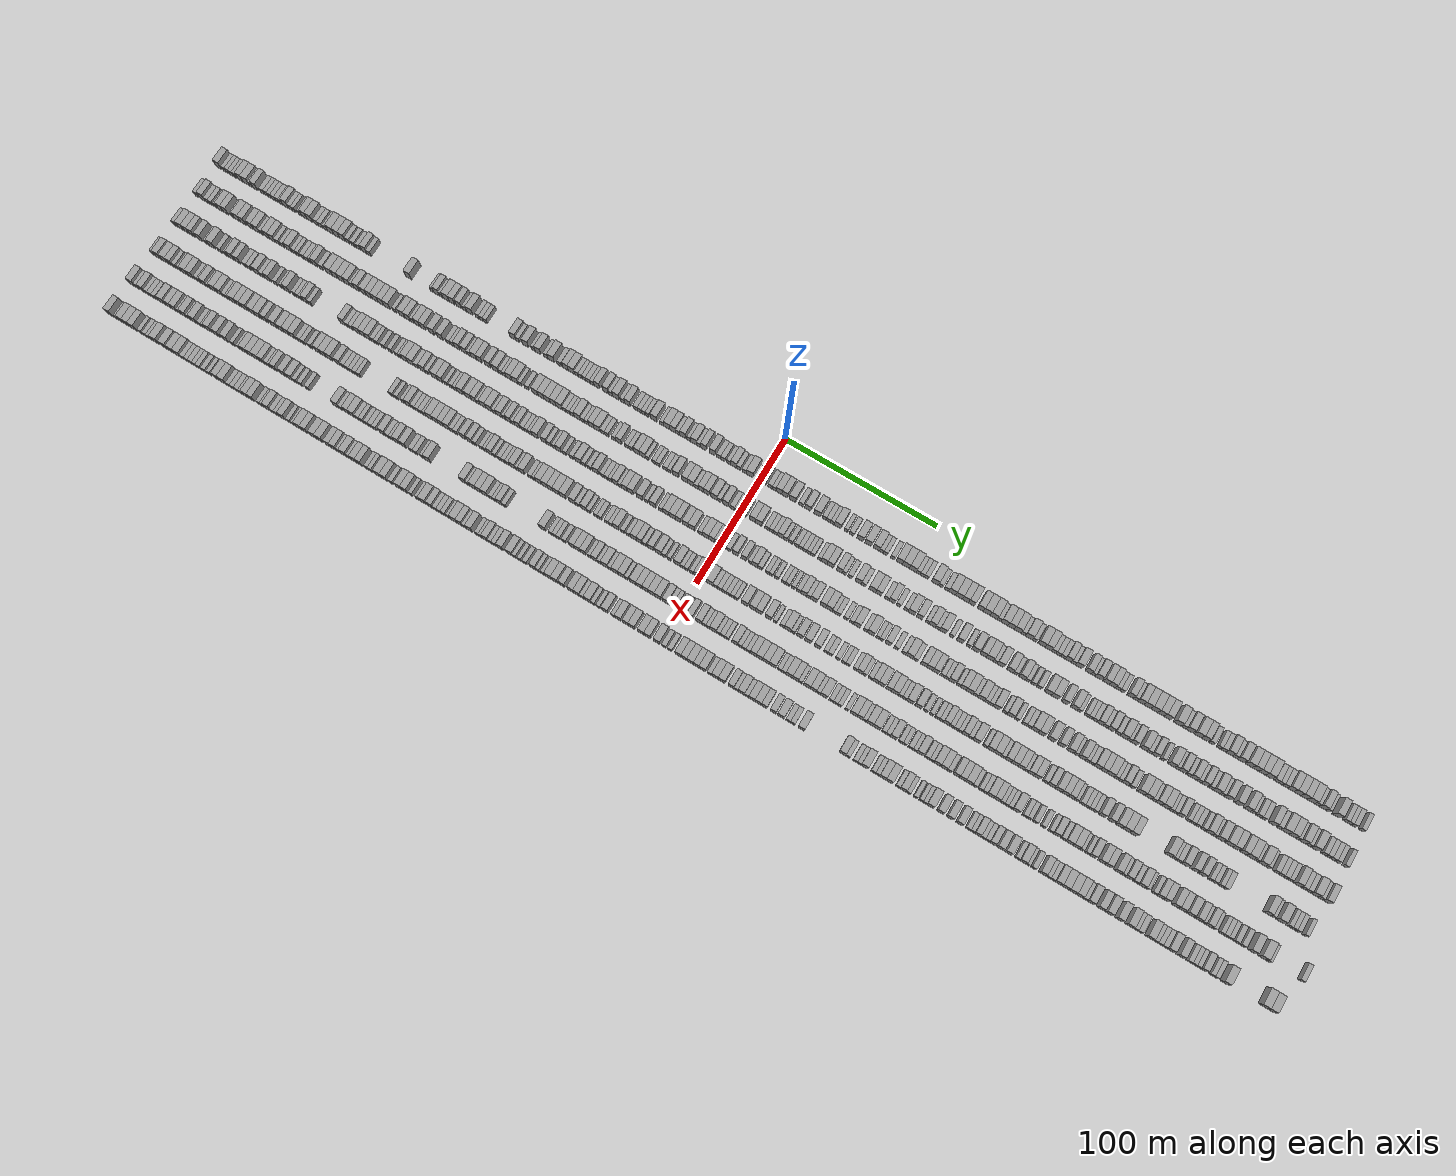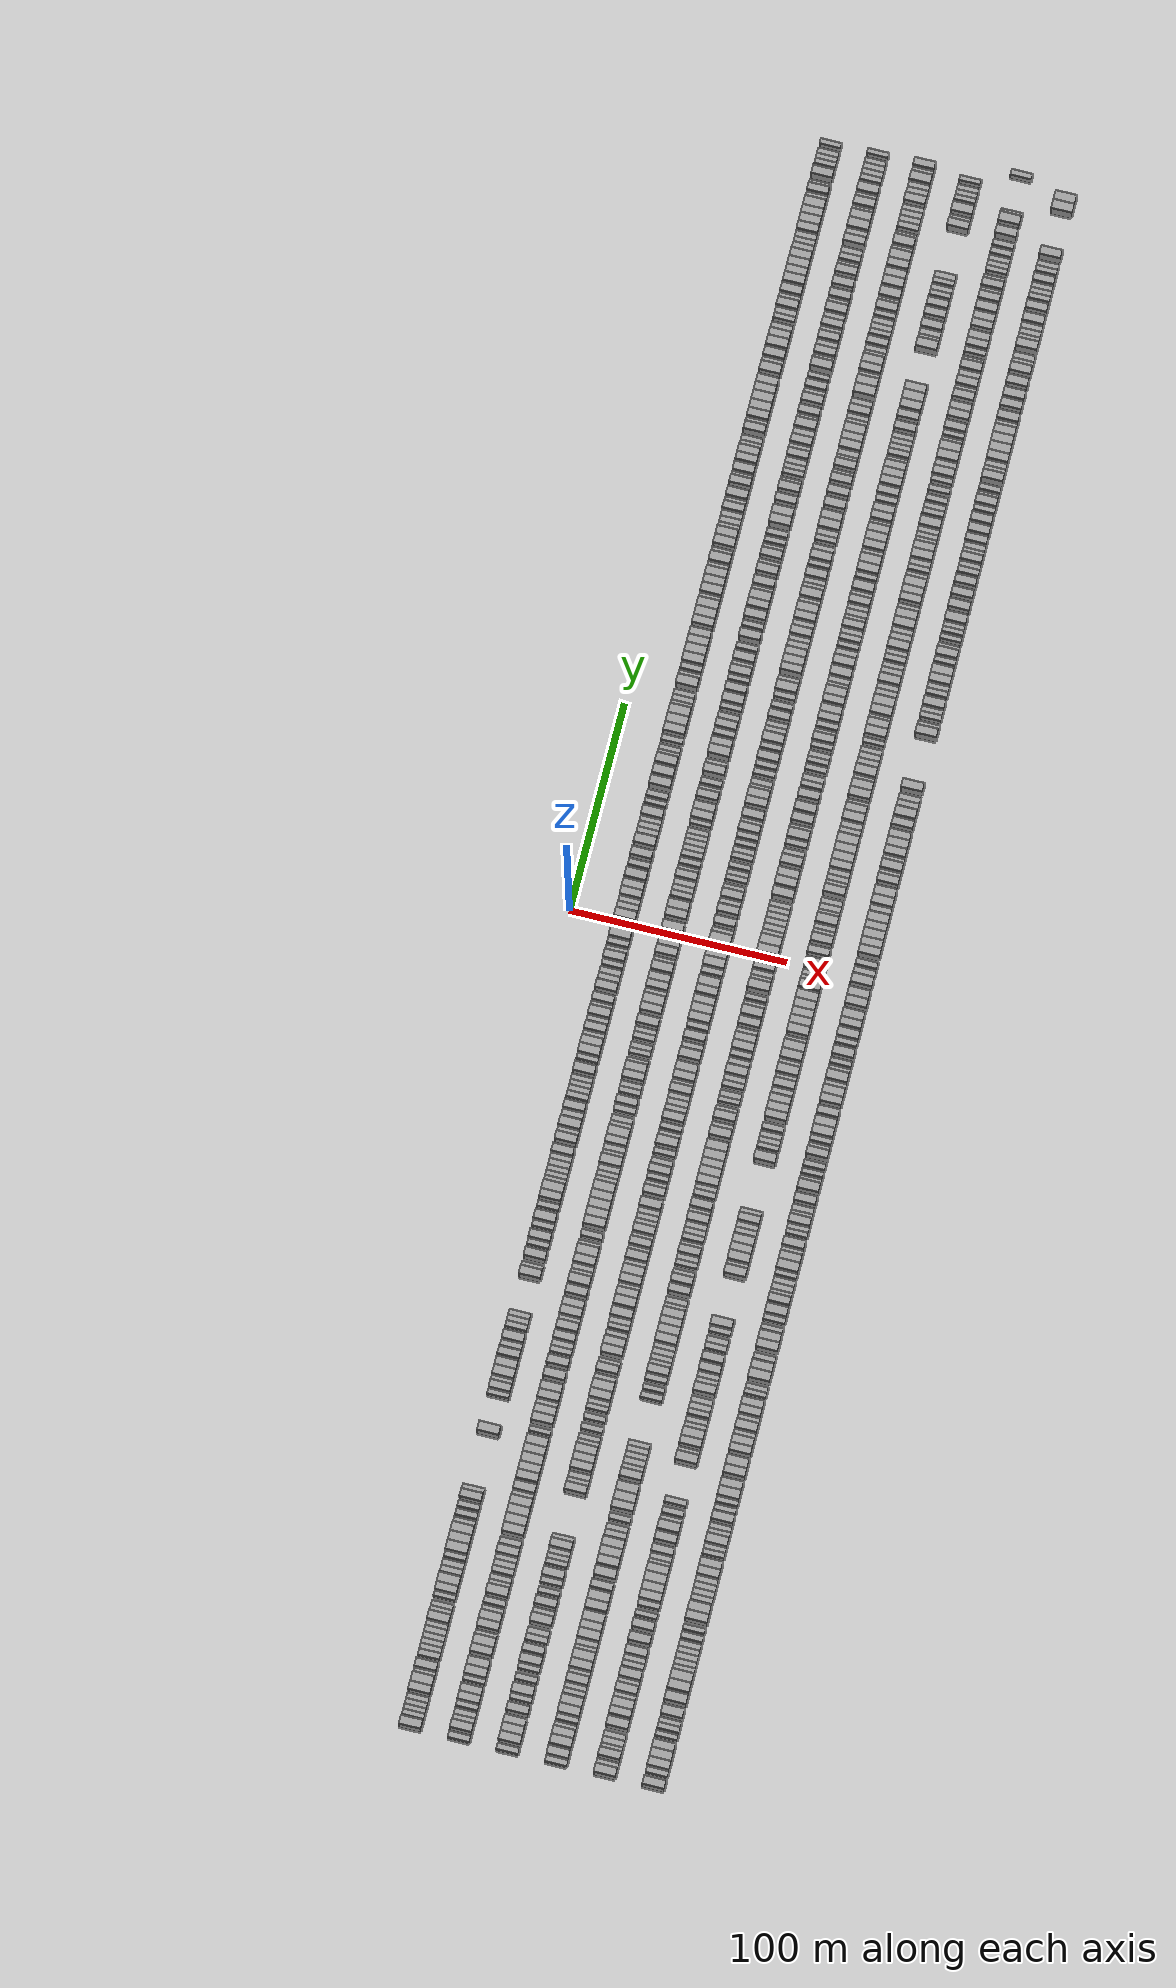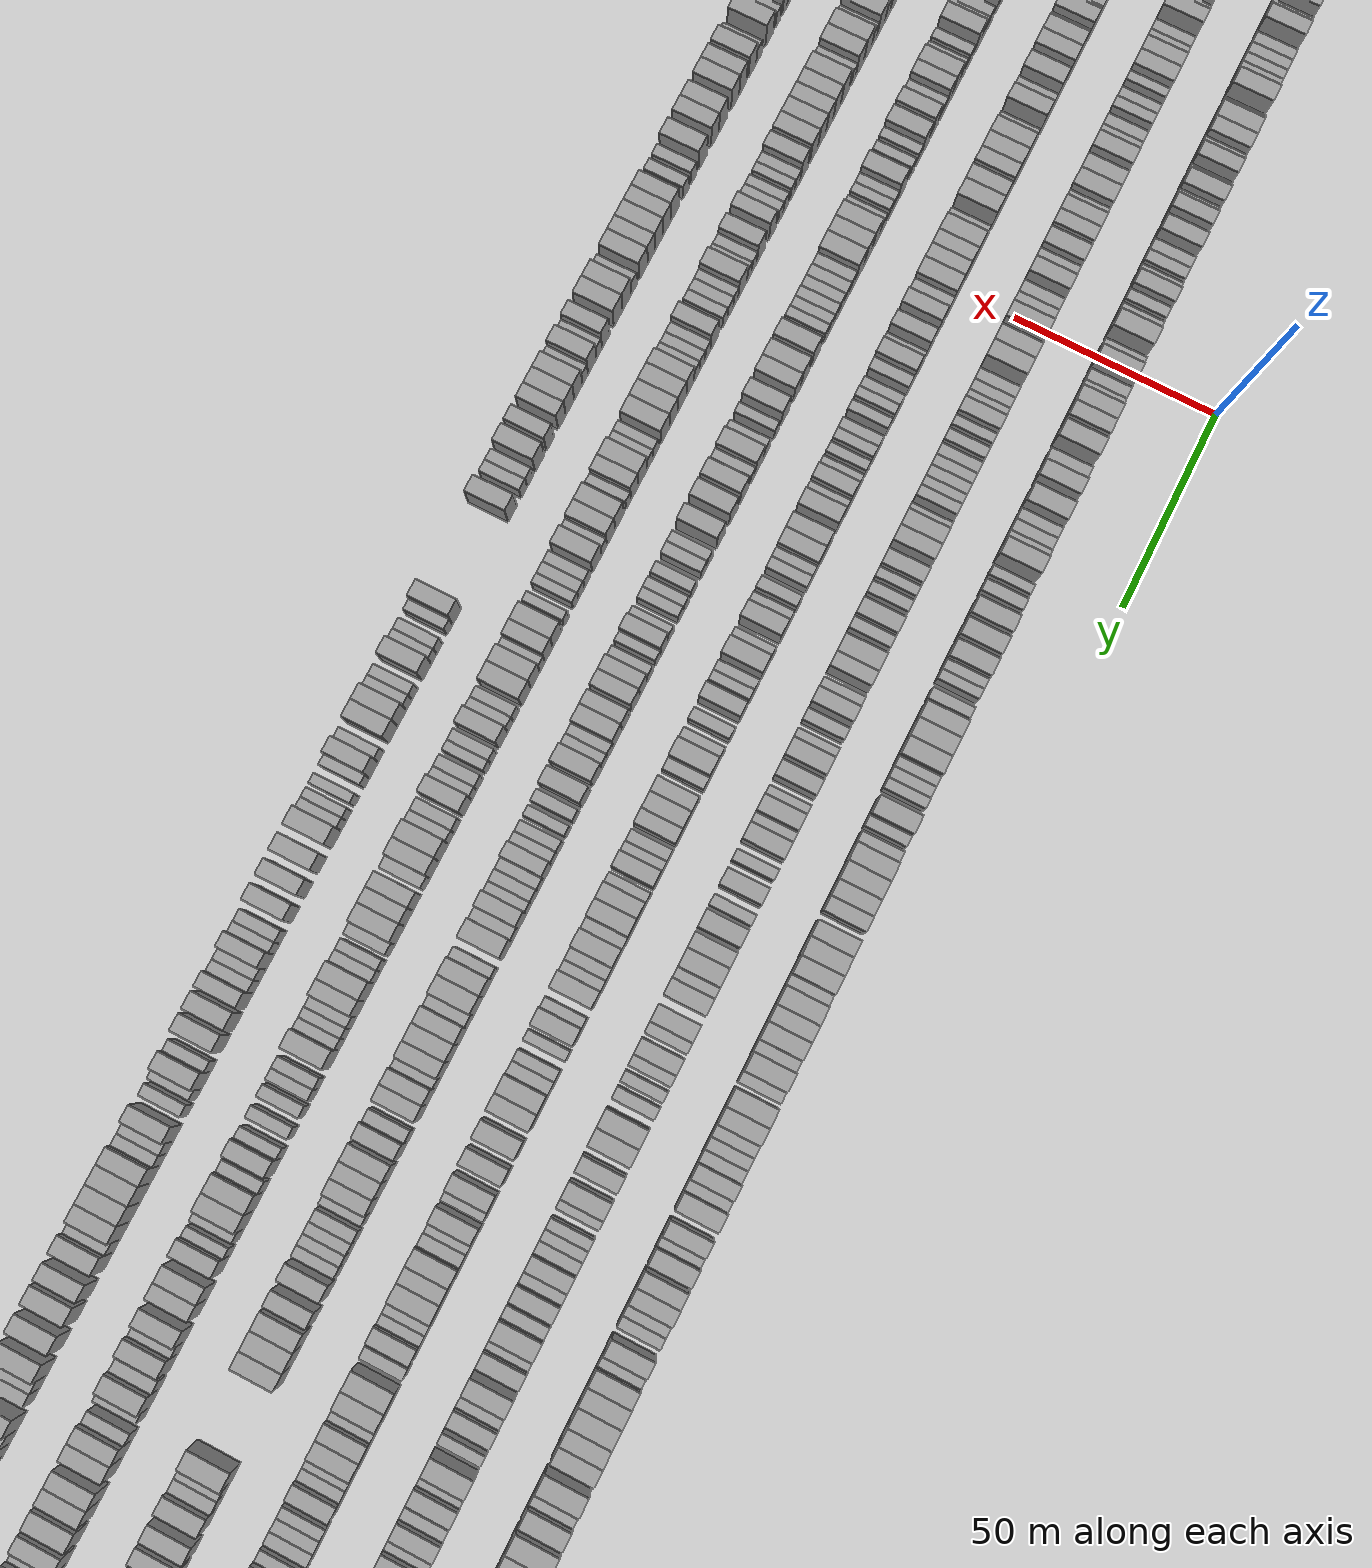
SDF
<sdf version="1.6">
 <world name="default">
  <scene>
   <sky><clouds><speed>12</speed></clouds></sky>
   <ambient>0.4 0.4 0.4 1</ambient>
   <background>0.7 0.7 0.7 1</background>
   <shadows>1</shadows>
  </scene>
  <gravity>0 0 -9.8066</gravity>
  <magnetic_field>6e-06 2.3e-05 -4.2e-05</magnetic_field>
  <physics default="0" name="default_physics" type="ode">
   <ode>
    <solver>
     <type>quick</type>
     <iters>10</iters>
     <sor>1.0</sor>
     <use_dynamic_moi_rescaling>0</use_dynamic_moi_rescaling>
    </solver>
    <constraints>
     <cfm>0</cfm>
     <erp>0.2</erp>
     <contact_max_correcting_vel>100</contact_max_correcting_vel>
     <contact_surface_layer>0.001</contact_surface_layer>
    </constraints>
   </ode>
   <max_step_size>0.004</max_step_size>
   <real_time_factor>1</real_time_factor>
   <real_time_update_rate>250</real_time_update_rate>
  </physics>
  <light name="sun" type="directional">
   <pose>0 0 10 0 0 0</pose>
   <diffuse>0.8 0.8 0.8 1</diffuse>
   <specular>0.2 0.2 0.2 1</specular>
   <attenuation>
    <range>1000</range>
    <constant>0.9</constant>
    <linear>0.01</linear>
    <quadratic>0.001</quadratic>
   </attenuation>
   <direction>-0.5 0.1 -0.9</direction>
  </light>
  <model name="building_1">
   <static>1</static>
   <pose>25.0000 -377.9437 0 0.000000 0.000000 0.000000</pose>
   <link name="link">
    <pose>0 0 4.50 0 0 0</pose>
    <collision name="collision"><geometry><box><size>10.0000 4.1127 9.0000</size></box></geometry></collision>
    <visual name="visual">
     <cast_shadows>0</cast_shadows>
     <geometry><box><size>10.0000 4.1127 9.0000</size></box></geometry>
     <material>
      <script>
       <uri>model://grey_wall/materials/scripts</uri>
       <uri>model://grey_wall/materials/textures</uri>
       <name>vrc/grey_wall</name>
      </script>
     </material>
    </visual>
   </link>
  </model>
  <model name="building_2">
   <static>1</static>
   <pose>25.0000 -373.6596 0 0.000000 0.000000 0.000000</pose>
   <link name="link">
    <pose>0 0 3.00 0 0 0</pose>
    <collision name="collision"><geometry><box><size>10.0000 2.4554 6.0000</size></box></geometry></collision>
    <visual name="visual">
     <cast_shadows>0</cast_shadows>
     <geometry><box><size>10.0000 2.4554 6.0000</size></box></geometry>
     <material>
      <script>
       <uri>model://grey_wall/materials/scripts</uri>
       <uri>model://grey_wall/materials/textures</uri>
       <name>vrc/grey_wall</name>
      </script>
     </material>
    </visual>
   </link>
  </model>
  <model name="building_3">
   <static>1</static>
   <pose>25.0000 -371.2207 0 0.000000 0.000000 0.000000</pose>
   <link name="link">
    <pose>0 0 3.00 0 0 0</pose>
    <collision name="collision"><geometry><box><size>10.0000 2.4226 6.0000</size></box></geometry></collision>
    <visual name="visual">
     <cast_shadows>0</cast_shadows>
     <geometry><box><size>10.0000 2.4226 6.0000</size></box></geometry>
     <material>
      <script>
       <uri>model://grey_wall/materials/scripts</uri>
       <uri>model://grey_wall/materials/textures</uri>
       <name>vrc/grey_wall</name>
      </script>
     </material>
    </visual>
   </link>
  </model>
  <model name="building_4">
   <static>1</static>
   <pose>25.0000 -368.7682 0 0.000000 0.000000 0.000000</pose>
   <link name="link">
    <pose>0 0 3.00 0 0 0</pose>
    <collision name="collision"><geometry><box><size>10.0000 2.4823 6.0000</size></box></geometry></collision>
    <visual name="visual">
     <cast_shadows>0</cast_shadows>
     <geometry><box><size>10.0000 2.4823 6.0000</size></box></geometry>
     <material>
      <script>
       <uri>model://grey_wall/materials/scripts</uri>
       <uri>model://grey_wall/materials/textures</uri>
       <name>vrc/grey_wall</name>
      </script>
     </material>
    </visual>
   </link>
  </model>
  <model name="building_5">
   <static>1</static>
   <pose>25.0000 -366.2189 0 0.000000 0.000000 0.000000</pose>
   <link name="link">
    <pose>0 0 3.00 0 0 0</pose>
    <collision name="collision"><geometry><box><size>10.0000 2.6164 6.0000</size></box></geometry></collision>
    <visual name="visual">
     <cast_shadows>0</cast_shadows>
     <geometry><box><size>10.0000 2.6164 6.0000</size></box></geometry>
     <material>
      <script>
       <uri>model://grey_wall/materials/scripts</uri>
       <uri>model://grey_wall/materials/textures</uri>
       <name>vrc/grey_wall</name>
      </script>
     </material>
    </visual>
   </link>
  </model>
  <model name="building_6">
   <static>1</static>
   <pose>25.0000 -362.0247 0 0.000000 0.000000 0.000000</pose>
   <link name="link">
    <pose>0 0 4.50 0 0 0</pose>
    <collision name="collision"><geometry><box><size>10.0000 3.7720 9.0000</size></box></geometry></collision>
    <visual name="visual">
     <cast_shadows>0</cast_shadows>
     <geometry><box><size>10.0000 3.7720 9.0000</size></box></geometry>
     <material>
      <script>
       <uri>model://grey_wall/materials/scripts</uri>
       <uri>model://grey_wall/materials/textures</uri>
       <name>vrc/grey_wall</name>
      </script>
     </material>
    </visual>
   </link>
  </model>
  <model name="building_7">
   <static>1</static>
   <pose>25.0000 -357.9072 0 0.000000 0.000000 0.000000</pose>
   <link name="link">
    <pose>0 0 4.50 0 0 0</pose>
    <collision name="collision"><geometry><box><size>10.0000 4.4630 9.0000</size></box></geometry></collision>
    <visual name="visual">
     <cast_shadows>0</cast_shadows>
     <geometry><box><size>10.0000 4.4630 9.0000</size></box></geometry>
     <material>
      <script>
       <uri>model://grey_wall/materials/scripts</uri>
       <uri>model://grey_wall/materials/textures</uri>
       <name>vrc/grey_wall</name>
      </script>
     </material>
    </visual>
   </link>
  </model>
  <model name="building_8">
   <static>1</static>
   <pose>25.0000 -354.4737 0 0.000000 0.000000 0.000000</pose>
   <link name="link">
    <pose>0 0 3.00 0 0 0</pose>
    <collision name="collision"><geometry><box><size>10.0000 2.4039 6.0000</size></box></geometry></collision>
    <visual name="visual">
     <cast_shadows>0</cast_shadows>
     <geometry><box><size>10.0000 2.4039 6.0000</size></box></geometry>
     <material>
      <script>
       <uri>model://grey_wall/materials/scripts</uri>
       <uri>model://grey_wall/materials/textures</uri>
       <name>vrc/grey_wall</name>
      </script>
     </material>
    </visual>
   </link>
  </model>
  <model name="building_9">
   <static>1</static>
   <pose>25.0000 -351.3434 0 0.000000 0.000000 0.000000</pose>
   <link name="link">
    <pose>0 0 4.50 0 0 0</pose>
    <collision name="collision"><geometry><box><size>10.0000 3.8568 9.0000</size></box></geometry></collision>
    <visual name="visual">
     <cast_shadows>0</cast_shadows>
     <geometry><box><size>10.0000 3.8568 9.0000</size></box></geometry>
     <material>
      <script>
       <uri>model://grey_wall/materials/scripts</uri>
       <uri>model://grey_wall/materials/textures</uri>
       <name>vrc/grey_wall</name>
      </script>
     </material>
    </visual>
   </link>
  </model>
  <model name="building_10">
   <static>1</static>
   <pose>25.0000 -345.9481 0 0.000000 0.000000 0.000000</pose>
   <link name="link">
    <pose>0 0 3.00 0 0 0</pose>
    <collision name="collision"><geometry><box><size>10.0000 2.9336 6.0000</size></box></geometry></collision>
    <visual name="visual">
     <cast_shadows>0</cast_shadows>
     <geometry><box><size>10.0000 2.9336 6.0000</size></box></geometry>
     <material>
      <script>
       <uri>model://grey_wall/materials/scripts</uri>
       <uri>model://grey_wall/materials/textures</uri>
       <name>vrc/grey_wall</name>
      </script>
     </material>
    </visual>
   </link>
  </model>
  <model name="building_11">
   <static>1</static>
   <pose>25.0000 -343.1982 0 0.000000 0.000000 0.000000</pose>
   <link name="link">
    <pose>0 0 3.00 0 0 0</pose>
    <collision name="collision"><geometry><box><size>10.0000 2.5663 6.0000</size></box></geometry></collision>
    <visual name="visual">
     <cast_shadows>0</cast_shadows>
     <geometry><box><size>10.0000 2.5663 6.0000</size></box></geometry>
     <material>
      <script>
       <uri>model://grey_wall/materials/scripts</uri>
       <uri>model://grey_wall/materials/textures</uri>
       <name>vrc/grey_wall</name>
      </script>
     </material>
    </visual>
   </link>
  </model>
  <model name="building_12">
   <static>1</static>
   <pose>25.0000 -340.6104 0 0.000000 0.000000 0.000000</pose>
   <link name="link">
    <pose>0 0 3.00 0 0 0</pose>
    <collision name="collision"><geometry><box><size>10.0000 2.6092 6.0000</size></box></geometry></collision>
    <visual name="visual">
     <cast_shadows>0</cast_shadows>
     <geometry><box><size>10.0000 2.6092 6.0000</size></box></geometry>
     <material>
      <script>
       <uri>model://grey_wall/materials/scripts</uri>
       <uri>model://grey_wall/materials/textures</uri>
       <name>vrc/grey_wall</name>
      </script>
     </material>
    </visual>
   </link>
  </model>
  <model name="building_13">
   <static>1</static>
   <pose>25.0000 -337.9464 0 0.000000 0.000000 0.000000</pose>
   <link name="link">
    <pose>0 0 3.00 0 0 0</pose>
    <collision name="collision"><geometry><box><size>10.0000 2.7187 6.0000</size></box></geometry></collision>
    <visual name="visual">
     <cast_shadows>0</cast_shadows>
     <geometry><box><size>10.0000 2.7187 6.0000</size></box></geometry>
     <material>
      <script>
       <uri>model://grey_wall/materials/scripts</uri>
       <uri>model://grey_wall/materials/textures</uri>
       <name>vrc/grey_wall</name>
      </script>
     </material>
    </visual>
   </link>
  </model>
  <model name="building_14">
   <static>1</static>
   <pose>25.0000 -335.1410 0 0.000000 0.000000 0.000000</pose>
   <link name="link">
    <pose>0 0 3.00 0 0 0</pose>
    <collision name="collision"><geometry><box><size>10.0000 2.8922 6.0000</size></box></geometry></collision>
    <visual name="visual">
     <cast_shadows>0</cast_shadows>
     <geometry><box><size>10.0000 2.8922 6.0000</size></box></geometry>
     <material>
      <script>
       <uri>model://grey_wall/materials/scripts</uri>
       <uri>model://grey_wall/materials/textures</uri>
       <name>vrc/grey_wall</name>
      </script>
     </material>
    </visual>
   </link>
  </model>
  <model name="building_15">
   <static>1</static>
   <pose>25.0000 -332.4710 0 0.000000 0.000000 0.000000</pose>
   <link name="link">
    <pose>0 0 3.00 0 0 0</pose>
    <collision name="collision"><geometry><box><size>10.0000 2.4478 6.0000</size></box></geometry></collision>
    <visual name="visual">
     <cast_shadows>0</cast_shadows>
     <geometry><box><size>10.0000 2.4478 6.0000</size></box></geometry>
     <material>
      <script>
       <uri>model://grey_wall/materials/scripts</uri>
       <uri>model://grey_wall/materials/textures</uri>
       <name>vrc/grey_wall</name>
      </script>
     </material>
    </visual>
   </link>
  </model>
  <model name="building_16">
   <static>1</static>
   <pose>25.0000 -329.2465 0 0.000000 0.000000 0.000000</pose>
   <link name="link">
    <pose>0 0 4.50 0 0 0</pose>
    <collision name="collision"><geometry><box><size>10.0000 4.0012 9.0000</size></box></geometry></collision>
    <visual name="visual">
     <cast_shadows>0</cast_shadows>
     <geometry><box><size>10.0000 4.0012 9.0000</size></box></geometry>
     <material>
      <script>
       <uri>model://grey_wall/materials/scripts</uri>
       <uri>model://grey_wall/materials/textures</uri>
       <name>vrc/grey_wall</name>
      </script>
     </material>
    </visual>
   </link>
  </model>
  <model name="building_17">
   <static>1</static>
   <pose>25.0000 -325.8893 0 0.000000 0.000000 0.000000</pose>
   <link name="link">
    <pose>0 0 3.00 0 0 0</pose>
    <collision name="collision"><geometry><box><size>10.0000 2.7132 6.0000</size></box></geometry></collision>
    <visual name="visual">
     <cast_shadows>0</cast_shadows>
     <geometry><box><size>10.0000 2.7132 6.0000</size></box></geometry>
     <material>
      <script>
       <uri>model://grey_wall/materials/scripts</uri>
       <uri>model://grey_wall/materials/textures</uri>
       <name>vrc/grey_wall</name>
      </script>
     </material>
    </visual>
   </link>
  </model>
  <model name="building_18">
   <static>1</static>
   <pose>25.0000 -323.3023 0 0.000000 0.000000 0.000000</pose>
   <link name="link">
    <pose>0 0 3.00 0 0 0</pose>
    <collision name="collision"><geometry><box><size>10.0000 2.4607 6.0000</size></box></geometry></collision>
    <visual name="visual">
     <cast_shadows>0</cast_shadows>
     <geometry><box><size>10.0000 2.4607 6.0000</size></box></geometry>
     <material>
      <script>
       <uri>model://grey_wall/materials/scripts</uri>
       <uri>model://grey_wall/materials/textures</uri>
       <name>vrc/grey_wall</name>
      </script>
     </material>
    </visual>
   </link>
  </model>
  <model name="building_19">
   <static>1</static>
   <pose>25.0000 -318.8527 0 0.000000 0.000000 0.000000</pose>
   <link name="link">
    <pose>0 0 3.00 0 0 0</pose>
    <collision name="collision"><geometry><box><size>10.0000 2.4385 6.0000</size></box></geometry></collision>
    <visual name="visual">
     <cast_shadows>0</cast_shadows>
     <geometry><box><size>10.0000 2.4385 6.0000</size></box></geometry>
     <material>
      <script>
       <uri>model://grey_wall/materials/scripts</uri>
       <uri>model://grey_wall/materials/textures</uri>
       <name>vrc/grey_wall</name>
      </script>
     </material>
    </visual>
   </link>
  </model>
  <model name="building_20">
   <static>1</static>
   <pose>25.0000 -315.7823 0 0.000000 0.000000 0.000000</pose>
   <link name="link">
    <pose>0 0 4.50 0 0 0</pose>
    <collision name="collision"><geometry><box><size>10.0000 3.7022 9.0000</size></box></geometry></collision>
    <visual name="visual">
     <cast_shadows>0</cast_shadows>
     <geometry><box><size>10.0000 3.7022 9.0000</size></box></geometry>
     <material>
      <script>
       <uri>model://grey_wall/materials/scripts</uri>
       <uri>model://grey_wall/materials/textures</uri>
       <name>vrc/grey_wall</name>
      </script>
     </material>
    </visual>
   </link>
  </model>
  <model name="building_21">
   <static>1</static>
   <pose>25.0000 -311.7753 0 0.000000 0.000000 0.000000</pose>
   <link name="link">
    <pose>0 0 4.50 0 0 0</pose>
    <collision name="collision"><geometry><box><size>10.0000 4.3119 9.0000</size></box></geometry></collision>
    <visual name="visual">
     <cast_shadows>0</cast_shadows>
     <geometry><box><size>10.0000 4.3119 9.0000</size></box></geometry>
     <material>
      <script>
       <uri>model://grey_wall/materials/scripts</uri>
       <uri>model://grey_wall/materials/textures</uri>
       <name>vrc/grey_wall</name>
      </script>
     </material>
    </visual>
   </link>
  </model>
  <model name="building_22">
   <static>1</static>
   <pose>25.0000 -307.1638 0 0.000000 0.000000 0.000000</pose>
   <link name="link">
    <pose>0 0 3.00 0 0 0</pose>
    <collision name="collision"><geometry><box><size>10.0000 2.9110 6.0000</size></box></geometry></collision>
    <visual name="visual">
     <cast_shadows>0</cast_shadows>
     <geometry><box><size>10.0000 2.9110 6.0000</size></box></geometry>
     <material>
      <script>
       <uri>model://grey_wall/materials/scripts</uri>
       <uri>model://grey_wall/materials/textures</uri>
       <name>vrc/grey_wall</name>
      </script>
     </material>
    </visual>
   </link>
  </model>
  <model name="building_23">
   <static>1</static>
   <pose>25.0000 -304.2133 0 0.000000 0.000000 0.000000</pose>
   <link name="link">
    <pose>0 0 3.00 0 0 0</pose>
    <collision name="collision"><geometry><box><size>10.0000 2.9899 6.0000</size></box></geometry></collision>
    <visual name="visual">
     <cast_shadows>0</cast_shadows>
     <geometry><box><size>10.0000 2.9899 6.0000</size></box></geometry>
     <material>
      <script>
       <uri>model://grey_wall/materials/scripts</uri>
       <uri>model://grey_wall/materials/textures</uri>
       <name>vrc/grey_wall</name>
      </script>
     </material>
    </visual>
   </link>
  </model>
  <model name="building_24">
   <static>1</static>
   <pose>25.0000 -300.3630 0 0.000000 0.000000 0.000000</pose>
   <link name="link">
    <pose>0 0 3.00 0 0 0</pose>
    <collision name="collision"><geometry><box><size>10.0000 2.7107 6.0000</size></box></geometry></collision>
    <visual name="visual">
     <cast_shadows>0</cast_shadows>
     <geometry><box><size>10.0000 2.7107 6.0000</size></box></geometry>
     <material>
      <script>
       <uri>model://grey_wall/materials/scripts</uri>
       <uri>model://grey_wall/materials/textures</uri>
       <name>vrc/grey_wall</name>
      </script>
     </material>
    </visual>
   </link>
  </model>
  <model name="building_25">
   <static>1</static>
   <pose>25.0000 -296.7653 0 0.000000 0.000000 0.000000</pose>
   <link name="link">
    <pose>0 0 4.50 0 0 0</pose>
    <collision name="collision"><geometry><box><size>10.0000 4.4847 9.0000</size></box></geometry></collision>
    <visual name="visual">
     <cast_shadows>0</cast_shadows>
     <geometry><box><size>10.0000 4.4847 9.0000</size></box></geometry>
     <material>
      <script>
       <uri>model://grey_wall/materials/scripts</uri>
       <uri>model://grey_wall/materials/textures</uri>
       <name>vrc/grey_wall</name>
      </script>
     </material>
    </visual>
   </link>
  </model>
  <model name="building_26">
   <static>1</static>
   <pose>25.0000 -292.4257 0 0.000000 0.000000 0.000000</pose>
   <link name="link">
    <pose>0 0 4.50 0 0 0</pose>
    <collision name="collision"><geometry><box><size>10.0000 4.1946 9.0000</size></box></geometry></collision>
    <visual name="visual">
     <cast_shadows>0</cast_shadows>
     <geometry><box><size>10.0000 4.1946 9.0000</size></box></geometry>
     <material>
      <script>
       <uri>model://grey_wall/materials/scripts</uri>
       <uri>model://grey_wall/materials/textures</uri>
       <name>vrc/grey_wall</name>
      </script>
     </material>
    </visual>
   </link>
  </model>
  <model name="building_27">
   <static>1</static>
   <pose>25.0000 -288.1981 0 0.000000 0.000000 0.000000</pose>
   <link name="link">
    <pose>0 0 4.50 0 0 0</pose>
    <collision name="collision"><geometry><box><size>10.0000 4.2606 9.0000</size></box></geometry></collision>
    <visual name="visual">
     <cast_shadows>0</cast_shadows>
     <geometry><box><size>10.0000 4.2606 9.0000</size></box></geometry>
     <material>
      <script>
       <uri>model://grey_wall/materials/scripts</uri>
       <uri>model://grey_wall/materials/textures</uri>
       <name>vrc/grey_wall</name>
      </script>
     </material>
    </visual>
   </link>
  </model>
  <model name="building_28">
   <static>1</static>
   <pose>25.0000 -284.6095 0 0.000000 0.000000 0.000000</pose>
   <link name="link">
    <pose>0 0 3.00 0 0 0</pose>
    <collision name="collision"><geometry><box><size>10.0000 2.9166 6.0000</size></box></geometry></collision>
    <visual name="visual">
     <cast_shadows>0</cast_shadows>
     <geometry><box><size>10.0000 2.9166 6.0000</size></box></geometry>
     <material>
      <script>
       <uri>model://grey_wall/materials/scripts</uri>
       <uri>model://grey_wall/materials/textures</uri>
       <name>vrc/grey_wall</name>
      </script>
     </material>
    </visual>
   </link>
  </model>
  <model name="building_29">
   <static>1</static>
   <pose>25.0000 -280.6863 0 0.000000 0.000000 0.000000</pose>
   <link name="link">
    <pose>0 0 3.00 0 0 0</pose>
    <collision name="collision"><geometry><box><size>10.0000 2.9296 6.0000</size></box></geometry></collision>
    <visual name="visual">
     <cast_shadows>0</cast_shadows>
     <geometry><box><size>10.0000 2.9296 6.0000</size></box></geometry>
     <material>
      <script>
       <uri>model://grey_wall/materials/scripts</uri>
       <uri>model://grey_wall/materials/textures</uri>
       <name>vrc/grey_wall</name>
      </script>
     </material>
    </visual>
   </link>
  </model>
  <model name="building_30">
   <static>1</static>
   <pose>25.0000 -276.8398 0 0.000000 0.000000 0.000000</pose>
   <link name="link">
    <pose>0 0 3.00 0 0 0</pose>
    <collision name="collision"><geometry><box><size>10.0000 2.7635 6.0000</size></box></geometry></collision>
    <visual name="visual">
     <cast_shadows>0</cast_shadows>
     <geometry><box><size>10.0000 2.7635 6.0000</size></box></geometry>
     <material>
      <script>
       <uri>model://grey_wall/materials/scripts</uri>
       <uri>model://grey_wall/materials/textures</uri>
       <name>vrc/grey_wall</name>
      </script>
     </material>
    </visual>
   </link>
  </model>
  <model name="building_31">
   <static>1</static>
   <pose>25.0000 -272.5830 0 0.000000 0.000000 0.000000</pose>
   <link name="link">
    <pose>0 0 4.50 0 0 0</pose>
    <collision name="collision"><geometry><box><size>10.0000 3.7500 9.0000</size></box></geometry></collision>
    <visual name="visual">
     <cast_shadows>0</cast_shadows>
     <geometry><box><size>10.0000 3.7500 9.0000</size></box></geometry>
     <material>
      <script>
       <uri>model://grey_wall/materials/scripts</uri>
       <uri>model://grey_wall/materials/textures</uri>
       <name>vrc/grey_wall</name>
      </script>
     </material>
    </visual>
   </link>
  </model>
  <model name="building_32">
   <static>1</static>
   <pose>25.0000 -269.2646 0 0.000000 0.000000 0.000000</pose>
   <link name="link">
    <pose>0 0 3.00 0 0 0</pose>
    <collision name="collision"><geometry><box><size>10.0000 2.8869 6.0000</size></box></geometry></collision>
    <visual name="visual">
     <cast_shadows>0</cast_shadows>
     <geometry><box><size>10.0000 2.8869 6.0000</size></box></geometry>
     <material>
      <script>
       <uri>model://grey_wall/materials/scripts</uri>
       <uri>model://grey_wall/materials/textures</uri>
       <name>vrc/grey_wall</name>
      </script>
     </material>
    </visual>
   </link>
  </model>
  <model name="building_33">
   <static>1</static>
   <pose>25.0000 -241.3336 0 0.000000 0.000000 0.000000</pose>
   <link name="link">
    <pose>0 0 4.50 0 0 0</pose>
    <collision name="collision"><geometry><box><size>10.0000 4.3250 9.0000</size></box></geometry></collision>
    <visual name="visual">
     <cast_shadows>0</cast_shadows>
     <geometry><box><size>10.0000 4.3250 9.0000</size></box></geometry>
     <material>
      <script>
       <uri>model://grey_wall/materials/scripts</uri>
       <uri>model://grey_wall/materials/textures</uri>
       <name>vrc/grey_wall</name>
      </script>
     </material>
    </visual>
   </link>
  </model>
  <model name="building_34">
   <static>1</static>
   <pose>25.0000 -224.4694 0 0.000000 0.000000 0.000000</pose>
   <link name="link">
    <pose>0 0 3.00 0 0 0</pose>
    <collision name="collision"><geometry><box><size>10.0000 2.4678 6.0000</size></box></geometry></collision>
    <visual name="visual">
     <cast_shadows>0</cast_shadows>
     <geometry><box><size>10.0000 2.4678 6.0000</size></box></geometry>
     <material>
      <script>
       <uri>model://grey_wall/materials/scripts</uri>
       <uri>model://grey_wall/materials/textures</uri>
       <name>vrc/grey_wall</name>
      </script>
     </material>
    </visual>
   </link>
  </model>
  <model name="building_35">
   <static>1</static>
   <pose>25.0000 -221.4238 0 0.000000 0.000000 0.000000</pose>
   <link name="link">
    <pose>0 0 4.50 0 0 0</pose>
    <collision name="collision"><geometry><box><size>10.0000 3.6234 9.0000</size></box></geometry></collision>
    <visual name="visual">
     <cast_shadows>0</cast_shadows>
     <geometry><box><size>10.0000 3.6234 9.0000</size></box></geometry>
     <material>
      <script>
       <uri>model://grey_wall/materials/scripts</uri>
       <uri>model://grey_wall/materials/textures</uri>
       <name>vrc/grey_wall</name>
      </script>
     </material>
    </visual>
   </link>
  </model>
  <model name="building_36">
   <static>1</static>
   <pose>25.0000 -218.2902 0 0.000000 0.000000 0.000000</pose>
   <link name="link">
    <pose>0 0 3.00 0 0 0</pose>
    <collision name="collision"><geometry><box><size>10.0000 2.6437 6.0000</size></box></geometry></collision>
    <visual name="visual">
     <cast_shadows>0</cast_shadows>
     <geometry><box><size>10.0000 2.6437 6.0000</size></box></geometry>
     <material>
      <script>
       <uri>model://grey_wall/materials/scripts</uri>
       <uri>model://grey_wall/materials/textures</uri>
       <name>vrc/grey_wall</name>
      </script>
     </material>
    </visual>
   </link>
  </model>
  <model name="building_37">
   <static>1</static>
   <pose>25.0000 -214.7772 0 0.000000 0.000000 0.000000</pose>
   <link name="link">
    <pose>0 0 4.50 0 0 0</pose>
    <collision name="collision"><geometry><box><size>10.0000 4.3824 9.0000</size></box></geometry></collision>
    <visual name="visual">
     <cast_shadows>0</cast_shadows>
     <geometry><box><size>10.0000 4.3824 9.0000</size></box></geometry>
     <material>
      <script>
       <uri>model://grey_wall/materials/scripts</uri>
       <uri>model://grey_wall/materials/textures</uri>
       <name>vrc/grey_wall</name>
      </script>
     </material>
    </visual>
   </link>
  </model>
  <model name="building_38">
   <static>1</static>
   <pose>25.0000 -210.5929 0 0.000000 0.000000 0.000000</pose>
   <link name="link">
    <pose>0 0 4.50 0 0 0</pose>
    <collision name="collision"><geometry><box><size>10.0000 3.9861 9.0000</size></box></geometry></collision>
    <visual name="visual">
     <cast_shadows>0</cast_shadows>
     <geometry><box><size>10.0000 3.9861 9.0000</size></box></geometry>
     <material>
      <script>
       <uri>model://grey_wall/materials/scripts</uri>
       <uri>model://grey_wall/materials/textures</uri>
       <name>vrc/grey_wall</name>
      </script>
     </material>
    </visual>
   </link>
  </model>
  <model name="building_39">
   <static>1</static>
   <pose>25.0000 -205.7783 0 0.000000 0.000000 0.000000</pose>
   <link name="link">
    <pose>0 0 4.50 0 0 0</pose>
    <collision name="collision"><geometry><box><size>10.0000 3.6431 9.0000</size></box></geometry></collision>
    <visual name="visual">
     <cast_shadows>0</cast_shadows>
     <geometry><box><size>10.0000 3.6431 9.0000</size></box></geometry>
     <material>
      <script>
       <uri>model://grey_wall/materials/scripts</uri>
       <uri>model://grey_wall/materials/textures</uri>
       <name>vrc/grey_wall</name>
      </script>
     </material>
    </visual>
   </link>
  </model>
  <model name="building_40">
   <static>1</static>
   <pose>25.0000 -201.5535 0 0.000000 0.000000 0.000000</pose>
   <link name="link">
    <pose>0 0 3.00 0 0 0</pose>
    <collision name="collision"><geometry><box><size>10.0000 2.8066 6.0000</size></box></geometry></collision>
    <visual name="visual">
     <cast_shadows>0</cast_shadows>
     <geometry><box><size>10.0000 2.8066 6.0000</size></box></geometry>
     <material>
      <script>
       <uri>model://grey_wall/materials/scripts</uri>
       <uri>model://grey_wall/materials/textures</uri>
       <name>vrc/grey_wall</name>
      </script>
     </material>
    </visual>
   </link>
  </model>
  <model name="building_41">
   <static>1</static>
   <pose>25.0000 -198.0791 0 0.000000 0.000000 0.000000</pose>
   <link name="link">
    <pose>0 0 4.50 0 0 0</pose>
    <collision name="collision"><geometry><box><size>10.0000 4.1423 9.0000</size></box></geometry></collision>
    <visual name="visual">
     <cast_shadows>0</cast_shadows>
     <geometry><box><size>10.0000 4.1423 9.0000</size></box></geometry>
     <material>
      <script>
       <uri>model://grey_wall/materials/scripts</uri>
       <uri>model://grey_wall/materials/textures</uri>
       <name>vrc/grey_wall</name>
      </script>
     </material>
    </visual>
   </link>
  </model>
  <model name="building_42">
   <static>1</static>
   <pose>25.0000 -192.6238 0 0.000000 0.000000 0.000000</pose>
   <link name="link">
    <pose>0 0 3.00 0 0 0</pose>
    <collision name="collision"><geometry><box><size>10.0000 2.7682 6.0000</size></box></geometry></collision>
    <visual name="visual">
     <cast_shadows>0</cast_shadows>
     <geometry><box><size>10.0000 2.7682 6.0000</size></box></geometry>
     <material>
      <script>
       <uri>model://grey_wall/materials/scripts</uri>
       <uri>model://grey_wall/materials/textures</uri>
       <name>vrc/grey_wall</name>
      </script>
     </material>
    </visual>
   </link>
  </model>
  <model name="building_43">
   <static>1</static>
   <pose>25.0000 -189.9200 0 0.000000 0.000000 0.000000</pose>
   <link name="link">
    <pose>0 0 3.00 0 0 0</pose>
    <collision name="collision"><geometry><box><size>10.0000 2.6394 6.0000</size></box></geometry></collision>
    <visual name="visual">
     <cast_shadows>0</cast_shadows>
     <geometry><box><size>10.0000 2.6394 6.0000</size></box></geometry>
     <material>
      <script>
       <uri>model://grey_wall/materials/scripts</uri>
       <uri>model://grey_wall/materials/textures</uri>
       <name>vrc/grey_wall</name>
      </script>
     </material>
    </visual>
   </link>
  </model>
  <model name="building_44">
   <static>1</static>
   <pose>25.0000 -187.2783 0 0.000000 0.000000 0.000000</pose>
   <link name="link">
    <pose>0 0 3.00 0 0 0</pose>
    <collision name="collision"><geometry><box><size>10.0000 2.6440 6.0000</size></box></geometry></collision>
    <visual name="visual">
     <cast_shadows>0</cast_shadows>
     <geometry><box><size>10.0000 2.6440 6.0000</size></box></geometry>
     <material>
      <script>
       <uri>model://grey_wall/materials/scripts</uri>
       <uri>model://grey_wall/materials/textures</uri>
       <name>vrc/grey_wall</name>
      </script>
     </material>
    </visual>
   </link>
  </model>
  <model name="building_45">
   <static>1</static>
   <pose>25.0000 -167.9538 0 0.000000 0.000000 0.000000</pose>
   <link name="link">
    <pose>0 0 4.50 0 0 0</pose>
    <collision name="collision"><geometry><box><size>10.0000 4.0017 9.0000</size></box></geometry></collision>
    <visual name="visual">
     <cast_shadows>0</cast_shadows>
     <geometry><box><size>10.0000 4.0017 9.0000</size></box></geometry>
     <material>
      <script>
       <uri>model://grey_wall/materials/scripts</uri>
       <uri>model://grey_wall/materials/textures</uri>
       <name>vrc/grey_wall</name>
      </script>
     </material>
    </visual>
   </link>
  </model>
  <model name="building_46">
   <static>1</static>
   <pose>25.0000 -164.6189 0 0.000000 0.000000 0.000000</pose>
   <link name="link">
    <pose>0 0 3.00 0 0 0</pose>
    <collision name="collision"><geometry><box><size>10.0000 2.6681 6.0000</size></box></geometry></collision>
    <visual name="visual">
     <cast_shadows>0</cast_shadows>
     <geometry><box><size>10.0000 2.6681 6.0000</size></box></geometry>
     <material>
      <script>
       <uri>model://grey_wall/materials/scripts</uri>
       <uri>model://grey_wall/materials/textures</uri>
       <name>vrc/grey_wall</name>
      </script>
     </material>
    </visual>
   </link>
  </model>
  <model name="building_47">
   <static>1</static>
   <pose>25.0000 -159.2383 0 0.000000 0.000000 0.000000</pose>
   <link name="link">
    <pose>0 0 4.50 0 0 0</pose>
    <collision name="collision"><geometry><box><size>10.0000 4.0933 9.0000</size></box></geometry></collision>
    <visual name="visual">
     <cast_shadows>0</cast_shadows>
     <geometry><box><size>10.0000 4.0933 9.0000</size></box></geometry>
     <material>
      <script>
       <uri>model://grey_wall/materials/scripts</uri>
       <uri>model://grey_wall/materials/textures</uri>
       <name>vrc/grey_wall</name>
      </script>
     </material>
    </visual>
   </link>
  </model>
  <model name="building_48">
   <static>1</static>
   <pose>25.0000 -153.8384 0 0.000000 0.000000 0.000000</pose>
   <link name="link">
    <pose>0 0 3.00 0 0 0</pose>
    <collision name="collision"><geometry><box><size>10.0000 2.7064 6.0000</size></box></geometry></collision>
    <visual name="visual">
     <cast_shadows>0</cast_shadows>
     <geometry><box><size>10.0000 2.7064 6.0000</size></box></geometry>
     <material>
      <script>
       <uri>model://grey_wall/materials/scripts</uri>
       <uri>model://grey_wall/materials/textures</uri>
       <name>vrc/grey_wall</name>
      </script>
     </material>
    </visual>
   </link>
  </model>
  <model name="building_49">
   <static>1</static>
   <pose>25.0000 -150.5352 0 0.000000 0.000000 0.000000</pose>
   <link name="link">
    <pose>0 0 4.50 0 0 0</pose>
    <collision name="collision"><geometry><box><size>10.0000 3.9000 9.0000</size></box></geometry></collision>
    <visual name="visual">
     <cast_shadows>0</cast_shadows>
     <geometry><box><size>10.0000 3.9000 9.0000</size></box></geometry>
     <material>
      <script>
       <uri>model://grey_wall/materials/scripts</uri>
       <uri>model://grey_wall/materials/textures</uri>
       <name>vrc/grey_wall</name>
      </script>
     </material>
    </visual>
   </link>
  </model>
  <model name="building_50">
   <static>1</static>
   <pose>25.0000 -145.1310 0 0.000000 0.000000 0.000000</pose>
   <link name="link">
    <pose>0 0 3.00 0 0 0</pose>
    <collision name="collision"><geometry><box><size>10.0000 2.9084 6.0000</size></box></geometry></collision>
    <visual name="visual">
     <cast_shadows>0</cast_shadows>
     <geometry><box><size>10.0000 2.9084 6.0000</size></box></geometry>
     <material>
      <script>
       <uri>model://grey_wall/materials/scripts</uri>
       <uri>model://grey_wall/materials/textures</uri>
       <name>vrc/grey_wall</name>
      </script>
     </material>
    </visual>
   </link>
  </model>
  <model name="building_51">
   <static>1</static>
   <pose>25.0000 -141.4732 0 0.000000 0.000000 0.000000</pose>
   <link name="link">
    <pose>0 0 4.50 0 0 0</pose>
    <collision name="collision"><geometry><box><size>10.0000 4.4074 9.0000</size></box></geometry></collision>
    <visual name="visual">
     <cast_shadows>0</cast_shadows>
     <geometry><box><size>10.0000 4.4074 9.0000</size></box></geometry>
     <material>
      <script>
       <uri>model://grey_wall/materials/scripts</uri>
       <uri>model://grey_wall/materials/textures</uri>
       <name>vrc/grey_wall</name>
      </script>
     </material>
    </visual>
   </link>
  </model>
  <model name="building_52">
   <static>1</static>
   <pose>25.0000 -135.8433 0 0.000000 0.000000 0.000000</pose>
   <link name="link">
    <pose>0 0 3.00 0 0 0</pose>
    <collision name="collision"><geometry><box><size>10.0000 2.8524 6.0000</size></box></geometry></collision>
    <visual name="visual">
     <cast_shadows>0</cast_shadows>
     <geometry><box><size>10.0000 2.8524 6.0000</size></box></geometry>
     <material>
      <script>
       <uri>model://grey_wall/materials/scripts</uri>
       <uri>model://grey_wall/materials/textures</uri>
       <name>vrc/grey_wall</name>
      </script>
     </material>
    </visual>
   </link>
  </model>
  <model name="building_53">
   <static>1</static>
   <pose>25.0000 -131.5592 0 0.000000 0.000000 0.000000</pose>
   <link name="link">
    <pose>0 0 4.50 0 0 0</pose>
    <collision name="collision"><geometry><box><size>10.0000 3.7159 9.0000</size></box></geometry></collision>
    <visual name="visual">
     <cast_shadows>0</cast_shadows>
     <geometry><box><size>10.0000 3.7159 9.0000</size></box></geometry>
     <material>
      <script>
       <uri>model://grey_wall/materials/scripts</uri>
       <uri>model://grey_wall/materials/textures</uri>
       <name>vrc/grey_wall</name>
      </script>
     </material>
    </visual>
   </link>
  </model>
  <model name="building_54">
   <static>1</static>
   <pose>25.0000 -127.5288 0 0.000000 0.000000 0.000000</pose>
   <link name="link">
    <pose>0 0 4.50 0 0 0</pose>
    <collision name="collision"><geometry><box><size>10.0000 4.3447 9.0000</size></box></geometry></collision>
    <visual name="visual">
     <cast_shadows>0</cast_shadows>
     <geometry><box><size>10.0000 4.3447 9.0000</size></box></geometry>
     <material>
      <script>
       <uri>model://grey_wall/materials/scripts</uri>
       <uri>model://grey_wall/materials/textures</uri>
       <name>vrc/grey_wall</name>
      </script>
     </material>
    </visual>
   </link>
  </model>
  <model name="building_55">
   <static>1</static>
   <pose>25.0000 -123.9615 0 0.000000 0.000000 0.000000</pose>
   <link name="link">
    <pose>0 0 3.00 0 0 0</pose>
    <collision name="collision"><geometry><box><size>10.0000 2.7901 6.0000</size></box></geometry></collision>
    <visual name="visual">
     <cast_shadows>0</cast_shadows>
     <geometry><box><size>10.0000 2.7901 6.0000</size></box></geometry>
     <material>
      <script>
       <uri>model://grey_wall/materials/scripts</uri>
       <uri>model://grey_wall/materials/textures</uri>
       <name>vrc/grey_wall</name>
      </script>
     </material>
    </visual>
   </link>
  </model>
  <model name="building_56">
   <static>1</static>
   <pose>25.0000 -121.3460 0 0.000000 0.000000 0.000000</pose>
   <link name="link">
    <pose>0 0 3.00 0 0 0</pose>
    <collision name="collision"><geometry><box><size>10.0000 2.4408 6.0000</size></box></geometry></collision>
    <visual name="visual">
     <cast_shadows>0</cast_shadows>
     <geometry><box><size>10.0000 2.4408 6.0000</size></box></geometry>
     <material>
      <script>
       <uri>model://grey_wall/materials/scripts</uri>
       <uri>model://grey_wall/materials/textures</uri>
       <name>vrc/grey_wall</name>
      </script>
     </material>
    </visual>
   </link>
  </model>
  <model name="building_57">
   <static>1</static>
   <pose>25.0000 -118.8301 0 0.000000 0.000000 0.000000</pose>
   <link name="link">
    <pose>0 0 3.00 0 0 0</pose>
    <collision name="collision"><geometry><box><size>10.0000 2.5911 6.0000</size></box></geometry></collision>
    <visual name="visual">
     <cast_shadows>0</cast_shadows>
     <geometry><box><size>10.0000 2.5911 6.0000</size></box></geometry>
     <material>
      <script>
       <uri>model://grey_wall/materials/scripts</uri>
       <uri>model://grey_wall/materials/textures</uri>
       <name>vrc/grey_wall</name>
      </script>
     </material>
    </visual>
   </link>
  </model>
  <model name="building_58">
   <static>1</static>
   <pose>25.0000 -116.0676 0 0.000000 0.000000 0.000000</pose>
   <link name="link">
    <pose>0 0 3.00 0 0 0</pose>
    <collision name="collision"><geometry><box><size>10.0000 2.9338 6.0000</size></box></geometry></collision>
    <visual name="visual">
     <cast_shadows>0</cast_shadows>
     <geometry><box><size>10.0000 2.9338 6.0000</size></box></geometry>
     <material>
      <script>
       <uri>model://grey_wall/materials/scripts</uri>
       <uri>model://grey_wall/materials/textures</uri>
       <name>vrc/grey_wall</name>
      </script>
     </material>
    </visual>
   </link>
  </model>
  <model name="building_59">
   <static>1</static>
   <pose>25.0000 -113.2527 0 0.000000 0.000000 0.000000</pose>
   <link name="link">
    <pose>0 0 3.00 0 0 0</pose>
    <collision name="collision"><geometry><box><size>10.0000 2.6960 6.0000</size></box></geometry></collision>
    <visual name="visual">
     <cast_shadows>0</cast_shadows>
     <geometry><box><size>10.0000 2.6960 6.0000</size></box></geometry>
     <material>
      <script>
       <uri>model://grey_wall/materials/scripts</uri>
       <uri>model://grey_wall/materials/textures</uri>
       <name>vrc/grey_wall</name>
      </script>
     </material>
    </visual>
   </link>
  </model>
  <model name="building_60">
   <static>1</static>
   <pose>25.0000 -109.9994 0 0.000000 0.000000 0.000000</pose>
   <link name="link">
    <pose>0 0 4.50 0 0 0</pose>
    <collision name="collision"><geometry><box><size>10.0000 3.8105 9.0000</size></box></geometry></collision>
    <visual name="visual">
     <cast_shadows>0</cast_shadows>
     <geometry><box><size>10.0000 3.8105 9.0000</size></box></geometry>
     <material>
      <script>
       <uri>model://grey_wall/materials/scripts</uri>
       <uri>model://grey_wall/materials/textures</uri>
       <name>vrc/grey_wall</name>
      </script>
     </material>
    </visual>
   </link>
  </model>
  <model name="building_61">
   <static>1</static>
   <pose>25.0000 -104.1493 0 0.000000 0.000000 0.000000</pose>
   <link name="link">
    <pose>0 0 4.50 0 0 0</pose>
    <collision name="collision"><geometry><box><size>10.0000 3.8898 9.0000</size></box></geometry></collision>
    <visual name="visual">
     <cast_shadows>0</cast_shadows>
     <geometry><box><size>10.0000 3.8898 9.0000</size></box></geometry>
     <material>
      <script>
       <uri>model://grey_wall/materials/scripts</uri>
       <uri>model://grey_wall/materials/textures</uri>
       <name>vrc/grey_wall</name>
      </script>
     </material>
    </visual>
   </link>
  </model>
  <model name="building_62">
   <static>1</static>
   <pose>25.0000 -100.7538 0 0.000000 0.000000 0.000000</pose>
   <link name="link">
    <pose>0 0 3.00 0 0 0</pose>
    <collision name="collision"><geometry><box><size>10.0000 2.9012 6.0000</size></box></geometry></collision>
    <visual name="visual">
     <cast_shadows>0</cast_shadows>
     <geometry><box><size>10.0000 2.9012 6.0000</size></box></geometry>
     <material>
      <script>
       <uri>model://grey_wall/materials/scripts</uri>
       <uri>model://grey_wall/materials/textures</uri>
       <name>vrc/grey_wall</name>
      </script>
     </material>
    </visual>
   </link>
  </model>
  <model name="building_63">
   <static>1</static>
   <pose>25.0000 -97.1521 0 0.000000 0.000000 0.000000</pose>
   <link name="link">
    <pose>0 0 4.50 0 0 0</pose>
    <collision name="collision"><geometry><box><size>10.0000 4.3023 9.0000</size></box></geometry></collision>
    <visual name="visual">
     <cast_shadows>0</cast_shadows>
     <geometry><box><size>10.0000 4.3023 9.0000</size></box></geometry>
     <material>
      <script>
       <uri>model://grey_wall/materials/scripts</uri>
       <uri>model://grey_wall/materials/textures</uri>
       <name>vrc/grey_wall</name>
      </script>
     </material>
    </visual>
   </link>
  </model>
  <model name="building_64">
   <static>1</static>
   <pose>25.0000 -92.5149 0 0.000000 0.000000 0.000000</pose>
   <link name="link">
    <pose>0 0 3.00 0 0 0</pose>
    <collision name="collision"><geometry><box><size>10.0000 2.9720 6.0000</size></box></geometry></collision>
    <visual name="visual">
     <cast_shadows>0</cast_shadows>
     <geometry><box><size>10.0000 2.9720 6.0000</size></box></geometry>
     <material>
      <script>
       <uri>model://grey_wall/materials/scripts</uri>
       <uri>model://grey_wall/materials/textures</uri>
       <name>vrc/grey_wall</name>
      </script>
     </material>
    </visual>
   </link>
  </model>
  <model name="building_65">
   <static>1</static>
   <pose>25.0000 -89.0761 0 0.000000 0.000000 0.000000</pose>
   <link name="link">
    <pose>0 0 4.50 0 0 0</pose>
    <collision name="collision"><geometry><box><size>10.0000 3.9056 9.0000</size></box></geometry></collision>
    <visual name="visual">
     <cast_shadows>0</cast_shadows>
     <geometry><box><size>10.0000 3.9056 9.0000</size></box></geometry>
     <material>
      <script>
       <uri>model://grey_wall/materials/scripts</uri>
       <uri>model://grey_wall/materials/textures</uri>
       <name>vrc/grey_wall</name>
      </script>
     </material>
    </visual>
   </link>
  </model>
  <model name="building_66">
   <static>1</static>
   <pose>25.0000 -83.6893 0 0.000000 0.000000 0.000000</pose>
   <link name="link">
    <pose>0 0 3.00 0 0 0</pose>
    <collision name="collision"><geometry><box><size>10.0000 2.8680 6.0000</size></box></geometry></collision>
    <visual name="visual">
     <cast_shadows>0</cast_shadows>
     <geometry><box><size>10.0000 2.8680 6.0000</size></box></geometry>
     <material>
      <script>
       <uri>model://grey_wall/materials/scripts</uri>
       <uri>model://grey_wall/materials/textures</uri>
       <name>vrc/grey_wall</name>
      </script>
     </material>
    </visual>
   </link>
  </model>
  <model name="building_67">
   <static>1</static>
   <pose>25.0000 -80.8635 0 0.000000 0.000000 0.000000</pose>
   <link name="link">
    <pose>0 0 3.00 0 0 0</pose>
    <collision name="collision"><geometry><box><size>10.0000 2.7835 6.0000</size></box></geometry></collision>
    <visual name="visual">
     <cast_shadows>0</cast_shadows>
     <geometry><box><size>10.0000 2.7835 6.0000</size></box></geometry>
     <material>
      <script>
       <uri>model://grey_wall/materials/scripts</uri>
       <uri>model://grey_wall/materials/textures</uri>
       <name>vrc/grey_wall</name>
      </script>
     </material>
    </visual>
   </link>
  </model>
  <model name="building_68">
   <static>1</static>
   <pose>25.0000 -78.2213 0 0.000000 0.000000 0.000000</pose>
   <link name="link">
    <pose>0 0 3.00 0 0 0</pose>
    <collision name="collision"><geometry><box><size>10.0000 2.5008 6.0000</size></box></geometry></collision>
    <visual name="visual">
     <cast_shadows>0</cast_shadows>
     <geometry><box><size>10.0000 2.5008 6.0000</size></box></geometry>
     <material>
      <script>
       <uri>model://grey_wall/materials/scripts</uri>
       <uri>model://grey_wall/materials/textures</uri>
       <name>vrc/grey_wall</name>
      </script>
     </material>
    </visual>
   </link>
  </model>
  <model name="building_69">
   <static>1</static>
   <pose>25.0000 -75.6935 0 0.000000 0.000000 0.000000</pose>
   <link name="link">
    <pose>0 0 3.00 0 0 0</pose>
    <collision name="collision"><geometry><box><size>10.0000 2.5548 6.0000</size></box></geometry></collision>
    <visual name="visual">
     <cast_shadows>0</cast_shadows>
     <geometry><box><size>10.0000 2.5548 6.0000</size></box></geometry>
     <material>
      <script>
       <uri>model://grey_wall/materials/scripts</uri>
       <uri>model://grey_wall/materials/textures</uri>
       <name>vrc/grey_wall</name>
      </script>
     </material>
    </visual>
   </link>
  </model>
  <model name="building_70">
   <static>1</static>
   <pose>25.0000 -71.2420 0 0.000000 0.000000 0.000000</pose>
   <link name="link">
    <pose>0 0 4.50 0 0 0</pose>
    <collision name="collision"><geometry><box><size>10.0000 4.3483 9.0000</size></box></geometry></collision>
    <visual name="visual">
     <cast_shadows>0</cast_shadows>
     <geometry><box><size>10.0000 4.3483 9.0000</size></box></geometry>
     <material>
      <script>
       <uri>model://grey_wall/materials/scripts</uri>
       <uri>model://grey_wall/materials/textures</uri>
       <name>vrc/grey_wall</name>
      </script>
     </material>
    </visual>
   </link>
  </model>
  <model name="building_71">
   <static>1</static>
   <pose>25.0000 -65.7825 0 0.000000 0.000000 0.000000</pose>
   <link name="link">
    <pose>0 0 3.00 0 0 0</pose>
    <collision name="collision"><geometry><box><size>10.0000 2.5708 6.0000</size></box></geometry></collision>
    <visual name="visual">
     <cast_shadows>0</cast_shadows>
     <geometry><box><size>10.0000 2.5708 6.0000</size></box></geometry>
     <material>
      <script>
       <uri>model://grey_wall/materials/scripts</uri>
       <uri>model://grey_wall/materials/textures</uri>
       <name>vrc/grey_wall</name>
      </script>
     </material>
    </visual>
   </link>
  </model>
  <model name="building_72">
   <static>1</static>
   <pose>25.0000 -62.3604 0 0.000000 0.000000 0.000000</pose>
   <link name="link">
    <pose>0 0 4.50 0 0 0</pose>
    <collision name="collision"><geometry><box><size>10.0000 4.2733 9.0000</size></box></geometry></collision>
    <visual name="visual">
     <cast_shadows>0</cast_shadows>
     <geometry><box><size>10.0000 4.2733 9.0000</size></box></geometry>
     <material>
      <script>
       <uri>model://grey_wall/materials/scripts</uri>
       <uri>model://grey_wall/materials/textures</uri>
       <name>vrc/grey_wall</name>
      </script>
     </material>
    </visual>
   </link>
  </model>
  <model name="building_73">
   <static>1</static>
   <pose>25.0000 -58.2709 0 0.000000 0.000000 0.000000</pose>
   <link name="link">
    <pose>0 0 4.50 0 0 0</pose>
    <collision name="collision"><geometry><box><size>10.0000 3.9057 9.0000</size></box></geometry></collision>
    <visual name="visual">
     <cast_shadows>0</cast_shadows>
     <geometry><box><size>10.0000 3.9057 9.0000</size></box></geometry>
     <material>
      <script>
       <uri>model://grey_wall/materials/scripts</uri>
       <uri>model://grey_wall/materials/textures</uri>
       <name>vrc/grey_wall</name>
      </script>
     </material>
    </visual>
   </link>
  </model>
  <model name="building_74">
   <static>1</static>
   <pose>25.0000 -54.8946 0 0.000000 0.000000 0.000000</pose>
   <link name="link">
    <pose>0 0 3.00 0 0 0</pose>
    <collision name="collision"><geometry><box><size>10.0000 2.8469 6.0000</size></box></geometry></collision>
    <visual name="visual">
     <cast_shadows>0</cast_shadows>
     <geometry><box><size>10.0000 2.8469 6.0000</size></box></geometry>
     <material>
      <script>
       <uri>model://grey_wall/materials/scripts</uri>
       <uri>model://grey_wall/materials/textures</uri>
       <name>vrc/grey_wall</name>
      </script>
     </material>
    </visual>
   </link>
  </model>
  <model name="building_75">
   <static>1</static>
   <pose>25.0000 -51.5770 0 0.000000 0.000000 0.000000</pose>
   <link name="link">
    <pose>0 0 4.50 0 0 0</pose>
    <collision name="collision"><geometry><box><size>10.0000 3.7884 9.0000</size></box></geometry></collision>
    <visual name="visual">
     <cast_shadows>0</cast_shadows>
     <geometry><box><size>10.0000 3.7884 9.0000</size></box></geometry>
     <material>
      <script>
       <uri>model://grey_wall/materials/scripts</uri>
       <uri>model://grey_wall/materials/textures</uri>
       <name>vrc/grey_wall</name>
      </script>
     </material>
    </visual>
   </link>
  </model>
  <model name="building_76">
   <static>1</static>
   <pose>25.0000 -47.4578 0 0.000000 0.000000 0.000000</pose>
   <link name="link">
    <pose>0 0 3.00 0 0 0</pose>
    <collision name="collision"><geometry><box><size>10.0000 2.4500 6.0000</size></box></geometry></collision>
    <visual name="visual">
     <cast_shadows>0</cast_shadows>
     <geometry><box><size>10.0000 2.4500 6.0000</size></box></geometry>
     <material>
      <script>
       <uri>model://grey_wall/materials/scripts</uri>
       <uri>model://grey_wall/materials/textures</uri>
       <name>vrc/grey_wall</name>
      </script>
     </material>
    </visual>
   </link>
  </model>
  <model name="building_77">
   <static>1</static>
   <pose>25.0000 -44.1462 0 0.000000 0.000000 0.000000</pose>
   <link name="link">
    <pose>0 0 4.50 0 0 0</pose>
    <collision name="collision"><geometry><box><size>10.0000 4.1734 9.0000</size></box></geometry></collision>
    <visual name="visual">
     <cast_shadows>0</cast_shadows>
     <geometry><box><size>10.0000 4.1734 9.0000</size></box></geometry>
     <material>
      <script>
       <uri>model://grey_wall/materials/scripts</uri>
       <uri>model://grey_wall/materials/textures</uri>
       <name>vrc/grey_wall</name>
      </script>
     </material>
    </visual>
   </link>
  </model>
  <model name="building_78">
   <static>1</static>
   <pose>25.0000 -40.7878 0 0.000000 0.000000 0.000000</pose>
   <link name="link">
    <pose>0 0 3.00 0 0 0</pose>
    <collision name="collision"><geometry><box><size>10.0000 2.5435 6.0000</size></box></geometry></collision>
    <visual name="visual">
     <cast_shadows>0</cast_shadows>
     <geometry><box><size>10.0000 2.5435 6.0000</size></box></geometry>
     <material>
      <script>
       <uri>model://grey_wall/materials/scripts</uri>
       <uri>model://grey_wall/materials/textures</uri>
       <name>vrc/grey_wall</name>
      </script>
     </material>
    </visual>
   </link>
  </model>
  <model name="building_79">
   <static>1</static>
   <pose>25.0000 -37.6702 0 0.000000 0.000000 0.000000</pose>
   <link name="link">
    <pose>0 0 4.50 0 0 0</pose>
    <collision name="collision"><geometry><box><size>10.0000 3.6915 9.0000</size></box></geometry></collision>
    <visual name="visual">
     <cast_shadows>0</cast_shadows>
     <geometry><box><size>10.0000 3.6915 9.0000</size></box></geometry>
     <material>
      <script>
       <uri>model://grey_wall/materials/scripts</uri>
       <uri>model://grey_wall/materials/textures</uri>
       <name>vrc/grey_wall</name>
      </script>
     </material>
    </visual>
   </link>
  </model>
  <model name="building_80">
   <static>1</static>
   <pose>25.0000 -31.8176 0 0.000000 0.000000 0.000000</pose>
   <link name="link">
    <pose>0 0 4.50 0 0 0</pose>
    <collision name="collision"><geometry><box><size>10.0000 4.0138 9.0000</size></box></geometry></collision>
    <visual name="visual">
     <cast_shadows>0</cast_shadows>
     <geometry><box><size>10.0000 4.0138 9.0000</size></box></geometry>
     <material>
      <script>
       <uri>model://grey_wall/materials/scripts</uri>
       <uri>model://grey_wall/materials/textures</uri>
       <name>vrc/grey_wall</name>
      </script>
     </material>
    </visual>
   </link>
  </model>
  <model name="building_81">
   <static>1</static>
   <pose>25.0000 -27.3669 0 0.000000 0.000000 0.000000</pose>
   <link name="link">
    <pose>0 0 3.00 0 0 0</pose>
    <collision name="collision"><geometry><box><size>10.0000 2.8876 6.0000</size></box></geometry></collision>
    <visual name="visual">
     <cast_shadows>0</cast_shadows>
     <geometry><box><size>10.0000 2.8876 6.0000</size></box></geometry>
     <material>
      <script>
       <uri>model://grey_wall/materials/scripts</uri>
       <uri>model://grey_wall/materials/textures</uri>
       <name>vrc/grey_wall</name>
      </script>
     </material>
    </visual>
   </link>
  </model>
  <model name="building_82">
   <static>1</static>
   <pose>25.0000 -24.4409 0 0.000000 0.000000 0.000000</pose>
   <link name="link">
    <pose>0 0 3.00 0 0 0</pose>
    <collision name="collision"><geometry><box><size>10.0000 2.9643 6.0000</size></box></geometry></collision>
    <visual name="visual">
     <cast_shadows>0</cast_shadows>
     <geometry><box><size>10.0000 2.9643 6.0000</size></box></geometry>
     <material>
      <script>
       <uri>model://grey_wall/materials/scripts</uri>
       <uri>model://grey_wall/materials/textures</uri>
       <name>vrc/grey_wall</name>
      </script>
     </material>
    </visual>
   </link>
  </model>
  <model name="building_83">
   <static>1</static>
   <pose>25.0000 -20.6208 0 0.000000 0.000000 0.000000</pose>
   <link name="link">
    <pose>0 0 3.00 0 0 0</pose>
    <collision name="collision"><geometry><box><size>10.0000 2.6760 6.0000</size></box></geometry></collision>
    <visual name="visual">
     <cast_shadows>0</cast_shadows>
     <geometry><box><size>10.0000 2.6760 6.0000</size></box></geometry>
     <material>
      <script>
       <uri>model://grey_wall/materials/scripts</uri>
       <uri>model://grey_wall/materials/textures</uri>
       <name>vrc/grey_wall</name>
      </script>
     </material>
    </visual>
   </link>
  </model>
  <model name="building_84">
   <static>1</static>
   <pose>25.0000 -17.3759 0 0.000000 0.000000 0.000000</pose>
   <link name="link">
    <pose>0 0 4.50 0 0 0</pose>
    <collision name="collision"><geometry><box><size>10.0000 3.8138 9.0000</size></box></geometry></collision>
    <visual name="visual">
     <cast_shadows>0</cast_shadows>
     <geometry><box><size>10.0000 3.8138 9.0000</size></box></geometry>
     <material>
      <script>
       <uri>model://grey_wall/materials/scripts</uri>
       <uri>model://grey_wall/materials/textures</uri>
       <name>vrc/grey_wall</name>
      </script>
     </material>
    </visual>
   </link>
  </model>
  <model name="building_85">
   <static>1</static>
   <pose>25.0000 -14.0923 0 0.000000 0.000000 0.000000</pose>
   <link name="link">
    <pose>0 0 3.00 0 0 0</pose>
    <collision name="collision"><geometry><box><size>10.0000 2.7533 6.0000</size></box></geometry></collision>
    <visual name="visual">
     <cast_shadows>0</cast_shadows>
     <geometry><box><size>10.0000 2.7533 6.0000</size></box></geometry>
     <material>
      <script>
       <uri>model://grey_wall/materials/scripts</uri>
       <uri>model://grey_wall/materials/textures</uri>
       <name>vrc/grey_wall</name>
      </script>
     </material>
    </visual>
   </link>
  </model>
  <model name="building_86">
   <static>1</static>
   <pose>25.0000 -10.2972 0 0.000000 0.000000 0.000000</pose>
   <link name="link">
    <pose>0 0 3.00 0 0 0</pose>
    <collision name="collision"><geometry><box><size>10.0000 2.8370 6.0000</size></box></geometry></collision>
    <visual name="visual">
     <cast_shadows>0</cast_shadows>
     <geometry><box><size>10.0000 2.8370 6.0000</size></box></geometry>
     <material>
      <script>
       <uri>model://grey_wall/materials/scripts</uri>
       <uri>model://grey_wall/materials/textures</uri>
       <name>vrc/grey_wall</name>
      </script>
     </material>
    </visual>
   </link>
  </model>
  <model name="building_87">
   <static>1</static>
   <pose>25.0000 -6.6408 0 0.000000 0.000000 0.000000</pose>
   <link name="link">
    <pose>0 0 4.50 0 0 0</pose>
    <collision name="collision"><geometry><box><size>10.0000 4.4758 9.0000</size></box></geometry></collision>
    <visual name="visual">
     <cast_shadows>0</cast_shadows>
     <geometry><box><size>10.0000 4.4758 9.0000</size></box></geometry>
     <material>
      <script>
       <uri>model://grey_wall/materials/scripts</uri>
       <uri>model://grey_wall/materials/textures</uri>
       <name>vrc/grey_wall</name>
      </script>
     </material>
    </visual>
   </link>
  </model>
  <model name="building_88">
   <static>1</static>
   <pose>25.0000 -0.9645 0 0.000000 0.000000 0.000000</pose>
   <link name="link">
    <pose>0 0 3.00 0 0 0</pose>
    <collision name="collision"><geometry><box><size>10.0000 2.8769 6.0000</size></box></geometry></collision>
    <visual name="visual">
     <cast_shadows>0</cast_shadows>
     <geometry><box><size>10.0000 2.8769 6.0000</size></box></geometry>
     <material>
      <script>
       <uri>model://grey_wall/materials/scripts</uri>
       <uri>model://grey_wall/materials/textures</uri>
       <name>vrc/grey_wall</name>
      </script>
     </material>
    </visual>
   </link>
  </model>
  <model name="building_89">
   <static>1</static>
   <pose>25.0000 2.4873 0 0.000000 0.000000 0.000000</pose>
   <link name="link">
    <pose>0 0 4.50 0 0 0</pose>
    <collision name="collision"><geometry><box><size>10.0000 4.0266 9.0000</size></box></geometry></collision>
    <visual name="visual">
     <cast_shadows>0</cast_shadows>
     <geometry><box><size>10.0000 4.0266 9.0000</size></box></geometry>
     <material>
      <script>
       <uri>model://grey_wall/materials/scripts</uri>
       <uri>model://grey_wall/materials/textures</uri>
       <name>vrc/grey_wall</name>
      </script>
     </material>
    </visual>
   </link>
  </model>
  <model name="building_90">
   <static>1</static>
   <pose>25.0000 6.9519 0 0.000000 0.000000 0.000000</pose>
   <link name="link">
    <pose>0 0 3.00 0 0 0</pose>
    <collision name="collision"><geometry><box><size>10.0000 2.9027 6.0000</size></box></geometry></collision>
    <visual name="visual">
     <cast_shadows>0</cast_shadows>
     <geometry><box><size>10.0000 2.9027 6.0000</size></box></geometry>
     <material>
      <script>
       <uri>model://grey_wall/materials/scripts</uri>
       <uri>model://grey_wall/materials/textures</uri>
       <name>vrc/grey_wall</name>
      </script>
     </material>
    </visual>
   </link>
  </model>
  <model name="building_91">
   <static>1</static>
   <pose>25.0000 9.7008 0 0.000000 0.000000 0.000000</pose>
   <link name="link">
    <pose>0 0 3.00 0 0 0</pose>
    <collision name="collision"><geometry><box><size>10.0000 2.5951 6.0000</size></box></geometry></collision>
    <visual name="visual">
     <cast_shadows>0</cast_shadows>
     <geometry><box><size>10.0000 2.5951 6.0000</size></box></geometry>
     <material>
      <script>
       <uri>model://grey_wall/materials/scripts</uri>
       <uri>model://grey_wall/materials/textures</uri>
       <name>vrc/grey_wall</name>
      </script>
     </material>
    </visual>
   </link>
  </model>
  <model name="building_92">
   <static>1</static>
   <pose>25.0000 12.9299 0 0.000000 0.000000 0.000000</pose>
   <link name="link">
    <pose>0 0 4.50 0 0 0</pose>
    <collision name="collision"><geometry><box><size>10.0000 3.8630 9.0000</size></box></geometry></collision>
    <visual name="visual">
     <cast_shadows>0</cast_shadows>
     <geometry><box><size>10.0000 3.8630 9.0000</size></box></geometry>
     <material>
      <script>
       <uri>model://grey_wall/materials/scripts</uri>
       <uri>model://grey_wall/materials/textures</uri>
       <name>vrc/grey_wall</name>
      </script>
     </material>
    </visual>
   </link>
  </model>
  <model name="building_93">
   <static>1</static>
   <pose>25.0000 16.7408 0 0.000000 0.000000 0.000000</pose>
   <link name="link">
    <pose>0 0 4.50 0 0 0</pose>
    <collision name="collision"><geometry><box><size>10.0000 3.7587 9.0000</size></box></geometry></collision>
    <visual name="visual">
     <cast_shadows>0</cast_shadows>
     <geometry><box><size>10.0000 3.7587 9.0000</size></box></geometry>
     <material>
      <script>
       <uri>model://grey_wall/materials/scripts</uri>
       <uri>model://grey_wall/materials/textures</uri>
       <name>vrc/grey_wall</name>
      </script>
     </material>
    </visual>
   </link>
  </model>
  <model name="building_94">
   <static>1</static>
   <pose>25.0000 21.8074 0 0.000000 0.000000 0.000000</pose>
   <link name="link">
    <pose>0 0 4.50 0 0 0</pose>
    <collision name="collision"><geometry><box><size>10.0000 4.3744 9.0000</size></box></geometry></collision>
    <visual name="visual">
     <cast_shadows>0</cast_shadows>
     <geometry><box><size>10.0000 4.3744 9.0000</size></box></geometry>
     <material>
      <script>
       <uri>model://grey_wall/materials/scripts</uri>
       <uri>model://grey_wall/materials/textures</uri>
       <name>vrc/grey_wall</name>
      </script>
     </material>
    </visual>
   </link>
  </model>
  <model name="building_95">
   <static>1</static>
   <pose>25.0000 27.4870 0 0.000000 0.000000 0.000000</pose>
   <link name="link">
    <pose>0 0 3.00 0 0 0</pose>
    <collision name="collision"><geometry><box><size>10.0000 2.9849 6.0000</size></box></geometry></collision>
    <visual name="visual">
     <cast_shadows>0</cast_shadows>
     <geometry><box><size>10.0000 2.9849 6.0000</size></box></geometry>
     <material>
      <script>
       <uri>model://grey_wall/materials/scripts</uri>
       <uri>model://grey_wall/materials/textures</uri>
       <name>vrc/grey_wall</name>
      </script>
     </material>
    </visual>
   </link>
  </model>
  <model name="building_96">
   <static>1</static>
   <pose>25.0000 31.9734 0 0.000000 0.000000 0.000000</pose>
   <link name="link">
    <pose>0 0 4.50 0 0 0</pose>
    <collision name="collision"><geometry><box><size>10.0000 3.9878 9.0000</size></box></geometry></collision>
    <visual name="visual">
     <cast_shadows>0</cast_shadows>
     <geometry><box><size>10.0000 3.9878 9.0000</size></box></geometry>
     <material>
      <script>
       <uri>model://grey_wall/materials/scripts</uri>
       <uri>model://grey_wall/materials/textures</uri>
       <name>vrc/grey_wall</name>
      </script>
     </material>
    </visual>
   </link>
  </model>
  <model name="building_97">
   <static>1</static>
   <pose>25.0000 38.2076 0 0.000000 0.000000 0.000000</pose>
   <link name="link">
    <pose>0 0 4.50 0 0 0</pose>
    <collision name="collision"><geometry><box><size>10.0000 4.4806 9.0000</size></box></geometry></collision>
    <visual name="visual">
     <cast_shadows>0</cast_shadows>
     <geometry><box><size>10.0000 4.4806 9.0000</size></box></geometry>
     <material>
      <script>
       <uri>model://grey_wall/materials/scripts</uri>
       <uri>model://grey_wall/materials/textures</uri>
       <name>vrc/grey_wall</name>
      </script>
     </material>
    </visual>
   </link>
  </model>
  <model name="building_98">
   <static>1</static>
   <pose>25.0000 42.8174 0 0.000000 0.000000 0.000000</pose>
   <link name="link">
    <pose>0 0 3.00 0 0 0</pose>
    <collision name="collision"><geometry><box><size>10.0000 2.7390 6.0000</size></box></geometry></collision>
    <visual name="visual">
     <cast_shadows>0</cast_shadows>
     <geometry><box><size>10.0000 2.7390 6.0000</size></box></geometry>
     <material>
      <script>
       <uri>model://grey_wall/materials/scripts</uri>
       <uri>model://grey_wall/materials/textures</uri>
       <name>vrc/grey_wall</name>
      </script>
     </material>
    </visual>
   </link>
  </model>
  <model name="building_99">
   <static>1</static>
   <pose>25.0000 45.6335 0 0.000000 0.000000 0.000000</pose>
   <link name="link">
    <pose>0 0 3.00 0 0 0</pose>
    <collision name="collision"><geometry><box><size>10.0000 2.8933 6.0000</size></box></geometry></collision>
    <visual name="visual">
     <cast_shadows>0</cast_shadows>
     <geometry><box><size>10.0000 2.8933 6.0000</size></box></geometry>
     <material>
      <script>
       <uri>model://grey_wall/materials/scripts</uri>
       <uri>model://grey_wall/materials/textures</uri>
       <name>vrc/grey_wall</name>
      </script>
     </material>
    </visual>
   </link>
  </model>
  <model name="building_100">
   <static>1</static>
   <pose>25.0000 48.3159 0 0.000000 0.000000 0.000000</pose>
   <link name="link">
    <pose>0 0 3.00 0 0 0</pose>
    <collision name="collision"><geometry><box><size>10.0000 2.4715 6.0000</size></box></geometry></collision>
    <visual name="visual">
     <cast_shadows>0</cast_shadows>
     <geometry><box><size>10.0000 2.4715 6.0000</size></box></geometry>
     <material>
      <script>
       <uri>model://grey_wall/materials/scripts</uri>
       <uri>model://grey_wall/materials/textures</uri>
       <name>vrc/grey_wall</name>
      </script>
     </material>
    </visual>
   </link>
  </model>
  <model name="building_101">
   <static>1</static>
   <pose>25.0000 51.7010 0 0.000000 0.000000 0.000000</pose>
   <link name="link">
    <pose>0 0 4.50 0 0 0</pose>
    <collision name="collision"><geometry><box><size>10.0000 4.2987 9.0000</size></box></geometry></collision>
    <visual name="visual">
     <cast_shadows>0</cast_shadows>
     <geometry><box><size>10.0000 4.2987 9.0000</size></box></geometry>
     <material>
      <script>
       <uri>model://grey_wall/materials/scripts</uri>
       <uri>model://grey_wall/materials/textures</uri>
       <name>vrc/grey_wall</name>
      </script>
     </material>
    </visual>
   </link>
  </model>
  <model name="building_102">
   <static>1</static>
   <pose>25.0000 57.0596 0 0.000000 0.000000 0.000000</pose>
   <link name="link">
    <pose>0 0 3.00 0 0 0</pose>
    <collision name="collision"><geometry><box><size>10.0000 2.4184 6.0000</size></box></geometry></collision>
    <visual name="visual">
     <cast_shadows>0</cast_shadows>
     <geometry><box><size>10.0000 2.4184 6.0000</size></box></geometry>
     <material>
      <script>
       <uri>model://grey_wall/materials/scripts</uri>
       <uri>model://grey_wall/materials/textures</uri>
       <name>vrc/grey_wall</name>
      </script>
     </material>
    </visual>
   </link>
  </model>
  <model name="building_103">
   <static>1</static>
   <pose>25.0000 60.7568 0 0.000000 0.000000 0.000000</pose>
   <link name="link">
    <pose>0 0 3.00 0 0 0</pose>
    <collision name="collision"><geometry><box><size>10.0000 2.9759 6.0000</size></box></geometry></collision>
    <visual name="visual">
     <cast_shadows>0</cast_shadows>
     <geometry><box><size>10.0000 2.9759 6.0000</size></box></geometry>
     <material>
      <script>
       <uri>model://grey_wall/materials/scripts</uri>
       <uri>model://grey_wall/materials/textures</uri>
       <name>vrc/grey_wall</name>
      </script>
     </material>
    </visual>
   </link>
  </model>
  <model name="building_104">
   <static>1</static>
   <pose>25.0000 66.3782 0 0.000000 0.000000 0.000000</pose>
   <link name="link">
    <pose>0 0 4.50 0 0 0</pose>
    <collision name="collision"><geometry><box><size>10.0000 4.2670 9.0000</size></box></geometry></collision>
    <visual name="visual">
     <cast_shadows>0</cast_shadows>
     <geometry><box><size>10.0000 4.2670 9.0000</size></box></geometry>
     <material>
      <script>
       <uri>model://grey_wall/materials/scripts</uri>
       <uri>model://grey_wall/materials/textures</uri>
       <name>vrc/grey_wall</name>
      </script>
     </material>
    </visual>
   </link>
  </model>
  <model name="building_105">
   <static>1</static>
   <pose>25.0000 71.7042 0 0.000000 0.000000 0.000000</pose>
   <link name="link">
    <pose>0 0 4.50 0 0 0</pose>
    <collision name="collision"><geometry><box><size>10.0000 4.3850 9.0000</size></box></geometry></collision>
    <visual name="visual">
     <cast_shadows>0</cast_shadows>
     <geometry><box><size>10.0000 4.3850 9.0000</size></box></geometry>
     <material>
      <script>
       <uri>model://grey_wall/materials/scripts</uri>
       <uri>model://grey_wall/materials/textures</uri>
       <name>vrc/grey_wall</name>
      </script>
     </material>
    </visual>
   </link>
  </model>
  <model name="building_106">
   <static>1</static>
   <pose>25.0000 77.0617 0 0.000000 0.000000 0.000000</pose>
   <link name="link">
    <pose>0 0 4.50 0 0 0</pose>
    <collision name="collision"><geometry><box><size>10.0000 4.3301 9.0000</size></box></geometry></collision>
    <visual name="visual">
     <cast_shadows>0</cast_shadows>
     <geometry><box><size>10.0000 4.3301 9.0000</size></box></geometry>
     <material>
      <script>
       <uri>model://grey_wall/materials/scripts</uri>
       <uri>model://grey_wall/materials/textures</uri>
       <name>vrc/grey_wall</name>
      </script>
     </material>
    </visual>
   </link>
  </model>
  <model name="building_107">
   <static>1</static>
   <pose>25.0000 80.4806 0 0.000000 0.000000 0.000000</pose>
   <link name="link">
    <pose>0 0 3.00 0 0 0</pose>
    <collision name="collision"><geometry><box><size>10.0000 2.5077 6.0000</size></box></geometry></collision>
    <visual name="visual">
     <cast_shadows>0</cast_shadows>
     <geometry><box><size>10.0000 2.5077 6.0000</size></box></geometry>
     <material>
      <script>
       <uri>model://grey_wall/materials/scripts</uri>
       <uri>model://grey_wall/materials/textures</uri>
       <name>vrc/grey_wall</name>
      </script>
     </material>
    </visual>
   </link>
  </model>
  <model name="building_108">
   <static>1</static>
   <pose>25.0000 82.9794 0 0.000000 0.000000 0.000000</pose>
   <link name="link">
    <pose>0 0 3.00 0 0 0</pose>
    <collision name="collision"><geometry><box><size>10.0000 2.4899 6.0000</size></box></geometry></collision>
    <visual name="visual">
     <cast_shadows>0</cast_shadows>
     <geometry><box><size>10.0000 2.4899 6.0000</size></box></geometry>
     <material>
      <script>
       <uri>model://grey_wall/materials/scripts</uri>
       <uri>model://grey_wall/materials/textures</uri>
       <name>vrc/grey_wall</name>
      </script>
     </material>
    </visual>
   </link>
  </model>
  <model name="building_109">
   <static>1</static>
   <pose>25.0000 87.6174 0 0.000000 0.000000 0.000000</pose>
   <link name="link">
    <pose>0 0 3.00 0 0 0</pose>
    <collision name="collision"><geometry><box><size>10.0000 2.7862 6.0000</size></box></geometry></collision>
    <visual name="visual">
     <cast_shadows>0</cast_shadows>
     <geometry><box><size>10.0000 2.7862 6.0000</size></box></geometry>
     <material>
      <script>
       <uri>model://grey_wall/materials/scripts</uri>
       <uri>model://grey_wall/materials/textures</uri>
       <name>vrc/grey_wall</name>
      </script>
     </material>
    </visual>
   </link>
  </model>
  <model name="building_110">
   <static>1</static>
   <pose>25.0000 92.0696 0 0.000000 0.000000 0.000000</pose>
   <link name="link">
    <pose>0 0 4.50 0 0 0</pose>
    <collision name="collision"><geometry><box><size>10.0000 4.1181 9.0000</size></box></geometry></collision>
    <visual name="visual">
     <cast_shadows>0</cast_shadows>
     <geometry><box><size>10.0000 4.1181 9.0000</size></box></geometry>
     <material>
      <script>
       <uri>model://grey_wall/materials/scripts</uri>
       <uri>model://grey_wall/materials/textures</uri>
       <name>vrc/grey_wall</name>
      </script>
     </material>
    </visual>
   </link>
  </model>
  <model name="building_111">
   <static>1</static>
   <pose>25.0000 96.3772 0 0.000000 0.000000 0.000000</pose>
   <link name="link">
    <pose>0 0 4.50 0 0 0</pose>
    <collision name="collision"><geometry><box><size>10.0000 4.4972 9.0000</size></box></geometry></collision>
    <visual name="visual">
     <cast_shadows>0</cast_shadows>
     <geometry><box><size>10.0000 4.4972 9.0000</size></box></geometry>
     <material>
      <script>
       <uri>model://grey_wall/materials/scripts</uri>
       <uri>model://grey_wall/materials/textures</uri>
       <name>vrc/grey_wall</name>
      </script>
     </material>
    </visual>
   </link>
  </model>
  <model name="building_112">
   <static>1</static>
   <pose>25.0000 100.8477 0 0.000000 0.000000 0.000000</pose>
   <link name="link">
    <pose>0 0 4.50 0 0 0</pose>
    <collision name="collision"><geometry><box><size>10.0000 4.4437 9.0000</size></box></geometry></collision>
    <visual name="visual">
     <cast_shadows>0</cast_shadows>
     <geometry><box><size>10.0000 4.4437 9.0000</size></box></geometry>
     <material>
      <script>
       <uri>model://grey_wall/materials/scripts</uri>
       <uri>model://grey_wall/materials/textures</uri>
       <name>vrc/grey_wall</name>
      </script>
     </material>
    </visual>
   </link>
  </model>
  <model name="building_113">
   <static>1</static>
   <pose>25.0000 104.3367 0 0.000000 0.000000 0.000000</pose>
   <link name="link">
    <pose>0 0 3.00 0 0 0</pose>
    <collision name="collision"><geometry><box><size>10.0000 2.5344 6.0000</size></box></geometry></collision>
    <visual name="visual">
     <cast_shadows>0</cast_shadows>
     <geometry><box><size>10.0000 2.5344 6.0000</size></box></geometry>
     <material>
      <script>
       <uri>model://grey_wall/materials/scripts</uri>
       <uri>model://grey_wall/materials/textures</uri>
       <name>vrc/grey_wall</name>
      </script>
     </material>
    </visual>
   </link>
  </model>
  <model name="building_114">
   <static>1</static>
   <pose>25.0000 106.9568 0 0.000000 0.000000 0.000000</pose>
   <link name="link">
    <pose>0 0 3.00 0 0 0</pose>
    <collision name="collision"><geometry><box><size>10.0000 2.7058 6.0000</size></box></geometry></collision>
    <visual name="visual">
     <cast_shadows>0</cast_shadows>
     <geometry><box><size>10.0000 2.7058 6.0000</size></box></geometry>
     <material>
      <script>
       <uri>model://grey_wall/materials/scripts</uri>
       <uri>model://grey_wall/materials/textures</uri>
       <name>vrc/grey_wall</name>
      </script>
     </material>
    </visual>
   </link>
  </model>
  <model name="building_115">
   <static>1</static>
   <pose>25.0000 109.6097 0 0.000000 0.000000 0.000000</pose>
   <link name="link">
    <pose>0 0 3.00 0 0 0</pose>
    <collision name="collision"><geometry><box><size>10.0000 2.5999 6.0000</size></box></geometry></collision>
    <visual name="visual">
     <cast_shadows>0</cast_shadows>
     <geometry><box><size>10.0000 2.5999 6.0000</size></box></geometry>
     <material>
      <script>
       <uri>model://grey_wall/materials/scripts</uri>
       <uri>model://grey_wall/materials/textures</uri>
       <name>vrc/grey_wall</name>
      </script>
     </material>
    </visual>
   </link>
  </model>
  <model name="building_116">
   <static>1</static>
   <pose>25.0000 115.1558 0 0.000000 0.000000 0.000000</pose>
   <link name="link">
    <pose>0 0 4.50 0 0 0</pose>
    <collision name="collision"><geometry><box><size>10.0000 4.4924 9.0000</size></box></geometry></collision>
    <visual name="visual">
     <cast_shadows>0</cast_shadows>
     <geometry><box><size>10.0000 4.4924 9.0000</size></box></geometry>
     <material>
      <script>
       <uri>model://grey_wall/materials/scripts</uri>
       <uri>model://grey_wall/materials/textures</uri>
       <name>vrc/grey_wall</name>
      </script>
     </material>
    </visual>
   </link>
  </model>
  <model name="building_117">
   <static>1</static>
   <pose>25.0000 118.7515 0 0.000000 0.000000 0.000000</pose>
   <link name="link">
    <pose>0 0 3.00 0 0 0</pose>
    <collision name="collision"><geometry><box><size>10.0000 2.6989 6.0000</size></box></geometry></collision>
    <visual name="visual">
     <cast_shadows>0</cast_shadows>
     <geometry><box><size>10.0000 2.6989 6.0000</size></box></geometry>
     <material>
      <script>
       <uri>model://grey_wall/materials/scripts</uri>
       <uri>model://grey_wall/materials/textures</uri>
       <name>vrc/grey_wall</name>
      </script>
     </material>
    </visual>
   </link>
  </model>
  <model name="building_118">
   <static>1</static>
   <pose>25.0000 122.5952 0 0.000000 0.000000 0.000000</pose>
   <link name="link">
    <pose>0 0 3.00 0 0 0</pose>
    <collision name="collision"><geometry><box><size>10.0000 2.9885 6.0000</size></box></geometry></collision>
    <visual name="visual">
     <cast_shadows>0</cast_shadows>
     <geometry><box><size>10.0000 2.9885 6.0000</size></box></geometry>
     <material>
      <script>
       <uri>model://grey_wall/materials/scripts</uri>
       <uri>model://grey_wall/materials/textures</uri>
       <name>vrc/grey_wall</name>
      </script>
     </material>
    </visual>
   </link>
  </model>
  <model name="building_119">
   <static>1</static>
   <pose>25.0000 126.2687 0 0.000000 0.000000 0.000000</pose>
   <link name="link">
    <pose>0 0 4.50 0 0 0</pose>
    <collision name="collision"><geometry><box><size>10.0000 4.3585 9.0000</size></box></geometry></collision>
    <visual name="visual">
     <cast_shadows>0</cast_shadows>
     <geometry><box><size>10.0000 4.3585 9.0000</size></box></geometry>
     <material>
      <script>
       <uri>model://grey_wall/materials/scripts</uri>
       <uri>model://grey_wall/materials/textures</uri>
       <name>vrc/grey_wall</name>
      </script>
     </material>
    </visual>
   </link>
  </model>
  <model name="building_120">
   <static>1</static>
   <pose>25.0000 130.6593 0 0.000000 0.000000 0.000000</pose>
   <link name="link">
    <pose>0 0 4.50 0 0 0</pose>
    <collision name="collision"><geometry><box><size>10.0000 4.4227 9.0000</size></box></geometry></collision>
    <visual name="visual">
     <cast_shadows>0</cast_shadows>
     <geometry><box><size>10.0000 4.4227 9.0000</size></box></geometry>
     <material>
      <script>
       <uri>model://grey_wall/materials/scripts</uri>
       <uri>model://grey_wall/materials/textures</uri>
       <name>vrc/grey_wall</name>
      </script>
     </material>
    </visual>
   </link>
  </model>
  <model name="building_121">
   <static>1</static>
   <pose>25.0000 134.8276 0 0.000000 0.000000 0.000000</pose>
   <link name="link">
    <pose>0 0 4.50 0 0 0</pose>
    <collision name="collision"><geometry><box><size>10.0000 3.9140 9.0000</size></box></geometry></collision>
    <visual name="visual">
     <cast_shadows>0</cast_shadows>
     <geometry><box><size>10.0000 3.9140 9.0000</size></box></geometry>
     <material>
      <script>
       <uri>model://grey_wall/materials/scripts</uri>
       <uri>model://grey_wall/materials/textures</uri>
       <name>vrc/grey_wall</name>
      </script>
     </material>
    </visual>
   </link>
  </model>
  <model name="building_122">
   <static>1</static>
   <pose>25.0000 138.6091 0 0.000000 0.000000 0.000000</pose>
   <link name="link">
    <pose>0 0 4.50 0 0 0</pose>
    <collision name="collision"><geometry><box><size>10.0000 3.6490 9.0000</size></box></geometry></collision>
    <visual name="visual">
     <cast_shadows>0</cast_shadows>
     <geometry><box><size>10.0000 3.6490 9.0000</size></box></geometry>
     <material>
      <script>
       <uri>model://grey_wall/materials/scripts</uri>
       <uri>model://grey_wall/materials/textures</uri>
       <name>vrc/grey_wall</name>
      </script>
     </material>
    </visual>
   </link>
  </model>
  <model name="building_123">
   <static>1</static>
   <pose>25.0000 144.3823 0 0.000000 0.000000 0.000000</pose>
   <link name="link">
    <pose>0 0 4.50 0 0 0</pose>
    <collision name="collision"><geometry><box><size>10.0000 3.8973 9.0000</size></box></geometry></collision>
    <visual name="visual">
     <cast_shadows>0</cast_shadows>
     <geometry><box><size>10.0000 3.8973 9.0000</size></box></geometry>
     <material>
      <script>
       <uri>model://grey_wall/materials/scripts</uri>
       <uri>model://grey_wall/materials/textures</uri>
       <name>vrc/grey_wall</name>
      </script>
     </material>
    </visual>
   </link>
  </model>
  <model name="building_124">
   <static>1</static>
   <pose>25.0000 148.5452 0 0.000000 0.000000 0.000000</pose>
   <link name="link">
    <pose>0 0 4.50 0 0 0</pose>
    <collision name="collision"><geometry><box><size>10.0000 4.4286 9.0000</size></box></geometry></collision>
    <visual name="visual">
     <cast_shadows>0</cast_shadows>
     <geometry><box><size>10.0000 4.4286 9.0000</size></box></geometry>
     <material>
      <script>
       <uri>model://grey_wall/materials/scripts</uri>
       <uri>model://grey_wall/materials/textures</uri>
       <name>vrc/grey_wall</name>
      </script>
     </material>
    </visual>
   </link>
  </model>
  <model name="building_125">
   <static>1</static>
   <pose>25.0000 152.9119 0 0.000000 0.000000 0.000000</pose>
   <link name="link">
    <pose>0 0 4.50 0 0 0</pose>
    <collision name="collision"><geometry><box><size>10.0000 4.3048 9.0000</size></box></geometry></collision>
    <visual name="visual">
     <cast_shadows>0</cast_shadows>
     <geometry><box><size>10.0000 4.3048 9.0000</size></box></geometry>
     <material>
      <script>
       <uri>model://grey_wall/materials/scripts</uri>
       <uri>model://grey_wall/materials/textures</uri>
       <name>vrc/grey_wall</name>
      </script>
     </material>
    </visual>
   </link>
  </model>
  <model name="building_126">
   <static>1</static>
   <pose>25.0000 156.4189 0 0.000000 0.000000 0.000000</pose>
   <link name="link">
    <pose>0 0 3.00 0 0 0</pose>
    <collision name="collision"><geometry><box><size>10.0000 2.7092 6.0000</size></box></geometry></collision>
    <visual name="visual">
     <cast_shadows>0</cast_shadows>
     <geometry><box><size>10.0000 2.7092 6.0000</size></box></geometry>
     <material>
      <script>
       <uri>model://grey_wall/materials/scripts</uri>
       <uri>model://grey_wall/materials/textures</uri>
       <name>vrc/grey_wall</name>
      </script>
     </material>
    </visual>
   </link>
  </model>
  <model name="building_127">
   <static>1</static>
   <pose>25.0000 159.9689 0 0.000000 0.000000 0.000000</pose>
   <link name="link">
    <pose>0 0 4.50 0 0 0</pose>
    <collision name="collision"><geometry><box><size>10.0000 4.3909 9.0000</size></box></geometry></collision>
    <visual name="visual">
     <cast_shadows>0</cast_shadows>
     <geometry><box><size>10.0000 4.3909 9.0000</size></box></geometry>
     <material>
      <script>
       <uri>model://grey_wall/materials/scripts</uri>
       <uri>model://grey_wall/materials/textures</uri>
       <name>vrc/grey_wall</name>
      </script>
     </material>
    </visual>
   </link>
  </model>
  <model name="building_128">
   <static>1</static>
   <pose>25.0000 164.1301 0 0.000000 0.000000 0.000000</pose>
   <link name="link">
    <pose>0 0 4.50 0 0 0</pose>
    <collision name="collision"><geometry><box><size>10.0000 3.9314 9.0000</size></box></geometry></collision>
    <visual name="visual">
     <cast_shadows>0</cast_shadows>
     <geometry><box><size>10.0000 3.9314 9.0000</size></box></geometry>
     <material>
      <script>
       <uri>model://grey_wall/materials/scripts</uri>
       <uri>model://grey_wall/materials/textures</uri>
       <name>vrc/grey_wall</name>
      </script>
     </material>
    </visual>
   </link>
  </model>
  <model name="building_129">
   <static>1</static>
   <pose>25.0000 168.1884 0 0.000000 0.000000 0.000000</pose>
   <link name="link">
    <pose>0 0 4.50 0 0 0</pose>
    <collision name="collision"><geometry><box><size>10.0000 4.1851 9.0000</size></box></geometry></collision>
    <visual name="visual">
     <cast_shadows>0</cast_shadows>
     <geometry><box><size>10.0000 4.1851 9.0000</size></box></geometry>
     <material>
      <script>
       <uri>model://grey_wall/materials/scripts</uri>
       <uri>model://grey_wall/materials/textures</uri>
       <name>vrc/grey_wall</name>
      </script>
     </material>
    </visual>
   </link>
  </model>
  <model name="building_130">
   <static>1</static>
   <pose>25.0000 171.6714 0 0.000000 0.000000 0.000000</pose>
   <link name="link">
    <pose>0 0 3.00 0 0 0</pose>
    <collision name="collision"><geometry><box><size>10.0000 2.7810 6.0000</size></box></geometry></collision>
    <visual name="visual">
     <cast_shadows>0</cast_shadows>
     <geometry><box><size>10.0000 2.7810 6.0000</size></box></geometry>
     <material>
      <script>
       <uri>model://grey_wall/materials/scripts</uri>
       <uri>model://grey_wall/materials/textures</uri>
       <name>vrc/grey_wall</name>
      </script>
     </material>
    </visual>
   </link>
  </model>
  <model name="building_131">
   <static>1</static>
   <pose>25.0000 175.2971 0 0.000000 0.000000 0.000000</pose>
   <link name="link">
    <pose>0 0 4.50 0 0 0</pose>
    <collision name="collision"><geometry><box><size>10.0000 4.4704 9.0000</size></box></geometry></collision>
    <visual name="visual">
     <cast_shadows>0</cast_shadows>
     <geometry><box><size>10.0000 4.4704 9.0000</size></box></geometry>
     <material>
      <script>
       <uri>model://grey_wall/materials/scripts</uri>
       <uri>model://grey_wall/materials/textures</uri>
       <name>vrc/grey_wall</name>
      </script>
     </material>
    </visual>
   </link>
  </model>
  <model name="building_132">
   <static>1</static>
   <pose>25.0000 178.8875 0 0.000000 0.000000 0.000000</pose>
   <link name="link">
    <pose>0 0 3.00 0 0 0</pose>
    <collision name="collision"><geometry><box><size>10.0000 2.7104 6.0000</size></box></geometry></collision>
    <visual name="visual">
     <cast_shadows>0</cast_shadows>
     <geometry><box><size>10.0000 2.7104 6.0000</size></box></geometry>
     <material>
      <script>
       <uri>model://grey_wall/materials/scripts</uri>
       <uri>model://grey_wall/materials/textures</uri>
       <name>vrc/grey_wall</name>
      </script>
     </material>
    </visual>
   </link>
  </model>
  <model name="building_133">
   <static>1</static>
   <pose>25.0000 183.4317 0 0.000000 0.000000 0.000000</pose>
   <link name="link">
    <pose>0 0 4.50 0 0 0</pose>
    <collision name="collision"><geometry><box><size>10.0000 4.3781 9.0000</size></box></geometry></collision>
    <visual name="visual">
     <cast_shadows>0</cast_shadows>
     <geometry><box><size>10.0000 4.3781 9.0000</size></box></geometry>
     <material>
      <script>
       <uri>model://grey_wall/materials/scripts</uri>
       <uri>model://grey_wall/materials/textures</uri>
       <name>vrc/grey_wall</name>
      </script>
     </material>
    </visual>
   </link>
  </model>
  <model name="building_134">
   <static>1</static>
   <pose>25.0000 187.6681 0 0.000000 0.000000 0.000000</pose>
   <link name="link">
    <pose>0 0 4.50 0 0 0</pose>
    <collision name="collision"><geometry><box><size>10.0000 4.0947 9.0000</size></box></geometry></collision>
    <visual name="visual">
     <cast_shadows>0</cast_shadows>
     <geometry><box><size>10.0000 4.0947 9.0000</size></box></geometry>
     <material>
      <script>
       <uri>model://grey_wall/materials/scripts</uri>
       <uri>model://grey_wall/materials/textures</uri>
       <name>vrc/grey_wall</name>
      </script>
     </material>
    </visual>
   </link>
  </model>
  <model name="building_135">
   <static>1</static>
   <pose>25.0000 191.1434 0 0.000000 0.000000 0.000000</pose>
   <link name="link">
    <pose>0 0 3.00 0 0 0</pose>
    <collision name="collision"><geometry><box><size>10.0000 2.8558 6.0000</size></box></geometry></collision>
    <visual name="visual">
     <cast_shadows>0</cast_shadows>
     <geometry><box><size>10.0000 2.8558 6.0000</size></box></geometry>
     <material>
      <script>
       <uri>model://grey_wall/materials/scripts</uri>
       <uri>model://grey_wall/materials/textures</uri>
       <name>vrc/grey_wall</name>
      </script>
     </material>
    </visual>
   </link>
  </model>
  <model name="building_136">
   <static>1</static>
   <pose>25.0000 194.0284 0 0.000000 0.000000 0.000000</pose>
   <link name="link">
    <pose>0 0 3.00 0 0 0</pose>
    <collision name="collision"><geometry><box><size>10.0000 2.9141 6.0000</size></box></geometry></collision>
    <visual name="visual">
     <cast_shadows>0</cast_shadows>
     <geometry><box><size>10.0000 2.9141 6.0000</size></box></geometry>
     <material>
      <script>
       <uri>model://grey_wall/materials/scripts</uri>
       <uri>model://grey_wall/materials/textures</uri>
       <name>vrc/grey_wall</name>
      </script>
     </material>
    </visual>
   </link>
  </model>
  <model name="building_137">
   <static>1</static>
   <pose>25.0000 196.9441 0 0.000000 0.000000 0.000000</pose>
   <link name="link">
    <pose>0 0 3.00 0 0 0</pose>
    <collision name="collision"><geometry><box><size>10.0000 2.9173 6.0000</size></box></geometry></collision>
    <visual name="visual">
     <cast_shadows>0</cast_shadows>
     <geometry><box><size>10.0000 2.9173 6.0000</size></box></geometry>
     <material>
      <script>
       <uri>model://grey_wall/materials/scripts</uri>
       <uri>model://grey_wall/materials/textures</uri>
       <name>vrc/grey_wall</name>
      </script>
     </material>
    </visual>
   </link>
  </model>
  <model name="building_138">
   <static>1</static>
   <pose>25.0000 200.2274 0 0.000000 0.000000 0.000000</pose>
   <link name="link">
    <pose>0 0 4.50 0 0 0</pose>
    <collision name="collision"><geometry><box><size>10.0000 3.6493 9.0000</size></box></geometry></collision>
    <visual name="visual">
     <cast_shadows>0</cast_shadows>
     <geometry><box><size>10.0000 3.6493 9.0000</size></box></geometry>
     <material>
      <script>
       <uri>model://grey_wall/materials/scripts</uri>
       <uri>model://grey_wall/materials/textures</uri>
       <name>vrc/grey_wall</name>
      </script>
     </material>
    </visual>
   </link>
  </model>
  <model name="building_139">
   <static>1</static>
   <pose>25.0000 203.4334 0 0.000000 0.000000 0.000000</pose>
   <link name="link">
    <pose>0 0 3.00 0 0 0</pose>
    <collision name="collision"><geometry><box><size>10.0000 2.7627 6.0000</size></box></geometry></collision>
    <visual name="visual">
     <cast_shadows>0</cast_shadows>
     <geometry><box><size>10.0000 2.7627 6.0000</size></box></geometry>
     <material>
      <script>
       <uri>model://grey_wall/materials/scripts</uri>
       <uri>model://grey_wall/materials/textures</uri>
       <name>vrc/grey_wall</name>
      </script>
     </material>
    </visual>
   </link>
  </model>
  <model name="building_140">
   <static>1</static>
   <pose>25.0000 206.9406 0 0.000000 0.000000 0.000000</pose>
   <link name="link">
    <pose>0 0 4.50 0 0 0</pose>
    <collision name="collision"><geometry><box><size>10.0000 4.2517 9.0000</size></box></geometry></collision>
    <visual name="visual">
     <cast_shadows>0</cast_shadows>
     <geometry><box><size>10.0000 4.2517 9.0000</size></box></geometry>
     <material>
      <script>
       <uri>model://grey_wall/materials/scripts</uri>
       <uri>model://grey_wall/materials/textures</uri>
       <name>vrc/grey_wall</name>
      </script>
     </material>
    </visual>
   </link>
  </model>
  <model name="building_141">
   <static>1</static>
   <pose>25.0000 212.9448 0 0.000000 0.000000 0.000000</pose>
   <link name="link">
    <pose>0 0 4.50 0 0 0</pose>
    <collision name="collision"><geometry><box><size>10.0000 3.7566 9.0000</size></box></geometry></collision>
    <visual name="visual">
     <cast_shadows>0</cast_shadows>
     <geometry><box><size>10.0000 3.7566 9.0000</size></box></geometry>
     <material>
      <script>
       <uri>model://grey_wall/materials/scripts</uri>
       <uri>model://grey_wall/materials/textures</uri>
       <name>vrc/grey_wall</name>
      </script>
     </material>
    </visual>
   </link>
  </model>
  <model name="building_142">
   <static>1</static>
   <pose>25.0000 216.0454 0 0.000000 0.000000 0.000000</pose>
   <link name="link">
    <pose>0 0 3.00 0 0 0</pose>
    <collision name="collision"><geometry><box><size>10.0000 2.4447 6.0000</size></box></geometry></collision>
    <visual name="visual">
     <cast_shadows>0</cast_shadows>
     <geometry><box><size>10.0000 2.4447 6.0000</size></box></geometry>
     <material>
      <script>
       <uri>model://grey_wall/materials/scripts</uri>
       <uri>model://grey_wall/materials/textures</uri>
       <name>vrc/grey_wall</name>
      </script>
     </material>
    </visual>
   </link>
  </model>
  <model name="building_143">
   <static>1</static>
   <pose>25.0000 219.3260 0 0.000000 0.000000 0.000000</pose>
   <link name="link">
    <pose>0 0 4.50 0 0 0</pose>
    <collision name="collision"><geometry><box><size>10.0000 4.1165 9.0000</size></box></geometry></collision>
    <visual name="visual">
     <cast_shadows>0</cast_shadows>
     <geometry><box><size>10.0000 4.1165 9.0000</size></box></geometry>
     <material>
      <script>
       <uri>model://grey_wall/materials/scripts</uri>
       <uri>model://grey_wall/materials/textures</uri>
       <name>vrc/grey_wall</name>
      </script>
     </material>
    </visual>
   </link>
  </model>
  <model name="building_144">
   <static>1</static>
   <pose>25.0000 224.2451 0 0.000000 0.000000 0.000000</pose>
   <link name="link">
    <pose>0 0 4.50 0 0 0</pose>
    <collision name="collision"><geometry><box><size>10.0000 3.7218 9.0000</size></box></geometry></collision>
    <visual name="visual">
     <cast_shadows>0</cast_shadows>
     <geometry><box><size>10.0000 3.7218 9.0000</size></box></geometry>
     <material>
      <script>
       <uri>model://grey_wall/materials/scripts</uri>
       <uri>model://grey_wall/materials/textures</uri>
       <name>vrc/grey_wall</name>
      </script>
     </material>
    </visual>
   </link>
  </model>
  <model name="building_145">
   <static>1</static>
   <pose>25.0000 227.9813 0 0.000000 0.000000 0.000000</pose>
   <link name="link">
    <pose>0 0 4.50 0 0 0</pose>
    <collision name="collision"><geometry><box><size>10.0000 3.7504 9.0000</size></box></geometry></collision>
    <visual name="visual">
     <cast_shadows>0</cast_shadows>
     <geometry><box><size>10.0000 3.7504 9.0000</size></box></geometry>
     <material>
      <script>
       <uri>model://grey_wall/materials/scripts</uri>
       <uri>model://grey_wall/materials/textures</uri>
       <name>vrc/grey_wall</name>
      </script>
     </material>
    </visual>
   </link>
  </model>
  <model name="building_146">
   <static>1</static>
   <pose>25.0000 231.2785 0 0.000000 0.000000 0.000000</pose>
   <link name="link">
    <pose>0 0 3.00 0 0 0</pose>
    <collision name="collision"><geometry><box><size>10.0000 2.8440 6.0000</size></box></geometry></collision>
    <visual name="visual">
     <cast_shadows>0</cast_shadows>
     <geometry><box><size>10.0000 2.8440 6.0000</size></box></geometry>
     <material>
      <script>
       <uri>model://grey_wall/materials/scripts</uri>
       <uri>model://grey_wall/materials/textures</uri>
       <name>vrc/grey_wall</name>
      </script>
     </material>
    </visual>
   </link>
  </model>
  <model name="building_147">
   <static>1</static>
   <pose>25.0000 234.0198 0 0.000000 0.000000 0.000000</pose>
   <link name="link">
    <pose>0 0 3.00 0 0 0</pose>
    <collision name="collision"><geometry><box><size>10.0000 2.6386 6.0000</size></box></geometry></collision>
    <visual name="visual">
     <cast_shadows>0</cast_shadows>
     <geometry><box><size>10.0000 2.6386 6.0000</size></box></geometry>
     <material>
      <script>
       <uri>model://grey_wall/materials/scripts</uri>
       <uri>model://grey_wall/materials/textures</uri>
       <name>vrc/grey_wall</name>
      </script>
     </material>
    </visual>
   </link>
  </model>
  <model name="building_148">
   <static>1</static>
   <pose>25.0000 239.2450 0 0.000000 0.000000 0.000000</pose>
   <link name="link">
    <pose>0 0 4.50 0 0 0</pose>
    <collision name="collision"><geometry><box><size>10.0000 3.8118 9.0000</size></box></geometry></collision>
    <visual name="visual">
     <cast_shadows>0</cast_shadows>
     <geometry><box><size>10.0000 3.8118 9.0000</size></box></geometry>
     <material>
      <script>
       <uri>model://grey_wall/materials/scripts</uri>
       <uri>model://grey_wall/materials/textures</uri>
       <name>vrc/grey_wall</name>
      </script>
     </material>
    </visual>
   </link>
  </model>
  <model name="building_149">
   <static>1</static>
   <pose>25.0000 242.5101 0 0.000000 0.000000 0.000000</pose>
   <link name="link">
    <pose>0 0 3.00 0 0 0</pose>
    <collision name="collision"><geometry><box><size>10.0000 2.7183 6.0000</size></box></geometry></collision>
    <visual name="visual">
     <cast_shadows>0</cast_shadows>
     <geometry><box><size>10.0000 2.7183 6.0000</size></box></geometry>
     <material>
      <script>
       <uri>model://grey_wall/materials/scripts</uri>
       <uri>model://grey_wall/materials/textures</uri>
       <name>vrc/grey_wall</name>
      </script>
     </material>
    </visual>
   </link>
  </model>
  <model name="building_150">
   <static>1</static>
   <pose>25.0000 245.8406 0 0.000000 0.000000 0.000000</pose>
   <link name="link">
    <pose>0 0 4.50 0 0 0</pose>
    <collision name="collision"><geometry><box><size>10.0000 3.9428 9.0000</size></box></geometry></collision>
    <visual name="visual">
     <cast_shadows>0</cast_shadows>
     <geometry><box><size>10.0000 3.9428 9.0000</size></box></geometry>
     <material>
      <script>
       <uri>model://grey_wall/materials/scripts</uri>
       <uri>model://grey_wall/materials/textures</uri>
       <name>vrc/grey_wall</name>
      </script>
     </material>
    </visual>
   </link>
  </model>
  <model name="building_151">
   <static>1</static>
   <pose>25.0000 249.9396 0 0.000000 0.000000 0.000000</pose>
   <link name="link">
    <pose>0 0 4.50 0 0 0</pose>
    <collision name="collision"><geometry><box><size>10.0000 4.2550 9.0000</size></box></geometry></collision>
    <visual name="visual">
     <cast_shadows>0</cast_shadows>
     <geometry><box><size>10.0000 4.2550 9.0000</size></box></geometry>
     <material>
      <script>
       <uri>model://grey_wall/materials/scripts</uri>
       <uri>model://grey_wall/materials/textures</uri>
       <name>vrc/grey_wall</name>
      </script>
     </material>
    </visual>
   </link>
  </model>
  <model name="building_152">
   <static>1</static>
   <pose>25.0000 254.2972 0 0.000000 0.000000 0.000000</pose>
   <link name="link">
    <pose>0 0 4.50 0 0 0</pose>
    <collision name="collision"><geometry><box><size>10.0000 4.4603 9.0000</size></box></geometry></collision>
    <visual name="visual">
     <cast_shadows>0</cast_shadows>
     <geometry><box><size>10.0000 4.4603 9.0000</size></box></geometry>
     <material>
      <script>
       <uri>model://grey_wall/materials/scripts</uri>
       <uri>model://grey_wall/materials/textures</uri>
       <name>vrc/grey_wall</name>
      </script>
     </material>
    </visual>
   </link>
  </model>
  <model name="building_153">
   <static>1</static>
   <pose>25.0000 258.5037 0 0.000000 0.000000 0.000000</pose>
   <link name="link">
    <pose>0 0 4.50 0 0 0</pose>
    <collision name="collision"><geometry><box><size>10.0000 3.9527 9.0000</size></box></geometry></collision>
    <visual name="visual">
     <cast_shadows>0</cast_shadows>
     <geometry><box><size>10.0000 3.9527 9.0000</size></box></geometry>
     <material>
      <script>
       <uri>model://grey_wall/materials/scripts</uri>
       <uri>model://grey_wall/materials/textures</uri>
       <name>vrc/grey_wall</name>
      </script>
     </material>
    </visual>
   </link>
  </model>
  <model name="building_154">
   <static>1</static>
   <pose>25.0000 262.4560 0 0.000000 0.000000 0.000000</pose>
   <link name="link">
    <pose>0 0 4.50 0 0 0</pose>
    <collision name="collision"><geometry><box><size>10.0000 3.9519 9.0000</size></box></geometry></collision>
    <visual name="visual">
     <cast_shadows>0</cast_shadows>
     <geometry><box><size>10.0000 3.9519 9.0000</size></box></geometry>
     <material>
      <script>
       <uri>model://grey_wall/materials/scripts</uri>
       <uri>model://grey_wall/materials/textures</uri>
       <name>vrc/grey_wall</name>
      </script>
     </material>
    </visual>
   </link>
  </model>
  <model name="building_155">
   <static>1</static>
   <pose>25.0000 268.6586 0 0.000000 0.000000 0.000000</pose>
   <link name="link">
    <pose>0 0 4.50 0 0 0</pose>
    <collision name="collision"><geometry><box><size>10.0000 4.4533 9.0000</size></box></geometry></collision>
    <visual name="visual">
     <cast_shadows>0</cast_shadows>
     <geometry><box><size>10.0000 4.4533 9.0000</size></box></geometry>
     <material>
      <script>
       <uri>model://grey_wall/materials/scripts</uri>
       <uri>model://grey_wall/materials/textures</uri>
       <name>vrc/grey_wall</name>
      </script>
     </material>
    </visual>
   </link>
  </model>
  <model name="building_156">
   <static>1</static>
   <pose>25.0000 272.3724 0 0.000000 0.000000 0.000000</pose>
   <link name="link">
    <pose>0 0 3.00 0 0 0</pose>
    <collision name="collision"><geometry><box><size>10.0000 2.9742 6.0000</size></box></geometry></collision>
    <visual name="visual">
     <cast_shadows>0</cast_shadows>
     <geometry><box><size>10.0000 2.9742 6.0000</size></box></geometry>
     <material>
      <script>
       <uri>model://grey_wall/materials/scripts</uri>
       <uri>model://grey_wall/materials/textures</uri>
       <name>vrc/grey_wall</name>
      </script>
     </material>
    </visual>
   </link>
  </model>
  <model name="building_157">
   <static>1</static>
   <pose>25.0000 275.9692 0 0.000000 0.000000 0.000000</pose>
   <link name="link">
    <pose>0 0 4.50 0 0 0</pose>
    <collision name="collision"><geometry><box><size>10.0000 4.2195 9.0000</size></box></geometry></collision>
    <visual name="visual">
     <cast_shadows>0</cast_shadows>
     <geometry><box><size>10.0000 4.2195 9.0000</size></box></geometry>
     <material>
      <script>
       <uri>model://grey_wall/materials/scripts</uri>
       <uri>model://grey_wall/materials/textures</uri>
       <name>vrc/grey_wall</name>
      </script>
     </material>
    </visual>
   </link>
  </model>
  <model name="building_158">
   <static>1</static>
   <pose>25.0000 281.3262 0 0.000000 0.000000 0.000000</pose>
   <link name="link">
    <pose>0 0 4.50 0 0 0</pose>
    <collision name="collision"><geometry><box><size>10.0000 4.4945 9.0000</size></box></geometry></collision>
    <visual name="visual">
     <cast_shadows>0</cast_shadows>
     <geometry><box><size>10.0000 4.4945 9.0000</size></box></geometry>
     <material>
      <script>
       <uri>model://grey_wall/materials/scripts</uri>
       <uri>model://grey_wall/materials/textures</uri>
       <name>vrc/grey_wall</name>
      </script>
     </material>
    </visual>
   </link>
  </model>
  <model name="building_159">
   <static>1</static>
   <pose>25.0000 285.4029 0 0.000000 0.000000 0.000000</pose>
   <link name="link">
    <pose>0 0 4.50 0 0 0</pose>
    <collision name="collision"><geometry><box><size>10.0000 3.6589 9.0000</size></box></geometry></collision>
    <visual name="visual">
     <cast_shadows>0</cast_shadows>
     <geometry><box><size>10.0000 3.6589 9.0000</size></box></geometry>
     <material>
      <script>
       <uri>model://grey_wall/materials/scripts</uri>
       <uri>model://grey_wall/materials/textures</uri>
       <name>vrc/grey_wall</name>
      </script>
     </material>
    </visual>
   </link>
  </model>
  <model name="building_160">
   <static>1</static>
   <pose>25.0000 289.6306 0 0.000000 0.000000 0.000000</pose>
   <link name="link">
    <pose>0 0 3.00 0 0 0</pose>
    <collision name="collision"><geometry><box><size>10.0000 2.7967 6.0000</size></box></geometry></collision>
    <visual name="visual">
     <cast_shadows>0</cast_shadows>
     <geometry><box><size>10.0000 2.7967 6.0000</size></box></geometry>
     <material>
      <script>
       <uri>model://grey_wall/materials/scripts</uri>
       <uri>model://grey_wall/materials/textures</uri>
       <name>vrc/grey_wall</name>
      </script>
     </material>
    </visual>
   </link>
  </model>
  <model name="building_161">
   <static>1</static>
   <pose>25.0000 294.3040 0 0.000000 0.000000 0.000000</pose>
   <link name="link">
    <pose>0 0 3.00 0 0 0</pose>
    <collision name="collision"><geometry><box><size>10.0000 2.5500 6.0000</size></box></geometry></collision>
    <visual name="visual">
     <cast_shadows>0</cast_shadows>
     <geometry><box><size>10.0000 2.5500 6.0000</size></box></geometry>
     <material>
      <script>
       <uri>model://grey_wall/materials/scripts</uri>
       <uri>model://grey_wall/materials/textures</uri>
       <name>vrc/grey_wall</name>
      </script>
     </material>
    </visual>
   </link>
  </model>
  <model name="building_162">
   <static>1</static>
   <pose>25.0000 297.0370 0 0.000000 0.000000 0.000000</pose>
   <link name="link">
    <pose>0 0 3.00 0 0 0</pose>
    <collision name="collision"><geometry><box><size>10.0000 2.9160 6.0000</size></box></geometry></collision>
    <visual name="visual">
     <cast_shadows>0</cast_shadows>
     <geometry><box><size>10.0000 2.9160 6.0000</size></box></geometry>
     <material>
      <script>
       <uri>model://grey_wall/materials/scripts</uri>
       <uri>model://grey_wall/materials/textures</uri>
       <name>vrc/grey_wall</name>
      </script>
     </material>
    </visual>
   </link>
  </model>
  <model name="building_163">
   <static>1</static>
   <pose>25.0000 300.5035 0 0.000000 0.000000 0.000000</pose>
   <link name="link">
    <pose>0 0 4.50 0 0 0</pose>
    <collision name="collision"><geometry><box><size>10.0000 4.0169 9.0000</size></box></geometry></collision>
    <visual name="visual">
     <cast_shadows>0</cast_shadows>
     <geometry><box><size>10.0000 4.0169 9.0000</size></box></geometry>
     <material>
      <script>
       <uri>model://grey_wall/materials/scripts</uri>
       <uri>model://grey_wall/materials/textures</uri>
       <name>vrc/grey_wall</name>
      </script>
     </material>
    </visual>
   </link>
  </model>
  <model name="building_164">
   <static>1</static>
   <pose>25.0000 304.0001 0 0.000000 0.000000 0.000000</pose>
   <link name="link">
    <pose>0 0 3.00 0 0 0</pose>
    <collision name="collision"><geometry><box><size>10.0000 2.9763 6.0000</size></box></geometry></collision>
    <visual name="visual">
     <cast_shadows>0</cast_shadows>
     <geometry><box><size>10.0000 2.9763 6.0000</size></box></geometry>
     <material>
      <script>
       <uri>model://grey_wall/materials/scripts</uri>
       <uri>model://grey_wall/materials/textures</uri>
       <name>vrc/grey_wall</name>
      </script>
     </material>
    </visual>
   </link>
  </model>
  <model name="building_165">
   <static>1</static>
   <pose>25.0000 307.5740 0 0.000000 0.000000 0.000000</pose>
   <link name="link">
    <pose>0 0 4.50 0 0 0</pose>
    <collision name="collision"><geometry><box><size>10.0000 4.1715 9.0000</size></box></geometry></collision>
    <visual name="visual">
     <cast_shadows>0</cast_shadows>
     <geometry><box><size>10.0000 4.1715 9.0000</size></box></geometry>
     <material>
      <script>
       <uri>model://grey_wall/materials/scripts</uri>
       <uri>model://grey_wall/materials/textures</uri>
       <name>vrc/grey_wall</name>
      </script>
     </material>
    </visual>
   </link>
  </model>
  <model name="building_166">
   <static>1</static>
   <pose>25.0000 312.7942 0 0.000000 0.000000 0.000000</pose>
   <link name="link">
    <pose>0 0 4.50 0 0 0</pose>
    <collision name="collision"><geometry><box><size>10.0000 4.2689 9.0000</size></box></geometry></collision>
    <visual name="visual">
     <cast_shadows>0</cast_shadows>
     <geometry><box><size>10.0000 4.2689 9.0000</size></box></geometry>
     <material>
      <script>
       <uri>model://grey_wall/materials/scripts</uri>
       <uri>model://grey_wall/materials/textures</uri>
       <name>vrc/grey_wall</name>
      </script>
     </material>
    </visual>
   </link>
  </model>
  <model name="building_167">
   <static>1</static>
   <pose>25.0000 316.8188 0 0.000000 0.000000 0.000000</pose>
   <link name="link">
    <pose>0 0 4.50 0 0 0</pose>
    <collision name="collision"><geometry><box><size>10.0000 3.7802 9.0000</size></box></geometry></collision>
    <visual name="visual">
     <cast_shadows>0</cast_shadows>
     <geometry><box><size>10.0000 3.7802 9.0000</size></box></geometry>
     <material>
      <script>
       <uri>model://grey_wall/materials/scripts</uri>
       <uri>model://grey_wall/materials/textures</uri>
       <name>vrc/grey_wall</name>
      </script>
     </material>
    </visual>
   </link>
  </model>
  <model name="building_168">
   <static>1</static>
   <pose>25.0000 320.7726 0 0.000000 0.000000 0.000000</pose>
   <link name="link">
    <pose>0 0 4.50 0 0 0</pose>
    <collision name="collision"><geometry><box><size>10.0000 4.1275 9.0000</size></box></geometry></collision>
    <visual name="visual">
     <cast_shadows>0</cast_shadows>
     <geometry><box><size>10.0000 4.1275 9.0000</size></box></geometry>
     <material>
      <script>
       <uri>model://grey_wall/materials/scripts</uri>
       <uri>model://grey_wall/materials/textures</uri>
       <name>vrc/grey_wall</name>
      </script>
     </material>
    </visual>
   </link>
  </model>
  <model name="building_169">
   <static>1</static>
   <pose>25.0000 324.8593 0 0.000000 0.000000 0.000000</pose>
   <link name="link">
    <pose>0 0 4.50 0 0 0</pose>
    <collision name="collision"><geometry><box><size>10.0000 4.0460 9.0000</size></box></geometry></collision>
    <visual name="visual">
     <cast_shadows>0</cast_shadows>
     <geometry><box><size>10.0000 4.0460 9.0000</size></box></geometry>
     <material>
      <script>
       <uri>model://grey_wall/materials/scripts</uri>
       <uri>model://grey_wall/materials/textures</uri>
       <name>vrc/grey_wall</name>
      </script>
     </material>
    </visual>
   </link>
  </model>
  <model name="building_170">
   <static>1</static>
   <pose>25.0000 329.3556 0 0.000000 0.000000 0.000000</pose>
   <link name="link">
    <pose>0 0 3.00 0 0 0</pose>
    <collision name="collision"><geometry><box><size>10.0000 2.9465 6.0000</size></box></geometry></collision>
    <visual name="visual">
     <cast_shadows>0</cast_shadows>
     <geometry><box><size>10.0000 2.9465 6.0000</size></box></geometry>
     <material>
      <script>
       <uri>model://grey_wall/materials/scripts</uri>
       <uri>model://grey_wall/materials/textures</uri>
       <name>vrc/grey_wall</name>
      </script>
     </material>
    </visual>
   </link>
  </model>
  <model name="building_171">
   <static>1</static>
   <pose>25.0000 332.1304 0 0.000000 0.000000 0.000000</pose>
   <link name="link">
    <pose>0 0 3.00 0 0 0</pose>
    <collision name="collision"><geometry><box><size>10.0000 2.6031 6.0000</size></box></geometry></collision>
    <visual name="visual">
     <cast_shadows>0</cast_shadows>
     <geometry><box><size>10.0000 2.6031 6.0000</size></box></geometry>
     <material>
      <script>
       <uri>model://grey_wall/materials/scripts</uri>
       <uri>model://grey_wall/materials/textures</uri>
       <name>vrc/grey_wall</name>
      </script>
     </material>
    </visual>
   </link>
  </model>
  <model name="building_172">
   <static>1</static>
   <pose>25.0000 334.8948 0 0.000000 0.000000 0.000000</pose>
   <link name="link">
    <pose>0 0 3.00 0 0 0</pose>
    <collision name="collision"><geometry><box><size>10.0000 2.9257 6.0000</size></box></geometry></collision>
    <visual name="visual">
     <cast_shadows>0</cast_shadows>
     <geometry><box><size>10.0000 2.9257 6.0000</size></box></geometry>
     <material>
      <script>
       <uri>model://grey_wall/materials/scripts</uri>
       <uri>model://grey_wall/materials/textures</uri>
       <name>vrc/grey_wall</name>
      </script>
     </material>
    </visual>
   </link>
  </model>
  <model name="building_173">
   <static>1</static>
   <pose>25.0000 338.2968 0 0.000000 0.000000 0.000000</pose>
   <link name="link">
    <pose>0 0 4.50 0 0 0</pose>
    <collision name="collision"><geometry><box><size>10.0000 3.8784 9.0000</size></box></geometry></collision>
    <visual name="visual">
     <cast_shadows>0</cast_shadows>
     <geometry><box><size>10.0000 3.8784 9.0000</size></box></geometry>
     <material>
      <script>
       <uri>model://grey_wall/materials/scripts</uri>
       <uri>model://grey_wall/materials/textures</uri>
       <name>vrc/grey_wall</name>
      </script>
     </material>
    </visual>
   </link>
  </model>
  <model name="building_174">
   <static>1</static>
   <pose>25.0000 342.3280 0 0.000000 0.000000 0.000000</pose>
   <link name="link">
    <pose>0 0 4.50 0 0 0</pose>
    <collision name="collision"><geometry><box><size>10.0000 4.1838 9.0000</size></box></geometry></collision>
    <visual name="visual">
     <cast_shadows>0</cast_shadows>
     <geometry><box><size>10.0000 4.1838 9.0000</size></box></geometry>
     <material>
      <script>
       <uri>model://grey_wall/materials/scripts</uri>
       <uri>model://grey_wall/materials/textures</uri>
       <name>vrc/grey_wall</name>
      </script>
     </material>
    </visual>
   </link>
  </model>
  <model name="building_175">
   <static>1</static>
   <pose>25.0000 346.3346 0 0.000000 0.000000 0.000000</pose>
   <link name="link">
    <pose>0 0 4.50 0 0 0</pose>
    <collision name="collision"><geometry><box><size>10.0000 3.8296 9.0000</size></box></geometry></collision>
    <visual name="visual">
     <cast_shadows>0</cast_shadows>
     <geometry><box><size>10.0000 3.8296 9.0000</size></box></geometry>
     <material>
      <script>
       <uri>model://grey_wall/materials/scripts</uri>
       <uri>model://grey_wall/materials/textures</uri>
       <name>vrc/grey_wall</name>
      </script>
     </material>
    </visual>
   </link>
  </model>
  <model name="building_176">
   <static>1</static>
   <pose>25.0000 350.4904 0 0.000000 0.000000 0.000000</pose>
   <link name="link">
    <pose>0 0 4.50 0 0 0</pose>
    <collision name="collision"><geometry><box><size>10.0000 4.4819 9.0000</size></box></geometry></collision>
    <visual name="visual">
     <cast_shadows>0</cast_shadows>
     <geometry><box><size>10.0000 4.4819 9.0000</size></box></geometry>
     <material>
      <script>
       <uri>model://grey_wall/materials/scripts</uri>
       <uri>model://grey_wall/materials/textures</uri>
       <name>vrc/grey_wall</name>
      </script>
     </material>
    </visual>
   </link>
  </model>
  <model name="building_177">
   <static>1</static>
   <pose>25.0000 354.1709 0 0.000000 0.000000 0.000000</pose>
   <link name="link">
    <pose>0 0 3.00 0 0 0</pose>
    <collision name="collision"><geometry><box><size>10.0000 2.8792 6.0000</size></box></geometry></collision>
    <visual name="visual">
     <cast_shadows>0</cast_shadows>
     <geometry><box><size>10.0000 2.8792 6.0000</size></box></geometry>
     <material>
      <script>
       <uri>model://grey_wall/materials/scripts</uri>
       <uri>model://grey_wall/materials/textures</uri>
       <name>vrc/grey_wall</name>
      </script>
     </material>
    </visual>
   </link>
  </model>
  <model name="building_178">
   <static>1</static>
   <pose>25.0000 357.4337 0 0.000000 0.000000 0.000000</pose>
   <link name="link">
    <pose>0 0 4.50 0 0 0</pose>
    <collision name="collision"><geometry><box><size>10.0000 3.6463 9.0000</size></box></geometry></collision>
    <visual name="visual">
     <cast_shadows>0</cast_shadows>
     <geometry><box><size>10.0000 3.6463 9.0000</size></box></geometry>
     <material>
      <script>
       <uri>model://grey_wall/materials/scripts</uri>
       <uri>model://grey_wall/materials/textures</uri>
       <name>vrc/grey_wall</name>
      </script>
     </material>
    </visual>
   </link>
  </model>
  <model name="building_179">
   <static>1</static>
   <pose>25.0000 360.5016 0 0.000000 0.000000 0.000000</pose>
   <link name="link">
    <pose>0 0 3.00 0 0 0</pose>
    <collision name="collision"><geometry><box><size>10.0000 2.4896 6.0000</size></box></geometry></collision>
    <visual name="visual">
     <cast_shadows>0</cast_shadows>
     <geometry><box><size>10.0000 2.4896 6.0000</size></box></geometry>
     <material>
      <script>
       <uri>model://grey_wall/materials/scripts</uri>
       <uri>model://grey_wall/materials/textures</uri>
       <name>vrc/grey_wall</name>
      </script>
     </material>
    </visual>
   </link>
  </model>
  <model name="building_180">
   <static>1</static>
   <pose>25.0000 365.8027 0 0.000000 0.000000 0.000000</pose>
   <link name="link">
    <pose>0 0 4.50 0 0 0</pose>
    <collision name="collision"><geometry><box><size>10.0000 4.1126 9.0000</size></box></geometry></collision>
    <visual name="visual">
     <cast_shadows>0</cast_shadows>
     <geometry><box><size>10.0000 4.1126 9.0000</size></box></geometry>
     <material>
      <script>
       <uri>model://grey_wall/materials/scripts</uri>
       <uri>model://grey_wall/materials/textures</uri>
       <name>vrc/grey_wall</name>
      </script>
     </material>
    </visual>
   </link>
  </model>
  <model name="building_181">
   <static>1</static>
   <pose>25.0000 371.1342 0 0.000000 0.000000 0.000000</pose>
   <link name="link">
    <pose>0 0 3.00 0 0 0</pose>
    <collision name="collision"><geometry><box><size>10.0000 2.5502 6.0000</size></box></geometry></collision>
    <visual name="visual">
     <cast_shadows>0</cast_shadows>
     <geometry><box><size>10.0000 2.5502 6.0000</size></box></geometry>
     <material>
      <script>
       <uri>model://grey_wall/materials/scripts</uri>
       <uri>model://grey_wall/materials/textures</uri>
       <name>vrc/grey_wall</name>
      </script>
     </material>
    </visual>
   </link>
  </model>
  <model name="building_182">
   <static>1</static>
   <pose>25.0000 373.6312 0 0.000000 0.000000 0.000000</pose>
   <link name="link">
    <pose>0 0 3.00 0 0 0</pose>
    <collision name="collision"><geometry><box><size>10.0000 2.4437 6.0000</size></box></geometry></collision>
    <visual name="visual">
     <cast_shadows>0</cast_shadows>
     <geometry><box><size>10.0000 2.4437 6.0000</size></box></geometry>
     <material>
      <script>
       <uri>model://grey_wall/materials/scripts</uri>
       <uri>model://grey_wall/materials/textures</uri>
       <name>vrc/grey_wall</name>
      </script>
     </material>
    </visual>
   </link>
  </model>
  <model name="building_183">
   <static>1</static>
   <pose>25.0000 376.2066 0 0.000000 0.000000 0.000000</pose>
   <link name="link">
    <pose>0 0 3.00 0 0 0</pose>
    <collision name="collision"><geometry><box><size>10.0000 2.7072 6.0000</size></box></geometry></collision>
    <visual name="visual">
     <cast_shadows>0</cast_shadows>
     <geometry><box><size>10.0000 2.7072 6.0000</size></box></geometry>
     <material>
      <script>
       <uri>model://grey_wall/materials/scripts</uri>
       <uri>model://grey_wall/materials/textures</uri>
       <name>vrc/grey_wall</name>
      </script>
     </material>
    </visual>
   </link>
  </model>
  <model name="building_184">
   <static>1</static>
   <pose>25.0000 380.8460 0 0.000000 0.000000 0.000000</pose>
   <link name="link">
    <pose>0 0 3.00 0 0 0</pose>
    <collision name="collision"><geometry><box><size>10.0000 2.5715 6.0000</size></box></geometry></collision>
    <visual name="visual">
     <cast_shadows>0</cast_shadows>
     <geometry><box><size>10.0000 2.5715 6.0000</size></box></geometry>
     <material>
      <script>
       <uri>model://grey_wall/materials/scripts</uri>
       <uri>model://grey_wall/materials/textures</uri>
       <name>vrc/grey_wall</name>
      </script>
     </material>
    </visual>
   </link>
  </model>
  <model name="building_185">
   <static>1</static>
   <pose>47.0000 -378.5156 0 0.000000 0.000000 0.000000</pose>
   <link name="link">
    <pose>0 0 3.00 0 0 0</pose>
    <collision name="collision"><geometry><box><size>10.0000 2.9688 6.0000</size></box></geometry></collision>
    <visual name="visual">
     <cast_shadows>0</cast_shadows>
     <geometry><box><size>10.0000 2.9688 6.0000</size></box></geometry>
     <material>
      <script>
       <uri>model://grey_wall/materials/scripts</uri>
       <uri>model://grey_wall/materials/textures</uri>
       <name>vrc/grey_wall</name>
      </script>
     </material>
    </visual>
   </link>
  </model>
  <model name="building_186">
   <static>1</static>
   <pose>47.0000 -374.0858 0 0.000000 0.000000 0.000000</pose>
   <link name="link">
    <pose>0 0 4.50 0 0 0</pose>
    <collision name="collision"><geometry><box><size>10.0000 3.8909 9.0000</size></box></geometry></collision>
    <visual name="visual">
     <cast_shadows>0</cast_shadows>
     <geometry><box><size>10.0000 3.8909 9.0000</size></box></geometry>
     <material>
      <script>
       <uri>model://grey_wall/materials/scripts</uri>
       <uri>model://grey_wall/materials/textures</uri>
       <name>vrc/grey_wall</name>
      </script>
     </material>
    </visual>
   </link>
  </model>
  <model name="building_187">
   <static>1</static>
   <pose>47.0000 -370.6489 0 0.000000 0.000000 0.000000</pose>
   <link name="link">
    <pose>0 0 3.00 0 0 0</pose>
    <collision name="collision"><geometry><box><size>10.0000 2.9827 6.0000</size></box></geometry></collision>
    <visual name="visual">
     <cast_shadows>0</cast_shadows>
     <geometry><box><size>10.0000 2.9827 6.0000</size></box></geometry>
     <material>
      <script>
       <uri>model://grey_wall/materials/scripts</uri>
       <uri>model://grey_wall/materials/textures</uri>
       <name>vrc/grey_wall</name>
      </script>
     </material>
    </visual>
   </link>
  </model>
  <model name="building_188">
   <static>1</static>
   <pose>47.0000 -367.7701 0 0.000000 0.000000 0.000000</pose>
   <link name="link">
    <pose>0 0 3.00 0 0 0</pose>
    <collision name="collision"><geometry><box><size>10.0000 2.7749 6.0000</size></box></geometry></collision>
    <visual name="visual">
     <cast_shadows>0</cast_shadows>
     <geometry><box><size>10.0000 2.7749 6.0000</size></box></geometry>
     <material>
      <script>
       <uri>model://grey_wall/materials/scripts</uri>
       <uri>model://grey_wall/materials/textures</uri>
       <name>vrc/grey_wall</name>
      </script>
     </material>
    </visual>
   </link>
  </model>
  <model name="building_189">
   <static>1</static>
   <pose>47.0000 -364.1221 0 0.000000 0.000000 0.000000</pose>
   <link name="link">
    <pose>0 0 3.00 0 0 0</pose>
    <collision name="collision"><geometry><box><size>10.0000 2.5212 6.0000</size></box></geometry></collision>
    <visual name="visual">
     <cast_shadows>0</cast_shadows>
     <geometry><box><size>10.0000 2.5212 6.0000</size></box></geometry>
     <material>
      <script>
       <uri>model://grey_wall/materials/scripts</uri>
       <uri>model://grey_wall/materials/textures</uri>
       <name>vrc/grey_wall</name>
      </script>
     </material>
    </visual>
   </link>
  </model>
  <model name="building_190">
   <static>1</static>
   <pose>47.0000 -360.9950 0 0.000000 0.000000 0.000000</pose>
   <link name="link">
    <pose>0 0 4.50 0 0 0</pose>
    <collision name="collision"><geometry><box><size>10.0000 3.7330 9.0000</size></box></geometry></collision>
    <visual name="visual">
     <cast_shadows>0</cast_shadows>
     <geometry><box><size>10.0000 3.7330 9.0000</size></box></geometry>
     <material>
      <script>
       <uri>model://grey_wall/materials/scripts</uri>
       <uri>model://grey_wall/materials/textures</uri>
       <name>vrc/grey_wall</name>
      </script>
     </material>
    </visual>
   </link>
  </model>
  <model name="building_191">
   <static>1</static>
   <pose>47.0000 -357.2643 0 0.000000 0.000000 0.000000</pose>
   <link name="link">
    <pose>0 0 4.50 0 0 0</pose>
    <collision name="collision"><geometry><box><size>10.0000 3.7284 9.0000</size></box></geometry></collision>
    <visual name="visual">
     <cast_shadows>0</cast_shadows>
     <geometry><box><size>10.0000 3.7284 9.0000</size></box></geometry>
     <material>
      <script>
       <uri>model://grey_wall/materials/scripts</uri>
       <uri>model://grey_wall/materials/textures</uri>
       <name>vrc/grey_wall</name>
      </script>
     </material>
    </visual>
   </link>
  </model>
  <model name="building_192">
   <static>1</static>
   <pose>47.0000 -352.1957 0 0.000000 0.000000 0.000000</pose>
   <link name="link">
    <pose>0 0 3.00 0 0 0</pose>
    <collision name="collision"><geometry><box><size>10.0000 2.4087 6.0000</size></box></geometry></collision>
    <visual name="visual">
     <cast_shadows>0</cast_shadows>
     <geometry><box><size>10.0000 2.4087 6.0000</size></box></geometry>
     <material>
      <script>
       <uri>model://grey_wall/materials/scripts</uri>
       <uri>model://grey_wall/materials/textures</uri>
       <name>vrc/grey_wall</name>
      </script>
     </material>
    </visual>
   </link>
  </model>
  <model name="building_193">
   <static>1</static>
   <pose>47.0000 -348.8602 0 0.000000 0.000000 0.000000</pose>
   <link name="link">
    <pose>0 0 4.50 0 0 0</pose>
    <collision name="collision"><geometry><box><size>10.0000 4.2623 9.0000</size></box></geometry></collision>
    <visual name="visual">
     <cast_shadows>0</cast_shadows>
     <geometry><box><size>10.0000 4.2623 9.0000</size></box></geometry>
     <material>
      <script>
       <uri>model://grey_wall/materials/scripts</uri>
       <uri>model://grey_wall/materials/textures</uri>
       <name>vrc/grey_wall</name>
      </script>
     </material>
    </visual>
   </link>
  </model>
  <model name="building_194">
   <static>1</static>
   <pose>47.0000 -344.7617 0 0.000000 0.000000 0.000000</pose>
   <link name="link">
    <pose>0 0 4.50 0 0 0</pose>
    <collision name="collision"><geometry><box><size>10.0000 3.9348 9.0000</size></box></geometry></collision>
    <visual name="visual">
     <cast_shadows>0</cast_shadows>
     <geometry><box><size>10.0000 3.9348 9.0000</size></box></geometry>
     <material>
      <script>
       <uri>model://grey_wall/materials/scripts</uri>
       <uri>model://grey_wall/materials/textures</uri>
       <name>vrc/grey_wall</name>
      </script>
     </material>
    </visual>
   </link>
  </model>
  <model name="building_195">
   <static>1</static>
   <pose>47.0000 -338.8915 0 0.000000 0.000000 0.000000</pose>
   <link name="link">
    <pose>0 0 4.50 0 0 0</pose>
    <collision name="collision"><geometry><box><size>10.0000 3.8056 9.0000</size></box></geometry></collision>
    <visual name="visual">
     <cast_shadows>0</cast_shadows>
     <geometry><box><size>10.0000 3.8056 9.0000</size></box></geometry>
     <material>
      <script>
       <uri>model://grey_wall/materials/scripts</uri>
       <uri>model://grey_wall/materials/textures</uri>
       <name>vrc/grey_wall</name>
      </script>
     </material>
    </visual>
   </link>
  </model>
  <model name="building_196">
   <static>1</static>
   <pose>47.0000 -334.8382 0 0.000000 0.000000 0.000000</pose>
   <link name="link">
    <pose>0 0 4.50 0 0 0</pose>
    <collision name="collision"><geometry><box><size>10.0000 4.3009 9.0000</size></box></geometry></collision>
    <visual name="visual">
     <cast_shadows>0</cast_shadows>
     <geometry><box><size>10.0000 4.3009 9.0000</size></box></geometry>
     <material>
      <script>
       <uri>model://grey_wall/materials/scripts</uri>
       <uri>model://grey_wall/materials/textures</uri>
       <name>vrc/grey_wall</name>
      </script>
     </material>
    </visual>
   </link>
  </model>
  <model name="building_197">
   <static>1</static>
   <pose>47.0000 -331.4100 0 0.000000 0.000000 0.000000</pose>
   <link name="link">
    <pose>0 0 3.00 0 0 0</pose>
    <collision name="collision"><geometry><box><size>10.0000 2.5556 6.0000</size></box></geometry></collision>
    <visual name="visual">
     <cast_shadows>0</cast_shadows>
     <geometry><box><size>10.0000 2.5556 6.0000</size></box></geometry>
     <material>
      <script>
       <uri>model://grey_wall/materials/scripts</uri>
       <uri>model://grey_wall/materials/textures</uri>
       <name>vrc/grey_wall</name>
      </script>
     </material>
    </visual>
   </link>
  </model>
  <model name="building_198">
   <static>1</static>
   <pose>47.0000 -327.2264 0 0.000000 0.000000 0.000000</pose>
   <link name="link">
    <pose>0 0 4.50 0 0 0</pose>
    <collision name="collision"><geometry><box><size>10.0000 3.8115 9.0000</size></box></geometry></collision>
    <visual name="visual">
     <cast_shadows>0</cast_shadows>
     <geometry><box><size>10.0000 3.8115 9.0000</size></box></geometry>
     <material>
      <script>
       <uri>model://grey_wall/materials/scripts</uri>
       <uri>model://grey_wall/materials/textures</uri>
       <name>vrc/grey_wall</name>
      </script>
     </material>
    </visual>
   </link>
  </model>
  <model name="building_199">
   <static>1</static>
   <pose>47.0000 -323.3354 0 0.000000 0.000000 0.000000</pose>
   <link name="link">
    <pose>0 0 4.50 0 0 0</pose>
    <collision name="collision"><geometry><box><size>10.0000 3.9704 9.0000</size></box></geometry></collision>
    <visual name="visual">
     <cast_shadows>0</cast_shadows>
     <geometry><box><size>10.0000 3.9704 9.0000</size></box></geometry>
     <material>
      <script>
       <uri>model://grey_wall/materials/scripts</uri>
       <uri>model://grey_wall/materials/textures</uri>
       <name>vrc/grey_wall</name>
      </script>
     </material>
    </visual>
   </link>
  </model>
  <model name="building_200">
   <static>1</static>
   <pose>47.0000 -319.9247 0 0.000000 0.000000 0.000000</pose>
   <link name="link">
    <pose>0 0 3.00 0 0 0</pose>
    <collision name="collision"><geometry><box><size>10.0000 2.8512 6.0000</size></box></geometry></collision>
    <visual name="visual">
     <cast_shadows>0</cast_shadows>
     <geometry><box><size>10.0000 2.8512 6.0000</size></box></geometry>
     <material>
      <script>
       <uri>model://grey_wall/materials/scripts</uri>
       <uri>model://grey_wall/materials/textures</uri>
       <name>vrc/grey_wall</name>
      </script>
     </material>
    </visual>
   </link>
  </model>
  <model name="building_201">
   <static>1</static>
   <pose>47.0000 -316.0681 0 0.000000 0.000000 0.000000</pose>
   <link name="link">
    <pose>0 0 3.00 0 0 0</pose>
    <collision name="collision"><geometry><box><size>10.0000 2.8620 6.0000</size></box></geometry></collision>
    <visual name="visual">
     <cast_shadows>0</cast_shadows>
     <geometry><box><size>10.0000 2.8620 6.0000</size></box></geometry>
     <material>
      <script>
       <uri>model://grey_wall/materials/scripts</uri>
       <uri>model://grey_wall/materials/textures</uri>
       <name>vrc/grey_wall</name>
      </script>
     </material>
    </visual>
   </link>
  </model>
  <model name="building_202">
   <static>1</static>
   <pose>47.0000 -311.4192 0 0.000000 0.000000 0.000000</pose>
   <link name="link">
    <pose>0 0 4.50 0 0 0</pose>
    <collision name="collision"><geometry><box><size>10.0000 4.4359 9.0000</size></box></geometry></collision>
    <visual name="visual">
     <cast_shadows>0</cast_shadows>
     <geometry><box><size>10.0000 4.4359 9.0000</size></box></geometry>
     <material>
      <script>
       <uri>model://grey_wall/materials/scripts</uri>
       <uri>model://grey_wall/materials/textures</uri>
       <name>vrc/grey_wall</name>
      </script>
     </material>
    </visual>
   </link>
  </model>
  <model name="building_203">
   <static>1</static>
   <pose>47.0000 -307.9089 0 0.000000 0.000000 0.000000</pose>
   <link name="link">
    <pose>0 0 3.00 0 0 0</pose>
    <collision name="collision"><geometry><box><size>10.0000 2.5847 6.0000</size></box></geometry></collision>
    <visual name="visual">
     <cast_shadows>0</cast_shadows>
     <geometry><box><size>10.0000 2.5847 6.0000</size></box></geometry>
     <material>
      <script>
       <uri>model://grey_wall/materials/scripts</uri>
       <uri>model://grey_wall/materials/textures</uri>
       <name>vrc/grey_wall</name>
      </script>
     </material>
    </visual>
   </link>
  </model>
  <model name="building_204">
   <static>1</static>
   <pose>47.0000 -305.3234 0 0.000000 0.000000 0.000000</pose>
   <link name="link">
    <pose>0 0 3.00 0 0 0</pose>
    <collision name="collision"><geometry><box><size>10.0000 2.5863 6.0000</size></box></geometry></collision>
    <visual name="visual">
     <cast_shadows>0</cast_shadows>
     <geometry><box><size>10.0000 2.5863 6.0000</size></box></geometry>
     <material>
      <script>
       <uri>model://grey_wall/materials/scripts</uri>
       <uri>model://grey_wall/materials/textures</uri>
       <name>vrc/grey_wall</name>
      </script>
     </material>
    </visual>
   </link>
  </model>
  <model name="building_205">
   <static>1</static>
   <pose>47.0000 -301.5964 0 0.000000 0.000000 0.000000</pose>
   <link name="link">
    <pose>0 0 3.00 0 0 0</pose>
    <collision name="collision"><geometry><box><size>10.0000 2.8677 6.0000</size></box></geometry></collision>
    <visual name="visual">
     <cast_shadows>0</cast_shadows>
     <geometry><box><size>10.0000 2.8677 6.0000</size></box></geometry>
     <material>
      <script>
       <uri>model://grey_wall/materials/scripts</uri>
       <uri>model://grey_wall/materials/textures</uri>
       <name>vrc/grey_wall</name>
      </script>
     </material>
    </visual>
   </link>
  </model>
  <model name="building_206">
   <static>1</static>
   <pose>47.0000 -298.7117 0 0.000000 0.000000 0.000000</pose>
   <link name="link">
    <pose>0 0 3.00 0 0 0</pose>
    <collision name="collision"><geometry><box><size>10.0000 2.9016 6.0000</size></box></geometry></collision>
    <visual name="visual">
     <cast_shadows>0</cast_shadows>
     <geometry><box><size>10.0000 2.9016 6.0000</size></box></geometry>
     <material>
      <script>
       <uri>model://grey_wall/materials/scripts</uri>
       <uri>model://grey_wall/materials/textures</uri>
       <name>vrc/grey_wall</name>
      </script>
     </material>
    </visual>
   </link>
  </model>
  <model name="building_207">
   <static>1</static>
   <pose>47.0000 -296.0267 0 0.000000 0.000000 0.000000</pose>
   <link name="link">
    <pose>0 0 3.00 0 0 0</pose>
    <collision name="collision"><geometry><box><size>10.0000 2.4683 6.0000</size></box></geometry></collision>
    <visual name="visual">
     <cast_shadows>0</cast_shadows>
     <geometry><box><size>10.0000 2.4683 6.0000</size></box></geometry>
     <material>
      <script>
       <uri>model://grey_wall/materials/scripts</uri>
       <uri>model://grey_wall/materials/textures</uri>
       <name>vrc/grey_wall</name>
      </script>
     </material>
    </visual>
   </link>
  </model>
  <model name="building_208">
   <static>1</static>
   <pose>47.0000 -292.8620 0 0.000000 0.000000 0.000000</pose>
   <link name="link">
    <pose>0 0 4.50 0 0 0</pose>
    <collision name="collision"><geometry><box><size>10.0000 3.8612 9.0000</size></box></geometry></collision>
    <visual name="visual">
     <cast_shadows>0</cast_shadows>
     <geometry><box><size>10.0000 3.8612 9.0000</size></box></geometry>
     <material>
      <script>
       <uri>model://grey_wall/materials/scripts</uri>
       <uri>model://grey_wall/materials/textures</uri>
       <name>vrc/grey_wall</name>
      </script>
     </material>
    </visual>
   </link>
  </model>
  <model name="building_209">
   <static>1</static>
   <pose>47.0000 -288.4375 0 0.000000 0.000000 0.000000</pose>
   <link name="link">
    <pose>0 0 3.00 0 0 0</pose>
    <collision name="collision"><geometry><box><size>10.0000 2.9877 6.0000</size></box></geometry></collision>
    <visual name="visual">
     <cast_shadows>0</cast_shadows>
     <geometry><box><size>10.0000 2.9877 6.0000</size></box></geometry>
     <material>
      <script>
       <uri>model://grey_wall/materials/scripts</uri>
       <uri>model://grey_wall/materials/textures</uri>
       <name>vrc/grey_wall</name>
      </script>
     </material>
    </visual>
   </link>
  </model>
  <model name="building_210">
   <static>1</static>
   <pose>47.0000 -282.8100 0 0.000000 0.000000 0.000000</pose>
   <link name="link">
    <pose>0 0 4.50 0 0 0</pose>
    <collision name="collision"><geometry><box><size>10.0000 4.2675 9.0000</size></box></geometry></collision>
    <visual name="visual">
     <cast_shadows>0</cast_shadows>
     <geometry><box><size>10.0000 4.2675 9.0000</size></box></geometry>
     <material>
      <script>
       <uri>model://grey_wall/materials/scripts</uri>
       <uri>model://grey_wall/materials/textures</uri>
       <name>vrc/grey_wall</name>
      </script>
     </material>
    </visual>
   </link>
  </model>
  <model name="building_211">
   <static>1</static>
   <pose>47.0000 -278.4864 0 0.000000 0.000000 0.000000</pose>
   <link name="link">
    <pose>0 0 4.50 0 0 0</pose>
    <collision name="collision"><geometry><box><size>10.0000 4.3796 9.0000</size></box></geometry></collision>
    <visual name="visual">
     <cast_shadows>0</cast_shadows>
     <geometry><box><size>10.0000 4.3796 9.0000</size></box></geometry>
     <material>
      <script>
       <uri>model://grey_wall/materials/scripts</uri>
       <uri>model://grey_wall/materials/textures</uri>
       <name>vrc/grey_wall</name>
      </script>
     </material>
    </visual>
   </link>
  </model>
  <model name="building_212">
   <static>1</static>
   <pose>47.0000 -274.1787 0 0.000000 0.000000 0.000000</pose>
   <link name="link">
    <pose>0 0 4.50 0 0 0</pose>
    <collision name="collision"><geometry><box><size>10.0000 4.2359 9.0000</size></box></geometry></collision>
    <visual name="visual">
     <cast_shadows>0</cast_shadows>
     <geometry><box><size>10.0000 4.2359 9.0000</size></box></geometry>
     <material>
      <script>
       <uri>model://grey_wall/materials/scripts</uri>
       <uri>model://grey_wall/materials/textures</uri>
       <name>vrc/grey_wall</name>
      </script>
     </material>
    </visual>
   </link>
  </model>
  <model name="building_213">
   <static>1</static>
   <pose>47.0000 -269.9558 0 0.000000 0.000000 0.000000</pose>
   <link name="link">
    <pose>0 0 4.50 0 0 0</pose>
    <collision name="collision"><geometry><box><size>10.0000 4.2099 9.0000</size></box></geometry></collision>
    <visual name="visual">
     <cast_shadows>0</cast_shadows>
     <geometry><box><size>10.0000 4.2099 9.0000</size></box></geometry>
     <material>
      <script>
       <uri>model://grey_wall/materials/scripts</uri>
       <uri>model://grey_wall/materials/textures</uri>
       <name>vrc/grey_wall</name>
      </script>
     </material>
    </visual>
   </link>
  </model>
  <model name="building_214">
   <static>1</static>
   <pose>47.0000 -266.4868 0 0.000000 0.000000 0.000000</pose>
   <link name="link">
    <pose>0 0 3.00 0 0 0</pose>
    <collision name="collision"><geometry><box><size>10.0000 2.7280 6.0000</size></box></geometry></collision>
    <visual name="visual">
     <cast_shadows>0</cast_shadows>
     <geometry><box><size>10.0000 2.7280 6.0000</size></box></geometry>
     <material>
      <script>
       <uri>model://grey_wall/materials/scripts</uri>
       <uri>model://grey_wall/materials/textures</uri>
       <name>vrc/grey_wall</name>
      </script>
     </material>
    </visual>
   </link>
  </model>
  <model name="building_215">
   <static>1</static>
   <pose>47.0000 -263.0918 0 0.000000 0.000000 0.000000</pose>
   <link name="link">
    <pose>0 0 4.50 0 0 0</pose>
    <collision name="collision"><geometry><box><size>10.0000 4.0620 9.0000</size></box></geometry></collision>
    <visual name="visual">
     <cast_shadows>0</cast_shadows>
     <geometry><box><size>10.0000 4.0620 9.0000</size></box></geometry>
     <material>
      <script>
       <uri>model://grey_wall/materials/scripts</uri>
       <uri>model://grey_wall/materials/textures</uri>
       <name>vrc/grey_wall</name>
      </script>
     </material>
    </visual>
   </link>
  </model>
  <model name="building_216">
   <static>1</static>
   <pose>47.0000 -258.0781 0 0.000000 0.000000 0.000000</pose>
   <link name="link">
    <pose>0 0 4.50 0 0 0</pose>
    <collision name="collision"><geometry><box><size>10.0000 3.9655 9.0000</size></box></geometry></collision>
    <visual name="visual">
     <cast_shadows>0</cast_shadows>
     <geometry><box><size>10.0000 3.9655 9.0000</size></box></geometry>
     <material>
      <script>
       <uri>model://grey_wall/materials/scripts</uri>
       <uri>model://grey_wall/materials/textures</uri>
       <name>vrc/grey_wall</name>
      </script>
     </material>
    </visual>
   </link>
  </model>
  <model name="building_217">
   <static>1</static>
   <pose>47.0000 -254.1682 0 0.000000 0.000000 0.000000</pose>
   <link name="link">
    <pose>0 0 4.50 0 0 0</pose>
    <collision name="collision"><geometry><box><size>10.0000 3.8542 9.0000</size></box></geometry></collision>
    <visual name="visual">
     <cast_shadows>0</cast_shadows>
     <geometry><box><size>10.0000 3.8542 9.0000</size></box></geometry>
     <material>
      <script>
       <uri>model://grey_wall/materials/scripts</uri>
       <uri>model://grey_wall/materials/textures</uri>
       <name>vrc/grey_wall</name>
      </script>
     </material>
    </visual>
   </link>
  </model>
  <model name="building_218">
   <static>1</static>
   <pose>47.0000 -249.9914 0 0.000000 0.000000 0.000000</pose>
   <link name="link">
    <pose>0 0 4.50 0 0 0</pose>
    <collision name="collision"><geometry><box><size>10.0000 4.4993 9.0000</size></box></geometry></collision>
    <visual name="visual">
     <cast_shadows>0</cast_shadows>
     <geometry><box><size>10.0000 4.4993 9.0000</size></box></geometry>
     <material>
      <script>
       <uri>model://grey_wall/materials/scripts</uri>
       <uri>model://grey_wall/materials/textures</uri>
       <name>vrc/grey_wall</name>
      </script>
     </material>
    </visual>
   </link>
  </model>
  <model name="building_219">
   <static>1</static>
   <pose>47.0000 -245.7836 0 0.000000 0.000000 0.000000</pose>
   <link name="link">
    <pose>0 0 4.50 0 0 0</pose>
    <collision name="collision"><geometry><box><size>10.0000 3.9164 9.0000</size></box></geometry></collision>
    <visual name="visual">
     <cast_shadows>0</cast_shadows>
     <geometry><box><size>10.0000 3.9164 9.0000</size></box></geometry>
     <material>
      <script>
       <uri>model://grey_wall/materials/scripts</uri>
       <uri>model://grey_wall/materials/textures</uri>
       <name>vrc/grey_wall</name>
      </script>
     </material>
    </visual>
   </link>
  </model>
  <model name="building_220">
   <static>1</static>
   <pose>47.0000 -241.6746 0 0.000000 0.000000 0.000000</pose>
   <link name="link">
    <pose>0 0 4.50 0 0 0</pose>
    <collision name="collision"><geometry><box><size>10.0000 4.3015 9.0000</size></box></geometry></collision>
    <visual name="visual">
     <cast_shadows>0</cast_shadows>
     <geometry><box><size>10.0000 4.3015 9.0000</size></box></geometry>
     <material>
      <script>
       <uri>model://grey_wall/materials/scripts</uri>
       <uri>model://grey_wall/materials/textures</uri>
       <name>vrc/grey_wall</name>
      </script>
     </material>
    </visual>
   </link>
  </model>
  <model name="building_221">
   <static>1</static>
   <pose>47.0000 -236.3030 0 0.000000 0.000000 0.000000</pose>
   <link name="link">
    <pose>0 0 3.00 0 0 0</pose>
    <collision name="collision"><geometry><box><size>10.0000 2.4418 6.0000</size></box></geometry></collision>
    <visual name="visual">
     <cast_shadows>0</cast_shadows>
     <geometry><box><size>10.0000 2.4418 6.0000</size></box></geometry>
     <material>
      <script>
       <uri>model://grey_wall/materials/scripts</uri>
       <uri>model://grey_wall/materials/textures</uri>
       <name>vrc/grey_wall</name>
      </script>
     </material>
    </visual>
   </link>
  </model>
  <model name="building_222">
   <static>1</static>
   <pose>47.0000 -231.0691 0 0.000000 0.000000 0.000000</pose>
   <link name="link">
    <pose>0 0 4.50 0 0 0</pose>
    <collision name="collision"><geometry><box><size>10.0000 4.0259 9.0000</size></box></geometry></collision>
    <visual name="visual">
     <cast_shadows>0</cast_shadows>
     <geometry><box><size>10.0000 4.0259 9.0000</size></box></geometry>
     <material>
      <script>
       <uri>model://grey_wall/materials/scripts</uri>
       <uri>model://grey_wall/materials/textures</uri>
       <name>vrc/grey_wall</name>
      </script>
     </material>
    </visual>
   </link>
  </model>
  <model name="building_223">
   <static>1</static>
   <pose>47.0000 -227.1420 0 0.000000 0.000000 0.000000</pose>
   <link name="link">
    <pose>0 0 4.50 0 0 0</pose>
    <collision name="collision"><geometry><box><size>10.0000 3.8282 9.0000</size></box></geometry></collision>
    <visual name="visual">
     <cast_shadows>0</cast_shadows>
     <geometry><box><size>10.0000 3.8282 9.0000</size></box></geometry>
     <material>
      <script>
       <uri>model://grey_wall/materials/scripts</uri>
       <uri>model://grey_wall/materials/textures</uri>
       <name>vrc/grey_wall</name>
      </script>
     </material>
    </visual>
   </link>
  </model>
  <model name="building_224">
   <static>1</static>
   <pose>47.0000 -223.7814 0 0.000000 0.000000 0.000000</pose>
   <link name="link">
    <pose>0 0 3.00 0 0 0</pose>
    <collision name="collision"><geometry><box><size>10.0000 2.8931 6.0000</size></box></geometry></collision>
    <visual name="visual">
     <cast_shadows>0</cast_shadows>
     <geometry><box><size>10.0000 2.8931 6.0000</size></box></geometry>
     <material>
      <script>
       <uri>model://grey_wall/materials/scripts</uri>
       <uri>model://grey_wall/materials/textures</uri>
       <name>vrc/grey_wall</name>
      </script>
     </material>
    </visual>
   </link>
  </model>
  <model name="building_225">
   <static>1</static>
   <pose>47.0000 -220.3511 0 0.000000 0.000000 0.000000</pose>
   <link name="link">
    <pose>0 0 4.50 0 0 0</pose>
    <collision name="collision"><geometry><box><size>10.0000 3.9674 9.0000</size></box></geometry></collision>
    <visual name="visual">
     <cast_shadows>0</cast_shadows>
     <geometry><box><size>10.0000 3.9674 9.0000</size></box></geometry>
     <material>
      <script>
       <uri>model://grey_wall/materials/scripts</uri>
       <uri>model://grey_wall/materials/textures</uri>
       <name>vrc/grey_wall</name>
      </script>
     </material>
    </visual>
   </link>
  </model>
  <model name="building_226">
   <static>1</static>
   <pose>47.0000 -216.3836 0 0.000000 0.000000 0.000000</pose>
   <link name="link">
    <pose>0 0 4.50 0 0 0</pose>
    <collision name="collision"><geometry><box><size>10.0000 3.9675 9.0000</size></box></geometry></collision>
    <visual name="visual">
     <cast_shadows>0</cast_shadows>
     <geometry><box><size>10.0000 3.9675 9.0000</size></box></geometry>
     <material>
      <script>
       <uri>model://grey_wall/materials/scripts</uri>
       <uri>model://grey_wall/materials/textures</uri>
       <name>vrc/grey_wall</name>
      </script>
     </material>
    </visual>
   </link>
  </model>
  <model name="building_227">
   <static>1</static>
   <pose>47.0000 -210.2696 0 0.000000 0.000000 0.000000</pose>
   <link name="link">
    <pose>0 0 4.50 0 0 0</pose>
    <collision name="collision"><geometry><box><size>10.0000 4.2604 9.0000</size></box></geometry></collision>
    <visual name="visual">
     <cast_shadows>0</cast_shadows>
     <geometry><box><size>10.0000 4.2604 9.0000</size></box></geometry>
     <material>
      <script>
       <uri>model://grey_wall/materials/scripts</uri>
       <uri>model://grey_wall/materials/textures</uri>
       <name>vrc/grey_wall</name>
      </script>
     </material>
    </visual>
   </link>
  </model>
  <model name="building_228">
   <static>1</static>
   <pose>47.0000 -204.1472 0 0.000000 0.000000 0.000000</pose>
   <link name="link">
    <pose>0 0 4.50 0 0 0</pose>
    <collision name="collision"><geometry><box><size>10.0000 3.9844 9.0000</size></box></geometry></collision>
    <visual name="visual">
     <cast_shadows>0</cast_shadows>
     <geometry><box><size>10.0000 3.9844 9.0000</size></box></geometry>
     <material>
      <script>
       <uri>model://grey_wall/materials/scripts</uri>
       <uri>model://grey_wall/materials/textures</uri>
       <name>vrc/grey_wall</name>
      </script>
     </material>
    </visual>
   </link>
  </model>
  <model name="building_229">
   <static>1</static>
   <pose>47.0000 -198.7390 0 0.000000 0.000000 0.000000</pose>
   <link name="link">
    <pose>0 0 3.00 0 0 0</pose>
    <collision name="collision"><geometry><box><size>10.0000 2.8321 6.0000</size></box></geometry></collision>
    <visual name="visual">
     <cast_shadows>0</cast_shadows>
     <geometry><box><size>10.0000 2.8321 6.0000</size></box></geometry>
     <material>
      <script>
       <uri>model://grey_wall/materials/scripts</uri>
       <uri>model://grey_wall/materials/textures</uri>
       <name>vrc/grey_wall</name>
      </script>
     </material>
    </visual>
   </link>
  </model>
  <model name="building_230">
   <static>1</static>
   <pose>47.0000 -195.8862 0 0.000000 0.000000 0.000000</pose>
   <link name="link">
    <pose>0 0 3.00 0 0 0</pose>
    <collision name="collision"><geometry><box><size>10.0000 2.8733 6.0000</size></box></geometry></collision>
    <visual name="visual">
     <cast_shadows>0</cast_shadows>
     <geometry><box><size>10.0000 2.8733 6.0000</size></box></geometry>
     <material>
      <script>
       <uri>model://grey_wall/materials/scripts</uri>
       <uri>model://grey_wall/materials/textures</uri>
       <name>vrc/grey_wall</name>
      </script>
     </material>
    </visual>
   </link>
  </model>
  <model name="building_231">
   <static>1</static>
   <pose>47.0000 -192.5371 0 0.000000 0.000000 0.000000</pose>
   <link name="link">
    <pose>0 0 4.50 0 0 0</pose>
    <collision name="collision"><geometry><box><size>10.0000 3.8249 9.0000</size></box></geometry></collision>
    <visual name="visual">
     <cast_shadows>0</cast_shadows>
     <geometry><box><size>10.0000 3.8249 9.0000</size></box></geometry>
     <material>
      <script>
       <uri>model://grey_wall/materials/scripts</uri>
       <uri>model://grey_wall/materials/textures</uri>
       <name>vrc/grey_wall</name>
      </script>
     </material>
    </visual>
   </link>
  </model>
  <model name="building_232">
   <static>1</static>
   <pose>47.0000 -187.6268 0 0.000000 0.000000 0.000000</pose>
   <link name="link">
    <pose>0 0 4.50 0 0 0</pose>
    <collision name="collision"><geometry><box><size>10.0000 3.9958 9.0000</size></box></geometry></collision>
    <visual name="visual">
     <cast_shadows>0</cast_shadows>
     <geometry><box><size>10.0000 3.9958 9.0000</size></box></geometry>
     <material>
      <script>
       <uri>model://grey_wall/materials/scripts</uri>
       <uri>model://grey_wall/materials/textures</uri>
       <name>vrc/grey_wall</name>
      </script>
     </material>
    </visual>
   </link>
  </model>
  <model name="building_233">
   <static>1</static>
   <pose>47.0000 -184.2656 0 0.000000 0.000000 0.000000</pose>
   <link name="link">
    <pose>0 0 3.00 0 0 0</pose>
    <collision name="collision"><geometry><box><size>10.0000 2.7266 6.0000</size></box></geometry></collision>
    <visual name="visual">
     <cast_shadows>0</cast_shadows>
     <geometry><box><size>10.0000 2.7266 6.0000</size></box></geometry>
     <material>
      <script>
       <uri>model://grey_wall/materials/scripts</uri>
       <uri>model://grey_wall/materials/textures</uri>
       <name>vrc/grey_wall</name>
      </script>
     </material>
    </visual>
   </link>
  </model>
  <model name="building_234">
   <static>1</static>
   <pose>47.0000 -180.8236 0 0.000000 0.000000 0.000000</pose>
   <link name="link">
    <pose>0 0 4.50 0 0 0</pose>
    <collision name="collision"><geometry><box><size>10.0000 4.1575 9.0000</size></box></geometry></collision>
    <visual name="visual">
     <cast_shadows>0</cast_shadows>
     <geometry><box><size>10.0000 4.1575 9.0000</size></box></geometry>
     <material>
      <script>
       <uri>model://grey_wall/materials/scripts</uri>
       <uri>model://grey_wall/materials/textures</uri>
       <name>vrc/grey_wall</name>
      </script>
     </material>
    </visual>
   </link>
  </model>
  <model name="building_235">
   <static>1</static>
   <pose>47.0000 -176.9339 0 0.000000 0.000000 0.000000</pose>
   <link name="link">
    <pose>0 0 4.50 0 0 0</pose>
    <collision name="collision"><geometry><box><size>10.0000 3.6220 9.0000</size></box></geometry></collision>
    <visual name="visual">
     <cast_shadows>0</cast_shadows>
     <geometry><box><size>10.0000 3.6220 9.0000</size></box></geometry>
     <material>
      <script>
       <uri>model://grey_wall/materials/scripts</uri>
       <uri>model://grey_wall/materials/textures</uri>
       <name>vrc/grey_wall</name>
      </script>
     </material>
    </visual>
   </link>
  </model>
  <model name="building_236">
   <static>1</static>
   <pose>47.0000 -171.0738 0 0.000000 0.000000 0.000000</pose>
   <link name="link">
    <pose>0 0 4.50 0 0 0</pose>
    <collision name="collision"><geometry><box><size>10.0000 4.0983 9.0000</size></box></geometry></collision>
    <visual name="visual">
     <cast_shadows>0</cast_shadows>
     <geometry><box><size>10.0000 4.0983 9.0000</size></box></geometry>
     <material>
      <script>
       <uri>model://grey_wall/materials/scripts</uri>
       <uri>model://grey_wall/materials/textures</uri>
       <name>vrc/grey_wall</name>
      </script>
     </material>
    </visual>
   </link>
  </model>
  <model name="building_237">
   <static>1</static>
   <pose>47.0000 -165.8048 0 0.000000 0.000000 0.000000</pose>
   <link name="link">
    <pose>0 0 4.50 0 0 0</pose>
    <collision name="collision"><geometry><box><size>10.0000 4.4396 9.0000</size></box></geometry></collision>
    <visual name="visual">
     <cast_shadows>0</cast_shadows>
     <geometry><box><size>10.0000 4.4396 9.0000</size></box></geometry>
     <material>
      <script>
       <uri>model://grey_wall/materials/scripts</uri>
       <uri>model://grey_wall/materials/textures</uri>
       <name>vrc/grey_wall</name>
      </script>
     </material>
    </visual>
   </link>
  </model>
  <model name="building_238">
   <static>1</static>
   <pose>47.0000 -162.3593 0 0.000000 0.000000 0.000000</pose>
   <link name="link">
    <pose>0 0 3.00 0 0 0</pose>
    <collision name="collision"><geometry><box><size>10.0000 2.4514 6.0000</size></box></geometry></collision>
    <visual name="visual">
     <cast_shadows>0</cast_shadows>
     <geometry><box><size>10.0000 2.4514 6.0000</size></box></geometry>
     <material>
      <script>
       <uri>model://grey_wall/materials/scripts</uri>
       <uri>model://grey_wall/materials/textures</uri>
       <name>vrc/grey_wall</name>
      </script>
     </material>
    </visual>
   </link>
  </model>
  <model name="building_239">
   <static>1</static>
   <pose>47.0000 -159.8306 0 0.000000 0.000000 0.000000</pose>
   <link name="link">
    <pose>0 0 3.00 0 0 0</pose>
    <collision name="collision"><geometry><box><size>10.0000 2.6060 6.0000</size></box></geometry></collision>
    <visual name="visual">
     <cast_shadows>0</cast_shadows>
     <geometry><box><size>10.0000 2.6060 6.0000</size></box></geometry>
     <material>
      <script>
       <uri>model://grey_wall/materials/scripts</uri>
       <uri>model://grey_wall/materials/textures</uri>
       <name>vrc/grey_wall</name>
      </script>
     </material>
    </visual>
   </link>
  </model>
  <model name="building_240">
   <static>1</static>
   <pose>47.0000 -156.5290 0 0.000000 0.000000 0.000000</pose>
   <link name="link">
    <pose>0 0 4.50 0 0 0</pose>
    <collision name="collision"><geometry><box><size>10.0000 3.9973 9.0000</size></box></geometry></collision>
    <visual name="visual">
     <cast_shadows>0</cast_shadows>
     <geometry><box><size>10.0000 3.9973 9.0000</size></box></geometry>
     <material>
      <script>
       <uri>model://grey_wall/materials/scripts</uri>
       <uri>model://grey_wall/materials/textures</uri>
       <name>vrc/grey_wall</name>
      </script>
     </material>
    </visual>
   </link>
  </model>
  <model name="building_241">
   <static>1</static>
   <pose>47.0000 -152.2860 0 0.000000 0.000000 0.000000</pose>
   <link name="link">
    <pose>0 0 4.50 0 0 0</pose>
    <collision name="collision"><geometry><box><size>10.0000 4.4886 9.0000</size></box></geometry></collision>
    <visual name="visual">
     <cast_shadows>0</cast_shadows>
     <geometry><box><size>10.0000 4.4886 9.0000</size></box></geometry>
     <material>
      <script>
       <uri>model://grey_wall/materials/scripts</uri>
       <uri>model://grey_wall/materials/textures</uri>
       <name>vrc/grey_wall</name>
      </script>
     </material>
    </visual>
   </link>
  </model>
  <model name="building_242">
   <static>1</static>
   <pose>47.0000 -148.8124 0 0.000000 0.000000 0.000000</pose>
   <link name="link">
    <pose>0 0 3.00 0 0 0</pose>
    <collision name="collision"><geometry><box><size>10.0000 2.4586 6.0000</size></box></geometry></collision>
    <visual name="visual">
     <cast_shadows>0</cast_shadows>
     <geometry><box><size>10.0000 2.4586 6.0000</size></box></geometry>
     <material>
      <script>
       <uri>model://grey_wall/materials/scripts</uri>
       <uri>model://grey_wall/materials/textures</uri>
       <name>vrc/grey_wall</name>
      </script>
     </material>
    </visual>
   </link>
  </model>
  <model name="building_243">
   <static>1</static>
   <pose>47.0000 -144.0973 0 0.000000 0.000000 0.000000</pose>
   <link name="link">
    <pose>0 0 3.00 0 0 0</pose>
    <collision name="collision"><geometry><box><size>10.0000 2.9718 6.0000</size></box></geometry></collision>
    <visual name="visual">
     <cast_shadows>0</cast_shadows>
     <geometry><box><size>10.0000 2.9718 6.0000</size></box></geometry>
     <material>
      <script>
       <uri>model://grey_wall/materials/scripts</uri>
       <uri>model://grey_wall/materials/textures</uri>
       <name>vrc/grey_wall</name>
      </script>
     </material>
    </visual>
   </link>
  </model>
  <model name="building_244">
   <static>1</static>
   <pose>47.0000 -138.5148 0 0.000000 0.000000 0.000000</pose>
   <link name="link">
    <pose>0 0 4.50 0 0 0</pose>
    <collision name="collision"><geometry><box><size>10.0000 4.1932 9.0000</size></box></geometry></collision>
    <visual name="visual">
     <cast_shadows>0</cast_shadows>
     <geometry><box><size>10.0000 4.1932 9.0000</size></box></geometry>
     <material>
      <script>
       <uri>model://grey_wall/materials/scripts</uri>
       <uri>model://grey_wall/materials/textures</uri>
       <name>vrc/grey_wall</name>
      </script>
     </material>
    </visual>
   </link>
  </model>
  <model name="building_245">
   <static>1</static>
   <pose>47.0000 -134.3958 0 0.000000 0.000000 0.000000</pose>
   <link name="link">
    <pose>0 0 4.50 0 0 0</pose>
    <collision name="collision"><geometry><box><size>10.0000 4.0447 9.0000</size></box></geometry></collision>
    <visual name="visual">
     <cast_shadows>0</cast_shadows>
     <geometry><box><size>10.0000 4.0447 9.0000</size></box></geometry>
     <material>
      <script>
       <uri>model://grey_wall/materials/scripts</uri>
       <uri>model://grey_wall/materials/textures</uri>
       <name>vrc/grey_wall</name>
      </script>
     </material>
    </visual>
   </link>
  </model>
  <model name="building_246">
   <static>1</static>
   <pose>47.0000 -130.2643 0 0.000000 0.000000 0.000000</pose>
   <link name="link">
    <pose>0 0 4.50 0 0 0</pose>
    <collision name="collision"><geometry><box><size>10.0000 4.2184 9.0000</size></box></geometry></collision>
    <visual name="visual">
     <cast_shadows>0</cast_shadows>
     <geometry><box><size>10.0000 4.2184 9.0000</size></box></geometry>
     <material>
      <script>
       <uri>model://grey_wall/materials/scripts</uri>
       <uri>model://grey_wall/materials/textures</uri>
       <name>vrc/grey_wall</name>
      </script>
     </material>
    </visual>
   </link>
  </model>
  <model name="building_247">
   <static>1</static>
   <pose>47.0000 -126.1689 0 0.000000 0.000000 0.000000</pose>
   <link name="link">
    <pose>0 0 4.50 0 0 0</pose>
    <collision name="collision"><geometry><box><size>10.0000 3.9724 9.0000</size></box></geometry></collision>
    <visual name="visual">
     <cast_shadows>0</cast_shadows>
     <geometry><box><size>10.0000 3.9724 9.0000</size></box></geometry>
     <material>
      <script>
       <uri>model://grey_wall/materials/scripts</uri>
       <uri>model://grey_wall/materials/textures</uri>
       <name>vrc/grey_wall</name>
      </script>
     </material>
    </visual>
   </link>
  </model>
  <model name="building_248">
   <static>1</static>
   <pose>47.0000 -122.0031 0 0.000000 0.000000 0.000000</pose>
   <link name="link">
    <pose>0 0 4.50 0 0 0</pose>
    <collision name="collision"><geometry><box><size>10.0000 4.3593 9.0000</size></box></geometry></collision>
    <visual name="visual">
     <cast_shadows>0</cast_shadows>
     <geometry><box><size>10.0000 4.3593 9.0000</size></box></geometry>
     <material>
      <script>
       <uri>model://grey_wall/materials/scripts</uri>
       <uri>model://grey_wall/materials/textures</uri>
       <name>vrc/grey_wall</name>
      </script>
     </material>
    </visual>
   </link>
  </model>
  <model name="building_249">
   <static>1</static>
   <pose>47.0000 -118.3741 0 0.000000 0.000000 0.000000</pose>
   <link name="link">
    <pose>0 0 3.00 0 0 0</pose>
    <collision name="collision"><geometry><box><size>10.0000 2.8987 6.0000</size></box></geometry></collision>
    <visual name="visual">
     <cast_shadows>0</cast_shadows>
     <geometry><box><size>10.0000 2.8987 6.0000</size></box></geometry>
     <material>
      <script>
       <uri>model://grey_wall/materials/scripts</uri>
       <uri>model://grey_wall/materials/textures</uri>
       <name>vrc/grey_wall</name>
      </script>
     </material>
    </visual>
   </link>
  </model>
  <model name="building_250">
   <static>1</static>
   <pose>47.0000 -115.6920 0 0.000000 0.000000 0.000000</pose>
   <link name="link">
    <pose>0 0 3.00 0 0 0</pose>
    <collision name="collision"><geometry><box><size>10.0000 2.4655 6.0000</size></box></geometry></collision>
    <visual name="visual">
     <cast_shadows>0</cast_shadows>
     <geometry><box><size>10.0000 2.4655 6.0000</size></box></geometry>
     <material>
      <script>
       <uri>model://grey_wall/materials/scripts</uri>
       <uri>model://grey_wall/materials/textures</uri>
       <name>vrc/grey_wall</name>
      </script>
     </material>
    </visual>
   </link>
  </model>
  <model name="building_251">
   <static>1</static>
   <pose>47.0000 -113.0631 0 0.000000 0.000000 0.000000</pose>
   <link name="link">
    <pose>0 0 3.00 0 0 0</pose>
    <collision name="collision"><geometry><box><size>10.0000 2.7924 6.0000</size></box></geometry></collision>
    <visual name="visual">
     <cast_shadows>0</cast_shadows>
     <geometry><box><size>10.0000 2.7924 6.0000</size></box></geometry>
     <material>
      <script>
       <uri>model://grey_wall/materials/scripts</uri>
       <uri>model://grey_wall/materials/textures</uri>
       <name>vrc/grey_wall</name>
      </script>
     </material>
    </visual>
   </link>
  </model>
  <model name="building_252">
   <static>1</static>
   <pose>47.0000 -109.4588 0 0.000000 0.000000 0.000000</pose>
   <link name="link">
    <pose>0 0 4.50 0 0 0</pose>
    <collision name="collision"><geometry><box><size>10.0000 4.4162 9.0000</size></box></geometry></collision>
    <visual name="visual">
     <cast_shadows>0</cast_shadows>
     <geometry><box><size>10.0000 4.4162 9.0000</size></box></geometry>
     <material>
      <script>
       <uri>model://grey_wall/materials/scripts</uri>
       <uri>model://grey_wall/materials/textures</uri>
       <name>vrc/grey_wall</name>
      </script>
     </material>
    </visual>
   </link>
  </model>
  <model name="building_253">
   <static>1</static>
   <pose>47.0000 -105.9920 0 0.000000 0.000000 0.000000</pose>
   <link name="link">
    <pose>0 0 3.00 0 0 0</pose>
    <collision name="collision"><geometry><box><size>10.0000 2.5172 6.0000</size></box></geometry></collision>
    <visual name="visual">
     <cast_shadows>0</cast_shadows>
     <geometry><box><size>10.0000 2.5172 6.0000</size></box></geometry>
     <material>
      <script>
       <uri>model://grey_wall/materials/scripts</uri>
       <uri>model://grey_wall/materials/textures</uri>
       <name>vrc/grey_wall</name>
      </script>
     </material>
    </visual>
   </link>
  </model>
  <model name="building_254">
   <static>1</static>
   <pose>47.0000 -103.2946 0 0.000000 0.000000 0.000000</pose>
   <link name="link">
    <pose>0 0 3.00 0 0 0</pose>
    <collision name="collision"><geometry><box><size>10.0000 2.8776 6.0000</size></box></geometry></collision>
    <visual name="visual">
     <cast_shadows>0</cast_shadows>
     <geometry><box><size>10.0000 2.8776 6.0000</size></box></geometry>
     <material>
      <script>
       <uri>model://grey_wall/materials/scripts</uri>
       <uri>model://grey_wall/materials/textures</uri>
       <name>vrc/grey_wall</name>
      </script>
     </material>
    </visual>
   </link>
  </model>
  <model name="building_255">
   <static>1</static>
   <pose>47.0000 -100.0454 0 0.000000 0.000000 0.000000</pose>
   <link name="link">
    <pose>0 0 4.50 0 0 0</pose>
    <collision name="collision"><geometry><box><size>10.0000 3.6208 9.0000</size></box></geometry></collision>
    <visual name="visual">
     <cast_shadows>0</cast_shadows>
     <geometry><box><size>10.0000 3.6208 9.0000</size></box></geometry>
     <material>
      <script>
       <uri>model://grey_wall/materials/scripts</uri>
       <uri>model://grey_wall/materials/textures</uri>
       <name>vrc/grey_wall</name>
      </script>
     </material>
    </visual>
   </link>
  </model>
  <model name="building_256">
   <static>1</static>
   <pose>47.0000 -96.0049 0 0.000000 0.000000 0.000000</pose>
   <link name="link">
    <pose>0 0 4.50 0 0 0</pose>
    <collision name="collision"><geometry><box><size>10.0000 4.4601 9.0000</size></box></geometry></collision>
    <visual name="visual">
     <cast_shadows>0</cast_shadows>
     <geometry><box><size>10.0000 4.4601 9.0000</size></box></geometry>
     <material>
      <script>
       <uri>model://grey_wall/materials/scripts</uri>
       <uri>model://grey_wall/materials/textures</uri>
       <name>vrc/grey_wall</name>
      </script>
     </material>
    </visual>
   </link>
  </model>
  <model name="building_257">
   <static>1</static>
   <pose>47.0000 -92.3596 0 0.000000 0.000000 0.000000</pose>
   <link name="link">
    <pose>0 0 3.00 0 0 0</pose>
    <collision name="collision"><geometry><box><size>10.0000 2.8306 6.0000</size></box></geometry></collision>
    <visual name="visual">
     <cast_shadows>0</cast_shadows>
     <geometry><box><size>10.0000 2.8306 6.0000</size></box></geometry>
     <material>
      <script>
       <uri>model://grey_wall/materials/scripts</uri>
       <uri>model://grey_wall/materials/textures</uri>
       <name>vrc/grey_wall</name>
      </script>
     </material>
    </visual>
   </link>
  </model>
  <model name="building_258">
   <static>1</static>
   <pose>47.0000 -89.5088 0 0.000000 0.000000 0.000000</pose>
   <link name="link">
    <pose>0 0 3.00 0 0 0</pose>
    <collision name="collision"><geometry><box><size>10.0000 2.8710 6.0000</size></box></geometry></collision>
    <visual name="visual">
     <cast_shadows>0</cast_shadows>
     <geometry><box><size>10.0000 2.8710 6.0000</size></box></geometry>
     <material>
      <script>
       <uri>model://grey_wall/materials/scripts</uri>
       <uri>model://grey_wall/materials/textures</uri>
       <name>vrc/grey_wall</name>
      </script>
     </material>
    </visual>
   </link>
  </model>
  <model name="building_259">
   <static>1</static>
   <pose>47.0000 -84.5749 0 0.000000 0.000000 0.000000</pose>
   <link name="link">
    <pose>0 0 3.00 0 0 0</pose>
    <collision name="collision"><geometry><box><size>10.0000 2.9968 6.0000</size></box></geometry></collision>
    <visual name="visual">
     <cast_shadows>0</cast_shadows>
     <geometry><box><size>10.0000 2.9968 6.0000</size></box></geometry>
     <material>
      <script>
       <uri>model://grey_wall/materials/scripts</uri>
       <uri>model://grey_wall/materials/textures</uri>
       <name>vrc/grey_wall</name>
      </script>
     </material>
    </visual>
   </link>
  </model>
  <model name="building_260">
   <static>1</static>
   <pose>47.0000 -81.2248 0 0.000000 0.000000 0.000000</pose>
   <link name="link">
    <pose>0 0 4.50 0 0 0</pose>
    <collision name="collision"><geometry><box><size>10.0000 3.7034 9.0000</size></box></geometry></collision>
    <visual name="visual">
     <cast_shadows>0</cast_shadows>
     <geometry><box><size>10.0000 3.7034 9.0000</size></box></geometry>
     <material>
      <script>
       <uri>model://grey_wall/materials/scripts</uri>
       <uri>model://grey_wall/materials/textures</uri>
       <name>vrc/grey_wall</name>
      </script>
     </material>
    </visual>
   </link>
  </model>
  <model name="building_261">
   <static>1</static>
   <pose>47.0000 -75.9961 0 0.000000 0.000000 0.000000</pose>
   <link name="link">
    <pose>0 0 3.00 0 0 0</pose>
    <collision name="collision"><geometry><box><size>10.0000 2.7541 6.0000</size></box></geometry></collision>
    <visual name="visual">
     <cast_shadows>0</cast_shadows>
     <geometry><box><size>10.0000 2.7541 6.0000</size></box></geometry>
     <material>
      <script>
       <uri>model://grey_wall/materials/scripts</uri>
       <uri>model://grey_wall/materials/textures</uri>
       <name>vrc/grey_wall</name>
      </script>
     </material>
    </visual>
   </link>
  </model>
  <model name="building_262">
   <static>1</static>
   <pose>47.0000 -73.2984 0 0.000000 0.000000 0.000000</pose>
   <link name="link">
    <pose>0 0 3.00 0 0 0</pose>
    <collision name="collision"><geometry><box><size>10.0000 2.6412 6.0000</size></box></geometry></collision>
    <visual name="visual">
     <cast_shadows>0</cast_shadows>
     <geometry><box><size>10.0000 2.6412 6.0000</size></box></geometry>
     <material>
      <script>
       <uri>model://grey_wall/materials/scripts</uri>
       <uri>model://grey_wall/materials/textures</uri>
       <name>vrc/grey_wall</name>
      </script>
     </material>
    </visual>
   </link>
  </model>
  <model name="building_263">
   <static>1</static>
   <pose>47.0000 -69.1170 0 0.000000 0.000000 0.000000</pose>
   <link name="link">
    <pose>0 0 4.50 0 0 0</pose>
    <collision name="collision"><geometry><box><size>10.0000 3.7216 9.0000</size></box></geometry></collision>
    <visual name="visual">
     <cast_shadows>0</cast_shadows>
     <geometry><box><size>10.0000 3.7216 9.0000</size></box></geometry>
     <material>
      <script>
       <uri>model://grey_wall/materials/scripts</uri>
       <uri>model://grey_wall/materials/textures</uri>
       <name>vrc/grey_wall</name>
      </script>
     </material>
    </visual>
   </link>
  </model>
  <model name="building_264">
   <static>1</static>
   <pose>47.0000 -65.2083 0 0.000000 0.000000 0.000000</pose>
   <link name="link">
    <pose>0 0 4.50 0 0 0</pose>
    <collision name="collision"><geometry><box><size>10.0000 4.0959 9.0000</size></box></geometry></collision>
    <visual name="visual">
     <cast_shadows>0</cast_shadows>
     <geometry><box><size>10.0000 4.0959 9.0000</size></box></geometry>
     <material>
      <script>
       <uri>model://grey_wall/materials/scripts</uri>
       <uri>model://grey_wall/materials/textures</uri>
       <name>vrc/grey_wall</name>
      </script>
     </material>
    </visual>
   </link>
  </model>
  <model name="building_265">
   <static>1</static>
   <pose>47.0000 -61.9571 0 0.000000 0.000000 0.000000</pose>
   <link name="link">
    <pose>0 0 3.00 0 0 0</pose>
    <collision name="collision"><geometry><box><size>10.0000 2.4065 6.0000</size></box></geometry></collision>
    <visual name="visual">
     <cast_shadows>0</cast_shadows>
     <geometry><box><size>10.0000 2.4065 6.0000</size></box></geometry>
     <material>
      <script>
       <uri>model://grey_wall/materials/scripts</uri>
       <uri>model://grey_wall/materials/textures</uri>
       <name>vrc/grey_wall</name>
      </script>
     </material>
    </visual>
   </link>
  </model>
  <model name="building_266">
   <static>1</static>
   <pose>47.0000 -57.4736 0 0.000000 0.000000 0.000000</pose>
   <link name="link">
    <pose>0 0 3.00 0 0 0</pose>
    <collision name="collision"><geometry><box><size>10.0000 2.5605 6.0000</size></box></geometry></collision>
    <visual name="visual">
     <cast_shadows>0</cast_shadows>
     <geometry><box><size>10.0000 2.5605 6.0000</size></box></geometry>
     <material>
      <script>
       <uri>model://grey_wall/materials/scripts</uri>
       <uri>model://grey_wall/materials/textures</uri>
       <name>vrc/grey_wall</name>
      </script>
     </material>
    </visual>
   </link>
  </model>
  <model name="building_267">
   <static>1</static>
   <pose>47.0000 -54.8199 0 0.000000 0.000000 0.000000</pose>
   <link name="link">
    <pose>0 0 3.00 0 0 0</pose>
    <collision name="collision"><geometry><box><size>10.0000 2.7468 6.0000</size></box></geometry></collision>
    <visual name="visual">
     <cast_shadows>0</cast_shadows>
     <geometry><box><size>10.0000 2.7468 6.0000</size></box></geometry>
     <material>
      <script>
       <uri>model://grey_wall/materials/scripts</uri>
       <uri>model://grey_wall/materials/textures</uri>
       <name>vrc/grey_wall</name>
      </script>
     </material>
    </visual>
   </link>
  </model>
  <model name="building_268">
   <static>1</static>
   <pose>47.0000 -49.9681 0 0.000000 0.000000 0.000000</pose>
   <link name="link">
    <pose>0 0 3.00 0 0 0</pose>
    <collision name="collision"><geometry><box><size>10.0000 2.9569 6.0000</size></box></geometry></collision>
    <visual name="visual">
     <cast_shadows>0</cast_shadows>
     <geometry><box><size>10.0000 2.9569 6.0000</size></box></geometry>
     <material>
      <script>
       <uri>model://grey_wall/materials/scripts</uri>
       <uri>model://grey_wall/materials/textures</uri>
       <name>vrc/grey_wall</name>
      </script>
     </material>
    </visual>
   </link>
  </model>
  <model name="building_269">
   <static>1</static>
   <pose>47.0000 -47.2884 0 0.000000 0.000000 0.000000</pose>
   <link name="link">
    <pose>0 0 3.00 0 0 0</pose>
    <collision name="collision"><geometry><box><size>10.0000 2.4025 6.0000</size></box></geometry></collision>
    <visual name="visual">
     <cast_shadows>0</cast_shadows>
     <geometry><box><size>10.0000 2.4025 6.0000</size></box></geometry>
     <material>
      <script>
       <uri>model://grey_wall/materials/scripts</uri>
       <uri>model://grey_wall/materials/textures</uri>
       <name>vrc/grey_wall</name>
      </script>
     </material>
    </visual>
   </link>
  </model>
  <model name="building_270">
   <static>1</static>
   <pose>47.0000 -43.0171 0 0.000000 0.000000 0.000000</pose>
   <link name="link">
    <pose>0 0 4.50 0 0 0</pose>
    <collision name="collision"><geometry><box><size>10.0000 4.1401 9.0000</size></box></geometry></collision>
    <visual name="visual">
     <cast_shadows>0</cast_shadows>
     <geometry><box><size>10.0000 4.1401 9.0000</size></box></geometry>
     <material>
      <script>
       <uri>model://grey_wall/materials/scripts</uri>
       <uri>model://grey_wall/materials/textures</uri>
       <name>vrc/grey_wall</name>
      </script>
     </material>
    </visual>
   </link>
  </model>
  <model name="building_271">
   <static>1</static>
   <pose>47.0000 -37.0132 0 0.000000 0.000000 0.000000</pose>
   <link name="link">
    <pose>0 0 4.50 0 0 0</pose>
    <collision name="collision"><geometry><box><size>10.0000 3.8678 9.0000</size></box></geometry></collision>
    <visual name="visual">
     <cast_shadows>0</cast_shadows>
     <geometry><box><size>10.0000 3.8678 9.0000</size></box></geometry>
     <material>
      <script>
       <uri>model://grey_wall/materials/scripts</uri>
       <uri>model://grey_wall/materials/textures</uri>
       <name>vrc/grey_wall</name>
      </script>
     </material>
    </visual>
   </link>
  </model>
  <model name="building_272">
   <static>1</static>
   <pose>47.0000 -32.8406 0 0.000000 0.000000 0.000000</pose>
   <link name="link">
    <pose>0 0 4.50 0 0 0</pose>
    <collision name="collision"><geometry><box><size>10.0000 4.4773 9.0000</size></box></geometry></collision>
    <visual name="visual">
     <cast_shadows>0</cast_shadows>
     <geometry><box><size>10.0000 4.4773 9.0000</size></box></geometry>
     <material>
      <script>
       <uri>model://grey_wall/materials/scripts</uri>
       <uri>model://grey_wall/materials/textures</uri>
       <name>vrc/grey_wall</name>
      </script>
     </material>
    </visual>
   </link>
  </model>
  <model name="building_273">
   <static>1</static>
   <pose>47.0000 -29.1661 0 0.000000 0.000000 0.000000</pose>
   <link name="link">
    <pose>0 0 3.00 0 0 0</pose>
    <collision name="collision"><geometry><box><size>10.0000 2.8719 6.0000</size></box></geometry></collision>
    <visual name="visual">
     <cast_shadows>0</cast_shadows>
     <geometry><box><size>10.0000 2.8719 6.0000</size></box></geometry>
     <material>
      <script>
       <uri>model://grey_wall/materials/scripts</uri>
       <uri>model://grey_wall/materials/textures</uri>
       <name>vrc/grey_wall</name>
      </script>
     </material>
    </visual>
   </link>
  </model>
  <model name="building_274">
   <static>1</static>
   <pose>47.0000 -25.8925 0 0.000000 0.000000 0.000000</pose>
   <link name="link">
    <pose>0 0 4.50 0 0 0</pose>
    <collision name="collision"><geometry><box><size>10.0000 3.6751 9.0000</size></box></geometry></collision>
    <visual name="visual">
     <cast_shadows>0</cast_shadows>
     <geometry><box><size>10.0000 3.6751 9.0000</size></box></geometry>
     <material>
      <script>
       <uri>model://grey_wall/materials/scripts</uri>
       <uri>model://grey_wall/materials/textures</uri>
       <name>vrc/grey_wall</name>
      </script>
     </material>
    </visual>
   </link>
  </model>
  <model name="building_275">
   <static>1</static>
   <pose>47.0000 -22.2074 0 0.000000 0.000000 0.000000</pose>
   <link name="link">
    <pose>0 0 4.50 0 0 0</pose>
    <collision name="collision"><geometry><box><size>10.0000 3.6951 9.0000</size></box></geometry></collision>
    <visual name="visual">
     <cast_shadows>0</cast_shadows>
     <geometry><box><size>10.0000 3.6951 9.0000</size></box></geometry>
     <material>
      <script>
       <uri>model://grey_wall/materials/scripts</uri>
       <uri>model://grey_wall/materials/textures</uri>
       <name>vrc/grey_wall</name>
      </script>
     </material>
    </visual>
   </link>
  </model>
  <model name="building_276">
   <static>1</static>
   <pose>47.0000 -17.2260 0 0.000000 0.000000 0.000000</pose>
   <link name="link">
    <pose>0 0 4.50 0 0 0</pose>
    <collision name="collision"><geometry><box><size>10.0000 4.2676 9.0000</size></box></geometry></collision>
    <visual name="visual">
     <cast_shadows>0</cast_shadows>
     <geometry><box><size>10.0000 4.2676 9.0000</size></box></geometry>
     <material>
      <script>
       <uri>model://grey_wall/materials/scripts</uri>
       <uri>model://grey_wall/materials/textures</uri>
       <name>vrc/grey_wall</name>
      </script>
     </material>
    </visual>
   </link>
  </model>
  <model name="building_277">
   <static>1</static>
   <pose>47.0000 -13.7852 0 0.000000 0.000000 0.000000</pose>
   <link name="link">
    <pose>0 0 3.00 0 0 0</pose>
    <collision name="collision"><geometry><box><size>10.0000 2.6142 6.0000</size></box></geometry></collision>
    <visual name="visual">
     <cast_shadows>0</cast_shadows>
     <geometry><box><size>10.0000 2.6142 6.0000</size></box></geometry>
     <material>
      <script>
       <uri>model://grey_wall/materials/scripts</uri>
       <uri>model://grey_wall/materials/textures</uri>
       <name>vrc/grey_wall</name>
      </script>
     </material>
    </visual>
   </link>
  </model>
  <model name="building_278">
   <static>1</static>
   <pose>47.0000 -9.5276 0 0.000000 0.000000 0.000000</pose>
   <link name="link">
    <pose>0 0 4.50 0 0 0</pose>
    <collision name="collision"><geometry><box><size>10.0000 3.9010 9.0000</size></box></geometry></collision>
    <visual name="visual">
     <cast_shadows>0</cast_shadows>
     <geometry><box><size>10.0000 3.9010 9.0000</size></box></geometry>
     <material>
      <script>
       <uri>model://grey_wall/materials/scripts</uri>
       <uri>model://grey_wall/materials/textures</uri>
       <name>vrc/grey_wall</name>
      </script>
     </material>
    </visual>
   </link>
  </model>
  <model name="building_279">
   <static>1</static>
   <pose>47.0000 -5.0783 0 0.000000 0.000000 0.000000</pose>
   <link name="link">
    <pose>0 0 3.00 0 0 0</pose>
    <collision name="collision"><geometry><box><size>10.0000 2.9975 6.0000</size></box></geometry></collision>
    <visual name="visual">
     <cast_shadows>0</cast_shadows>
     <geometry><box><size>10.0000 2.9975 6.0000</size></box></geometry>
     <material>
      <script>
       <uri>model://grey_wall/materials/scripts</uri>
       <uri>model://grey_wall/materials/textures</uri>
       <name>vrc/grey_wall</name>
      </script>
     </material>
    </visual>
   </link>
  </model>
  <model name="building_280">
   <static>1</static>
   <pose>47.0000 -2.1863 0 0.000000 0.000000 0.000000</pose>
   <link name="link">
    <pose>0 0 3.00 0 0 0</pose>
    <collision name="collision"><geometry><box><size>10.0000 2.7865 6.0000</size></box></geometry></collision>
    <visual name="visual">
     <cast_shadows>0</cast_shadows>
     <geometry><box><size>10.0000 2.7865 6.0000</size></box></geometry>
     <material>
      <script>
       <uri>model://grey_wall/materials/scripts</uri>
       <uri>model://grey_wall/materials/textures</uri>
       <name>vrc/grey_wall</name>
      </script>
     </material>
    </visual>
   </link>
  </model>
  <model name="building_281">
   <static>1</static>
   <pose>47.0000 2.2988 0 0.000000 0.000000 0.000000</pose>
   <link name="link">
    <pose>0 0 4.50 0 0 0</pose>
    <collision name="collision"><geometry><box><size>10.0000 4.1838 9.0000</size></box></geometry></collision>
    <visual name="visual">
     <cast_shadows>0</cast_shadows>
     <geometry><box><size>10.0000 4.1838 9.0000</size></box></geometry>
     <material>
      <script>
       <uri>model://grey_wall/materials/scripts</uri>
       <uri>model://grey_wall/materials/textures</uri>
       <name>vrc/grey_wall</name>
      </script>
     </material>
    </visual>
   </link>
  </model>
  <model name="building_282">
   <static>1</static>
   <pose>47.0000 8.3733 0 0.000000 0.000000 0.000000</pose>
   <link name="link">
    <pose>0 0 4.50 0 0 0</pose>
    <collision name="collision"><geometry><box><size>10.0000 3.9652 9.0000</size></box></geometry></collision>
    <visual name="visual">
     <cast_shadows>0</cast_shadows>
     <geometry><box><size>10.0000 3.9652 9.0000</size></box></geometry>
     <material>
      <script>
       <uri>model://grey_wall/materials/scripts</uri>
       <uri>model://grey_wall/materials/textures</uri>
       <name>vrc/grey_wall</name>
      </script>
     </material>
    </visual>
   </link>
  </model>
  <model name="building_283">
   <static>1</static>
   <pose>47.0000 12.4504 0 0.000000 0.000000 0.000000</pose>
   <link name="link">
    <pose>0 0 4.50 0 0 0</pose>
    <collision name="collision"><geometry><box><size>10.0000 4.1890 9.0000</size></box></geometry></collision>
    <visual name="visual">
     <cast_shadows>0</cast_shadows>
     <geometry><box><size>10.0000 4.1890 9.0000</size></box></geometry>
     <material>
      <script>
       <uri>model://grey_wall/materials/scripts</uri>
       <uri>model://grey_wall/materials/textures</uri>
       <name>vrc/grey_wall</name>
      </script>
     </material>
    </visual>
   </link>
  </model>
  <model name="building_284">
   <static>1</static>
   <pose>47.0000 17.9742 0 0.000000 0.000000 0.000000</pose>
   <link name="link">
    <pose>0 0 3.00 0 0 0</pose>
    <collision name="collision"><geometry><box><size>10.0000 2.8586 6.0000</size></box></geometry></collision>
    <visual name="visual">
     <cast_shadows>0</cast_shadows>
     <geometry><box><size>10.0000 2.8586 6.0000</size></box></geometry>
     <material>
      <script>
       <uri>model://grey_wall/materials/scripts</uri>
       <uri>model://grey_wall/materials/textures</uri>
       <name>vrc/grey_wall</name>
      </script>
     </material>
    </visual>
   </link>
  </model>
  <model name="building_285">
   <static>1</static>
   <pose>47.0000 20.7524 0 0.000000 0.000000 0.000000</pose>
   <link name="link">
    <pose>0 0 3.00 0 0 0</pose>
    <collision name="collision"><geometry><box><size>10.0000 2.6980 6.0000</size></box></geometry></collision>
    <visual name="visual">
     <cast_shadows>0</cast_shadows>
     <geometry><box><size>10.0000 2.6980 6.0000</size></box></geometry>
     <material>
      <script>
       <uri>model://grey_wall/materials/scripts</uri>
       <uri>model://grey_wall/materials/textures</uri>
       <name>vrc/grey_wall</name>
      </script>
     </material>
    </visual>
   </link>
  </model>
  <model name="building_286">
   <static>1</static>
   <pose>47.0000 23.5860 0 0.000000 0.000000 0.000000</pose>
   <link name="link">
    <pose>0 0 3.00 0 0 0</pose>
    <collision name="collision"><geometry><box><size>10.0000 2.9692 6.0000</size></box></geometry></collision>
    <visual name="visual">
     <cast_shadows>0</cast_shadows>
     <geometry><box><size>10.0000 2.9692 6.0000</size></box></geometry>
     <material>
      <script>
       <uri>model://grey_wall/materials/scripts</uri>
       <uri>model://grey_wall/materials/textures</uri>
       <name>vrc/grey_wall</name>
      </script>
     </material>
    </visual>
   </link>
  </model>
  <model name="building_287">
   <static>1</static>
   <pose>47.0000 26.8991 0 0.000000 0.000000 0.000000</pose>
   <link name="link">
    <pose>0 0 4.50 0 0 0</pose>
    <collision name="collision"><geometry><box><size>10.0000 3.6569 9.0000</size></box></geometry></collision>
    <visual name="visual">
     <cast_shadows>0</cast_shadows>
     <geometry><box><size>10.0000 3.6569 9.0000</size></box></geometry>
     <material>
      <script>
       <uri>model://grey_wall/materials/scripts</uri>
       <uri>model://grey_wall/materials/textures</uri>
       <name>vrc/grey_wall</name>
      </script>
     </material>
    </visual>
   </link>
  </model>
  <model name="building_288">
   <static>1</static>
   <pose>47.0000 29.9721 0 0.000000 0.000000 0.000000</pose>
   <link name="link">
    <pose>0 0 3.00 0 0 0</pose>
    <collision name="collision"><geometry><box><size>10.0000 2.4892 6.0000</size></box></geometry></collision>
    <visual name="visual">
     <cast_shadows>0</cast_shadows>
     <geometry><box><size>10.0000 2.4892 6.0000</size></box></geometry>
     <material>
      <script>
       <uri>model://grey_wall/materials/scripts</uri>
       <uri>model://grey_wall/materials/textures</uri>
       <name>vrc/grey_wall</name>
      </script>
     </material>
    </visual>
   </link>
  </model>
  <model name="building_289">
   <static>1</static>
   <pose>47.0000 33.6264 0 0.000000 0.000000 0.000000</pose>
   <link name="link">
    <pose>0 0 3.00 0 0 0</pose>
    <collision name="collision"><geometry><box><size>10.0000 2.8194 6.0000</size></box></geometry></collision>
    <visual name="visual">
     <cast_shadows>0</cast_shadows>
     <geometry><box><size>10.0000 2.8194 6.0000</size></box></geometry>
     <material>
      <script>
       <uri>model://grey_wall/materials/scripts</uri>
       <uri>model://grey_wall/materials/textures</uri>
       <name>vrc/grey_wall</name>
      </script>
     </material>
    </visual>
   </link>
  </model>
  <model name="building_290">
   <static>1</static>
   <pose>47.0000 37.4387 0 0.000000 0.000000 0.000000</pose>
   <link name="link">
    <pose>0 0 3.00 0 0 0</pose>
    <collision name="collision"><geometry><box><size>10.0000 2.8050 6.0000</size></box></geometry></collision>
    <visual name="visual">
     <cast_shadows>0</cast_shadows>
     <geometry><box><size>10.0000 2.8050 6.0000</size></box></geometry>
     <material>
      <script>
       <uri>model://grey_wall/materials/scripts</uri>
       <uri>model://grey_wall/materials/textures</uri>
       <name>vrc/grey_wall</name>
      </script>
     </material>
    </visual>
   </link>
  </model>
  <model name="building_291">
   <static>1</static>
   <pose>47.0000 40.1781 0 0.000000 0.000000 0.000000</pose>
   <link name="link">
    <pose>0 0 3.00 0 0 0</pose>
    <collision name="collision"><geometry><box><size>10.0000 2.6738 6.0000</size></box></geometry></collision>
    <visual name="visual">
     <cast_shadows>0</cast_shadows>
     <geometry><box><size>10.0000 2.6738 6.0000</size></box></geometry>
     <material>
      <script>
       <uri>model://grey_wall/materials/scripts</uri>
       <uri>model://grey_wall/materials/textures</uri>
       <name>vrc/grey_wall</name>
      </script>
     </material>
    </visual>
   </link>
  </model>
  <model name="building_292">
   <static>1</static>
   <pose>47.0000 42.8926 0 0.000000 0.000000 0.000000</pose>
   <link name="link">
    <pose>0 0 3.00 0 0 0</pose>
    <collision name="collision"><geometry><box><size>10.0000 2.7552 6.0000</size></box></geometry></collision>
    <visual name="visual">
     <cast_shadows>0</cast_shadows>
     <geometry><box><size>10.0000 2.7552 6.0000</size></box></geometry>
     <material>
      <script>
       <uri>model://grey_wall/materials/scripts</uri>
       <uri>model://grey_wall/materials/textures</uri>
       <name>vrc/grey_wall</name>
      </script>
     </material>
    </visual>
   </link>
  </model>
  <model name="building_293">
   <static>1</static>
   <pose>47.0000 45.4708 0 0.000000 0.000000 0.000000</pose>
   <link name="link">
    <pose>0 0 3.00 0 0 0</pose>
    <collision name="collision"><geometry><box><size>10.0000 2.4011 6.0000</size></box></geometry></collision>
    <visual name="visual">
     <cast_shadows>0</cast_shadows>
     <geometry><box><size>10.0000 2.4011 6.0000</size></box></geometry>
     <material>
      <script>
       <uri>model://grey_wall/materials/scripts</uri>
       <uri>model://grey_wall/materials/textures</uri>
       <name>vrc/grey_wall</name>
      </script>
     </material>
    </visual>
   </link>
  </model>
  <model name="building_294">
   <static>1</static>
   <pose>47.0000 48.0061 0 0.000000 0.000000 0.000000</pose>
   <link name="link">
    <pose>0 0 3.00 0 0 0</pose>
    <collision name="collision"><geometry><box><size>10.0000 2.6696 6.0000</size></box></geometry></collision>
    <visual name="visual">
     <cast_shadows>0</cast_shadows>
     <geometry><box><size>10.0000 2.6696 6.0000</size></box></geometry>
     <material>
      <script>
       <uri>model://grey_wall/materials/scripts</uri>
       <uri>model://grey_wall/materials/textures</uri>
       <name>vrc/grey_wall</name>
      </script>
     </material>
    </visual>
   </link>
  </model>
  <model name="building_295">
   <static>1</static>
   <pose>47.0000 52.5506 0 0.000000 0.000000 0.000000</pose>
   <link name="link">
    <pose>0 0 3.00 0 0 0</pose>
    <collision name="collision"><geometry><box><size>10.0000 2.4193 6.0000</size></box></geometry></collision>
    <visual name="visual">
     <cast_shadows>0</cast_shadows>
     <geometry><box><size>10.0000 2.4193 6.0000</size></box></geometry>
     <material>
      <script>
       <uri>model://grey_wall/materials/scripts</uri>
       <uri>model://grey_wall/materials/textures</uri>
       <name>vrc/grey_wall</name>
      </script>
     </material>
    </visual>
   </link>
  </model>
  <model name="building_296">
   <static>1</static>
   <pose>47.0000 55.7497 0 0.000000 0.000000 0.000000</pose>
   <link name="link">
    <pose>0 0 4.50 0 0 0</pose>
    <collision name="collision"><geometry><box><size>10.0000 3.9790 9.0000</size></box></geometry></collision>
    <visual name="visual">
     <cast_shadows>0</cast_shadows>
     <geometry><box><size>10.0000 3.9790 9.0000</size></box></geometry>
     <material>
      <script>
       <uri>model://grey_wall/materials/scripts</uri>
       <uri>model://grey_wall/materials/textures</uri>
       <name>vrc/grey_wall</name>
      </script>
     </material>
    </visual>
   </link>
  </model>
  <model name="building_297">
   <static>1</static>
   <pose>47.0000 59.6913 0 0.000000 0.000000 0.000000</pose>
   <link name="link">
    <pose>0 0 4.50 0 0 0</pose>
    <collision name="collision"><geometry><box><size>10.0000 3.9042 9.0000</size></box></geometry></collision>
    <visual name="visual">
     <cast_shadows>0</cast_shadows>
     <geometry><box><size>10.0000 3.9042 9.0000</size></box></geometry>
     <material>
      <script>
       <uri>model://grey_wall/materials/scripts</uri>
       <uri>model://grey_wall/materials/textures</uri>
       <name>vrc/grey_wall</name>
      </script>
     </material>
    </visual>
   </link>
  </model>
  <model name="building_298">
   <static>1</static>
   <pose>47.0000 65.5349 0 0.000000 0.000000 0.000000</pose>
   <link name="link">
    <pose>0 0 4.50 0 0 0</pose>
    <collision name="collision"><geometry><box><size>10.0000 3.7829 9.0000</size></box></geometry></collision>
    <visual name="visual">
     <cast_shadows>0</cast_shadows>
     <geometry><box><size>10.0000 3.7829 9.0000</size></box></geometry>
     <material>
      <script>
       <uri>model://grey_wall/materials/scripts</uri>
       <uri>model://grey_wall/materials/textures</uri>
       <name>vrc/grey_wall</name>
      </script>
     </material>
    </visual>
   </link>
  </model>
  <model name="building_299">
   <static>1</static>
   <pose>47.0000 68.6725 0 0.000000 0.000000 0.000000</pose>
   <link name="link">
    <pose>0 0 3.00 0 0 0</pose>
    <collision name="collision"><geometry><box><size>10.0000 2.4925 6.0000</size></box></geometry></collision>
    <visual name="visual">
     <cast_shadows>0</cast_shadows>
     <geometry><box><size>10.0000 2.4925 6.0000</size></box></geometry>
     <material>
      <script>
       <uri>model://grey_wall/materials/scripts</uri>
       <uri>model://grey_wall/materials/textures</uri>
       <name>vrc/grey_wall</name>
      </script>
     </material>
    </visual>
   </link>
  </model>
  <model name="building_300">
   <static>1</static>
   <pose>47.0000 72.3724 0 0.000000 0.000000 0.000000</pose>
   <link name="link">
    <pose>0 0 3.00 0 0 0</pose>
    <collision name="collision"><geometry><box><size>10.0000 2.9072 6.0000</size></box></geometry></collision>
    <visual name="visual">
     <cast_shadows>0</cast_shadows>
     <geometry><box><size>10.0000 2.9072 6.0000</size></box></geometry>
     <material>
      <script>
       <uri>model://grey_wall/materials/scripts</uri>
       <uri>model://grey_wall/materials/textures</uri>
       <name>vrc/grey_wall</name>
      </script>
     </material>
    </visual>
   </link>
  </model>
  <model name="building_301">
   <static>1</static>
   <pose>47.0000 77.8522 0 0.000000 0.000000 0.000000</pose>
   <link name="link">
    <pose>0 0 4.50 0 0 0</pose>
    <collision name="collision"><geometry><box><size>10.0000 4.0526 9.0000</size></box></geometry></collision>
    <visual name="visual">
     <cast_shadows>0</cast_shadows>
     <geometry><box><size>10.0000 4.0526 9.0000</size></box></geometry>
     <material>
      <script>
       <uri>model://grey_wall/materials/scripts</uri>
       <uri>model://grey_wall/materials/textures</uri>
       <name>vrc/grey_wall</name>
      </script>
     </material>
    </visual>
   </link>
  </model>
  <model name="building_302">
   <static>1</static>
   <pose>47.0000 81.3037 0 0.000000 0.000000 0.000000</pose>
   <link name="link">
    <pose>0 0 3.00 0 0 0</pose>
    <collision name="collision"><geometry><box><size>10.0000 2.8504 6.0000</size></box></geometry></collision>
    <visual name="visual">
     <cast_shadows>0</cast_shadows>
     <geometry><box><size>10.0000 2.8504 6.0000</size></box></geometry>
     <material>
      <script>
       <uri>model://grey_wall/materials/scripts</uri>
       <uri>model://grey_wall/materials/textures</uri>
       <name>vrc/grey_wall</name>
      </script>
     </material>
    </visual>
   </link>
  </model>
  <model name="building_303">
   <static>1</static>
   <pose>47.0000 86.9668 0 0.000000 0.000000 0.000000</pose>
   <link name="link">
    <pose>0 0 4.50 0 0 0</pose>
    <collision name="collision"><geometry><box><size>10.0000 4.4757 9.0000</size></box></geometry></collision>
    <visual name="visual">
     <cast_shadows>0</cast_shadows>
     <geometry><box><size>10.0000 4.4757 9.0000</size></box></geometry>
     <material>
      <script>
       <uri>model://grey_wall/materials/scripts</uri>
       <uri>model://grey_wall/materials/textures</uri>
       <name>vrc/grey_wall</name>
      </script>
     </material>
    </visual>
   </link>
  </model>
  <model name="building_304">
   <static>1</static>
   <pose>47.0000 91.0204 0 0.000000 0.000000 0.000000</pose>
   <link name="link">
    <pose>0 0 4.50 0 0 0</pose>
    <collision name="collision"><geometry><box><size>10.0000 3.6315 9.0000</size></box></geometry></collision>
    <visual name="visual">
     <cast_shadows>0</cast_shadows>
     <geometry><box><size>10.0000 3.6315 9.0000</size></box></geometry>
     <material>
      <script>
       <uri>model://grey_wall/materials/scripts</uri>
       <uri>model://grey_wall/materials/textures</uri>
       <name>vrc/grey_wall</name>
      </script>
     </material>
    </visual>
   </link>
  </model>
  <model name="building_305">
   <static>1</static>
   <pose>47.0000 96.3102 0 0.000000 0.000000 0.000000</pose>
   <link name="link">
    <pose>0 0 3.00 0 0 0</pose>
    <collision name="collision"><geometry><box><size>10.0000 2.9480 6.0000</size></box></geometry></collision>
    <visual name="visual">
     <cast_shadows>0</cast_shadows>
     <geometry><box><size>10.0000 2.9480 6.0000</size></box></geometry>
     <material>
      <script>
       <uri>model://grey_wall/materials/scripts</uri>
       <uri>model://grey_wall/materials/textures</uri>
       <name>vrc/grey_wall</name>
      </script>
     </material>
    </visual>
   </link>
  </model>
  <model name="building_306">
   <static>1</static>
   <pose>47.0000 99.6657 0 0.000000 0.000000 0.000000</pose>
   <link name="link">
    <pose>0 0 4.50 0 0 0</pose>
    <collision name="collision"><geometry><box><size>10.0000 3.7630 9.0000</size></box></geometry></collision>
    <visual name="visual">
     <cast_shadows>0</cast_shadows>
     <geometry><box><size>10.0000 3.7630 9.0000</size></box></geometry>
     <material>
      <script>
       <uri>model://grey_wall/materials/scripts</uri>
       <uri>model://grey_wall/materials/textures</uri>
       <name>vrc/grey_wall</name>
      </script>
     </material>
    </visual>
   </link>
  </model>
  <model name="building_307">
   <static>1</static>
   <pose>47.0000 103.9807 0 0.000000 0.000000 0.000000</pose>
   <link name="link">
    <pose>0 0 3.00 0 0 0</pose>
    <collision name="collision"><geometry><box><size>10.0000 2.8671 6.0000</size></box></geometry></collision>
    <visual name="visual">
     <cast_shadows>0</cast_shadows>
     <geometry><box><size>10.0000 2.8671 6.0000</size></box></geometry>
     <material>
      <script>
       <uri>model://grey_wall/materials/scripts</uri>
       <uri>model://grey_wall/materials/textures</uri>
       <name>vrc/grey_wall</name>
      </script>
     </material>
    </visual>
   </link>
  </model>
  <model name="building_308">
   <static>1</static>
   <pose>47.0000 108.7445 0 0.000000 0.000000 0.000000</pose>
   <link name="link">
    <pose>0 0 3.00 0 0 0</pose>
    <collision name="collision"><geometry><box><size>10.0000 2.6604 6.0000</size></box></geometry></collision>
    <visual name="visual">
     <cast_shadows>0</cast_shadows>
     <geometry><box><size>10.0000 2.6604 6.0000</size></box></geometry>
     <material>
      <script>
       <uri>model://grey_wall/materials/scripts</uri>
       <uri>model://grey_wall/materials/textures</uri>
       <name>vrc/grey_wall</name>
      </script>
     </material>
    </visual>
   </link>
  </model>
  <model name="building_309">
   <static>1</static>
   <pose>47.0000 112.2692 0 0.000000 0.000000 0.000000</pose>
   <link name="link">
    <pose>0 0 4.50 0 0 0</pose>
    <collision name="collision"><geometry><box><size>10.0000 4.3890 9.0000</size></box></geometry></collision>
    <visual name="visual">
     <cast_shadows>0</cast_shadows>
     <geometry><box><size>10.0000 4.3890 9.0000</size></box></geometry>
     <material>
      <script>
       <uri>model://grey_wall/materials/scripts</uri>
       <uri>model://grey_wall/materials/textures</uri>
       <name>vrc/grey_wall</name>
      </script>
     </material>
    </visual>
   </link>
  </model>
  <model name="building_310">
   <static>1</static>
   <pose>47.0000 117.3725 0 0.000000 0.000000 0.000000</pose>
   <link name="link">
    <pose>0 0 4.50 0 0 0</pose>
    <collision name="collision"><geometry><box><size>10.0000 3.8176 9.0000</size></box></geometry></collision>
    <visual name="visual">
     <cast_shadows>0</cast_shadows>
     <geometry><box><size>10.0000 3.8176 9.0000</size></box></geometry>
     <material>
      <script>
       <uri>model://grey_wall/materials/scripts</uri>
       <uri>model://grey_wall/materials/textures</uri>
       <name>vrc/grey_wall</name>
      </script>
     </material>
    </visual>
   </link>
  </model>
  <model name="building_311">
   <static>1</static>
   <pose>47.0000 122.5309 0 0.000000 0.000000 0.000000</pose>
   <link name="link">
    <pose>0 0 3.00 0 0 0</pose>
    <collision name="collision"><geometry><box><size>10.0000 2.4991 6.0000</size></box></geometry></collision>
    <visual name="visual">
     <cast_shadows>0</cast_shadows>
     <geometry><box><size>10.0000 2.4991 6.0000</size></box></geometry>
     <material>
      <script>
       <uri>model://grey_wall/materials/scripts</uri>
       <uri>model://grey_wall/materials/textures</uri>
       <name>vrc/grey_wall</name>
      </script>
     </material>
    </visual>
   </link>
  </model>
  <model name="building_312">
   <static>1</static>
   <pose>47.0000 125.7804 0 0.000000 0.000000 0.000000</pose>
   <link name="link">
    <pose>0 0 4.50 0 0 0</pose>
    <collision name="collision"><geometry><box><size>10.0000 3.9999 9.0000</size></box></geometry></collision>
    <visual name="visual">
     <cast_shadows>0</cast_shadows>
     <geometry><box><size>10.0000 3.9999 9.0000</size></box></geometry>
     <material>
      <script>
       <uri>model://grey_wall/materials/scripts</uri>
       <uri>model://grey_wall/materials/textures</uri>
       <name>vrc/grey_wall</name>
      </script>
     </material>
    </visual>
   </link>
  </model>
  <model name="building_313">
   <static>1</static>
   <pose>47.0000 129.1164 0 0.000000 0.000000 0.000000</pose>
   <link name="link">
    <pose>0 0 3.00 0 0 0</pose>
    <collision name="collision"><geometry><box><size>10.0000 2.6721 6.0000</size></box></geometry></collision>
    <visual name="visual">
     <cast_shadows>0</cast_shadows>
     <geometry><box><size>10.0000 2.6721 6.0000</size></box></geometry>
     <material>
      <script>
       <uri>model://grey_wall/materials/scripts</uri>
       <uri>model://grey_wall/materials/textures</uri>
       <name>vrc/grey_wall</name>
      </script>
     </material>
    </visual>
   </link>
  </model>
  <model name="building_314">
   <static>1</static>
   <pose>47.0000 132.5301 0 0.000000 0.000000 0.000000</pose>
   <link name="link">
    <pose>0 0 4.50 0 0 0</pose>
    <collision name="collision"><geometry><box><size>10.0000 4.1552 9.0000</size></box></geometry></collision>
    <visual name="visual">
     <cast_shadows>0</cast_shadows>
     <geometry><box><size>10.0000 4.1552 9.0000</size></box></geometry>
     <material>
      <script>
       <uri>model://grey_wall/materials/scripts</uri>
       <uri>model://grey_wall/materials/textures</uri>
       <name>vrc/grey_wall</name>
      </script>
     </material>
    </visual>
   </link>
  </model>
  <model name="building_315">
   <static>1</static>
   <pose>47.0000 137.9764 0 0.000000 0.000000 0.000000</pose>
   <link name="link">
    <pose>0 0 3.00 0 0 0</pose>
    <collision name="collision"><geometry><box><size>10.0000 2.7374 6.0000</size></box></geometry></collision>
    <visual name="visual">
     <cast_shadows>0</cast_shadows>
     <geometry><box><size>10.0000 2.7374 6.0000</size></box></geometry>
     <material>
      <script>
       <uri>model://grey_wall/materials/scripts</uri>
       <uri>model://grey_wall/materials/textures</uri>
       <name>vrc/grey_wall</name>
      </script>
     </material>
    </visual>
   </link>
  </model>
  <model name="building_316">
   <static>1</static>
   <pose>47.0000 143.3645 0 0.000000 0.000000 0.000000</pose>
   <link name="link">
    <pose>0 0 4.50 0 0 0</pose>
    <collision name="collision"><geometry><box><size>10.0000 4.0388 9.0000</size></box></geometry></collision>
    <visual name="visual">
     <cast_shadows>0</cast_shadows>
     <geometry><box><size>10.0000 4.0388 9.0000</size></box></geometry>
     <material>
      <script>
       <uri>model://grey_wall/materials/scripts</uri>
       <uri>model://grey_wall/materials/textures</uri>
       <name>vrc/grey_wall</name>
      </script>
     </material>
    </visual>
   </link>
  </model>
  <model name="building_317">
   <static>1</static>
   <pose>47.0000 148.7353 0 0.000000 0.000000 0.000000</pose>
   <link name="link">
    <pose>0 0 3.00 0 0 0</pose>
    <collision name="collision"><geometry><box><size>10.0000 2.7028 6.0000</size></box></geometry></collision>
    <visual name="visual">
     <cast_shadows>0</cast_shadows>
     <geometry><box><size>10.0000 2.7028 6.0000</size></box></geometry>
     <material>
      <script>
       <uri>model://grey_wall/materials/scripts</uri>
       <uri>model://grey_wall/materials/textures</uri>
       <name>vrc/grey_wall</name>
      </script>
     </material>
    </visual>
   </link>
  </model>
  <model name="building_318">
   <static>1</static>
   <pose>47.0000 153.2479 0 0.000000 0.000000 0.000000</pose>
   <link name="link">
    <pose>0 0 4.50 0 0 0</pose>
    <collision name="collision"><geometry><box><size>10.0000 4.3224 9.0000</size></box></geometry></collision>
    <visual name="visual">
     <cast_shadows>0</cast_shadows>
     <geometry><box><size>10.0000 4.3224 9.0000</size></box></geometry>
     <material>
      <script>
       <uri>model://grey_wall/materials/scripts</uri>
       <uri>model://grey_wall/materials/textures</uri>
       <name>vrc/grey_wall</name>
      </script>
     </material>
    </visual>
   </link>
  </model>
  <model name="building_319">
   <static>1</static>
   <pose>47.0000 158.2819 0 0.000000 0.000000 0.000000</pose>
   <link name="link">
    <pose>0 0 4.50 0 0 0</pose>
    <collision name="collision"><geometry><box><size>10.0000 3.7458 9.0000</size></box></geometry></collision>
    <visual name="visual">
     <cast_shadows>0</cast_shadows>
     <geometry><box><size>10.0000 3.7458 9.0000</size></box></geometry>
     <material>
      <script>
       <uri>model://grey_wall/materials/scripts</uri>
       <uri>model://grey_wall/materials/textures</uri>
       <name>vrc/grey_wall</name>
      </script>
     </material>
    </visual>
   </link>
  </model>
  <model name="building_320">
   <static>1</static>
   <pose>47.0000 162.3800 0 0.000000 0.000000 0.000000</pose>
   <link name="link">
    <pose>0 0 4.50 0 0 0</pose>
    <collision name="collision"><geometry><box><size>10.0000 4.4503 9.0000</size></box></geometry></collision>
    <visual name="visual">
     <cast_shadows>0</cast_shadows>
     <geometry><box><size>10.0000 4.4503 9.0000</size></box></geometry>
     <material>
      <script>
       <uri>model://grey_wall/materials/scripts</uri>
       <uri>model://grey_wall/materials/textures</uri>
       <name>vrc/grey_wall</name>
      </script>
     </material>
    </visual>
   </link>
  </model>
  <model name="building_321">
   <static>1</static>
   <pose>47.0000 165.8920 0 0.000000 0.000000 0.000000</pose>
   <link name="link">
    <pose>0 0 3.00 0 0 0</pose>
    <collision name="collision"><geometry><box><size>10.0000 2.5737 6.0000</size></box></geometry></collision>
    <visual name="visual">
     <cast_shadows>0</cast_shadows>
     <geometry><box><size>10.0000 2.5737 6.0000</size></box></geometry>
     <material>
      <script>
       <uri>model://grey_wall/materials/scripts</uri>
       <uri>model://grey_wall/materials/textures</uri>
       <name>vrc/grey_wall</name>
      </script>
     </material>
    </visual>
   </link>
  </model>
  <model name="building_322">
   <static>1</static>
   <pose>47.0000 169.2128 0 0.000000 0.000000 0.000000</pose>
   <link name="link">
    <pose>0 0 4.50 0 0 0</pose>
    <collision name="collision"><geometry><box><size>10.0000 4.0679 9.0000</size></box></geometry></collision>
    <visual name="visual">
     <cast_shadows>0</cast_shadows>
     <geometry><box><size>10.0000 4.0679 9.0000</size></box></geometry>
     <material>
      <script>
       <uri>model://grey_wall/materials/scripts</uri>
       <uri>model://grey_wall/materials/textures</uri>
       <name>vrc/grey_wall</name>
      </script>
     </material>
    </visual>
   </link>
  </model>
  <model name="building_323">
   <static>1</static>
   <pose>47.0000 175.3021 0 0.000000 0.000000 0.000000</pose>
   <link name="link">
    <pose>0 0 4.50 0 0 0</pose>
    <collision name="collision"><geometry><box><size>10.0000 4.1107 9.0000</size></box></geometry></collision>
    <visual name="visual">
     <cast_shadows>0</cast_shadows>
     <geometry><box><size>10.0000 4.1107 9.0000</size></box></geometry>
     <material>
      <script>
       <uri>model://grey_wall/materials/scripts</uri>
       <uri>model://grey_wall/materials/textures</uri>
       <name>vrc/grey_wall</name>
      </script>
     </material>
    </visual>
   </link>
  </model>
  <model name="building_324">
   <static>1</static>
   <pose>47.0000 178.6921 0 0.000000 0.000000 0.000000</pose>
   <link name="link">
    <pose>0 0 3.00 0 0 0</pose>
    <collision name="collision"><geometry><box><size>10.0000 2.6693 6.0000</size></box></geometry></collision>
    <visual name="visual">
     <cast_shadows>0</cast_shadows>
     <geometry><box><size>10.0000 2.6693 6.0000</size></box></geometry>
     <material>
      <script>
       <uri>model://grey_wall/materials/scripts</uri>
       <uri>model://grey_wall/materials/textures</uri>
       <name>vrc/grey_wall</name>
      </script>
     </material>
    </visual>
   </link>
  </model>
  <model name="building_325">
   <static>1</static>
   <pose>47.0000 182.9508 0 0.000000 0.000000 0.000000</pose>
   <link name="link">
    <pose>0 0 4.50 0 0 0</pose>
    <collision name="collision"><geometry><box><size>10.0000 3.8480 9.0000</size></box></geometry></collision>
    <visual name="visual">
     <cast_shadows>0</cast_shadows>
     <geometry><box><size>10.0000 3.8480 9.0000</size></box></geometry>
     <material>
      <script>
       <uri>model://grey_wall/materials/scripts</uri>
       <uri>model://grey_wall/materials/textures</uri>
       <name>vrc/grey_wall</name>
      </script>
     </material>
    </visual>
   </link>
  </model>
  <model name="building_326">
   <static>1</static>
   <pose>47.0000 186.2127 0 0.000000 0.000000 0.000000</pose>
   <link name="link">
    <pose>0 0 3.00 0 0 0</pose>
    <collision name="collision"><geometry><box><size>10.0000 2.6759 6.0000</size></box></geometry></collision>
    <visual name="visual">
     <cast_shadows>0</cast_shadows>
     <geometry><box><size>10.0000 2.6759 6.0000</size></box></geometry>
     <material>
      <script>
       <uri>model://grey_wall/materials/scripts</uri>
       <uri>model://grey_wall/materials/textures</uri>
       <name>vrc/grey_wall</name>
      </script>
     </material>
    </visual>
   </link>
  </model>
  <model name="building_327">
   <static>1</static>
   <pose>47.0000 189.8908 0 0.000000 0.000000 0.000000</pose>
   <link name="link">
    <pose>0 0 3.00 0 0 0</pose>
    <collision name="collision"><geometry><box><size>10.0000 2.6802 6.0000</size></box></geometry></collision>
    <visual name="visual">
     <cast_shadows>0</cast_shadows>
     <geometry><box><size>10.0000 2.6802 6.0000</size></box></geometry>
     <material>
      <script>
       <uri>model://grey_wall/materials/scripts</uri>
       <uri>model://grey_wall/materials/textures</uri>
       <name>vrc/grey_wall</name>
      </script>
     </material>
    </visual>
   </link>
  </model>
  <model name="building_328">
   <static>1</static>
   <pose>47.0000 193.6900 0 0.000000 0.000000 0.000000</pose>
   <link name="link">
    <pose>0 0 3.00 0 0 0</pose>
    <collision name="collision"><geometry><box><size>10.0000 2.9183 6.0000</size></box></geometry></collision>
    <visual name="visual">
     <cast_shadows>0</cast_shadows>
     <geometry><box><size>10.0000 2.9183 6.0000</size></box></geometry>
     <material>
      <script>
       <uri>model://grey_wall/materials/scripts</uri>
       <uri>model://grey_wall/materials/textures</uri>
       <name>vrc/grey_wall</name>
      </script>
     </material>
    </visual>
   </link>
  </model>
  <model name="building_329">
   <static>1</static>
   <pose>47.0000 199.3684 0 0.000000 0.000000 0.000000</pose>
   <link name="link">
    <pose>0 0 4.50 0 0 0</pose>
    <collision name="collision"><geometry><box><size>10.0000 4.4385 9.0000</size></box></geometry></collision>
    <visual name="visual">
     <cast_shadows>0</cast_shadows>
     <geometry><box><size>10.0000 4.4385 9.0000</size></box></geometry>
     <material>
      <script>
       <uri>model://grey_wall/materials/scripts</uri>
       <uri>model://grey_wall/materials/textures</uri>
       <name>vrc/grey_wall</name>
      </script>
     </material>
    </visual>
   </link>
  </model>
  <model name="building_330">
   <static>1</static>
   <pose>47.0000 203.6775 0 0.000000 0.000000 0.000000</pose>
   <link name="link">
    <pose>0 0 4.50 0 0 0</pose>
    <collision name="collision"><geometry><box><size>10.0000 4.1798 9.0000</size></box></geometry></collision>
    <visual name="visual">
     <cast_shadows>0</cast_shadows>
     <geometry><box><size>10.0000 4.1798 9.0000</size></box></geometry>
     <material>
      <script>
       <uri>model://grey_wall/materials/scripts</uri>
       <uri>model://grey_wall/materials/textures</uri>
       <name>vrc/grey_wall</name>
      </script>
     </material>
    </visual>
   </link>
  </model>
  <model name="building_331">
   <static>1</static>
   <pose>47.0000 209.6791 0 0.000000 0.000000 0.000000</pose>
   <link name="link">
    <pose>0 0 4.50 0 0 0</pose>
    <collision name="collision"><geometry><box><size>10.0000 3.8232 9.0000</size></box></geometry></collision>
    <visual name="visual">
     <cast_shadows>0</cast_shadows>
     <geometry><box><size>10.0000 3.8232 9.0000</size></box></geometry>
     <material>
      <script>
       <uri>model://grey_wall/materials/scripts</uri>
       <uri>model://grey_wall/materials/textures</uri>
       <name>vrc/grey_wall</name>
      </script>
     </material>
    </visual>
   </link>
  </model>
  <model name="building_332">
   <static>1</static>
   <pose>47.0000 215.6368 0 0.000000 0.000000 0.000000</pose>
   <link name="link">
    <pose>0 0 4.50 0 0 0</pose>
    <collision name="collision"><geometry><box><size>10.0000 4.0922 9.0000</size></box></geometry></collision>
    <visual name="visual">
     <cast_shadows>0</cast_shadows>
     <geometry><box><size>10.0000 4.0922 9.0000</size></box></geometry>
     <material>
      <script>
       <uri>model://grey_wall/materials/scripts</uri>
       <uri>model://grey_wall/materials/textures</uri>
       <name>vrc/grey_wall</name>
      </script>
     </material>
    </visual>
   </link>
  </model>
  <model name="building_333">
   <static>1</static>
   <pose>47.0000 218.8910 0 0.000000 0.000000 0.000000</pose>
   <link name="link">
    <pose>0 0 3.00 0 0 0</pose>
    <collision name="collision"><geometry><box><size>10.0000 2.4162 6.0000</size></box></geometry></collision>
    <visual name="visual">
     <cast_shadows>0</cast_shadows>
     <geometry><box><size>10.0000 2.4162 6.0000</size></box></geometry>
     <material>
      <script>
       <uri>model://grey_wall/materials/scripts</uri>
       <uri>model://grey_wall/materials/textures</uri>
       <name>vrc/grey_wall</name>
      </script>
     </material>
    </visual>
   </link>
  </model>
  <model name="building_334">
   <static>1</static>
   <pose>47.0000 223.3884 0 0.000000 0.000000 0.000000</pose>
   <link name="link">
    <pose>0 0 3.00 0 0 0</pose>
    <collision name="collision"><geometry><box><size>10.0000 2.5786 6.0000</size></box></geometry></collision>
    <visual name="visual">
     <cast_shadows>0</cast_shadows>
     <geometry><box><size>10.0000 2.5786 6.0000</size></box></geometry>
     <material>
      <script>
       <uri>model://grey_wall/materials/scripts</uri>
       <uri>model://grey_wall/materials/textures</uri>
       <name>vrc/grey_wall</name>
      </script>
     </material>
    </visual>
   </link>
  </model>
  <model name="building_335">
   <static>1</static>
   <pose>47.0000 225.9514 0 0.000000 0.000000 0.000000</pose>
   <link name="link">
    <pose>0 0 3.00 0 0 0</pose>
    <collision name="collision"><geometry><box><size>10.0000 2.5474 6.0000</size></box></geometry></collision>
    <visual name="visual">
     <cast_shadows>0</cast_shadows>
     <geometry><box><size>10.0000 2.5474 6.0000</size></box></geometry>
     <material>
      <script>
       <uri>model://grey_wall/materials/scripts</uri>
       <uri>model://grey_wall/materials/textures</uri>
       <name>vrc/grey_wall</name>
      </script>
     </material>
    </visual>
   </link>
  </model>
  <model name="building_336">
   <static>1</static>
   <pose>47.0000 228.6467 0 0.000000 0.000000 0.000000</pose>
   <link name="link">
    <pose>0 0 3.00 0 0 0</pose>
    <collision name="collision"><geometry><box><size>10.0000 2.8433 6.0000</size></box></geometry></collision>
    <visual name="visual">
     <cast_shadows>0</cast_shadows>
     <geometry><box><size>10.0000 2.8433 6.0000</size></box></geometry>
     <material>
      <script>
       <uri>model://grey_wall/materials/scripts</uri>
       <uri>model://grey_wall/materials/textures</uri>
       <name>vrc/grey_wall</name>
      </script>
     </material>
    </visual>
   </link>
  </model>
  <model name="building_337">
   <static>1</static>
   <pose>47.0000 231.8906 0 0.000000 0.000000 0.000000</pose>
   <link name="link">
    <pose>0 0 4.50 0 0 0</pose>
    <collision name="collision"><geometry><box><size>10.0000 3.6445 9.0000</size></box></geometry></collision>
    <visual name="visual">
     <cast_shadows>0</cast_shadows>
     <geometry><box><size>10.0000 3.6445 9.0000</size></box></geometry>
     <material>
      <script>
       <uri>model://grey_wall/materials/scripts</uri>
       <uri>model://grey_wall/materials/textures</uri>
       <name>vrc/grey_wall</name>
      </script>
     </material>
    </visual>
   </link>
  </model>
  <model name="building_338">
   <static>1</static>
   <pose>47.0000 235.2000 0 0.000000 0.000000 0.000000</pose>
   <link name="link">
    <pose>0 0 3.00 0 0 0</pose>
    <collision name="collision"><geometry><box><size>10.0000 2.9742 6.0000</size></box></geometry></collision>
    <visual name="visual">
     <cast_shadows>0</cast_shadows>
     <geometry><box><size>10.0000 2.9742 6.0000</size></box></geometry>
     <material>
      <script>
       <uri>model://grey_wall/materials/scripts</uri>
       <uri>model://grey_wall/materials/textures</uri>
       <name>vrc/grey_wall</name>
      </script>
     </material>
    </visual>
   </link>
  </model>
  <model name="building_339">
   <static>1</static>
   <pose>47.0000 238.6045 0 0.000000 0.000000 0.000000</pose>
   <link name="link">
    <pose>0 0 4.50 0 0 0</pose>
    <collision name="collision"><geometry><box><size>10.0000 3.8350 9.0000</size></box></geometry></collision>
    <visual name="visual">
     <cast_shadows>0</cast_shadows>
     <geometry><box><size>10.0000 3.8350 9.0000</size></box></geometry>
     <material>
      <script>
       <uri>model://grey_wall/materials/scripts</uri>
       <uri>model://grey_wall/materials/textures</uri>
       <name>vrc/grey_wall</name>
      </script>
     </material>
    </visual>
   </link>
  </model>
  <model name="building_340">
   <static>1</static>
   <pose>47.0000 242.9739 0 0.000000 0.000000 0.000000</pose>
   <link name="link">
    <pose>0 0 3.00 0 0 0</pose>
    <collision name="collision"><geometry><box><size>10.0000 2.9038 6.0000</size></box></geometry></collision>
    <visual name="visual">
     <cast_shadows>0</cast_shadows>
     <geometry><box><size>10.0000 2.9038 6.0000</size></box></geometry>
     <material>
      <script>
       <uri>model://grey_wall/materials/scripts</uri>
       <uri>model://grey_wall/materials/textures</uri>
       <name>vrc/grey_wall</name>
      </script>
     </material>
    </visual>
   </link>
  </model>
  <model name="building_341">
   <static>1</static>
   <pose>47.0000 246.6297 0 0.000000 0.000000 0.000000</pose>
   <link name="link">
    <pose>0 0 4.50 0 0 0</pose>
    <collision name="collision"><geometry><box><size>10.0000 4.4078 9.0000</size></box></geometry></collision>
    <visual name="visual">
     <cast_shadows>0</cast_shadows>
     <geometry><box><size>10.0000 4.4078 9.0000</size></box></geometry>
     <material>
      <script>
       <uri>model://grey_wall/materials/scripts</uri>
       <uri>model://grey_wall/materials/textures</uri>
       <name>vrc/grey_wall</name>
      </script>
     </material>
    </visual>
   </link>
  </model>
  <model name="building_342">
   <static>1</static>
   <pose>47.0000 250.0506 0 0.000000 0.000000 0.000000</pose>
   <link name="link">
    <pose>0 0 3.00 0 0 0</pose>
    <collision name="collision"><geometry><box><size>10.0000 2.4340 6.0000</size></box></geometry></collision>
    <visual name="visual">
     <cast_shadows>0</cast_shadows>
     <geometry><box><size>10.0000 2.4340 6.0000</size></box></geometry>
     <material>
      <script>
       <uri>model://grey_wall/materials/scripts</uri>
       <uri>model://grey_wall/materials/textures</uri>
       <name>vrc/grey_wall</name>
      </script>
     </material>
    </visual>
   </link>
  </model>
  <model name="building_343">
   <static>1</static>
   <pose>47.0000 253.1207 0 0.000000 0.000000 0.000000</pose>
   <link name="link">
    <pose>0 0 4.50 0 0 0</pose>
    <collision name="collision"><geometry><box><size>10.0000 3.7061 9.0000</size></box></geometry></collision>
    <visual name="visual">
     <cast_shadows>0</cast_shadows>
     <geometry><box><size>10.0000 3.7061 9.0000</size></box></geometry>
     <material>
      <script>
       <uri>model://grey_wall/materials/scripts</uri>
       <uri>model://grey_wall/materials/textures</uri>
       <name>vrc/grey_wall</name>
      </script>
     </material>
    </visual>
   </link>
  </model>
  <model name="building_344">
   <static>1</static>
   <pose>47.0000 258.9680 0 0.000000 0.000000 0.000000</pose>
   <link name="link">
    <pose>0 0 4.50 0 0 0</pose>
    <collision name="collision"><geometry><box><size>10.0000 3.9885 9.0000</size></box></geometry></collision>
    <visual name="visual">
     <cast_shadows>0</cast_shadows>
     <geometry><box><size>10.0000 3.9885 9.0000</size></box></geometry>
     <material>
      <script>
       <uri>model://grey_wall/materials/scripts</uri>
       <uri>model://grey_wall/materials/textures</uri>
       <name>vrc/grey_wall</name>
      </script>
     </material>
    </visual>
   </link>
  </model>
  <model name="building_345">
   <static>1</static>
   <pose>47.0000 262.4523 0 0.000000 0.000000 0.000000</pose>
   <link name="link">
    <pose>0 0 3.00 0 0 0</pose>
    <collision name="collision"><geometry><box><size>10.0000 2.9801 6.0000</size></box></geometry></collision>
    <visual name="visual">
     <cast_shadows>0</cast_shadows>
     <geometry><box><size>10.0000 2.9801 6.0000</size></box></geometry>
     <material>
      <script>
       <uri>model://grey_wall/materials/scripts</uri>
       <uri>model://grey_wall/materials/textures</uri>
       <name>vrc/grey_wall</name>
      </script>
     </material>
    </visual>
   </link>
  </model>
  <model name="building_346">
   <static>1</static>
   <pose>47.0000 265.7426 0 0.000000 0.000000 0.000000</pose>
   <link name="link">
    <pose>0 0 4.50 0 0 0</pose>
    <collision name="collision"><geometry><box><size>10.0000 3.6006 9.0000</size></box></geometry></collision>
    <visual name="visual">
     <cast_shadows>0</cast_shadows>
     <geometry><box><size>10.0000 3.6006 9.0000</size></box></geometry>
     <material>
      <script>
       <uri>model://grey_wall/materials/scripts</uri>
       <uri>model://grey_wall/materials/textures</uri>
       <name>vrc/grey_wall</name>
      </script>
     </material>
    </visual>
   </link>
  </model>
  <model name="building_347">
   <static>1</static>
   <pose>47.0000 270.7739 0 0.000000 0.000000 0.000000</pose>
   <link name="link">
    <pose>0 0 3.00 0 0 0</pose>
    <collision name="collision"><geometry><box><size>10.0000 2.4620 6.0000</size></box></geometry></collision>
    <visual name="visual">
     <cast_shadows>0</cast_shadows>
     <geometry><box><size>10.0000 2.4620 6.0000</size></box></geometry>
     <material>
      <script>
       <uri>model://grey_wall/materials/scripts</uri>
       <uri>model://grey_wall/materials/textures</uri>
       <name>vrc/grey_wall</name>
      </script>
     </material>
    </visual>
   </link>
  </model>
  <model name="building_348">
   <static>1</static>
   <pose>47.0000 276.1629 0 0.000000 0.000000 0.000000</pose>
   <link name="link">
    <pose>0 0 4.50 0 0 0</pose>
    <collision name="collision"><geometry><box><size>10.0000 4.3160 9.0000</size></box></geometry></collision>
    <visual name="visual">
     <cast_shadows>0</cast_shadows>
     <geometry><box><size>10.0000 4.3160 9.0000</size></box></geometry>
     <material>
      <script>
       <uri>model://grey_wall/materials/scripts</uri>
       <uri>model://grey_wall/materials/textures</uri>
       <name>vrc/grey_wall</name>
      </script>
     </material>
    </visual>
   </link>
  </model>
  <model name="building_349">
   <static>1</static>
   <pose>47.0000 279.5382 0 0.000000 0.000000 0.000000</pose>
   <link name="link">
    <pose>0 0 3.00 0 0 0</pose>
    <collision name="collision"><geometry><box><size>10.0000 2.4347 6.0000</size></box></geometry></collision>
    <visual name="visual">
     <cast_shadows>0</cast_shadows>
     <geometry><box><size>10.0000 2.4347 6.0000</size></box></geometry>
     <material>
      <script>
       <uri>model://grey_wall/materials/scripts</uri>
       <uri>model://grey_wall/materials/textures</uri>
       <name>vrc/grey_wall</name>
      </script>
     </material>
    </visual>
   </link>
  </model>
  <model name="building_350">
   <static>1</static>
   <pose>47.0000 282.5893 0 0.000000 0.000000 0.000000</pose>
   <link name="link">
    <pose>0 0 4.50 0 0 0</pose>
    <collision name="collision"><geometry><box><size>10.0000 3.6675 9.0000</size></box></geometry></collision>
    <visual name="visual">
     <cast_shadows>0</cast_shadows>
     <geometry><box><size>10.0000 3.6675 9.0000</size></box></geometry>
     <material>
      <script>
       <uri>model://grey_wall/materials/scripts</uri>
       <uri>model://grey_wall/materials/textures</uri>
       <name>vrc/grey_wall</name>
      </script>
     </material>
    </visual>
   </link>
  </model>
  <model name="building_351">
   <static>1</static>
   <pose>47.0000 286.7041 0 0.000000 0.000000 0.000000</pose>
   <link name="link">
    <pose>0 0 3.00 0 0 0</pose>
    <collision name="collision"><geometry><box><size>10.0000 2.5620 6.0000</size></box></geometry></collision>
    <visual name="visual">
     <cast_shadows>0</cast_shadows>
     <geometry><box><size>10.0000 2.5620 6.0000</size></box></geometry>
     <material>
      <script>
       <uri>model://grey_wall/materials/scripts</uri>
       <uri>model://grey_wall/materials/textures</uri>
       <name>vrc/grey_wall</name>
      </script>
     </material>
    </visual>
   </link>
  </model>
  <model name="building_352">
   <static>1</static>
   <pose>47.0000 289.8244 0 0.000000 0.000000 0.000000</pose>
   <link name="link">
    <pose>0 0 4.50 0 0 0</pose>
    <collision name="collision"><geometry><box><size>10.0000 3.6787 9.0000</size></box></geometry></collision>
    <visual name="visual">
     <cast_shadows>0</cast_shadows>
     <geometry><box><size>10.0000 3.6787 9.0000</size></box></geometry>
     <material>
      <script>
       <uri>model://grey_wall/materials/scripts</uri>
       <uri>model://grey_wall/materials/textures</uri>
       <name>vrc/grey_wall</name>
      </script>
     </material>
    </visual>
   </link>
  </model>
  <model name="building_353">
   <static>1</static>
   <pose>47.0000 293.0947 0 0.000000 0.000000 0.000000</pose>
   <link name="link">
    <pose>0 0 3.00 0 0 0</pose>
    <collision name="collision"><geometry><box><size>10.0000 2.8618 6.0000</size></box></geometry></collision>
    <visual name="visual">
     <cast_shadows>0</cast_shadows>
     <geometry><box><size>10.0000 2.8618 6.0000</size></box></geometry>
     <material>
      <script>
       <uri>model://grey_wall/materials/scripts</uri>
       <uri>model://grey_wall/materials/textures</uri>
       <name>vrc/grey_wall</name>
      </script>
     </material>
    </visual>
   </link>
  </model>
  <model name="building_354">
   <static>1</static>
   <pose>47.0000 296.3390 0 0.000000 0.000000 0.000000</pose>
   <link name="link">
    <pose>0 0 4.50 0 0 0</pose>
    <collision name="collision"><geometry><box><size>10.0000 3.6269 9.0000</size></box></geometry></collision>
    <visual name="visual">
     <cast_shadows>0</cast_shadows>
     <geometry><box><size>10.0000 3.6269 9.0000</size></box></geometry>
     <material>
      <script>
       <uri>model://grey_wall/materials/scripts</uri>
       <uri>model://grey_wall/materials/textures</uri>
       <name>vrc/grey_wall</name>
      </script>
     </material>
    </visual>
   </link>
  </model>
  <model name="building_355">
   <static>1</static>
   <pose>47.0000 300.4190 0 0.000000 0.000000 0.000000</pose>
   <link name="link">
    <pose>0 0 3.00 0 0 0</pose>
    <collision name="collision"><geometry><box><size>10.0000 2.5331 6.0000</size></box></geometry></collision>
    <visual name="visual">
     <cast_shadows>0</cast_shadows>
     <geometry><box><size>10.0000 2.5331 6.0000</size></box></geometry>
     <material>
      <script>
       <uri>model://grey_wall/materials/scripts</uri>
       <uri>model://grey_wall/materials/textures</uri>
       <name>vrc/grey_wall</name>
      </script>
     </material>
    </visual>
   </link>
  </model>
  <model name="building_356">
   <static>1</static>
   <pose>47.0000 303.8055 0 0.000000 0.000000 0.000000</pose>
   <link name="link">
    <pose>0 0 4.50 0 0 0</pose>
    <collision name="collision"><geometry><box><size>10.0000 4.2398 9.0000</size></box></geometry></collision>
    <visual name="visual">
     <cast_shadows>0</cast_shadows>
     <geometry><box><size>10.0000 4.2398 9.0000</size></box></geometry>
     <material>
      <script>
       <uri>model://grey_wall/materials/scripts</uri>
       <uri>model://grey_wall/materials/textures</uri>
       <name>vrc/grey_wall</name>
      </script>
     </material>
    </visual>
   </link>
  </model>
  <model name="building_357">
   <static>1</static>
   <pose>47.0000 307.2981 0 0.000000 0.000000 0.000000</pose>
   <link name="link">
    <pose>0 0 3.00 0 0 0</pose>
    <collision name="collision"><geometry><box><size>10.0000 2.7455 6.0000</size></box></geometry></collision>
    <visual name="visual">
     <cast_shadows>0</cast_shadows>
     <geometry><box><size>10.0000 2.7455 6.0000</size></box></geometry>
     <material>
      <script>
       <uri>model://grey_wall/materials/scripts</uri>
       <uri>model://grey_wall/materials/textures</uri>
       <name>vrc/grey_wall</name>
      </script>
     </material>
    </visual>
   </link>
  </model>
  <model name="building_358">
   <static>1</static>
   <pose>47.0000 310.6303 0 0.000000 0.000000 0.000000</pose>
   <link name="link">
    <pose>0 0 4.50 0 0 0</pose>
    <collision name="collision"><geometry><box><size>10.0000 3.9187 9.0000</size></box></geometry></collision>
    <visual name="visual">
     <cast_shadows>0</cast_shadows>
     <geometry><box><size>10.0000 3.9187 9.0000</size></box></geometry>
     <material>
      <script>
       <uri>model://grey_wall/materials/scripts</uri>
       <uri>model://grey_wall/materials/textures</uri>
       <name>vrc/grey_wall</name>
      </script>
     </material>
    </visual>
   </link>
  </model>
  <model name="building_359">
   <static>1</static>
   <pose>47.0000 316.5955 0 0.000000 0.000000 0.000000</pose>
   <link name="link">
    <pose>0 0 4.50 0 0 0</pose>
    <collision name="collision"><geometry><box><size>10.0000 4.0117 9.0000</size></box></geometry></collision>
    <visual name="visual">
     <cast_shadows>0</cast_shadows>
     <geometry><box><size>10.0000 4.0117 9.0000</size></box></geometry>
     <material>
      <script>
       <uri>model://grey_wall/materials/scripts</uri>
       <uri>model://grey_wall/materials/textures</uri>
       <name>vrc/grey_wall</name>
      </script>
     </material>
    </visual>
   </link>
  </model>
  <model name="building_360">
   <static>1</static>
   <pose>47.0000 322.5733 0 0.000000 0.000000 0.000000</pose>
   <link name="link">
    <pose>0 0 4.50 0 0 0</pose>
    <collision name="collision"><geometry><box><size>10.0000 3.9439 9.0000</size></box></geometry></collision>
    <visual name="visual">
     <cast_shadows>0</cast_shadows>
     <geometry><box><size>10.0000 3.9439 9.0000</size></box></geometry>
     <material>
      <script>
       <uri>model://grey_wall/materials/scripts</uri>
       <uri>model://grey_wall/materials/textures</uri>
       <name>vrc/grey_wall</name>
      </script>
     </material>
    </visual>
   </link>
  </model>
  <model name="building_361">
   <static>1</static>
   <pose>47.0000 325.8267 0 0.000000 0.000000 0.000000</pose>
   <link name="link">
    <pose>0 0 3.00 0 0 0</pose>
    <collision name="collision"><geometry><box><size>10.0000 2.5629 6.0000</size></box></geometry></collision>
    <visual name="visual">
     <cast_shadows>0</cast_shadows>
     <geometry><box><size>10.0000 2.5629 6.0000</size></box></geometry>
     <material>
      <script>
       <uri>model://grey_wall/materials/scripts</uri>
       <uri>model://grey_wall/materials/textures</uri>
       <name>vrc/grey_wall</name>
      </script>
     </material>
    </visual>
   </link>
  </model>
  <model name="building_362">
   <static>1</static>
   <pose>47.0000 329.5957 0 0.000000 0.000000 0.000000</pose>
   <link name="link">
    <pose>0 0 3.00 0 0 0</pose>
    <collision name="collision"><geometry><box><size>10.0000 2.9752 6.0000</size></box></geometry></collision>
    <visual name="visual">
     <cast_shadows>0</cast_shadows>
     <geometry><box><size>10.0000 2.9752 6.0000</size></box></geometry>
     <material>
      <script>
       <uri>model://grey_wall/materials/scripts</uri>
       <uri>model://grey_wall/materials/textures</uri>
       <name>vrc/grey_wall</name>
      </script>
     </material>
    </visual>
   </link>
  </model>
  <model name="building_363">
   <static>1</static>
   <pose>47.0000 332.5052 0 0.000000 0.000000 0.000000</pose>
   <link name="link">
    <pose>0 0 3.00 0 0 0</pose>
    <collision name="collision"><geometry><box><size>10.0000 2.8438 6.0000</size></box></geometry></collision>
    <visual name="visual">
     <cast_shadows>0</cast_shadows>
     <geometry><box><size>10.0000 2.8438 6.0000</size></box></geometry>
     <material>
      <script>
       <uri>model://grey_wall/materials/scripts</uri>
       <uri>model://grey_wall/materials/textures</uri>
       <name>vrc/grey_wall</name>
      </script>
     </material>
    </visual>
   </link>
  </model>
  <model name="building_364">
   <static>1</static>
   <pose>47.0000 337.7546 0 0.000000 0.000000 0.000000</pose>
   <link name="link">
    <pose>0 0 4.50 0 0 0</pose>
    <collision name="collision"><geometry><box><size>10.0000 3.6550 9.0000</size></box></geometry></collision>
    <visual name="visual">
     <cast_shadows>0</cast_shadows>
     <geometry><box><size>10.0000 3.6550 9.0000</size></box></geometry>
     <material>
      <script>
       <uri>model://grey_wall/materials/scripts</uri>
       <uri>model://grey_wall/materials/textures</uri>
       <name>vrc/grey_wall</name>
      </script>
     </material>
    </visual>
   </link>
  </model>
  <model name="building_365">
   <static>1</static>
   <pose>47.0000 341.8988 0 0.000000 0.000000 0.000000</pose>
   <link name="link">
    <pose>0 0 3.00 0 0 0</pose>
    <collision name="collision"><geometry><box><size>10.0000 2.6334 6.0000</size></box></geometry></collision>
    <visual name="visual">
     <cast_shadows>0</cast_shadows>
     <geometry><box><size>10.0000 2.6334 6.0000</size></box></geometry>
     <material>
      <script>
       <uri>model://grey_wall/materials/scripts</uri>
       <uri>model://grey_wall/materials/textures</uri>
       <name>vrc/grey_wall</name>
      </script>
     </material>
    </visual>
   </link>
  </model>
  <model name="building_366">
   <static>1</static>
   <pose>47.0000 345.4534 0 0.000000 0.000000 0.000000</pose>
   <link name="link">
    <pose>0 0 4.50 0 0 0</pose>
    <collision name="collision"><geometry><box><size>10.0000 4.4756 9.0000</size></box></geometry></collision>
    <visual name="visual">
     <cast_shadows>0</cast_shadows>
     <geometry><box><size>10.0000 4.4756 9.0000</size></box></geometry>
     <material>
      <script>
       <uri>model://grey_wall/materials/scripts</uri>
       <uri>model://grey_wall/materials/textures</uri>
       <name>vrc/grey_wall</name>
      </script>
     </material>
    </visual>
   </link>
  </model>
  <model name="building_367">
   <static>1</static>
   <pose>47.0000 349.8148 0 0.000000 0.000000 0.000000</pose>
   <link name="link">
    <pose>0 0 4.50 0 0 0</pose>
    <collision name="collision"><geometry><box><size>10.0000 4.2474 9.0000</size></box></geometry></collision>
    <visual name="visual">
     <cast_shadows>0</cast_shadows>
     <geometry><box><size>10.0000 4.2474 9.0000</size></box></geometry>
     <material>
      <script>
       <uri>model://grey_wall/materials/scripts</uri>
       <uri>model://grey_wall/materials/textures</uri>
       <name>vrc/grey_wall</name>
      </script>
     </material>
    </visual>
   </link>
  </model>
  <model name="building_368">
   <static>1</static>
   <pose>47.0000 353.1732 0 0.000000 0.000000 0.000000</pose>
   <link name="link">
    <pose>0 0 3.00 0 0 0</pose>
    <collision name="collision"><geometry><box><size>10.0000 2.4692 6.0000</size></box></geometry></collision>
    <visual name="visual">
     <cast_shadows>0</cast_shadows>
     <geometry><box><size>10.0000 2.4692 6.0000</size></box></geometry>
     <material>
      <script>
       <uri>model://grey_wall/materials/scripts</uri>
       <uri>model://grey_wall/materials/textures</uri>
       <name>vrc/grey_wall</name>
      </script>
     </material>
    </visual>
   </link>
  </model>
  <model name="building_369">
   <static>1</static>
   <pose>47.0000 356.3895 0 0.000000 0.000000 0.000000</pose>
   <link name="link">
    <pose>0 0 4.50 0 0 0</pose>
    <collision name="collision"><geometry><box><size>10.0000 3.9636 9.0000</size></box></geometry></collision>
    <visual name="visual">
     <cast_shadows>0</cast_shadows>
     <geometry><box><size>10.0000 3.9636 9.0000</size></box></geometry>
     <material>
      <script>
       <uri>model://grey_wall/materials/scripts</uri>
       <uri>model://grey_wall/materials/textures</uri>
       <name>vrc/grey_wall</name>
      </script>
     </material>
    </visual>
   </link>
  </model>
  <model name="building_370">
   <static>1</static>
   <pose>47.0000 359.7651 0 0.000000 0.000000 0.000000</pose>
   <link name="link">
    <pose>0 0 3.00 0 0 0</pose>
    <collision name="collision"><geometry><box><size>10.0000 2.7875 6.0000</size></box></geometry></collision>
    <visual name="visual">
     <cast_shadows>0</cast_shadows>
     <geometry><box><size>10.0000 2.7875 6.0000</size></box></geometry>
     <material>
      <script>
       <uri>model://grey_wall/materials/scripts</uri>
       <uri>model://grey_wall/materials/textures</uri>
       <name>vrc/grey_wall</name>
      </script>
     </material>
    </visual>
   </link>
  </model>
  <model name="building_371">
   <static>1</static>
   <pose>47.0000 363.3175 0 0.000000 0.000000 0.000000</pose>
   <link name="link">
    <pose>0 0 4.50 0 0 0</pose>
    <collision name="collision"><geometry><box><size>10.0000 4.3174 9.0000</size></box></geometry></collision>
    <visual name="visual">
     <cast_shadows>0</cast_shadows>
     <geometry><box><size>10.0000 4.3174 9.0000</size></box></geometry>
     <material>
      <script>
       <uri>model://grey_wall/materials/scripts</uri>
       <uri>model://grey_wall/materials/textures</uri>
       <name>vrc/grey_wall</name>
      </script>
     </material>
    </visual>
   </link>
  </model>
  <model name="building_372">
   <static>1</static>
   <pose>47.0000 368.8625 0 0.000000 0.000000 0.000000</pose>
   <link name="link">
    <pose>0 0 3.00 0 0 0</pose>
    <collision name="collision"><geometry><box><size>10.0000 2.7726 6.0000</size></box></geometry></collision>
    <visual name="visual">
     <cast_shadows>0</cast_shadows>
     <geometry><box><size>10.0000 2.7726 6.0000</size></box></geometry>
     <material>
      <script>
       <uri>model://grey_wall/materials/scripts</uri>
       <uri>model://grey_wall/materials/textures</uri>
       <name>vrc/grey_wall</name>
      </script>
     </material>
    </visual>
   </link>
  </model>
  <model name="building_373">
   <static>1</static>
   <pose>47.0000 371.5925 0 0.000000 0.000000 0.000000</pose>
   <link name="link">
    <pose>0 0 3.00 0 0 0</pose>
    <collision name="collision"><geometry><box><size>10.0000 2.6873 6.0000</size></box></geometry></collision>
    <visual name="visual">
     <cast_shadows>0</cast_shadows>
     <geometry><box><size>10.0000 2.6873 6.0000</size></box></geometry>
     <material>
      <script>
       <uri>model://grey_wall/materials/scripts</uri>
       <uri>model://grey_wall/materials/textures</uri>
       <name>vrc/grey_wall</name>
      </script>
     </material>
    </visual>
   </link>
  </model>
  <model name="building_374">
   <static>1</static>
   <pose>47.0000 374.3512 0 0.000000 0.000000 0.000000</pose>
   <link name="link">
    <pose>0 0 3.00 0 0 0</pose>
    <collision name="collision"><geometry><box><size>10.0000 2.8302 6.0000</size></box></geometry></collision>
    <visual name="visual">
     <cast_shadows>0</cast_shadows>
     <geometry><box><size>10.0000 2.8302 6.0000</size></box></geometry>
     <material>
      <script>
       <uri>model://grey_wall/materials/scripts</uri>
       <uri>model://grey_wall/materials/textures</uri>
       <name>vrc/grey_wall</name>
      </script>
     </material>
    </visual>
   </link>
  </model>
  <model name="building_375">
   <static>1</static>
   <pose>47.0000 377.0423 0 0.000000 0.000000 0.000000</pose>
   <link name="link">
    <pose>0 0 3.00 0 0 0</pose>
    <collision name="collision"><geometry><box><size>10.0000 2.5520 6.0000</size></box></geometry></collision>
    <visual name="visual">
     <cast_shadows>0</cast_shadows>
     <geometry><box><size>10.0000 2.5520 6.0000</size></box></geometry>
     <material>
      <script>
       <uri>model://grey_wall/materials/scripts</uri>
       <uri>model://grey_wall/materials/textures</uri>
       <name>vrc/grey_wall</name>
      </script>
     </material>
    </visual>
   </link>
  </model>
  <model name="building_376">
   <static>1</static>
   <pose>47.0000 381.5546 0 0.000000 0.000000 0.000000</pose>
   <link name="link">
    <pose>0 0 3.00 0 0 0</pose>
    <collision name="collision"><geometry><box><size>10.0000 2.4726 6.0000</size></box></geometry></collision>
    <visual name="visual">
     <cast_shadows>0</cast_shadows>
     <geometry><box><size>10.0000 2.4726 6.0000</size></box></geometry>
     <material>
      <script>
       <uri>model://grey_wall/materials/scripts</uri>
       <uri>model://grey_wall/materials/textures</uri>
       <name>vrc/grey_wall</name>
      </script>
     </material>
    </visual>
   </link>
  </model>
  <model name="building_377">
   <static>1</static>
   <pose>69.0000 -378.5160 0 0.000000 0.000000 0.000000</pose>
   <link name="link">
    <pose>0 0 3.00 0 0 0</pose>
    <collision name="collision"><geometry><box><size>10.0000 2.9680 6.0000</size></box></geometry></collision>
    <visual name="visual">
     <cast_shadows>0</cast_shadows>
     <geometry><box><size>10.0000 2.9680 6.0000</size></box></geometry>
     <material>
      <script>
       <uri>model://grey_wall/materials/scripts</uri>
       <uri>model://grey_wall/materials/textures</uri>
       <name>vrc/grey_wall</name>
      </script>
     </material>
    </visual>
   </link>
  </model>
  <model name="building_378">
   <static>1</static>
   <pose>69.0000 -373.9987 0 0.000000 0.000000 0.000000</pose>
   <link name="link">
    <pose>0 0 4.50 0 0 0</pose>
    <collision name="collision"><geometry><box><size>10.0000 4.0667 9.0000</size></box></geometry></collision>
    <visual name="visual">
     <cast_shadows>0</cast_shadows>
     <geometry><box><size>10.0000 4.0667 9.0000</size></box></geometry>
     <material>
      <script>
       <uri>model://grey_wall/materials/scripts</uri>
       <uri>model://grey_wall/materials/textures</uri>
       <name>vrc/grey_wall</name>
      </script>
     </material>
    </visual>
   </link>
  </model>
  <model name="building_379">
   <static>1</static>
   <pose>69.0000 -369.9779 0 0.000000 0.000000 0.000000</pose>
   <link name="link">
    <pose>0 0 4.50 0 0 0</pose>
    <collision name="collision"><geometry><box><size>10.0000 3.9749 9.0000</size></box></geometry></collision>
    <visual name="visual">
     <cast_shadows>0</cast_shadows>
     <geometry><box><size>10.0000 3.9749 9.0000</size></box></geometry>
     <material>
      <script>
       <uri>model://grey_wall/materials/scripts</uri>
       <uri>model://grey_wall/materials/textures</uri>
       <name>vrc/grey_wall</name>
      </script>
     </material>
    </visual>
   </link>
  </model>
  <model name="building_380">
   <static>1</static>
   <pose>69.0000 -366.1854 0 0.000000 0.000000 0.000000</pose>
   <link name="link">
    <pose>0 0 4.50 0 0 0</pose>
    <collision name="collision"><geometry><box><size>10.0000 3.6102 9.0000</size></box></geometry></collision>
    <visual name="visual">
     <cast_shadows>0</cast_shadows>
     <geometry><box><size>10.0000 3.6102 9.0000</size></box></geometry>
     <material>
      <script>
       <uri>model://grey_wall/materials/scripts</uri>
       <uri>model://grey_wall/materials/textures</uri>
       <name>vrc/grey_wall</name>
      </script>
     </material>
    </visual>
   </link>
  </model>
  <model name="building_381">
   <static>1</static>
   <pose>69.0000 -360.4468 0 0.000000 0.000000 0.000000</pose>
   <link name="link">
    <pose>0 0 4.50 0 0 0</pose>
    <collision name="collision"><geometry><box><size>10.0000 3.8670 9.0000</size></box></geometry></collision>
    <visual name="visual">
     <cast_shadows>0</cast_shadows>
     <geometry><box><size>10.0000 3.8670 9.0000</size></box></geometry>
     <material>
      <script>
       <uri>model://grey_wall/materials/scripts</uri>
       <uri>model://grey_wall/materials/textures</uri>
       <name>vrc/grey_wall</name>
      </script>
     </material>
    </visual>
   </link>
  </model>
  <model name="building_382">
   <static>1</static>
   <pose>69.0000 -355.2225 0 0.000000 0.000000 0.000000</pose>
   <link name="link">
    <pose>0 0 3.00 0 0 0</pose>
    <collision name="collision"><geometry><box><size>10.0000 2.5817 6.0000</size></box></geometry></collision>
    <visual name="visual">
     <cast_shadows>0</cast_shadows>
     <geometry><box><size>10.0000 2.5817 6.0000</size></box></geometry>
     <material>
      <script>
       <uri>model://grey_wall/materials/scripts</uri>
       <uri>model://grey_wall/materials/textures</uri>
       <name>vrc/grey_wall</name>
      </script>
     </material>
    </visual>
   </link>
  </model>
  <model name="building_383">
   <static>1</static>
   <pose>69.0000 -351.7067 0 0.000000 0.000000 0.000000</pose>
   <link name="link">
    <pose>0 0 4.50 0 0 0</pose>
    <collision name="collision"><geometry><box><size>10.0000 4.4499 9.0000</size></box></geometry></collision>
    <visual name="visual">
     <cast_shadows>0</cast_shadows>
     <geometry><box><size>10.0000 4.4499 9.0000</size></box></geometry>
     <material>
      <script>
       <uri>model://grey_wall/materials/scripts</uri>
       <uri>model://grey_wall/materials/textures</uri>
       <name>vrc/grey_wall</name>
      </script>
     </material>
    </visual>
   </link>
  </model>
  <model name="building_384">
   <static>1</static>
   <pose>69.0000 -345.9997 0 0.000000 0.000000 0.000000</pose>
   <link name="link">
    <pose>0 0 3.00 0 0 0</pose>
    <collision name="collision"><geometry><box><size>10.0000 2.9642 6.0000</size></box></geometry></collision>
    <visual name="visual">
     <cast_shadows>0</cast_shadows>
     <geometry><box><size>10.0000 2.9642 6.0000</size></box></geometry>
     <material>
      <script>
       <uri>model://grey_wall/materials/scripts</uri>
       <uri>model://grey_wall/materials/textures</uri>
       <name>vrc/grey_wall</name>
      </script>
     </material>
    </visual>
   </link>
  </model>
  <model name="building_385">
   <static>1</static>
   <pose>69.0000 -341.2217 0 0.000000 0.000000 0.000000</pose>
   <link name="link">
    <pose>0 0 3.00 0 0 0</pose>
    <collision name="collision"><geometry><box><size>10.0000 2.5917 6.0000</size></box></geometry></collision>
    <visual name="visual">
     <cast_shadows>0</cast_shadows>
     <geometry><box><size>10.0000 2.5917 6.0000</size></box></geometry>
     <material>
      <script>
       <uri>model://grey_wall/materials/scripts</uri>
       <uri>model://grey_wall/materials/textures</uri>
       <name>vrc/grey_wall</name>
      </script>
     </material>
    </visual>
   </link>
  </model>
  <model name="building_386">
   <static>1</static>
   <pose>69.0000 -337.8637 0 0.000000 0.000000 0.000000</pose>
   <link name="link">
    <pose>0 0 4.50 0 0 0</pose>
    <collision name="collision"><geometry><box><size>10.0000 4.1244 9.0000</size></box></geometry></collision>
    <visual name="visual">
     <cast_shadows>0</cast_shadows>
     <geometry><box><size>10.0000 4.1244 9.0000</size></box></geometry>
     <material>
      <script>
       <uri>model://grey_wall/materials/scripts</uri>
       <uri>model://grey_wall/materials/textures</uri>
       <name>vrc/grey_wall</name>
      </script>
     </material>
    </visual>
   </link>
  </model>
  <model name="building_387">
   <static>1</static>
   <pose>69.0000 -332.9992 0 0.000000 0.000000 0.000000</pose>
   <link name="link">
    <pose>0 0 4.50 0 0 0</pose>
    <collision name="collision"><geometry><box><size>10.0000 3.6046 9.0000</size></box></geometry></collision>
    <visual name="visual">
     <cast_shadows>0</cast_shadows>
     <geometry><box><size>10.0000 3.6046 9.0000</size></box></geometry>
     <material>
      <script>
       <uri>model://grey_wall/materials/scripts</uri>
       <uri>model://grey_wall/materials/textures</uri>
       <name>vrc/grey_wall</name>
      </script>
     </material>
    </visual>
   </link>
  </model>
  <model name="building_388">
   <static>1</static>
   <pose>69.0000 -327.7000 0 0.000000 0.000000 0.000000</pose>
   <link name="link">
    <pose>0 0 3.00 0 0 0</pose>
    <collision name="collision"><geometry><box><size>10.0000 2.9938 6.0000</size></box></geometry></collision>
    <visual name="visual">
     <cast_shadows>0</cast_shadows>
     <geometry><box><size>10.0000 2.9938 6.0000</size></box></geometry>
     <material>
      <script>
       <uri>model://grey_wall/materials/scripts</uri>
       <uri>model://grey_wall/materials/textures</uri>
       <name>vrc/grey_wall</name>
      </script>
     </material>
    </visual>
   </link>
  </model>
  <model name="building_389">
   <static>1</static>
   <pose>69.0000 -324.7525 0 0.000000 0.000000 0.000000</pose>
   <link name="link">
    <pose>0 0 3.00 0 0 0</pose>
    <collision name="collision"><geometry><box><size>10.0000 2.9013 6.0000</size></box></geometry></collision>
    <visual name="visual">
     <cast_shadows>0</cast_shadows>
     <geometry><box><size>10.0000 2.9013 6.0000</size></box></geometry>
     <material>
      <script>
       <uri>model://grey_wall/materials/scripts</uri>
       <uri>model://grey_wall/materials/textures</uri>
       <name>vrc/grey_wall</name>
      </script>
     </material>
    </visual>
   </link>
  </model>
  <model name="building_390">
   <static>1</static>
   <pose>69.0000 -319.1724 0 0.000000 0.000000 0.000000</pose>
   <link name="link">
    <pose>0 0 4.50 0 0 0</pose>
    <collision name="collision"><geometry><box><size>10.0000 4.2589 9.0000</size></box></geometry></collision>
    <visual name="visual">
     <cast_shadows>0</cast_shadows>
     <geometry><box><size>10.0000 4.2589 9.0000</size></box></geometry>
     <material>
      <script>
       <uri>model://grey_wall/materials/scripts</uri>
       <uri>model://grey_wall/materials/textures</uri>
       <name>vrc/grey_wall</name>
      </script>
     </material>
    </visual>
   </link>
  </model>
  <model name="building_391">
   <static>1</static>
   <pose>69.0000 -315.5765 0 0.000000 0.000000 0.000000</pose>
   <link name="link">
    <pose>0 0 3.00 0 0 0</pose>
    <collision name="collision"><geometry><box><size>10.0000 2.9327 6.0000</size></box></geometry></collision>
    <visual name="visual">
     <cast_shadows>0</cast_shadows>
     <geometry><box><size>10.0000 2.9327 6.0000</size></box></geometry>
     <material>
      <script>
       <uri>model://grey_wall/materials/scripts</uri>
       <uri>model://grey_wall/materials/textures</uri>
       <name>vrc/grey_wall</name>
      </script>
     </material>
    </visual>
   </link>
  </model>
  <model name="building_392">
   <static>1</static>
   <pose>69.0000 -311.1562 0 0.000000 0.000000 0.000000</pose>
   <link name="link">
    <pose>0 0 4.50 0 0 0</pose>
    <collision name="collision"><geometry><box><size>10.0000 3.9080 9.0000</size></box></geometry></collision>
    <visual name="visual">
     <cast_shadows>0</cast_shadows>
     <geometry><box><size>10.0000 3.9080 9.0000</size></box></geometry>
     <material>
      <script>
       <uri>model://grey_wall/materials/scripts</uri>
       <uri>model://grey_wall/materials/textures</uri>
       <name>vrc/grey_wall</name>
      </script>
     </material>
    </visual>
   </link>
  </model>
  <model name="building_393">
   <static>1</static>
   <pose>69.0000 -305.8650 0 0.000000 0.000000 0.000000</pose>
   <link name="link">
    <pose>0 0 3.00 0 0 0</pose>
    <collision name="collision"><geometry><box><size>10.0000 2.6742 6.0000</size></box></geometry></collision>
    <visual name="visual">
     <cast_shadows>0</cast_shadows>
     <geometry><box><size>10.0000 2.6742 6.0000</size></box></geometry>
     <material>
      <script>
       <uri>model://grey_wall/materials/scripts</uri>
       <uri>model://grey_wall/materials/textures</uri>
       <name>vrc/grey_wall</name>
      </script>
     </material>
    </visual>
   </link>
  </model>
  <model name="building_394">
   <static>1</static>
   <pose>69.0000 -301.1251 0 0.000000 0.000000 0.000000</pose>
   <link name="link">
    <pose>0 0 3.00 0 0 0</pose>
    <collision name="collision"><geometry><box><size>10.0000 2.8056 6.0000</size></box></geometry></collision>
    <visual name="visual">
     <cast_shadows>0</cast_shadows>
     <geometry><box><size>10.0000 2.8056 6.0000</size></box></geometry>
     <material>
      <script>
       <uri>model://grey_wall/materials/scripts</uri>
       <uri>model://grey_wall/materials/textures</uri>
       <name>vrc/grey_wall</name>
      </script>
     </material>
    </visual>
   </link>
  </model>
  <model name="building_395">
   <static>1</static>
   <pose>69.0000 -297.7168 0 0.000000 0.000000 0.000000</pose>
   <link name="link">
    <pose>0 0 4.50 0 0 0</pose>
    <collision name="collision"><geometry><box><size>10.0000 4.0110 9.0000</size></box></geometry></collision>
    <visual name="visual">
     <cast_shadows>0</cast_shadows>
     <geometry><box><size>10.0000 4.0110 9.0000</size></box></geometry>
     <material>
      <script>
       <uri>model://grey_wall/materials/scripts</uri>
       <uri>model://grey_wall/materials/textures</uri>
       <name>vrc/grey_wall</name>
      </script>
     </material>
    </visual>
   </link>
  </model>
  <model name="building_396">
   <static>1</static>
   <pose>69.0000 -292.4579 0 0.000000 0.000000 0.000000</pose>
   <link name="link">
    <pose>0 0 3.00 0 0 0</pose>
    <collision name="collision"><geometry><box><size>10.0000 2.5068 6.0000</size></box></geometry></collision>
    <visual name="visual">
     <cast_shadows>0</cast_shadows>
     <geometry><box><size>10.0000 2.5068 6.0000</size></box></geometry>
     <material>
      <script>
       <uri>model://grey_wall/materials/scripts</uri>
       <uri>model://grey_wall/materials/textures</uri>
       <name>vrc/grey_wall</name>
      </script>
     </material>
    </visual>
   </link>
  </model>
  <model name="building_397">
   <static>1</static>
   <pose>69.0000 -289.9950 0 0.000000 0.000000 0.000000</pose>
   <link name="link">
    <pose>0 0 3.00 0 0 0</pose>
    <collision name="collision"><geometry><box><size>10.0000 2.4191 6.0000</size></box></geometry></collision>
    <visual name="visual">
     <cast_shadows>0</cast_shadows>
     <geometry><box><size>10.0000 2.4191 6.0000</size></box></geometry>
     <material>
      <script>
       <uri>model://grey_wall/materials/scripts</uri>
       <uri>model://grey_wall/materials/textures</uri>
       <name>vrc/grey_wall</name>
      </script>
     </material>
    </visual>
   </link>
  </model>
  <model name="building_398">
   <static>1</static>
   <pose>69.0000 -287.5463 0 0.000000 0.000000 0.000000</pose>
   <link name="link">
    <pose>0 0 3.00 0 0 0</pose>
    <collision name="collision"><geometry><box><size>10.0000 2.4783 6.0000</size></box></geometry></collision>
    <visual name="visual">
     <cast_shadows>0</cast_shadows>
     <geometry><box><size>10.0000 2.4783 6.0000</size></box></geometry>
     <material>
      <script>
       <uri>model://grey_wall/materials/scripts</uri>
       <uri>model://grey_wall/materials/textures</uri>
       <name>vrc/grey_wall</name>
      </script>
     </material>
    </visual>
   </link>
  </model>
  <model name="building_399">
   <static>1</static>
   <pose>69.0000 -284.4016 0 0.000000 0.000000 0.000000</pose>
   <link name="link">
    <pose>0 0 4.50 0 0 0</pose>
    <collision name="collision"><geometry><box><size>10.0000 3.8112 9.0000</size></box></geometry></collision>
    <visual name="visual">
     <cast_shadows>0</cast_shadows>
     <geometry><box><size>10.0000 3.8112 9.0000</size></box></geometry>
     <material>
      <script>
       <uri>model://grey_wall/materials/scripts</uri>
       <uri>model://grey_wall/materials/textures</uri>
       <name>vrc/grey_wall</name>
      </script>
     </material>
    </visual>
   </link>
  </model>
  <model name="building_400">
   <static>1</static>
   <pose>69.0000 -281.1554 0 0.000000 0.000000 0.000000</pose>
   <link name="link">
    <pose>0 0 3.00 0 0 0</pose>
    <collision name="collision"><geometry><box><size>10.0000 2.6811 6.0000</size></box></geometry></collision>
    <visual name="visual">
     <cast_shadows>0</cast_shadows>
     <geometry><box><size>10.0000 2.6811 6.0000</size></box></geometry>
     <material>
      <script>
       <uri>model://grey_wall/materials/scripts</uri>
       <uri>model://grey_wall/materials/textures</uri>
       <name>vrc/grey_wall</name>
      </script>
     </material>
    </visual>
   </link>
  </model>
  <model name="building_401">
   <static>1</static>
   <pose>69.0000 -258.1409 0 0.000000 0.000000 0.000000</pose>
   <link name="link">
    <pose>0 0 4.50 0 0 0</pose>
    <collision name="collision"><geometry><box><size>10.0000 3.7827 9.0000</size></box></geometry></collision>
    <visual name="visual">
     <cast_shadows>0</cast_shadows>
     <geometry><box><size>10.0000 3.7827 9.0000</size></box></geometry>
     <material>
      <script>
       <uri>model://grey_wall/materials/scripts</uri>
       <uri>model://grey_wall/materials/textures</uri>
       <name>vrc/grey_wall</name>
      </script>
     </material>
    </visual>
   </link>
  </model>
  <model name="building_402">
   <static>1</static>
   <pose>69.0000 -254.8541 0 0.000000 0.000000 0.000000</pose>
   <link name="link">
    <pose>0 0 3.00 0 0 0</pose>
    <collision name="collision"><geometry><box><size>10.0000 2.7908 6.0000</size></box></geometry></collision>
    <visual name="visual">
     <cast_shadows>0</cast_shadows>
     <geometry><box><size>10.0000 2.7908 6.0000</size></box></geometry>
     <material>
      <script>
       <uri>model://grey_wall/materials/scripts</uri>
       <uri>model://grey_wall/materials/textures</uri>
       <name>vrc/grey_wall</name>
      </script>
     </material>
    </visual>
   </link>
  </model>
  <model name="building_403">
   <static>1</static>
   <pose>69.0000 -252.0815 0 0.000000 0.000000 0.000000</pose>
   <link name="link">
    <pose>0 0 3.00 0 0 0</pose>
    <collision name="collision"><geometry><box><size>10.0000 2.7545 6.0000</size></box></geometry></collision>
    <visual name="visual">
     <cast_shadows>0</cast_shadows>
     <geometry><box><size>10.0000 2.7545 6.0000</size></box></geometry>
     <material>
      <script>
       <uri>model://grey_wall/materials/scripts</uri>
       <uri>model://grey_wall/materials/textures</uri>
       <name>vrc/grey_wall</name>
      </script>
     </material>
    </visual>
   </link>
  </model>
  <model name="building_404">
   <static>1</static>
   <pose>69.0000 -247.7672 0 0.000000 0.000000 0.000000</pose>
   <link name="link">
    <pose>0 0 4.50 0 0 0</pose>
    <collision name="collision"><geometry><box><size>10.0000 3.8741 9.0000</size></box></geometry></collision>
    <visual name="visual">
     <cast_shadows>0</cast_shadows>
     <geometry><box><size>10.0000 3.8741 9.0000</size></box></geometry>
     <material>
      <script>
       <uri>model://grey_wall/materials/scripts</uri>
       <uri>model://grey_wall/materials/textures</uri>
       <name>vrc/grey_wall</name>
      </script>
     </material>
    </visual>
   </link>
  </model>
  <model name="building_405">
   <static>1</static>
   <pose>69.0000 -243.9930 0 0.000000 0.000000 0.000000</pose>
   <link name="link">
    <pose>0 0 4.50 0 0 0</pose>
    <collision name="collision"><geometry><box><size>10.0000 3.6743 9.0000</size></box></geometry></collision>
    <visual name="visual">
     <cast_shadows>0</cast_shadows>
     <geometry><box><size>10.0000 3.6743 9.0000</size></box></geometry>
     <material>
      <script>
       <uri>model://grey_wall/materials/scripts</uri>
       <uri>model://grey_wall/materials/textures</uri>
       <name>vrc/grey_wall</name>
      </script>
     </material>
    </visual>
   </link>
  </model>
  <model name="building_406">
   <static>1</static>
   <pose>69.0000 -240.1670 0 0.000000 0.000000 0.000000</pose>
   <link name="link">
    <pose>0 0 4.50 0 0 0</pose>
    <collision name="collision"><geometry><box><size>10.0000 3.9777 9.0000</size></box></geometry></collision>
    <visual name="visual">
     <cast_shadows>0</cast_shadows>
     <geometry><box><size>10.0000 3.9777 9.0000</size></box></geometry>
     <material>
      <script>
       <uri>model://grey_wall/materials/scripts</uri>
       <uri>model://grey_wall/materials/textures</uri>
       <name>vrc/grey_wall</name>
      </script>
     </material>
    </visual>
   </link>
  </model>
  <model name="building_407">
   <static>1</static>
   <pose>69.0000 -236.8224 0 0.000000 0.000000 0.000000</pose>
   <link name="link">
    <pose>0 0 3.00 0 0 0</pose>
    <collision name="collision"><geometry><box><size>10.0000 2.7115 6.0000</size></box></geometry></collision>
    <visual name="visual">
     <cast_shadows>0</cast_shadows>
     <geometry><box><size>10.0000 2.7115 6.0000</size></box></geometry>
     <material>
      <script>
       <uri>model://grey_wall/materials/scripts</uri>
       <uri>model://grey_wall/materials/textures</uri>
       <name>vrc/grey_wall</name>
      </script>
     </material>
    </visual>
   </link>
  </model>
  <model name="building_408">
   <static>1</static>
   <pose>69.0000 -234.2362 0 0.000000 0.000000 0.000000</pose>
   <link name="link">
    <pose>0 0 3.00 0 0 0</pose>
    <collision name="collision"><geometry><box><size>10.0000 2.4609 6.0000</size></box></geometry></collision>
    <visual name="visual">
     <cast_shadows>0</cast_shadows>
     <geometry><box><size>10.0000 2.4609 6.0000</size></box></geometry>
     <material>
      <script>
       <uri>model://grey_wall/materials/scripts</uri>
       <uri>model://grey_wall/materials/textures</uri>
       <name>vrc/grey_wall</name>
      </script>
     </material>
    </visual>
   </link>
  </model>
  <model name="building_409">
   <static>1</static>
   <pose>69.0000 -229.5660 0 0.000000 0.000000 0.000000</pose>
   <link name="link">
    <pose>0 0 3.00 0 0 0</pose>
    <collision name="collision"><geometry><box><size>10.0000 2.8795 6.0000</size></box></geometry></collision>
    <visual name="visual">
     <cast_shadows>0</cast_shadows>
     <geometry><box><size>10.0000 2.8795 6.0000</size></box></geometry>
     <material>
      <script>
       <uri>model://grey_wall/materials/scripts</uri>
       <uri>model://grey_wall/materials/textures</uri>
       <name>vrc/grey_wall</name>
      </script>
     </material>
    </visual>
   </link>
  </model>
  <model name="building_410">
   <static>1</static>
   <pose>69.0000 -224.7170 0 0.000000 0.000000 0.000000</pose>
   <link name="link">
    <pose>0 0 3.00 0 0 0</pose>
    <collision name="collision"><geometry><box><size>10.0000 2.8186 6.0000</size></box></geometry></collision>
    <visual name="visual">
     <cast_shadows>0</cast_shadows>
     <geometry><box><size>10.0000 2.8186 6.0000</size></box></geometry>
     <material>
      <script>
       <uri>model://grey_wall/materials/scripts</uri>
       <uri>model://grey_wall/materials/textures</uri>
       <name>vrc/grey_wall</name>
      </script>
     </material>
    </visual>
   </link>
  </model>
  <model name="building_411">
   <static>1</static>
   <pose>69.0000 -220.0755 0 0.000000 0.000000 0.000000</pose>
   <link name="link">
    <pose>0 0 3.00 0 0 0</pose>
    <collision name="collision"><geometry><box><size>10.0000 2.4644 6.0000</size></box></geometry></collision>
    <visual name="visual">
     <cast_shadows>0</cast_shadows>
     <geometry><box><size>10.0000 2.4644 6.0000</size></box></geometry>
     <material>
      <script>
       <uri>model://grey_wall/materials/scripts</uri>
       <uri>model://grey_wall/materials/textures</uri>
       <name>vrc/grey_wall</name>
      </script>
     </material>
    </visual>
   </link>
  </model>
  <model name="building_412">
   <static>1</static>
   <pose>69.0000 -217.6280 0 0.000000 0.000000 0.000000</pose>
   <link name="link">
    <pose>0 0 3.00 0 0 0</pose>
    <collision name="collision"><geometry><box><size>10.0000 2.4305 6.0000</size></box></geometry></collision>
    <visual name="visual">
     <cast_shadows>0</cast_shadows>
     <geometry><box><size>10.0000 2.4305 6.0000</size></box></geometry>
     <material>
      <script>
       <uri>model://grey_wall/materials/scripts</uri>
       <uri>model://grey_wall/materials/textures</uri>
       <name>vrc/grey_wall</name>
      </script>
     </material>
    </visual>
   </link>
  </model>
  <model name="building_413">
   <static>1</static>
   <pose>69.0000 -214.4008 0 0.000000 0.000000 0.000000</pose>
   <link name="link">
    <pose>0 0 4.50 0 0 0</pose>
    <collision name="collision"><geometry><box><size>10.0000 4.0240 9.0000</size></box></geometry></collision>
    <visual name="visual">
     <cast_shadows>0</cast_shadows>
     <geometry><box><size>10.0000 4.0240 9.0000</size></box></geometry>
     <material>
      <script>
       <uri>model://grey_wall/materials/scripts</uri>
       <uri>model://grey_wall/materials/textures</uri>
       <name>vrc/grey_wall</name>
      </script>
     </material>
    </visual>
   </link>
  </model>
  <model name="building_414">
   <static>1</static>
   <pose>69.0000 -210.1627 0 0.000000 0.000000 0.000000</pose>
   <link name="link">
    <pose>0 0 4.50 0 0 0</pose>
    <collision name="collision"><geometry><box><size>10.0000 4.4522 9.0000</size></box></geometry></collision>
    <visual name="visual">
     <cast_shadows>0</cast_shadows>
     <geometry><box><size>10.0000 4.4522 9.0000</size></box></geometry>
     <material>
      <script>
       <uri>model://grey_wall/materials/scripts</uri>
       <uri>model://grey_wall/materials/textures</uri>
       <name>vrc/grey_wall</name>
      </script>
     </material>
    </visual>
   </link>
  </model>
  <model name="building_415">
   <static>1</static>
   <pose>69.0000 -206.4481 0 0.000000 0.000000 0.000000</pose>
   <link name="link">
    <pose>0 0 3.00 0 0 0</pose>
    <collision name="collision"><geometry><box><size>10.0000 2.9770 6.0000</size></box></geometry></collision>
    <visual name="visual">
     <cast_shadows>0</cast_shadows>
     <geometry><box><size>10.0000 2.9770 6.0000</size></box></geometry>
     <material>
      <script>
       <uri>model://grey_wall/materials/scripts</uri>
       <uri>model://grey_wall/materials/textures</uri>
       <name>vrc/grey_wall</name>
      </script>
     </material>
    </visual>
   </link>
  </model>
  <model name="building_416">
   <static>1</static>
   <pose>69.0000 -202.0629 0 0.000000 0.000000 0.000000</pose>
   <link name="link">
    <pose>0 0 4.50 0 0 0</pose>
    <collision name="collision"><geometry><box><size>10.0000 3.7934 9.0000</size></box></geometry></collision>
    <visual name="visual">
     <cast_shadows>0</cast_shadows>
     <geometry><box><size>10.0000 3.7934 9.0000</size></box></geometry>
     <material>
      <script>
       <uri>model://grey_wall/materials/scripts</uri>
       <uri>model://grey_wall/materials/textures</uri>
       <name>vrc/grey_wall</name>
      </script>
     </material>
    </visual>
   </link>
  </model>
  <model name="building_417">
   <static>1</static>
   <pose>69.0000 -198.8758 0 0.000000 0.000000 0.000000</pose>
   <link name="link">
    <pose>0 0 3.00 0 0 0</pose>
    <collision name="collision"><geometry><box><size>10.0000 2.5809 6.0000</size></box></geometry></collision>
    <visual name="visual">
     <cast_shadows>0</cast_shadows>
     <geometry><box><size>10.0000 2.5809 6.0000</size></box></geometry>
     <material>
      <script>
       <uri>model://grey_wall/materials/scripts</uri>
       <uri>model://grey_wall/materials/textures</uri>
       <name>vrc/grey_wall</name>
      </script>
     </material>
    </visual>
   </link>
  </model>
  <model name="building_418">
   <static>1</static>
   <pose>69.0000 -193.5782 0 0.000000 0.000000 0.000000</pose>
   <link name="link">
    <pose>0 0 4.50 0 0 0</pose>
    <collision name="collision"><geometry><box><size>10.0000 4.0142 9.0000</size></box></geometry></collision>
    <visual name="visual">
     <cast_shadows>0</cast_shadows>
     <geometry><box><size>10.0000 4.0142 9.0000</size></box></geometry>
     <material>
      <script>
       <uri>model://grey_wall/materials/scripts</uri>
       <uri>model://grey_wall/materials/textures</uri>
       <name>vrc/grey_wall</name>
      </script>
     </material>
    </visual>
   </link>
  </model>
  <model name="building_419">
   <static>1</static>
   <pose>69.0000 -189.6528 0 0.000000 0.000000 0.000000</pose>
   <link name="link">
    <pose>0 0 4.50 0 0 0</pose>
    <collision name="collision"><geometry><box><size>10.0000 3.8366 9.0000</size></box></geometry></collision>
    <visual name="visual">
     <cast_shadows>0</cast_shadows>
     <geometry><box><size>10.0000 3.8366 9.0000</size></box></geometry>
     <material>
      <script>
       <uri>model://grey_wall/materials/scripts</uri>
       <uri>model://grey_wall/materials/textures</uri>
       <name>vrc/grey_wall</name>
      </script>
     </material>
    </visual>
   </link>
  </model>
  <model name="building_420">
   <static>1</static>
   <pose>69.0000 -185.5120 0 0.000000 0.000000 0.000000</pose>
   <link name="link">
    <pose>0 0 3.00 0 0 0</pose>
    <collision name="collision"><geometry><box><size>10.0000 2.4450 6.0000</size></box></geometry></collision>
    <visual name="visual">
     <cast_shadows>0</cast_shadows>
     <geometry><box><size>10.0000 2.4450 6.0000</size></box></geometry>
     <material>
      <script>
       <uri>model://grey_wall/materials/scripts</uri>
       <uri>model://grey_wall/materials/textures</uri>
       <name>vrc/grey_wall</name>
      </script>
     </material>
    </visual>
   </link>
  </model>
  <model name="building_421">
   <static>1</static>
   <pose>69.0000 -182.0715 0 0.000000 0.000000 0.000000</pose>
   <link name="link">
    <pose>0 0 3.00 0 0 0</pose>
    <collision name="collision"><geometry><box><size>10.0000 2.4361 6.0000</size></box></geometry></collision>
    <visual name="visual">
     <cast_shadows>0</cast_shadows>
     <geometry><box><size>10.0000 2.4361 6.0000</size></box></geometry>
     <material>
      <script>
       <uri>model://grey_wall/materials/scripts</uri>
       <uri>model://grey_wall/materials/textures</uri>
       <name>vrc/grey_wall</name>
      </script>
     </material>
    </visual>
   </link>
  </model>
  <model name="building_422">
   <static>1</static>
   <pose>69.0000 -179.4627 0 0.000000 0.000000 0.000000</pose>
   <link name="link">
    <pose>0 0 3.00 0 0 0</pose>
    <collision name="collision"><geometry><box><size>10.0000 2.7815 6.0000</size></box></geometry></collision>
    <visual name="visual">
     <cast_shadows>0</cast_shadows>
     <geometry><box><size>10.0000 2.7815 6.0000</size></box></geometry>
     <material>
      <script>
       <uri>model://grey_wall/materials/scripts</uri>
       <uri>model://grey_wall/materials/textures</uri>
       <name>vrc/grey_wall</name>
      </script>
     </material>
    </visual>
   </link>
  </model>
  <model name="building_423">
   <static>1</static>
   <pose>69.0000 -175.9299 0 0.000000 0.000000 0.000000</pose>
   <link name="link">
    <pose>0 0 4.50 0 0 0</pose>
    <collision name="collision"><geometry><box><size>10.0000 4.2841 9.0000</size></box></geometry></collision>
    <visual name="visual">
     <cast_shadows>0</cast_shadows>
     <geometry><box><size>10.0000 4.2841 9.0000</size></box></geometry>
     <material>
      <script>
       <uri>model://grey_wall/materials/scripts</uri>
       <uri>model://grey_wall/materials/textures</uri>
       <name>vrc/grey_wall</name>
      </script>
     </material>
    </visual>
   </link>
  </model>
  <model name="building_424">
   <static>1</static>
   <pose>69.0000 -170.5854 0 0.000000 0.000000 0.000000</pose>
   <link name="link">
    <pose>0 0 4.50 0 0 0</pose>
    <collision name="collision"><geometry><box><size>10.0000 4.4049 9.0000</size></box></geometry></collision>
    <visual name="visual">
     <cast_shadows>0</cast_shadows>
     <geometry><box><size>10.0000 4.4049 9.0000</size></box></geometry>
     <material>
      <script>
       <uri>model://grey_wall/materials/scripts</uri>
       <uri>model://grey_wall/materials/textures</uri>
       <name>vrc/grey_wall</name>
      </script>
     </material>
    </visual>
   </link>
  </model>
  <model name="building_425">
   <static>1</static>
   <pose>69.0000 -166.5274 0 0.000000 0.000000 0.000000</pose>
   <link name="link">
    <pose>0 0 4.50 0 0 0</pose>
    <collision name="collision"><geometry><box><size>10.0000 3.7112 9.0000</size></box></geometry></collision>
    <visual name="visual">
     <cast_shadows>0</cast_shadows>
     <geometry><box><size>10.0000 3.7112 9.0000</size></box></geometry>
     <material>
      <script>
       <uri>model://grey_wall/materials/scripts</uri>
       <uri>model://grey_wall/materials/textures</uri>
       <name>vrc/grey_wall</name>
      </script>
     </material>
    </visual>
   </link>
  </model>
  <model name="building_426">
   <static>1</static>
   <pose>69.0000 -163.4237 0 0.000000 0.000000 0.000000</pose>
   <link name="link">
    <pose>0 0 3.00 0 0 0</pose>
    <collision name="collision"><geometry><box><size>10.0000 2.4960 6.0000</size></box></geometry></collision>
    <visual name="visual">
     <cast_shadows>0</cast_shadows>
     <geometry><box><size>10.0000 2.4960 6.0000</size></box></geometry>
     <material>
      <script>
       <uri>model://grey_wall/materials/scripts</uri>
       <uri>model://grey_wall/materials/textures</uri>
       <name>vrc/grey_wall</name>
      </script>
     </material>
    </visual>
   </link>
  </model>
  <model name="building_427">
   <static>1</static>
   <pose>69.0000 -160.1863 0 0.000000 0.000000 0.000000</pose>
   <link name="link">
    <pose>0 0 4.50 0 0 0</pose>
    <collision name="collision"><geometry><box><size>10.0000 3.9790 9.0000</size></box></geometry></collision>
    <visual name="visual">
     <cast_shadows>0</cast_shadows>
     <geometry><box><size>10.0000 3.9790 9.0000</size></box></geometry>
     <material>
      <script>
       <uri>model://grey_wall/materials/scripts</uri>
       <uri>model://grey_wall/materials/textures</uri>
       <name>vrc/grey_wall</name>
      </script>
     </material>
    </visual>
   </link>
  </model>
  <model name="building_428">
   <static>1</static>
   <pose>69.0000 -156.0284 0 0.000000 0.000000 0.000000</pose>
   <link name="link">
    <pose>0 0 4.50 0 0 0</pose>
    <collision name="collision"><geometry><box><size>10.0000 4.3366 9.0000</size></box></geometry></collision>
    <visual name="visual">
     <cast_shadows>0</cast_shadows>
     <geometry><box><size>10.0000 4.3366 9.0000</size></box></geometry>
     <material>
      <script>
       <uri>model://grey_wall/materials/scripts</uri>
       <uri>model://grey_wall/materials/textures</uri>
       <name>vrc/grey_wall</name>
      </script>
     </material>
    </visual>
   </link>
  </model>
  <model name="building_429">
   <static>1</static>
   <pose>69.0000 -152.4753 0 0.000000 0.000000 0.000000</pose>
   <link name="link">
    <pose>0 0 3.00 0 0 0</pose>
    <collision name="collision"><geometry><box><size>10.0000 2.7696 6.0000</size></box></geometry></collision>
    <visual name="visual">
     <cast_shadows>0</cast_shadows>
     <geometry><box><size>10.0000 2.7696 6.0000</size></box></geometry>
     <material>
      <script>
       <uri>model://grey_wall/materials/scripts</uri>
       <uri>model://grey_wall/materials/textures</uri>
       <name>vrc/grey_wall</name>
      </script>
     </material>
    </visual>
   </link>
  </model>
  <model name="building_430">
   <static>1</static>
   <pose>69.0000 -149.0062 0 0.000000 0.000000 0.000000</pose>
   <link name="link">
    <pose>0 0 4.50 0 0 0</pose>
    <collision name="collision"><geometry><box><size>10.0000 4.1687 9.0000</size></box></geometry></collision>
    <visual name="visual">
     <cast_shadows>0</cast_shadows>
     <geometry><box><size>10.0000 4.1687 9.0000</size></box></geometry>
     <material>
      <script>
       <uri>model://grey_wall/materials/scripts</uri>
       <uri>model://grey_wall/materials/textures</uri>
       <name>vrc/grey_wall</name>
      </script>
     </material>
    </visual>
   </link>
  </model>
  <model name="building_431">
   <static>1</static>
   <pose>69.0000 -145.7079 0 0.000000 0.000000 0.000000</pose>
   <link name="link">
    <pose>0 0 3.00 0 0 0</pose>
    <collision name="collision"><geometry><box><size>10.0000 2.4278 6.0000</size></box></geometry></collision>
    <visual name="visual">
     <cast_shadows>0</cast_shadows>
     <geometry><box><size>10.0000 2.4278 6.0000</size></box></geometry>
     <material>
      <script>
       <uri>model://grey_wall/materials/scripts</uri>
       <uri>model://grey_wall/materials/textures</uri>
       <name>vrc/grey_wall</name>
      </script>
     </material>
    </visual>
   </link>
  </model>
  <model name="building_432">
   <static>1</static>
   <pose>69.0000 -142.6718 0 0.000000 0.000000 0.000000</pose>
   <link name="link">
    <pose>0 0 4.50 0 0 0</pose>
    <collision name="collision"><geometry><box><size>10.0000 3.6444 9.0000</size></box></geometry></collision>
    <visual name="visual">
     <cast_shadows>0</cast_shadows>
     <geometry><box><size>10.0000 3.6444 9.0000</size></box></geometry>
     <material>
      <script>
       <uri>model://grey_wall/materials/scripts</uri>
       <uri>model://grey_wall/materials/textures</uri>
       <name>vrc/grey_wall</name>
      </script>
     </material>
    </visual>
   </link>
  </model>
  <model name="building_433">
   <static>1</static>
   <pose>69.0000 -139.6065 0 0.000000 0.000000 0.000000</pose>
   <link name="link">
    <pose>0 0 3.00 0 0 0</pose>
    <collision name="collision"><geometry><box><size>10.0000 2.4862 6.0000</size></box></geometry></collision>
    <visual name="visual">
     <cast_shadows>0</cast_shadows>
     <geometry><box><size>10.0000 2.4862 6.0000</size></box></geometry>
     <material>
      <script>
       <uri>model://grey_wall/materials/scripts</uri>
       <uri>model://grey_wall/materials/textures</uri>
       <name>vrc/grey_wall</name>
      </script>
     </material>
    </visual>
   </link>
  </model>
  <model name="building_434">
   <static>1</static>
   <pose>69.0000 -136.5031 0 0.000000 0.000000 0.000000</pose>
   <link name="link">
    <pose>0 0 4.50 0 0 0</pose>
    <collision name="collision"><geometry><box><size>10.0000 3.7206 9.0000</size></box></geometry></collision>
    <visual name="visual">
     <cast_shadows>0</cast_shadows>
     <geometry><box><size>10.0000 3.7206 9.0000</size></box></geometry>
     <material>
      <script>
       <uri>model://grey_wall/materials/scripts</uri>
       <uri>model://grey_wall/materials/textures</uri>
       <name>vrc/grey_wall</name>
      </script>
     </material>
    </visual>
   </link>
  </model>
  <model name="building_435">
   <static>1</static>
   <pose>69.0000 -133.1733 0 0.000000 0.000000 0.000000</pose>
   <link name="link">
    <pose>0 0 3.00 0 0 0</pose>
    <collision name="collision"><geometry><box><size>10.0000 2.9390 6.0000</size></box></geometry></collision>
    <visual name="visual">
     <cast_shadows>0</cast_shadows>
     <geometry><box><size>10.0000 2.9390 6.0000</size></box></geometry>
     <material>
      <script>
       <uri>model://grey_wall/materials/scripts</uri>
       <uri>model://grey_wall/materials/textures</uri>
       <name>vrc/grey_wall</name>
      </script>
     </material>
    </visual>
   </link>
  </model>
  <model name="building_436">
   <static>1</static>
   <pose>69.0000 -130.4149 0 0.000000 0.000000 0.000000</pose>
   <link name="link">
    <pose>0 0 3.00 0 0 0</pose>
    <collision name="collision"><geometry><box><size>10.0000 2.5779 6.0000</size></box></geometry></collision>
    <visual name="visual">
     <cast_shadows>0</cast_shadows>
     <geometry><box><size>10.0000 2.5779 6.0000</size></box></geometry>
     <material>
      <script>
       <uri>model://grey_wall/materials/scripts</uri>
       <uri>model://grey_wall/materials/textures</uri>
       <name>vrc/grey_wall</name>
      </script>
     </material>
    </visual>
   </link>
  </model>
  <model name="building_437">
   <static>1</static>
   <pose>69.0000 -127.8259 0 0.000000 0.000000 0.000000</pose>
   <link name="link">
    <pose>0 0 3.00 0 0 0</pose>
    <collision name="collision"><geometry><box><size>10.0000 2.6000 6.0000</size></box></geometry></collision>
    <visual name="visual">
     <cast_shadows>0</cast_shadows>
     <geometry><box><size>10.0000 2.6000 6.0000</size></box></geometry>
     <material>
      <script>
       <uri>model://grey_wall/materials/scripts</uri>
       <uri>model://grey_wall/materials/textures</uri>
       <name>vrc/grey_wall</name>
      </script>
     </material>
    </visual>
   </link>
  </model>
  <model name="building_438">
   <static>1</static>
   <pose>69.0000 -124.3357 0 0.000000 0.000000 0.000000</pose>
   <link name="link">
    <pose>0 0 4.50 0 0 0</pose>
    <collision name="collision"><geometry><box><size>10.0000 4.3805 9.0000</size></box></geometry></collision>
    <visual name="visual">
     <cast_shadows>0</cast_shadows>
     <geometry><box><size>10.0000 4.3805 9.0000</size></box></geometry>
     <material>
      <script>
       <uri>model://grey_wall/materials/scripts</uri>
       <uri>model://grey_wall/materials/textures</uri>
       <name>vrc/grey_wall</name>
      </script>
     </material>
    </visual>
   </link>
  </model>
  <model name="building_439">
   <static>1</static>
   <pose>69.0000 -118.2815 0 0.000000 0.000000 0.000000</pose>
   <link name="link">
    <pose>0 0 4.50 0 0 0</pose>
    <collision name="collision"><geometry><box><size>10.0000 3.7280 9.0000</size></box></geometry></collision>
    <visual name="visual">
     <cast_shadows>0</cast_shadows>
     <geometry><box><size>10.0000 3.7280 9.0000</size></box></geometry>
     <material>
      <script>
       <uri>model://grey_wall/materials/scripts</uri>
       <uri>model://grey_wall/materials/textures</uri>
       <name>vrc/grey_wall</name>
      </script>
     </material>
    </visual>
   </link>
  </model>
  <model name="building_440">
   <static>1</static>
   <pose>69.0000 -115.0906 0 0.000000 0.000000 0.000000</pose>
   <link name="link">
    <pose>0 0 3.00 0 0 0</pose>
    <collision name="collision"><geometry><box><size>10.0000 2.6538 6.0000</size></box></geometry></collision>
    <visual name="visual">
     <cast_shadows>0</cast_shadows>
     <geometry><box><size>10.0000 2.6538 6.0000</size></box></geometry>
     <material>
      <script>
       <uri>model://grey_wall/materials/scripts</uri>
       <uri>model://grey_wall/materials/textures</uri>
       <name>vrc/grey_wall</name>
      </script>
     </material>
    </visual>
   </link>
  </model>
  <model name="building_441">
   <static>1</static>
   <pose>69.0000 -111.4883 0 0.000000 0.000000 0.000000</pose>
   <link name="link">
    <pose>0 0 3.00 0 0 0</pose>
    <collision name="collision"><geometry><box><size>10.0000 2.5507 6.0000</size></box></geometry></collision>
    <visual name="visual">
     <cast_shadows>0</cast_shadows>
     <geometry><box><size>10.0000 2.5507 6.0000</size></box></geometry>
     <material>
      <script>
       <uri>model://grey_wall/materials/scripts</uri>
       <uri>model://grey_wall/materials/textures</uri>
       <name>vrc/grey_wall</name>
      </script>
     </material>
    </visual>
   </link>
  </model>
  <model name="building_442">
   <static>1</static>
   <pose>69.0000 -108.3526 0 0.000000 0.000000 0.000000</pose>
   <link name="link">
    <pose>0 0 4.50 0 0 0</pose>
    <collision name="collision"><geometry><box><size>10.0000 3.7207 9.0000</size></box></geometry></collision>
    <visual name="visual">
     <cast_shadows>0</cast_shadows>
     <geometry><box><size>10.0000 3.7207 9.0000</size></box></geometry>
     <material>
      <script>
       <uri>model://grey_wall/materials/scripts</uri>
       <uri>model://grey_wall/materials/textures</uri>
       <name>vrc/grey_wall</name>
      </script>
     </material>
    </visual>
   </link>
  </model>
  <model name="building_443">
   <static>1</static>
   <pose>69.0000 -104.1744 0 0.000000 0.000000 0.000000</pose>
   <link name="link">
    <pose>0 0 3.00 0 0 0</pose>
    <collision name="collision"><geometry><box><size>10.0000 2.6358 6.0000</size></box></geometry></collision>
    <visual name="visual">
     <cast_shadows>0</cast_shadows>
     <geometry><box><size>10.0000 2.6358 6.0000</size></box></geometry>
     <material>
      <script>
       <uri>model://grey_wall/materials/scripts</uri>
       <uri>model://grey_wall/materials/textures</uri>
       <name>vrc/grey_wall</name>
      </script>
     </material>
    </visual>
   </link>
  </model>
  <model name="building_444">
   <static>1</static>
   <pose>69.0000 -99.4746 0 0.000000 0.000000 0.000000</pose>
   <link name="link">
    <pose>0 0 3.00 0 0 0</pose>
    <collision name="collision"><geometry><box><size>10.0000 2.7636 6.0000</size></box></geometry></collision>
    <visual name="visual">
     <cast_shadows>0</cast_shadows>
     <geometry><box><size>10.0000 2.7636 6.0000</size></box></geometry>
     <material>
      <script>
       <uri>model://grey_wall/materials/scripts</uri>
       <uri>model://grey_wall/materials/textures</uri>
       <name>vrc/grey_wall</name>
      </script>
     </material>
    </visual>
   </link>
  </model>
  <model name="building_445">
   <static>1</static>
   <pose>69.0000 -94.9070 0 0.000000 0.000000 0.000000</pose>
   <link name="link">
    <pose>0 0 4.50 0 0 0</pose>
    <collision name="collision"><geometry><box><size>10.0000 4.3717 9.0000</size></box></geometry></collision>
    <visual name="visual">
     <cast_shadows>0</cast_shadows>
     <geometry><box><size>10.0000 4.3717 9.0000</size></box></geometry>
     <material>
      <script>
       <uri>model://grey_wall/materials/scripts</uri>
       <uri>model://grey_wall/materials/textures</uri>
       <name>vrc/grey_wall</name>
      </script>
     </material>
    </visual>
   </link>
  </model>
  <model name="building_446">
   <static>1</static>
   <pose>69.0000 -91.3014 0 0.000000 0.000000 0.000000</pose>
   <link name="link">
    <pose>0 0 3.00 0 0 0</pose>
    <collision name="collision"><geometry><box><size>10.0000 2.8394 6.0000</size></box></geometry></collision>
    <visual name="visual">
     <cast_shadows>0</cast_shadows>
     <geometry><box><size>10.0000 2.8394 6.0000</size></box></geometry>
     <material>
      <script>
       <uri>model://grey_wall/materials/scripts</uri>
       <uri>model://grey_wall/materials/textures</uri>
       <name>vrc/grey_wall</name>
      </script>
     </material>
    </visual>
   </link>
  </model>
  <model name="building_447">
   <static>1</static>
   <pose>69.0000 -87.4918 0 0.000000 0.000000 0.000000</pose>
   <link name="link">
    <pose>0 0 3.00 0 0 0</pose>
    <collision name="collision"><geometry><box><size>10.0000 2.7798 6.0000</size></box></geometry></collision>
    <visual name="visual">
     <cast_shadows>0</cast_shadows>
     <geometry><box><size>10.0000 2.7798 6.0000</size></box></geometry>
     <material>
      <script>
       <uri>model://grey_wall/materials/scripts</uri>
       <uri>model://grey_wall/materials/textures</uri>
       <name>vrc/grey_wall</name>
      </script>
     </material>
    </visual>
   </link>
  </model>
  <model name="building_448">
   <static>1</static>
   <pose>69.0000 -83.1272 0 0.000000 0.000000 0.000000</pose>
   <link name="link">
    <pose>0 0 4.50 0 0 0</pose>
    <collision name="collision"><geometry><box><size>10.0000 3.9493 9.0000</size></box></geometry></collision>
    <visual name="visual">
     <cast_shadows>0</cast_shadows>
     <geometry><box><size>10.0000 3.9493 9.0000</size></box></geometry>
     <material>
      <script>
       <uri>model://grey_wall/materials/scripts</uri>
       <uri>model://grey_wall/materials/textures</uri>
       <name>vrc/grey_wall</name>
      </script>
     </material>
    </visual>
   </link>
  </model>
  <model name="building_449">
   <static>1</static>
   <pose>69.0000 -78.8314 0 0.000000 0.000000 0.000000</pose>
   <link name="link">
    <pose>0 0 3.00 0 0 0</pose>
    <collision name="collision"><geometry><box><size>10.0000 2.6423 6.0000</size></box></geometry></collision>
    <visual name="visual">
     <cast_shadows>0</cast_shadows>
     <geometry><box><size>10.0000 2.6423 6.0000</size></box></geometry>
     <material>
      <script>
       <uri>model://grey_wall/materials/scripts</uri>
       <uri>model://grey_wall/materials/textures</uri>
       <name>vrc/grey_wall</name>
      </script>
     </material>
    </visual>
   </link>
  </model>
  <model name="building_450">
   <static>1</static>
   <pose>69.0000 -76.0344 0 0.000000 0.000000 0.000000</pose>
   <link name="link">
    <pose>0 0 3.00 0 0 0</pose>
    <collision name="collision"><geometry><box><size>10.0000 2.9517 6.0000</size></box></geometry></collision>
    <visual name="visual">
     <cast_shadows>0</cast_shadows>
     <geometry><box><size>10.0000 2.9517 6.0000</size></box></geometry>
     <material>
      <script>
       <uri>model://grey_wall/materials/scripts</uri>
       <uri>model://grey_wall/materials/textures</uri>
       <name>vrc/grey_wall</name>
      </script>
     </material>
    </visual>
   </link>
  </model>
  <model name="building_451">
   <static>1</static>
   <pose>69.0000 -73.2525 0 0.000000 0.000000 0.000000</pose>
   <link name="link">
    <pose>0 0 3.00 0 0 0</pose>
    <collision name="collision"><geometry><box><size>10.0000 2.6122 6.0000</size></box></geometry></collision>
    <visual name="visual">
     <cast_shadows>0</cast_shadows>
     <geometry><box><size>10.0000 2.6122 6.0000</size></box></geometry>
     <material>
      <script>
       <uri>model://grey_wall/materials/scripts</uri>
       <uri>model://grey_wall/materials/textures</uri>
       <name>vrc/grey_wall</name>
      </script>
     </material>
    </visual>
   </link>
  </model>
  <model name="building_452">
   <static>1</static>
   <pose>69.0000 -70.0144 0 0.000000 0.000000 0.000000</pose>
   <link name="link">
    <pose>0 0 4.50 0 0 0</pose>
    <collision name="collision"><geometry><box><size>10.0000 3.8640 9.0000</size></box></geometry></collision>
    <visual name="visual">
     <cast_shadows>0</cast_shadows>
     <geometry><box><size>10.0000 3.8640 9.0000</size></box></geometry>
     <material>
      <script>
       <uri>model://grey_wall/materials/scripts</uri>
       <uri>model://grey_wall/materials/textures</uri>
       <name>vrc/grey_wall</name>
      </script>
     </material>
    </visual>
   </link>
  </model>
  <model name="building_453">
   <static>1</static>
   <pose>69.0000 -66.8750 0 0.000000 0.000000 0.000000</pose>
   <link name="link">
    <pose>0 0 3.00 0 0 0</pose>
    <collision name="collision"><geometry><box><size>10.0000 2.4147 6.0000</size></box></geometry></collision>
    <visual name="visual">
     <cast_shadows>0</cast_shadows>
     <geometry><box><size>10.0000 2.4147 6.0000</size></box></geometry>
     <material>
      <script>
       <uri>model://grey_wall/materials/scripts</uri>
       <uri>model://grey_wall/materials/textures</uri>
       <name>vrc/grey_wall</name>
      </script>
     </material>
    </visual>
   </link>
  </model>
  <model name="building_454">
   <static>1</static>
   <pose>69.0000 -63.7212 0 0.000000 0.000000 0.000000</pose>
   <link name="link">
    <pose>0 0 4.50 0 0 0</pose>
    <collision name="collision"><geometry><box><size>10.0000 3.8931 9.0000</size></box></geometry></collision>
    <visual name="visual">
     <cast_shadows>0</cast_shadows>
     <geometry><box><size>10.0000 3.8931 9.0000</size></box></geometry>
     <material>
      <script>
       <uri>model://grey_wall/materials/scripts</uri>
       <uri>model://grey_wall/materials/textures</uri>
       <name>vrc/grey_wall</name>
      </script>
     </material>
    </visual>
   </link>
  </model>
  <model name="building_455">
   <static>1</static>
   <pose>69.0000 -59.7230 0 0.000000 0.000000 0.000000</pose>
   <link name="link">
    <pose>0 0 4.50 0 0 0</pose>
    <collision name="collision"><geometry><box><size>10.0000 4.1031 9.0000</size></box></geometry></collision>
    <visual name="visual">
     <cast_shadows>0</cast_shadows>
     <geometry><box><size>10.0000 4.1031 9.0000</size></box></geometry>
     <material>
      <script>
       <uri>model://grey_wall/materials/scripts</uri>
       <uri>model://grey_wall/materials/textures</uri>
       <name>vrc/grey_wall</name>
      </script>
     </material>
    </visual>
   </link>
  </model>
  <model name="building_456">
   <static>1</static>
   <pose>69.0000 -53.4887 0 0.000000 0.000000 0.000000</pose>
   <link name="link">
    <pose>0 0 4.50 0 0 0</pose>
    <collision name="collision"><geometry><box><size>10.0000 4.3655 9.0000</size></box></geometry></collision>
    <visual name="visual">
     <cast_shadows>0</cast_shadows>
     <geometry><box><size>10.0000 4.3655 9.0000</size></box></geometry>
     <material>
      <script>
       <uri>model://grey_wall/materials/scripts</uri>
       <uri>model://grey_wall/materials/textures</uri>
       <name>vrc/grey_wall</name>
      </script>
     </material>
    </visual>
   </link>
  </model>
  <model name="building_457">
   <static>1</static>
   <pose>69.0000 -49.0037 0 0.000000 0.000000 0.000000</pose>
   <link name="link">
    <pose>0 0 3.00 0 0 0</pose>
    <collision name="collision"><geometry><box><size>10.0000 2.6044 6.0000</size></box></geometry></collision>
    <visual name="visual">
     <cast_shadows>0</cast_shadows>
     <geometry><box><size>10.0000 2.6044 6.0000</size></box></geometry>
     <material>
      <script>
       <uri>model://grey_wall/materials/scripts</uri>
       <uri>model://grey_wall/materials/textures</uri>
       <name>vrc/grey_wall</name>
      </script>
     </material>
    </visual>
   </link>
  </model>
  <model name="building_458">
   <static>1</static>
   <pose>69.0000 -44.6979 0 0.000000 0.000000 0.000000</pose>
   <link name="link">
    <pose>0 0 4.50 0 0 0</pose>
    <collision name="collision"><geometry><box><size>10.0000 4.0073 9.0000</size></box></geometry></collision>
    <visual name="visual">
     <cast_shadows>0</cast_shadows>
     <geometry><box><size>10.0000 4.0073 9.0000</size></box></geometry>
     <material>
      <script>
       <uri>model://grey_wall/materials/scripts</uri>
       <uri>model://grey_wall/materials/textures</uri>
       <name>vrc/grey_wall</name>
      </script>
     </material>
    </visual>
   </link>
  </model>
  <model name="building_459">
   <static>1</static>
   <pose>69.0000 -39.2803 0 0.000000 0.000000 0.000000</pose>
   <link name="link">
    <pose>0 0 3.00 0 0 0</pose>
    <collision name="collision"><geometry><box><size>10.0000 2.8277 6.0000</size></box></geometry></collision>
    <visual name="visual">
     <cast_shadows>0</cast_shadows>
     <geometry><box><size>10.0000 2.8277 6.0000</size></box></geometry>
     <material>
      <script>
       <uri>model://grey_wall/materials/scripts</uri>
       <uri>model://grey_wall/materials/textures</uri>
       <name>vrc/grey_wall</name>
      </script>
     </material>
    </visual>
   </link>
  </model>
  <model name="building_460">
   <static>1</static>
   <pose>69.0000 -35.8244 0 0.000000 0.000000 0.000000</pose>
   <link name="link">
    <pose>0 0 4.50 0 0 0</pose>
    <collision name="collision"><geometry><box><size>10.0000 4.0841 9.0000</size></box></geometry></collision>
    <visual name="visual">
     <cast_shadows>0</cast_shadows>
     <geometry><box><size>10.0000 4.0841 9.0000</size></box></geometry>
     <material>
      <script>
       <uri>model://grey_wall/materials/scripts</uri>
       <uri>model://grey_wall/materials/textures</uri>
       <name>vrc/grey_wall</name>
      </script>
     </material>
    </visual>
   </link>
  </model>
  <model name="building_461">
   <static>1</static>
   <pose>69.0000 -31.6703 0 0.000000 0.000000 0.000000</pose>
   <link name="link">
    <pose>0 0 4.50 0 0 0</pose>
    <collision name="collision"><geometry><box><size>10.0000 4.2240 9.0000</size></box></geometry></collision>
    <visual name="visual">
     <cast_shadows>0</cast_shadows>
     <geometry><box><size>10.0000 4.2240 9.0000</size></box></geometry>
     <material>
      <script>
       <uri>model://grey_wall/materials/scripts</uri>
       <uri>model://grey_wall/materials/textures</uri>
       <name>vrc/grey_wall</name>
      </script>
     </material>
    </visual>
   </link>
  </model>
  <model name="building_462">
   <static>1</static>
   <pose>69.0000 -27.6935 0 0.000000 0.000000 0.000000</pose>
   <link name="link">
    <pose>0 0 4.50 0 0 0</pose>
    <collision name="collision"><geometry><box><size>10.0000 3.7297 9.0000</size></box></geometry></collision>
    <visual name="visual">
     <cast_shadows>0</cast_shadows>
     <geometry><box><size>10.0000 3.7297 9.0000</size></box></geometry>
     <material>
      <script>
       <uri>model://grey_wall/materials/scripts</uri>
       <uri>model://grey_wall/materials/textures</uri>
       <name>vrc/grey_wall</name>
      </script>
     </material>
    </visual>
   </link>
  </model>
  <model name="building_463">
   <static>1</static>
   <pose>69.0000 -22.9201 0 0.000000 0.000000 0.000000</pose>
   <link name="link">
    <pose>0 0 4.50 0 0 0</pose>
    <collision name="collision"><geometry><box><size>10.0000 3.8171 9.0000</size></box></geometry></collision>
    <visual name="visual">
     <cast_shadows>0</cast_shadows>
     <geometry><box><size>10.0000 3.8171 9.0000</size></box></geometry>
     <material>
      <script>
       <uri>model://grey_wall/materials/scripts</uri>
       <uri>model://grey_wall/materials/textures</uri>
       <name>vrc/grey_wall</name>
      </script>
     </material>
    </visual>
   </link>
  </model>
  <model name="building_464">
   <static>1</static>
   <pose>69.0000 -18.8161 0 0.000000 0.000000 0.000000</pose>
   <link name="link">
    <pose>0 0 4.50 0 0 0</pose>
    <collision name="collision"><geometry><box><size>10.0000 4.3909 9.0000</size></box></geometry></collision>
    <visual name="visual">
     <cast_shadows>0</cast_shadows>
     <geometry><box><size>10.0000 4.3909 9.0000</size></box></geometry>
     <material>
      <script>
       <uri>model://grey_wall/materials/scripts</uri>
       <uri>model://grey_wall/materials/textures</uri>
       <name>vrc/grey_wall</name>
      </script>
     </material>
    </visual>
   </link>
  </model>
  <model name="building_465">
   <static>1</static>
   <pose>69.0000 -13.1410 0 0.000000 0.000000 0.000000</pose>
   <link name="link">
    <pose>0 0 3.00 0 0 0</pose>
    <collision name="collision"><geometry><box><size>10.0000 2.9592 6.0000</size></box></geometry></collision>
    <visual name="visual">
     <cast_shadows>0</cast_shadows>
     <geometry><box><size>10.0000 2.9592 6.0000</size></box></geometry>
     <material>
      <script>
       <uri>model://grey_wall/materials/scripts</uri>
       <uri>model://grey_wall/materials/textures</uri>
       <name>vrc/grey_wall</name>
      </script>
     </material>
    </visual>
   </link>
  </model>
  <model name="building_466">
   <static>1</static>
   <pose>69.0000 -9.5042 0 0.000000 0.000000 0.000000</pose>
   <link name="link">
    <pose>0 0 4.50 0 0 0</pose>
    <collision name="collision"><geometry><box><size>10.0000 4.3145 9.0000</size></box></geometry></collision>
    <visual name="visual">
     <cast_shadows>0</cast_shadows>
     <geometry><box><size>10.0000 4.3145 9.0000</size></box></geometry>
     <material>
      <script>
       <uri>model://grey_wall/materials/scripts</uri>
       <uri>model://grey_wall/materials/textures</uri>
       <name>vrc/grey_wall</name>
      </script>
     </material>
    </visual>
   </link>
  </model>
  <model name="building_467">
   <static>1</static>
   <pose>69.0000 -5.5142 0 0.000000 0.000000 0.000000</pose>
   <link name="link">
    <pose>0 0 4.50 0 0 0</pose>
    <collision name="collision"><geometry><box><size>10.0000 3.6656 9.0000</size></box></geometry></collision>
    <visual name="visual">
     <cast_shadows>0</cast_shadows>
     <geometry><box><size>10.0000 3.6656 9.0000</size></box></geometry>
     <material>
      <script>
       <uri>model://grey_wall/materials/scripts</uri>
       <uri>model://grey_wall/materials/textures</uri>
       <name>vrc/grey_wall</name>
      </script>
     </material>
    </visual>
   </link>
  </model>
  <model name="building_468">
   <static>1</static>
   <pose>69.0000 -1.8766 0 0.000000 0.000000 0.000000</pose>
   <link name="link">
    <pose>0 0 4.50 0 0 0</pose>
    <collision name="collision"><geometry><box><size>10.0000 3.6096 9.0000</size></box></geometry></collision>
    <visual name="visual">
     <cast_shadows>0</cast_shadows>
     <geometry><box><size>10.0000 3.6096 9.0000</size></box></geometry>
     <material>
      <script>
       <uri>model://grey_wall/materials/scripts</uri>
       <uri>model://grey_wall/materials/textures</uri>
       <name>vrc/grey_wall</name>
      </script>
     </material>
    </visual>
   </link>
  </model>
  <model name="building_469">
   <static>1</static>
   <pose>69.0000 2.0972 0 0.000000 0.000000 0.000000</pose>
   <link name="link">
    <pose>0 0 4.50 0 0 0</pose>
    <collision name="collision"><geometry><box><size>10.0000 4.3378 9.0000</size></box></geometry></collision>
    <visual name="visual">
     <cast_shadows>0</cast_shadows>
     <geometry><box><size>10.0000 4.3378 9.0000</size></box></geometry>
     <material>
      <script>
       <uri>model://grey_wall/materials/scripts</uri>
       <uri>model://grey_wall/materials/textures</uri>
       <name>vrc/grey_wall</name>
      </script>
     </material>
    </visual>
   </link>
  </model>
  <model name="building_470">
   <static>1</static>
   <pose>69.0000 5.6985 0 0.000000 0.000000 0.000000</pose>
   <link name="link">
    <pose>0 0 3.00 0 0 0</pose>
    <collision name="collision"><geometry><box><size>10.0000 2.8648 6.0000</size></box></geometry></collision>
    <visual name="visual">
     <cast_shadows>0</cast_shadows>
     <geometry><box><size>10.0000 2.8648 6.0000</size></box></geometry>
     <material>
      <script>
       <uri>model://grey_wall/materials/scripts</uri>
       <uri>model://grey_wall/materials/textures</uri>
       <name>vrc/grey_wall</name>
      </script>
     </material>
    </visual>
   </link>
  </model>
  <model name="building_471">
   <static>1</static>
   <pose>69.0000 10.0300 0 0.000000 0.000000 0.000000</pose>
   <link name="link">
    <pose>0 0 4.50 0 0 0</pose>
    <collision name="collision"><geometry><box><size>10.0000 3.7983 9.0000</size></box></geometry></collision>
    <visual name="visual">
     <cast_shadows>0</cast_shadows>
     <geometry><box><size>10.0000 3.7983 9.0000</size></box></geometry>
     <material>
      <script>
       <uri>model://grey_wall/materials/scripts</uri>
       <uri>model://grey_wall/materials/textures</uri>
       <name>vrc/grey_wall</name>
      </script>
     </material>
    </visual>
   </link>
  </model>
  <model name="building_472">
   <static>1</static>
   <pose>69.0000 15.7707 0 0.000000 0.000000 0.000000</pose>
   <link name="link">
    <pose>0 0 4.50 0 0 0</pose>
    <collision name="collision"><geometry><box><size>10.0000 3.6831 9.0000</size></box></geometry></collision>
    <visual name="visual">
     <cast_shadows>0</cast_shadows>
     <geometry><box><size>10.0000 3.6831 9.0000</size></box></geometry>
     <material>
      <script>
       <uri>model://grey_wall/materials/scripts</uri>
       <uri>model://grey_wall/materials/textures</uri>
       <name>vrc/grey_wall</name>
      </script>
     </material>
    </visual>
   </link>
  </model>
  <model name="building_473">
   <static>1</static>
   <pose>69.0000 19.8213 0 0.000000 0.000000 0.000000</pose>
   <link name="link">
    <pose>0 0 3.00 0 0 0</pose>
    <collision name="collision"><geometry><box><size>10.0000 2.4180 6.0000</size></box></geometry></collision>
    <visual name="visual">
     <cast_shadows>0</cast_shadows>
     <geometry><box><size>10.0000 2.4180 6.0000</size></box></geometry>
     <material>
      <script>
       <uri>model://grey_wall/materials/scripts</uri>
       <uri>model://grey_wall/materials/textures</uri>
       <name>vrc/grey_wall</name>
      </script>
     </material>
    </visual>
   </link>
  </model>
  <model name="building_474">
   <static>1</static>
   <pose>69.0000 22.9998 0 0.000000 0.000000 0.000000</pose>
   <link name="link">
    <pose>0 0 4.50 0 0 0</pose>
    <collision name="collision"><geometry><box><size>10.0000 3.9391 9.0000</size></box></geometry></collision>
    <visual name="visual">
     <cast_shadows>0</cast_shadows>
     <geometry><box><size>10.0000 3.9391 9.0000</size></box></geometry>
     <material>
      <script>
       <uri>model://grey_wall/materials/scripts</uri>
       <uri>model://grey_wall/materials/textures</uri>
       <name>vrc/grey_wall</name>
      </script>
     </material>
    </visual>
   </link>
  </model>
  <model name="building_475">
   <static>1</static>
   <pose>69.0000 26.4534 0 0.000000 0.000000 0.000000</pose>
   <link name="link">
    <pose>0 0 3.00 0 0 0</pose>
    <collision name="collision"><geometry><box><size>10.0000 2.9681 6.0000</size></box></geometry></collision>
    <visual name="visual">
     <cast_shadows>0</cast_shadows>
     <geometry><box><size>10.0000 2.9681 6.0000</size></box></geometry>
     <material>
      <script>
       <uri>model://grey_wall/materials/scripts</uri>
       <uri>model://grey_wall/materials/textures</uri>
       <name>vrc/grey_wall</name>
      </script>
     </material>
    </visual>
   </link>
  </model>
  <model name="building_476">
   <static>1</static>
   <pose>69.0000 31.2133 0 0.000000 0.000000 0.000000</pose>
   <link name="link">
    <pose>0 0 3.00 0 0 0</pose>
    <collision name="collision"><geometry><box><size>10.0000 2.5516 6.0000</size></box></geometry></collision>
    <visual name="visual">
     <cast_shadows>0</cast_shadows>
     <geometry><box><size>10.0000 2.5516 6.0000</size></box></geometry>
     <material>
      <script>
       <uri>model://grey_wall/materials/scripts</uri>
       <uri>model://grey_wall/materials/textures</uri>
       <name>vrc/grey_wall</name>
      </script>
     </material>
    </visual>
   </link>
  </model>
  <model name="building_477">
   <static>1</static>
   <pose>69.0000 33.7286 0 0.000000 0.000000 0.000000</pose>
   <link name="link">
    <pose>0 0 3.00 0 0 0</pose>
    <collision name="collision"><geometry><box><size>10.0000 2.4790 6.0000</size></box></geometry></collision>
    <visual name="visual">
     <cast_shadows>0</cast_shadows>
     <geometry><box><size>10.0000 2.4790 6.0000</size></box></geometry>
     <material>
      <script>
       <uri>model://grey_wall/materials/scripts</uri>
       <uri>model://grey_wall/materials/textures</uri>
       <name>vrc/grey_wall</name>
      </script>
     </material>
    </visual>
   </link>
  </model>
  <model name="building_478">
   <static>1</static>
   <pose>69.0000 37.2564 0 0.000000 0.000000 0.000000</pose>
   <link name="link">
    <pose>0 0 3.00 0 0 0</pose>
    <collision name="collision"><geometry><box><size>10.0000 2.5767 6.0000</size></box></geometry></collision>
    <visual name="visual">
     <cast_shadows>0</cast_shadows>
     <geometry><box><size>10.0000 2.5767 6.0000</size></box></geometry>
     <material>
      <script>
       <uri>model://grey_wall/materials/scripts</uri>
       <uri>model://grey_wall/materials/textures</uri>
       <name>vrc/grey_wall</name>
      </script>
     </material>
    </visual>
   </link>
  </model>
  <model name="building_479">
   <static>1</static>
   <pose>69.0000 41.8900 0 0.000000 0.000000 0.000000</pose>
   <link name="link">
    <pose>0 0 3.00 0 0 0</pose>
    <collision name="collision"><geometry><box><size>10.0000 2.6904 6.0000</size></box></geometry></collision>
    <visual name="visual">
     <cast_shadows>0</cast_shadows>
     <geometry><box><size>10.0000 2.6904 6.0000</size></box></geometry>
     <material>
      <script>
       <uri>model://grey_wall/materials/scripts</uri>
       <uri>model://grey_wall/materials/textures</uri>
       <name>vrc/grey_wall</name>
      </script>
     </material>
    </visual>
   </link>
  </model>
  <model name="building_480">
   <static>1</static>
   <pose>69.0000 44.5796 0 0.000000 0.000000 0.000000</pose>
   <link name="link">
    <pose>0 0 3.00 0 0 0</pose>
    <collision name="collision"><geometry><box><size>10.0000 2.6886 6.0000</size></box></geometry></collision>
    <visual name="visual">
     <cast_shadows>0</cast_shadows>
     <geometry><box><size>10.0000 2.6886 6.0000</size></box></geometry>
     <material>
      <script>
       <uri>model://grey_wall/materials/scripts</uri>
       <uri>model://grey_wall/materials/textures</uri>
       <name>vrc/grey_wall</name>
      </script>
     </material>
    </visual>
   </link>
  </model>
  <model name="building_481">
   <static>1</static>
   <pose>69.0000 48.1801 0 0.000000 0.000000 0.000000</pose>
   <link name="link">
    <pose>0 0 3.00 0 0 0</pose>
    <collision name="collision"><geometry><box><size>10.0000 2.5124 6.0000</size></box></geometry></collision>
    <visual name="visual">
     <cast_shadows>0</cast_shadows>
     <geometry><box><size>10.0000 2.5124 6.0000</size></box></geometry>
     <material>
      <script>
       <uri>model://grey_wall/materials/scripts</uri>
       <uri>model://grey_wall/materials/textures</uri>
       <name>vrc/grey_wall</name>
      </script>
     </material>
    </visual>
   </link>
  </model>
  <model name="building_482">
   <static>1</static>
   <pose>69.0000 51.8551 0 0.000000 0.000000 0.000000</pose>
   <link name="link">
    <pose>0 0 3.00 0 0 0</pose>
    <collision name="collision"><geometry><box><size>10.0000 2.8376 6.0000</size></box></geometry></collision>
    <visual name="visual">
     <cast_shadows>0</cast_shadows>
     <geometry><box><size>10.0000 2.8376 6.0000</size></box></geometry>
     <material>
      <script>
       <uri>model://grey_wall/materials/scripts</uri>
       <uri>model://grey_wall/materials/textures</uri>
       <name>vrc/grey_wall</name>
      </script>
     </material>
    </visual>
   </link>
  </model>
  <model name="building_483">
   <static>1</static>
   <pose>69.0000 55.1248 0 0.000000 0.000000 0.000000</pose>
   <link name="link">
    <pose>0 0 4.50 0 0 0</pose>
    <collision name="collision"><geometry><box><size>10.0000 3.7018 9.0000</size></box></geometry></collision>
    <visual name="visual">
     <cast_shadows>0</cast_shadows>
     <geometry><box><size>10.0000 3.7018 9.0000</size></box></geometry>
     <material>
      <script>
       <uri>model://grey_wall/materials/scripts</uri>
       <uri>model://grey_wall/materials/textures</uri>
       <name>vrc/grey_wall</name>
      </script>
     </material>
    </visual>
   </link>
  </model>
  <model name="building_484">
   <static>1</static>
   <pose>69.0000 58.3182 0 0.000000 0.000000 0.000000</pose>
   <link name="link">
    <pose>0 0 3.00 0 0 0</pose>
    <collision name="collision"><geometry><box><size>10.0000 2.6850 6.0000</size></box></geometry></collision>
    <visual name="visual">
     <cast_shadows>0</cast_shadows>
     <geometry><box><size>10.0000 2.6850 6.0000</size></box></geometry>
     <material>
      <script>
       <uri>model://grey_wall/materials/scripts</uri>
       <uri>model://grey_wall/materials/textures</uri>
       <name>vrc/grey_wall</name>
      </script>
     </material>
    </visual>
   </link>
  </model>
  <model name="building_485">
   <static>1</static>
   <pose>69.0000 61.7091 0 0.000000 0.000000 0.000000</pose>
   <link name="link">
    <pose>0 0 4.50 0 0 0</pose>
    <collision name="collision"><geometry><box><size>10.0000 4.0967 9.0000</size></box></geometry></collision>
    <visual name="visual">
     <cast_shadows>0</cast_shadows>
     <geometry><box><size>10.0000 4.0967 9.0000</size></box></geometry>
     <material>
      <script>
       <uri>model://grey_wall/materials/scripts</uri>
       <uri>model://grey_wall/materials/textures</uri>
       <name>vrc/grey_wall</name>
      </script>
     </material>
    </visual>
   </link>
  </model>
  <model name="building_486">
   <static>1</static>
   <pose>69.0000 67.6707 0 0.000000 0.000000 0.000000</pose>
   <link name="link">
    <pose>0 0 4.50 0 0 0</pose>
    <collision name="collision"><geometry><box><size>10.0000 3.8265 9.0000</size></box></geometry></collision>
    <visual name="visual">
     <cast_shadows>0</cast_shadows>
     <geometry><box><size>10.0000 3.8265 9.0000</size></box></geometry>
     <material>
      <script>
       <uri>model://grey_wall/materials/scripts</uri>
       <uri>model://grey_wall/materials/textures</uri>
       <name>vrc/grey_wall</name>
      </script>
     </material>
    </visual>
   </link>
  </model>
  <model name="building_487">
   <static>1</static>
   <pose>69.0000 71.6359 0 0.000000 0.000000 0.000000</pose>
   <link name="link">
    <pose>0 0 4.50 0 0 0</pose>
    <collision name="collision"><geometry><box><size>10.0000 4.1040 9.0000</size></box></geometry></collision>
    <visual name="visual">
     <cast_shadows>0</cast_shadows>
     <geometry><box><size>10.0000 4.1040 9.0000</size></box></geometry>
     <material>
      <script>
       <uri>model://grey_wall/materials/scripts</uri>
       <uri>model://grey_wall/materials/textures</uri>
       <name>vrc/grey_wall</name>
      </script>
     </material>
    </visual>
   </link>
  </model>
  <model name="building_488">
   <static>1</static>
   <pose>69.0000 74.9040 0 0.000000 0.000000 0.000000</pose>
   <link name="link">
    <pose>0 0 3.00 0 0 0</pose>
    <collision name="collision"><geometry><box><size>10.0000 2.4322 6.0000</size></box></geometry></collision>
    <visual name="visual">
     <cast_shadows>0</cast_shadows>
     <geometry><box><size>10.0000 2.4322 6.0000</size></box></geometry>
     <material>
      <script>
       <uri>model://grey_wall/materials/scripts</uri>
       <uri>model://grey_wall/materials/textures</uri>
       <name>vrc/grey_wall</name>
      </script>
     </material>
    </visual>
   </link>
  </model>
  <model name="building_489">
   <static>1</static>
   <pose>69.0000 77.5410 0 0.000000 0.000000 0.000000</pose>
   <link name="link">
    <pose>0 0 3.00 0 0 0</pose>
    <collision name="collision"><geometry><box><size>10.0000 2.8419 6.0000</size></box></geometry></collision>
    <visual name="visual">
     <cast_shadows>0</cast_shadows>
     <geometry><box><size>10.0000 2.8419 6.0000</size></box></geometry>
     <material>
      <script>
       <uri>model://grey_wall/materials/scripts</uri>
       <uri>model://grey_wall/materials/textures</uri>
       <name>vrc/grey_wall</name>
      </script>
     </material>
    </visual>
   </link>
  </model>
  <model name="building_490">
   <static>1</static>
   <pose>69.0000 82.4155 0 0.000000 0.000000 0.000000</pose>
   <link name="link">
    <pose>0 0 3.00 0 0 0</pose>
    <collision name="collision"><geometry><box><size>10.0000 2.9071 6.0000</size></box></geometry></collision>
    <visual name="visual">
     <cast_shadows>0</cast_shadows>
     <geometry><box><size>10.0000 2.9071 6.0000</size></box></geometry>
     <material>
      <script>
       <uri>model://grey_wall/materials/scripts</uri>
       <uri>model://grey_wall/materials/textures</uri>
       <name>vrc/grey_wall</name>
      </script>
     </material>
    </visual>
   </link>
  </model>
  <model name="building_491">
   <static>1</static>
   <pose>69.0000 86.2761 0 0.000000 0.000000 0.000000</pose>
   <link name="link">
    <pose>0 0 3.00 0 0 0</pose>
    <collision name="collision"><geometry><box><size>10.0000 2.8140 6.0000</size></box></geometry></collision>
    <visual name="visual">
     <cast_shadows>0</cast_shadows>
     <geometry><box><size>10.0000 2.8140 6.0000</size></box></geometry>
     <material>
      <script>
       <uri>model://grey_wall/materials/scripts</uri>
       <uri>model://grey_wall/materials/textures</uri>
       <name>vrc/grey_wall</name>
      </script>
     </material>
    </visual>
   </link>
  </model>
  <model name="building_492">
   <static>1</static>
   <pose>69.0000 89.7167 0 0.000000 0.000000 0.000000</pose>
   <link name="link">
    <pose>0 0 4.50 0 0 0</pose>
    <collision name="collision"><geometry><box><size>10.0000 4.0672 9.0000</size></box></geometry></collision>
    <visual name="visual">
     <cast_shadows>0</cast_shadows>
     <geometry><box><size>10.0000 4.0672 9.0000</size></box></geometry>
     <material>
      <script>
       <uri>model://grey_wall/materials/scripts</uri>
       <uri>model://grey_wall/materials/textures</uri>
       <name>vrc/grey_wall</name>
      </script>
     </material>
    </visual>
   </link>
  </model>
  <model name="building_493">
   <static>1</static>
   <pose>69.0000 95.1281 0 0.000000 0.000000 0.000000</pose>
   <link name="link">
    <pose>0 0 3.00 0 0 0</pose>
    <collision name="collision"><geometry><box><size>10.0000 2.7556 6.0000</size></box></geometry></collision>
    <visual name="visual">
     <cast_shadows>0</cast_shadows>
     <geometry><box><size>10.0000 2.7556 6.0000</size></box></geometry>
     <material>
      <script>
       <uri>model://grey_wall/materials/scripts</uri>
       <uri>model://grey_wall/materials/textures</uri>
       <name>vrc/grey_wall</name>
      </script>
     </material>
    </visual>
   </link>
  </model>
  <model name="building_494">
   <static>1</static>
   <pose>69.0000 98.6850 0 0.000000 0.000000 0.000000</pose>
   <link name="link">
    <pose>0 0 4.50 0 0 0</pose>
    <collision name="collision"><geometry><box><size>10.0000 4.3582 9.0000</size></box></geometry></collision>
    <visual name="visual">
     <cast_shadows>0</cast_shadows>
     <geometry><box><size>10.0000 4.3582 9.0000</size></box></geometry>
     <material>
      <script>
       <uri>model://grey_wall/materials/scripts</uri>
       <uri>model://grey_wall/materials/textures</uri>
       <name>vrc/grey_wall</name>
      </script>
     </material>
    </visual>
   </link>
  </model>
  <model name="building_495">
   <static>1</static>
   <pose>69.0000 103.0938 0 0.000000 0.000000 0.000000</pose>
   <link name="link">
    <pose>0 0 3.00 0 0 0</pose>
    <collision name="collision"><geometry><box><size>10.0000 2.4593 6.0000</size></box></geometry></collision>
    <visual name="visual">
     <cast_shadows>0</cast_shadows>
     <geometry><box><size>10.0000 2.4593 6.0000</size></box></geometry>
     <material>
      <script>
       <uri>model://grey_wall/materials/scripts</uri>
       <uri>model://grey_wall/materials/textures</uri>
       <name>vrc/grey_wall</name>
      </script>
     </material>
    </visual>
   </link>
  </model>
  <model name="building_496">
   <static>1</static>
   <pose>69.0000 105.5782 0 0.000000 0.000000 0.000000</pose>
   <link name="link">
    <pose>0 0 3.00 0 0 0</pose>
    <collision name="collision"><geometry><box><size>10.0000 2.5095 6.0000</size></box></geometry></collision>
    <visual name="visual">
     <cast_shadows>0</cast_shadows>
     <geometry><box><size>10.0000 2.5095 6.0000</size></box></geometry>
     <material>
      <script>
       <uri>model://grey_wall/materials/scripts</uri>
       <uri>model://grey_wall/materials/textures</uri>
       <name>vrc/grey_wall</name>
      </script>
     </material>
    </visual>
   </link>
  </model>
  <model name="building_497">
   <static>1</static>
   <pose>69.0000 109.6958 0 0.000000 0.000000 0.000000</pose>
   <link name="link">
    <pose>0 0 4.50 0 0 0</pose>
    <collision name="collision"><geometry><box><size>10.0000 3.7257 9.0000</size></box></geometry></collision>
    <visual name="visual">
     <cast_shadows>0</cast_shadows>
     <geometry><box><size>10.0000 3.7257 9.0000</size></box></geometry>
     <material>
      <script>
       <uri>model://grey_wall/materials/scripts</uri>
       <uri>model://grey_wall/materials/textures</uri>
       <name>vrc/grey_wall</name>
      </script>
     </material>
    </visual>
   </link>
  </model>
  <model name="building_498">
   <static>1</static>
   <pose>69.0000 114.9988 0 0.000000 0.000000 0.000000</pose>
   <link name="link">
    <pose>0 0 3.00 0 0 0</pose>
    <collision name="collision"><geometry><box><size>10.0000 2.8801 6.0000</size></box></geometry></collision>
    <visual name="visual">
     <cast_shadows>0</cast_shadows>
     <geometry><box><size>10.0000 2.8801 6.0000</size></box></geometry>
     <material>
      <script>
       <uri>model://grey_wall/materials/scripts</uri>
       <uri>model://grey_wall/materials/textures</uri>
       <name>vrc/grey_wall</name>
      </script>
     </material>
    </visual>
   </link>
  </model>
  <model name="building_499">
   <static>1</static>
   <pose>69.0000 119.8675 0 0.000000 0.000000 0.000000</pose>
   <link name="link">
    <pose>0 0 3.00 0 0 0</pose>
    <collision name="collision"><geometry><box><size>10.0000 2.8573 6.0000</size></box></geometry></collision>
    <visual name="visual">
     <cast_shadows>0</cast_shadows>
     <geometry><box><size>10.0000 2.8573 6.0000</size></box></geometry>
     <material>
      <script>
       <uri>model://grey_wall/materials/scripts</uri>
       <uri>model://grey_wall/materials/textures</uri>
       <name>vrc/grey_wall</name>
      </script>
     </material>
    </visual>
   </link>
  </model>
  <model name="building_500">
   <static>1</static>
   <pose>69.0000 123.5371 0 0.000000 0.000000 0.000000</pose>
   <link name="link">
    <pose>0 0 4.50 0 0 0</pose>
    <collision name="collision"><geometry><box><size>10.0000 4.4820 9.0000</size></box></geometry></collision>
    <visual name="visual">
     <cast_shadows>0</cast_shadows>
     <geometry><box><size>10.0000 4.4820 9.0000</size></box></geometry>
     <material>
      <script>
       <uri>model://grey_wall/materials/scripts</uri>
       <uri>model://grey_wall/materials/textures</uri>
       <name>vrc/grey_wall</name>
      </script>
     </material>
    </visual>
   </link>
  </model>
  <model name="building_501">
   <static>1</static>
   <pose>69.0000 127.2486 0 0.000000 0.000000 0.000000</pose>
   <link name="link">
    <pose>0 0 3.00 0 0 0</pose>
    <collision name="collision"><geometry><box><size>10.0000 2.9410 6.0000</size></box></geometry></collision>
    <visual name="visual">
     <cast_shadows>0</cast_shadows>
     <geometry><box><size>10.0000 2.9410 6.0000</size></box></geometry>
     <material>
      <script>
       <uri>model://grey_wall/materials/scripts</uri>
       <uri>model://grey_wall/materials/textures</uri>
       <name>vrc/grey_wall</name>
      </script>
     </material>
    </visual>
   </link>
  </model>
  <model name="building_502">
   <static>1</static>
   <pose>69.0000 132.5593 0 0.000000 0.000000 0.000000</pose>
   <link name="link">
    <pose>0 0 4.50 0 0 0</pose>
    <collision name="collision"><geometry><box><size>10.0000 3.6803 9.0000</size></box></geometry></collision>
    <visual name="visual">
     <cast_shadows>0</cast_shadows>
     <geometry><box><size>10.0000 3.6803 9.0000</size></box></geometry>
     <material>
      <script>
       <uri>model://grey_wall/materials/scripts</uri>
       <uri>model://grey_wall/materials/textures</uri>
       <name>vrc/grey_wall</name>
      </script>
     </material>
    </visual>
   </link>
  </model>
  <model name="building_503">
   <static>1</static>
   <pose>69.0000 136.4129 0 0.000000 0.000000 0.000000</pose>
   <link name="link">
    <pose>0 0 4.50 0 0 0</pose>
    <collision name="collision"><geometry><box><size>10.0000 4.0271 9.0000</size></box></geometry></collision>
    <visual name="visual">
     <cast_shadows>0</cast_shadows>
     <geometry><box><size>10.0000 4.0271 9.0000</size></box></geometry>
     <material>
      <script>
       <uri>model://grey_wall/materials/scripts</uri>
       <uri>model://grey_wall/materials/textures</uri>
       <name>vrc/grey_wall</name>
      </script>
     </material>
    </visual>
   </link>
  </model>
  <model name="building_504">
   <static>1</static>
   <pose>69.0000 140.2579 0 0.000000 0.000000 0.000000</pose>
   <link name="link">
    <pose>0 0 4.50 0 0 0</pose>
    <collision name="collision"><geometry><box><size>10.0000 3.6628 9.0000</size></box></geometry></collision>
    <visual name="visual">
     <cast_shadows>0</cast_shadows>
     <geometry><box><size>10.0000 3.6628 9.0000</size></box></geometry>
     <material>
      <script>
       <uri>model://grey_wall/materials/scripts</uri>
       <uri>model://grey_wall/materials/textures</uri>
       <name>vrc/grey_wall</name>
      </script>
     </material>
    </visual>
   </link>
  </model>
  <model name="building_505">
   <static>1</static>
   <pose>69.0000 144.5201 0 0.000000 0.000000 0.000000</pose>
   <link name="link">
    <pose>0 0 3.00 0 0 0</pose>
    <collision name="collision"><geometry><box><size>10.0000 2.8616 6.0000</size></box></geometry></collision>
    <visual name="visual">
     <cast_shadows>0</cast_shadows>
     <geometry><box><size>10.0000 2.8616 6.0000</size></box></geometry>
     <material>
      <script>
       <uri>model://grey_wall/materials/scripts</uri>
       <uri>model://grey_wall/materials/textures</uri>
       <name>vrc/grey_wall</name>
      </script>
     </material>
    </visual>
   </link>
  </model>
  <model name="building_506">
   <static>1</static>
   <pose>69.0000 147.2041 0 0.000000 0.000000 0.000000</pose>
   <link name="link">
    <pose>0 0 3.00 0 0 0</pose>
    <collision name="collision"><geometry><box><size>10.0000 2.5065 6.0000</size></box></geometry></collision>
    <visual name="visual">
     <cast_shadows>0</cast_shadows>
     <geometry><box><size>10.0000 2.5065 6.0000</size></box></geometry>
     <material>
      <script>
       <uri>model://grey_wall/materials/scripts</uri>
       <uri>model://grey_wall/materials/textures</uri>
       <name>vrc/grey_wall</name>
      </script>
     </material>
    </visual>
   </link>
  </model>
  <model name="building_507">
   <static>1</static>
   <pose>69.0000 150.4260 0 0.000000 0.000000 0.000000</pose>
   <link name="link">
    <pose>0 0 4.50 0 0 0</pose>
    <collision name="collision"><geometry><box><size>10.0000 3.9372 9.0000</size></box></geometry></collision>
    <visual name="visual">
     <cast_shadows>0</cast_shadows>
     <geometry><box><size>10.0000 3.9372 9.0000</size></box></geometry>
     <material>
      <script>
       <uri>model://grey_wall/materials/scripts</uri>
       <uri>model://grey_wall/materials/textures</uri>
       <name>vrc/grey_wall</name>
      </script>
     </material>
    </visual>
   </link>
  </model>
  <model name="building_508">
   <static>1</static>
   <pose>69.0000 154.6609 0 0.000000 0.000000 0.000000</pose>
   <link name="link">
    <pose>0 0 3.00 0 0 0</pose>
    <collision name="collision"><geometry><box><size>10.0000 2.5327 6.0000</size></box></geometry></collision>
    <visual name="visual">
     <cast_shadows>0</cast_shadows>
     <geometry><box><size>10.0000 2.5327 6.0000</size></box></geometry>
     <material>
      <script>
       <uri>model://grey_wall/materials/scripts</uri>
       <uri>model://grey_wall/materials/textures</uri>
       <name>vrc/grey_wall</name>
      </script>
     </material>
    </visual>
   </link>
  </model>
  <model name="building_509">
   <static>1</static>
   <pose>69.0000 157.8646 0 0.000000 0.000000 0.000000</pose>
   <link name="link">
    <pose>0 0 4.50 0 0 0</pose>
    <collision name="collision"><geometry><box><size>10.0000 3.8746 9.0000</size></box></geometry></collision>
    <visual name="visual">
     <cast_shadows>0</cast_shadows>
     <geometry><box><size>10.0000 3.8746 9.0000</size></box></geometry>
     <material>
      <script>
       <uri>model://grey_wall/materials/scripts</uri>
       <uri>model://grey_wall/materials/textures</uri>
       <name>vrc/grey_wall</name>
      </script>
     </material>
    </visual>
   </link>
  </model>
  <model name="building_510">
   <static>1</static>
   <pose>69.0000 161.9120 0 0.000000 0.000000 0.000000</pose>
   <link name="link">
    <pose>0 0 4.50 0 0 0</pose>
    <collision name="collision"><geometry><box><size>10.0000 4.2203 9.0000</size></box></geometry></collision>
    <visual name="visual">
     <cast_shadows>0</cast_shadows>
     <geometry><box><size>10.0000 4.2203 9.0000</size></box></geometry>
     <material>
      <script>
       <uri>model://grey_wall/materials/scripts</uri>
       <uri>model://grey_wall/materials/textures</uri>
       <name>vrc/grey_wall</name>
      </script>
     </material>
    </visual>
   </link>
  </model>
  <model name="building_511">
   <static>1</static>
   <pose>69.0000 165.4376 0 0.000000 0.000000 0.000000</pose>
   <link name="link">
    <pose>0 0 3.00 0 0 0</pose>
    <collision name="collision"><geometry><box><size>10.0000 2.8308 6.0000</size></box></geometry></collision>
    <visual name="visual">
     <cast_shadows>0</cast_shadows>
     <geometry><box><size>10.0000 2.8308 6.0000</size></box></geometry>
     <material>
      <script>
       <uri>model://grey_wall/materials/scripts</uri>
       <uri>model://grey_wall/materials/textures</uri>
       <name>vrc/grey_wall</name>
      </script>
     </material>
    </visual>
   </link>
  </model>
  <model name="building_512">
   <static>1</static>
   <pose>69.0000 169.0431 0 0.000000 0.000000 0.000000</pose>
   <link name="link">
    <pose>0 0 4.50 0 0 0</pose>
    <collision name="collision"><geometry><box><size>10.0000 4.3802 9.0000</size></box></geometry></collision>
    <visual name="visual">
     <cast_shadows>0</cast_shadows>
     <geometry><box><size>10.0000 4.3802 9.0000</size></box></geometry>
     <material>
      <script>
       <uri>model://grey_wall/materials/scripts</uri>
       <uri>model://grey_wall/materials/textures</uri>
       <name>vrc/grey_wall</name>
      </script>
     </material>
    </visual>
   </link>
  </model>
  <model name="building_513">
   <static>1</static>
   <pose>69.0000 172.6836 0 0.000000 0.000000 0.000000</pose>
   <link name="link">
    <pose>0 0 3.00 0 0 0</pose>
    <collision name="collision"><geometry><box><size>10.0000 2.9006 6.0000</size></box></geometry></collision>
    <visual name="visual">
     <cast_shadows>0</cast_shadows>
     <geometry><box><size>10.0000 2.9006 6.0000</size></box></geometry>
     <material>
      <script>
       <uri>model://grey_wall/materials/scripts</uri>
       <uri>model://grey_wall/materials/textures</uri>
       <name>vrc/grey_wall</name>
      </script>
     </material>
    </visual>
   </link>
  </model>
  <model name="building_514">
   <static>1</static>
   <pose>69.0000 175.3818 0 0.000000 0.000000 0.000000</pose>
   <link name="link">
    <pose>0 0 3.00 0 0 0</pose>
    <collision name="collision"><geometry><box><size>10.0000 2.4959 6.0000</size></box></geometry></collision>
    <visual name="visual">
     <cast_shadows>0</cast_shadows>
     <geometry><box><size>10.0000 2.4959 6.0000</size></box></geometry>
     <material>
      <script>
       <uri>model://grey_wall/materials/scripts</uri>
       <uri>model://grey_wall/materials/textures</uri>
       <name>vrc/grey_wall</name>
      </script>
     </material>
    </visual>
   </link>
  </model>
  <model name="building_515">
   <static>1</static>
   <pose>69.0000 178.6815 0 0.000000 0.000000 0.000000</pose>
   <link name="link">
    <pose>0 0 4.50 0 0 0</pose>
    <collision name="collision"><geometry><box><size>10.0000 4.1036 9.0000</size></box></geometry></collision>
    <visual name="visual">
     <cast_shadows>0</cast_shadows>
     <geometry><box><size>10.0000 4.1036 9.0000</size></box></geometry>
     <material>
      <script>
       <uri>model://grey_wall/materials/scripts</uri>
       <uri>model://grey_wall/materials/textures</uri>
       <name>vrc/grey_wall</name>
      </script>
     </material>
    </visual>
   </link>
  </model>
  <model name="building_516">
   <static>1</static>
   <pose>69.0000 184.0021 0 0.000000 0.000000 0.000000</pose>
   <link name="link">
    <pose>0 0 3.00 0 0 0</pose>
    <collision name="collision"><geometry><box><size>10.0000 2.5376 6.0000</size></box></geometry></collision>
    <visual name="visual">
     <cast_shadows>0</cast_shadows>
     <geometry><box><size>10.0000 2.5376 6.0000</size></box></geometry>
     <material>
      <script>
       <uri>model://grey_wall/materials/scripts</uri>
       <uri>model://grey_wall/materials/textures</uri>
       <name>vrc/grey_wall</name>
      </script>
     </material>
    </visual>
   </link>
  </model>
  <model name="building_517">
   <static>1</static>
   <pose>69.0000 187.3221 0 0.000000 0.000000 0.000000</pose>
   <link name="link">
    <pose>0 0 4.50 0 0 0</pose>
    <collision name="collision"><geometry><box><size>10.0000 4.1025 9.0000</size></box></geometry></collision>
    <visual name="visual">
     <cast_shadows>0</cast_shadows>
     <geometry><box><size>10.0000 4.1025 9.0000</size></box></geometry>
     <material>
      <script>
       <uri>model://grey_wall/materials/scripts</uri>
       <uri>model://grey_wall/materials/textures</uri>
       <name>vrc/grey_wall</name>
      </script>
     </material>
    </visual>
   </link>
  </model>
  <model name="building_518">
   <static>1</static>
   <pose>69.0000 191.6410 0 0.000000 0.000000 0.000000</pose>
   <link name="link">
    <pose>0 0 3.00 0 0 0</pose>
    <collision name="collision"><geometry><box><size>10.0000 2.5352 6.0000</size></box></geometry></collision>
    <visual name="visual">
     <cast_shadows>0</cast_shadows>
     <geometry><box><size>10.0000 2.5352 6.0000</size></box></geometry>
     <material>
      <script>
       <uri>model://grey_wall/materials/scripts</uri>
       <uri>model://grey_wall/materials/textures</uri>
       <name>vrc/grey_wall</name>
      </script>
     </material>
    </visual>
   </link>
  </model>
  <model name="building_519">
   <static>1</static>
   <pose>69.0000 196.2639 0 0.000000 0.000000 0.000000</pose>
   <link name="link">
    <pose>0 0 3.00 0 0 0</pose>
    <collision name="collision"><geometry><box><size>10.0000 2.7107 6.0000</size></box></geometry></collision>
    <visual name="visual">
     <cast_shadows>0</cast_shadows>
     <geometry><box><size>10.0000 2.7107 6.0000</size></box></geometry>
     <material>
      <script>
       <uri>model://grey_wall/materials/scripts</uri>
       <uri>model://grey_wall/materials/textures</uri>
       <name>vrc/grey_wall</name>
      </script>
     </material>
    </visual>
   </link>
  </model>
  <model name="building_520">
   <static>1</static>
   <pose>69.0000 199.1174 0 0.000000 0.000000 0.000000</pose>
   <link name="link">
    <pose>0 0 3.00 0 0 0</pose>
    <collision name="collision"><geometry><box><size>10.0000 2.9963 6.0000</size></box></geometry></collision>
    <visual name="visual">
     <cast_shadows>0</cast_shadows>
     <geometry><box><size>10.0000 2.9963 6.0000</size></box></geometry>
     <material>
      <script>
       <uri>model://grey_wall/materials/scripts</uri>
       <uri>model://grey_wall/materials/textures</uri>
       <name>vrc/grey_wall</name>
      </script>
     </material>
    </visual>
   </link>
  </model>
  <model name="building_521">
   <static>1</static>
   <pose>69.0000 202.7664 0 0.000000 0.000000 0.000000</pose>
   <link name="link">
    <pose>0 0 4.50 0 0 0</pose>
    <collision name="collision"><geometry><box><size>10.0000 4.3018 9.0000</size></box></geometry></collision>
    <visual name="visual">
     <cast_shadows>0</cast_shadows>
     <geometry><box><size>10.0000 4.3018 9.0000</size></box></geometry>
     <material>
      <script>
       <uri>model://grey_wall/materials/scripts</uri>
       <uri>model://grey_wall/materials/textures</uri>
       <name>vrc/grey_wall</name>
      </script>
     </material>
    </visual>
   </link>
  </model>
  <model name="building_522">
   <static>1</static>
   <pose>69.0000 206.9079 0 0.000000 0.000000 0.000000</pose>
   <link name="link">
    <pose>0 0 4.50 0 0 0</pose>
    <collision name="collision"><geometry><box><size>10.0000 3.9813 9.0000</size></box></geometry></collision>
    <visual name="visual">
     <cast_shadows>0</cast_shadows>
     <geometry><box><size>10.0000 3.9813 9.0000</size></box></geometry>
     <material>
      <script>
       <uri>model://grey_wall/materials/scripts</uri>
       <uri>model://grey_wall/materials/textures</uri>
       <name>vrc/grey_wall</name>
      </script>
     </material>
    </visual>
   </link>
  </model>
  <model name="building_523">
   <static>1</static>
   <pose>69.0000 213.0619 0 0.000000 0.000000 0.000000</pose>
   <link name="link">
    <pose>0 0 4.50 0 0 0</pose>
    <collision name="collision"><geometry><box><size>10.0000 4.3266 9.0000</size></box></geometry></collision>
    <visual name="visual">
     <cast_shadows>0</cast_shadows>
     <geometry><box><size>10.0000 4.3266 9.0000</size></box></geometry>
     <material>
      <script>
       <uri>model://grey_wall/materials/scripts</uri>
       <uri>model://grey_wall/materials/textures</uri>
       <name>vrc/grey_wall</name>
      </script>
     </material>
    </visual>
   </link>
  </model>
  <model name="building_524">
   <static>1</static>
   <pose>69.0000 219.1783 0 0.000000 0.000000 0.000000</pose>
   <link name="link">
    <pose>0 0 4.50 0 0 0</pose>
    <collision name="collision"><geometry><box><size>10.0000 3.9063 9.0000</size></box></geometry></collision>
    <visual name="visual">
     <cast_shadows>0</cast_shadows>
     <geometry><box><size>10.0000 3.9063 9.0000</size></box></geometry>
     <material>
      <script>
       <uri>model://grey_wall/materials/scripts</uri>
       <uri>model://grey_wall/materials/textures</uri>
       <name>vrc/grey_wall</name>
      </script>
     </material>
    </visual>
   </link>
  </model>
  <model name="building_525">
   <static>1</static>
   <pose>69.0000 225.0780 0 0.000000 0.000000 0.000000</pose>
   <link name="link">
    <pose>0 0 4.50 0 0 0</pose>
    <collision name="collision"><geometry><box><size>10.0000 3.8931 9.0000</size></box></geometry></collision>
    <visual name="visual">
     <cast_shadows>0</cast_shadows>
     <geometry><box><size>10.0000 3.8931 9.0000</size></box></geometry>
     <material>
      <script>
       <uri>model://grey_wall/materials/scripts</uri>
       <uri>model://grey_wall/materials/textures</uri>
       <name>vrc/grey_wall</name>
      </script>
     </material>
    </visual>
   </link>
  </model>
  <model name="building_526">
   <static>1</static>
   <pose>69.0000 228.2458 0 0.000000 0.000000 0.000000</pose>
   <link name="link">
    <pose>0 0 3.00 0 0 0</pose>
    <collision name="collision"><geometry><box><size>10.0000 2.4426 6.0000</size></box></geometry></collision>
    <visual name="visual">
     <cast_shadows>0</cast_shadows>
     <geometry><box><size>10.0000 2.4426 6.0000</size></box></geometry>
     <material>
      <script>
       <uri>model://grey_wall/materials/scripts</uri>
       <uri>model://grey_wall/materials/textures</uri>
       <name>vrc/grey_wall</name>
      </script>
     </material>
    </visual>
   </link>
  </model>
  <model name="building_527">
   <static>1</static>
   <pose>69.0000 232.3697 0 0.000000 0.000000 0.000000</pose>
   <link name="link">
    <pose>0 0 4.50 0 0 0</pose>
    <collision name="collision"><geometry><box><size>10.0000 3.8051 9.0000</size></box></geometry></collision>
    <visual name="visual">
     <cast_shadows>0</cast_shadows>
     <geometry><box><size>10.0000 3.8051 9.0000</size></box></geometry>
     <material>
      <script>
       <uri>model://grey_wall/materials/scripts</uri>
       <uri>model://grey_wall/materials/textures</uri>
       <name>vrc/grey_wall</name>
      </script>
     </material>
    </visual>
   </link>
  </model>
  <model name="building_528">
   <static>1</static>
   <pose>69.0000 235.4980 0 0.000000 0.000000 0.000000</pose>
   <link name="link">
    <pose>0 0 3.00 0 0 0</pose>
    <collision name="collision"><geometry><box><size>10.0000 2.4515 6.0000</size></box></geometry></collision>
    <visual name="visual">
     <cast_shadows>0</cast_shadows>
     <geometry><box><size>10.0000 2.4515 6.0000</size></box></geometry>
     <material>
      <script>
       <uri>model://grey_wall/materials/scripts</uri>
       <uri>model://grey_wall/materials/textures</uri>
       <name>vrc/grey_wall</name>
      </script>
     </material>
    </visual>
   </link>
  </model>
  <model name="building_529">
   <static>1</static>
   <pose>69.0000 238.1933 0 0.000000 0.000000 0.000000</pose>
   <link name="link">
    <pose>0 0 3.00 0 0 0</pose>
    <collision name="collision"><geometry><box><size>10.0000 2.9391 6.0000</size></box></geometry></collision>
    <visual name="visual">
     <cast_shadows>0</cast_shadows>
     <geometry><box><size>10.0000 2.9391 6.0000</size></box></geometry>
     <material>
      <script>
       <uri>model://grey_wall/materials/scripts</uri>
       <uri>model://grey_wall/materials/textures</uri>
       <name>vrc/grey_wall</name>
      </script>
     </material>
    </visual>
   </link>
  </model>
  <model name="building_530">
   <static>1</static>
   <pose>69.0000 241.7303 0 0.000000 0.000000 0.000000</pose>
   <link name="link">
    <pose>0 0 4.50 0 0 0</pose>
    <collision name="collision"><geometry><box><size>10.0000 4.1348 9.0000</size></box></geometry></collision>
    <visual name="visual">
     <cast_shadows>0</cast_shadows>
     <geometry><box><size>10.0000 4.1348 9.0000</size></box></geometry>
     <material>
      <script>
       <uri>model://grey_wall/materials/scripts</uri>
       <uri>model://grey_wall/materials/textures</uri>
       <name>vrc/grey_wall</name>
      </script>
     </material>
    </visual>
   </link>
  </model>
  <model name="building_531">
   <static>1</static>
   <pose>69.0000 245.6125 0 0.000000 0.000000 0.000000</pose>
   <link name="link">
    <pose>0 0 4.50 0 0 0</pose>
    <collision name="collision"><geometry><box><size>10.0000 3.6296 9.0000</size></box></geometry></collision>
    <visual name="visual">
     <cast_shadows>0</cast_shadows>
     <geometry><box><size>10.0000 3.6296 9.0000</size></box></geometry>
     <material>
      <script>
       <uri>model://grey_wall/materials/scripts</uri>
       <uri>model://grey_wall/materials/textures</uri>
       <name>vrc/grey_wall</name>
      </script>
     </material>
    </visual>
   </link>
  </model>
  <model name="building_532">
   <static>1</static>
   <pose>69.0000 249.6207 0 0.000000 0.000000 0.000000</pose>
   <link name="link">
    <pose>0 0 4.50 0 0 0</pose>
    <collision name="collision"><geometry><box><size>10.0000 4.3867 9.0000</size></box></geometry></collision>
    <visual name="visual">
     <cast_shadows>0</cast_shadows>
     <geometry><box><size>10.0000 4.3867 9.0000</size></box></geometry>
     <material>
      <script>
       <uri>model://grey_wall/materials/scripts</uri>
       <uri>model://grey_wall/materials/textures</uri>
       <name>vrc/grey_wall</name>
      </script>
     </material>
    </visual>
   </link>
  </model>
  <model name="building_533">
   <static>1</static>
   <pose>69.0000 253.2119 0 0.000000 0.000000 0.000000</pose>
   <link name="link">
    <pose>0 0 3.00 0 0 0</pose>
    <collision name="collision"><geometry><box><size>10.0000 2.7957 6.0000</size></box></geometry></collision>
    <visual name="visual">
     <cast_shadows>0</cast_shadows>
     <geometry><box><size>10.0000 2.7957 6.0000</size></box></geometry>
     <material>
      <script>
       <uri>model://grey_wall/materials/scripts</uri>
       <uri>model://grey_wall/materials/textures</uri>
       <name>vrc/grey_wall</name>
      </script>
     </material>
    </visual>
   </link>
  </model>
  <model name="building_534">
   <static>1</static>
   <pose>69.0000 255.8229 0 0.000000 0.000000 0.000000</pose>
   <link name="link">
    <pose>0 0 3.00 0 0 0</pose>
    <collision name="collision"><geometry><box><size>10.0000 2.4263 6.0000</size></box></geometry></collision>
    <visual name="visual">
     <cast_shadows>0</cast_shadows>
     <geometry><box><size>10.0000 2.4263 6.0000</size></box></geometry>
     <material>
      <script>
       <uri>model://grey_wall/materials/scripts</uri>
       <uri>model://grey_wall/materials/textures</uri>
       <name>vrc/grey_wall</name>
      </script>
     </material>
    </visual>
   </link>
  </model>
  <model name="building_535">
   <static>1</static>
   <pose>69.0000 258.9185 0 0.000000 0.000000 0.000000</pose>
   <link name="link">
    <pose>0 0 4.50 0 0 0</pose>
    <collision name="collision"><geometry><box><size>10.0000 3.7651 9.0000</size></box></geometry></collision>
    <visual name="visual">
     <cast_shadows>0</cast_shadows>
     <geometry><box><size>10.0000 3.7651 9.0000</size></box></geometry>
     <material>
      <script>
       <uri>model://grey_wall/materials/scripts</uri>
       <uri>model://grey_wall/materials/textures</uri>
       <name>vrc/grey_wall</name>
      </script>
     </material>
    </visual>
   </link>
  </model>
  <model name="building_536">
   <static>1</static>
   <pose>69.0000 263.1819 0 0.000000 0.000000 0.000000</pose>
   <link name="link">
    <pose>0 0 3.00 0 0 0</pose>
    <collision name="collision"><geometry><box><size>10.0000 2.7617 6.0000</size></box></geometry></collision>
    <visual name="visual">
     <cast_shadows>0</cast_shadows>
     <geometry><box><size>10.0000 2.7617 6.0000</size></box></geometry>
     <material>
      <script>
       <uri>model://grey_wall/materials/scripts</uri>
       <uri>model://grey_wall/materials/textures</uri>
       <name>vrc/grey_wall</name>
      </script>
     </material>
    </visual>
   </link>
  </model>
  <model name="building_537">
   <static>1</static>
   <pose>69.0000 268.8044 0 0.000000 0.000000 0.000000</pose>
   <link name="link">
    <pose>0 0 4.50 0 0 0</pose>
    <collision name="collision"><geometry><box><size>10.0000 4.4834 9.0000</size></box></geometry></collision>
    <visual name="visual">
     <cast_shadows>0</cast_shadows>
     <geometry><box><size>10.0000 4.4834 9.0000</size></box></geometry>
     <material>
      <script>
       <uri>model://grey_wall/materials/scripts</uri>
       <uri>model://grey_wall/materials/textures</uri>
       <name>vrc/grey_wall</name>
      </script>
     </material>
    </visual>
   </link>
  </model>
  <model name="building_538">
   <static>1</static>
   <pose>69.0000 273.1139 0 0.000000 0.000000 0.000000</pose>
   <link name="link">
    <pose>0 0 4.50 0 0 0</pose>
    <collision name="collision"><geometry><box><size>10.0000 4.1355 9.0000</size></box></geometry></collision>
    <visual name="visual">
     <cast_shadows>0</cast_shadows>
     <geometry><box><size>10.0000 4.1355 9.0000</size></box></geometry>
     <material>
      <script>
       <uri>model://grey_wall/materials/scripts</uri>
       <uri>model://grey_wall/materials/textures</uri>
       <name>vrc/grey_wall</name>
      </script>
     </material>
    </visual>
   </link>
  </model>
  <model name="building_539">
   <static>1</static>
   <pose>69.0000 276.5492 0 0.000000 0.000000 0.000000</pose>
   <link name="link">
    <pose>0 0 3.00 0 0 0</pose>
    <collision name="collision"><geometry><box><size>10.0000 2.7350 6.0000</size></box></geometry></collision>
    <visual name="visual">
     <cast_shadows>0</cast_shadows>
     <geometry><box><size>10.0000 2.7350 6.0000</size></box></geometry>
     <material>
      <script>
       <uri>model://grey_wall/materials/scripts</uri>
       <uri>model://grey_wall/materials/textures</uri>
       <name>vrc/grey_wall</name>
      </script>
     </material>
    </visual>
   </link>
  </model>
  <model name="building_540">
   <static>1</static>
   <pose>69.0000 279.7661 0 0.000000 0.000000 0.000000</pose>
   <link name="link">
    <pose>0 0 4.50 0 0 0</pose>
    <collision name="collision"><geometry><box><size>10.0000 3.6988 9.0000</size></box></geometry></collision>
    <visual name="visual">
     <cast_shadows>0</cast_shadows>
     <geometry><box><size>10.0000 3.6988 9.0000</size></box></geometry>
     <material>
      <script>
       <uri>model://grey_wall/materials/scripts</uri>
       <uri>model://grey_wall/materials/textures</uri>
       <name>vrc/grey_wall</name>
      </script>
     </material>
    </visual>
   </link>
  </model>
  <model name="building_541">
   <static>1</static>
   <pose>69.0000 283.6665 0 0.000000 0.000000 0.000000</pose>
   <link name="link">
    <pose>0 0 4.50 0 0 0</pose>
    <collision name="collision"><geometry><box><size>10.0000 4.1020 9.0000</size></box></geometry></collision>
    <visual name="visual">
     <cast_shadows>0</cast_shadows>
     <geometry><box><size>10.0000 4.1020 9.0000</size></box></geometry>
     <material>
      <script>
       <uri>model://grey_wall/materials/scripts</uri>
       <uri>model://grey_wall/materials/textures</uri>
       <name>vrc/grey_wall</name>
      </script>
     </material>
    </visual>
   </link>
  </model>
  <model name="building_542">
   <static>1</static>
   <pose>69.0000 287.0019 0 0.000000 0.000000 0.000000</pose>
   <link name="link">
    <pose>0 0 3.00 0 0 0</pose>
    <collision name="collision"><geometry><box><size>10.0000 2.5689 6.0000</size></box></geometry></collision>
    <visual name="visual">
     <cast_shadows>0</cast_shadows>
     <geometry><box><size>10.0000 2.5689 6.0000</size></box></geometry>
     <material>
      <script>
       <uri>model://grey_wall/materials/scripts</uri>
       <uri>model://grey_wall/materials/textures</uri>
       <name>vrc/grey_wall</name>
      </script>
     </material>
    </visual>
   </link>
  </model>
  <model name="building_543">
   <static>1</static>
   <pose>69.0000 289.5910 0 0.000000 0.000000 0.000000</pose>
   <link name="link">
    <pose>0 0 3.00 0 0 0</pose>
    <collision name="collision"><geometry><box><size>10.0000 2.6094 6.0000</size></box></geometry></collision>
    <visual name="visual">
     <cast_shadows>0</cast_shadows>
     <geometry><box><size>10.0000 2.6094 6.0000</size></box></geometry>
     <material>
      <script>
       <uri>model://grey_wall/materials/scripts</uri>
       <uri>model://grey_wall/materials/textures</uri>
       <name>vrc/grey_wall</name>
      </script>
     </material>
    </visual>
   </link>
  </model>
  <model name="building_544">
   <static>1</static>
   <pose>69.0000 292.7013 0 0.000000 0.000000 0.000000</pose>
   <link name="link">
    <pose>0 0 4.50 0 0 0</pose>
    <collision name="collision"><geometry><box><size>10.0000 3.6111 9.0000</size></box></geometry></collision>
    <visual name="visual">
     <cast_shadows>0</cast_shadows>
     <geometry><box><size>10.0000 3.6111 9.0000</size></box></geometry>
     <material>
      <script>
       <uri>model://grey_wall/materials/scripts</uri>
       <uri>model://grey_wall/materials/textures</uri>
       <name>vrc/grey_wall</name>
      </script>
     </material>
    </visual>
   </link>
  </model>
  <model name="building_545">
   <static>1</static>
   <pose>69.0000 297.7577 0 0.000000 0.000000 0.000000</pose>
   <link name="link">
    <pose>0 0 3.00 0 0 0</pose>
    <collision name="collision"><geometry><box><size>10.0000 2.5017 6.0000</size></box></geometry></collision>
    <visual name="visual">
     <cast_shadows>0</cast_shadows>
     <geometry><box><size>10.0000 2.5017 6.0000</size></box></geometry>
     <material>
      <script>
       <uri>model://grey_wall/materials/scripts</uri>
       <uri>model://grey_wall/materials/textures</uri>
       <name>vrc/grey_wall</name>
      </script>
     </material>
    </visual>
   </link>
  </model>
  <model name="building_546">
   <static>1</static>
   <pose>69.0000 300.4136 0 0.000000 0.000000 0.000000</pose>
   <link name="link">
    <pose>0 0 3.00 0 0 0</pose>
    <collision name="collision"><geometry><box><size>10.0000 2.8100 6.0000</size></box></geometry></collision>
    <visual name="visual">
     <cast_shadows>0</cast_shadows>
     <geometry><box><size>10.0000 2.8100 6.0000</size></box></geometry>
     <material>
      <script>
       <uri>model://grey_wall/materials/scripts</uri>
       <uri>model://grey_wall/materials/textures</uri>
       <name>vrc/grey_wall</name>
      </script>
     </material>
    </visual>
   </link>
  </model>
  <model name="building_547">
   <static>1</static>
   <pose>69.0000 303.2296 0 0.000000 0.000000 0.000000</pose>
   <link name="link">
    <pose>0 0 3.00 0 0 0</pose>
    <collision name="collision"><geometry><box><size>10.0000 2.8220 6.0000</size></box></geometry></collision>
    <visual name="visual">
     <cast_shadows>0</cast_shadows>
     <geometry><box><size>10.0000 2.8220 6.0000</size></box></geometry>
     <material>
      <script>
       <uri>model://grey_wall/materials/scripts</uri>
       <uri>model://grey_wall/materials/textures</uri>
       <name>vrc/grey_wall</name>
      </script>
     </material>
    </visual>
   </link>
  </model>
  <model name="building_548">
   <static>1</static>
   <pose>69.0000 306.9405 0 0.000000 0.000000 0.000000</pose>
   <link name="link">
    <pose>0 0 3.00 0 0 0</pose>
    <collision name="collision"><geometry><box><size>10.0000 2.5997 6.0000</size></box></geometry></collision>
    <visual name="visual">
     <cast_shadows>0</cast_shadows>
     <geometry><box><size>10.0000 2.5997 6.0000</size></box></geometry>
     <material>
      <script>
       <uri>model://grey_wall/materials/scripts</uri>
       <uri>model://grey_wall/materials/textures</uri>
       <name>vrc/grey_wall</name>
      </script>
     </material>
    </visual>
   </link>
  </model>
  <model name="building_549">
   <static>1</static>
   <pose>69.0000 310.2443 0 0.000000 0.000000 0.000000</pose>
   <link name="link">
    <pose>0 0 4.50 0 0 0</pose>
    <collision name="collision"><geometry><box><size>10.0000 4.0080 9.0000</size></box></geometry></collision>
    <visual name="visual">
     <cast_shadows>0</cast_shadows>
     <geometry><box><size>10.0000 4.0080 9.0000</size></box></geometry>
     <material>
      <script>
       <uri>model://grey_wall/materials/scripts</uri>
       <uri>model://grey_wall/materials/textures</uri>
       <name>vrc/grey_wall</name>
      </script>
     </material>
    </visual>
   </link>
  </model>
  <model name="building_550">
   <static>1</static>
   <pose>69.0000 313.4828 0 0.000000 0.000000 0.000000</pose>
   <link name="link">
    <pose>0 0 3.00 0 0 0</pose>
    <collision name="collision"><geometry><box><size>10.0000 2.4690 6.0000</size></box></geometry></collision>
    <visual name="visual">
     <cast_shadows>0</cast_shadows>
     <geometry><box><size>10.0000 2.4690 6.0000</size></box></geometry>
     <material>
      <script>
       <uri>model://grey_wall/materials/scripts</uri>
       <uri>model://grey_wall/materials/textures</uri>
       <name>vrc/grey_wall</name>
      </script>
     </material>
    </visual>
   </link>
  </model>
  <model name="building_551">
   <static>1</static>
   <pose>69.0000 316.9546 0 0.000000 0.000000 0.000000</pose>
   <link name="link">
    <pose>0 0 4.50 0 0 0</pose>
    <collision name="collision"><geometry><box><size>10.0000 4.4747 9.0000</size></box></geometry></collision>
    <visual name="visual">
     <cast_shadows>0</cast_shadows>
     <geometry><box><size>10.0000 4.4747 9.0000</size></box></geometry>
     <material>
      <script>
       <uri>model://grey_wall/materials/scripts</uri>
       <uri>model://grey_wall/materials/textures</uri>
       <name>vrc/grey_wall</name>
      </script>
     </material>
    </visual>
   </link>
  </model>
  <model name="building_552">
   <static>1</static>
   <pose>69.0000 322.3818 0 0.000000 0.000000 0.000000</pose>
   <link name="link">
    <pose>0 0 4.50 0 0 0</pose>
    <collision name="collision"><geometry><box><size>10.0000 4.3797 9.0000</size></box></geometry></collision>
    <visual name="visual">
     <cast_shadows>0</cast_shadows>
     <geometry><box><size>10.0000 4.3797 9.0000</size></box></geometry>
     <material>
      <script>
       <uri>model://grey_wall/materials/scripts</uri>
       <uri>model://grey_wall/materials/textures</uri>
       <name>vrc/grey_wall</name>
      </script>
     </material>
    </visual>
   </link>
  </model>
  <model name="building_553">
   <static>1</static>
   <pose>69.0000 326.4814 0 0.000000 0.000000 0.000000</pose>
   <link name="link">
    <pose>0 0 4.50 0 0 0</pose>
    <collision name="collision"><geometry><box><size>10.0000 3.8194 9.0000</size></box></geometry></collision>
    <visual name="visual">
     <cast_shadows>0</cast_shadows>
     <geometry><box><size>10.0000 3.8194 9.0000</size></box></geometry>
     <material>
      <script>
       <uri>model://grey_wall/materials/scripts</uri>
       <uri>model://grey_wall/materials/textures</uri>
       <name>vrc/grey_wall</name>
      </script>
     </material>
    </visual>
   </link>
  </model>
  <model name="building_554">
   <static>1</static>
   <pose>69.0000 331.3287 0 0.000000 0.000000 0.000000</pose>
   <link name="link">
    <pose>0 0 4.50 0 0 0</pose>
    <collision name="collision"><geometry><box><size>10.0000 3.8752 9.0000</size></box></geometry></collision>
    <visual name="visual">
     <cast_shadows>0</cast_shadows>
     <geometry><box><size>10.0000 3.8752 9.0000</size></box></geometry>
     <material>
      <script>
       <uri>model://grey_wall/materials/scripts</uri>
       <uri>model://grey_wall/materials/textures</uri>
       <name>vrc/grey_wall</name>
      </script>
     </material>
    </visual>
   </link>
  </model>
  <model name="building_555">
   <static>1</static>
   <pose>69.0000 335.5026 0 0.000000 0.000000 0.000000</pose>
   <link name="link">
    <pose>0 0 4.50 0 0 0</pose>
    <collision name="collision"><geometry><box><size>10.0000 4.4726 9.0000</size></box></geometry></collision>
    <visual name="visual">
     <cast_shadows>0</cast_shadows>
     <geometry><box><size>10.0000 4.4726 9.0000</size></box></geometry>
     <material>
      <script>
       <uri>model://grey_wall/materials/scripts</uri>
       <uri>model://grey_wall/materials/textures</uri>
       <name>vrc/grey_wall</name>
      </script>
     </material>
    </visual>
   </link>
  </model>
  <model name="building_556">
   <static>1</static>
   <pose>69.0000 339.0526 0 0.000000 0.000000 0.000000</pose>
   <link name="link">
    <pose>0 0 3.00 0 0 0</pose>
    <collision name="collision"><geometry><box><size>10.0000 2.6275 6.0000</size></box></geometry></collision>
    <visual name="visual">
     <cast_shadows>0</cast_shadows>
     <geometry><box><size>10.0000 2.6275 6.0000</size></box></geometry>
     <material>
      <script>
       <uri>model://grey_wall/materials/scripts</uri>
       <uri>model://grey_wall/materials/textures</uri>
       <name>vrc/grey_wall</name>
      </script>
     </material>
    </visual>
   </link>
  </model>
  <model name="building_557">
   <static>1</static>
   <pose>69.0000 342.6087 0 0.000000 0.000000 0.000000</pose>
   <link name="link">
    <pose>0 0 4.50 0 0 0</pose>
    <collision name="collision"><geometry><box><size>10.0000 4.4847 9.0000</size></box></geometry></collision>
    <visual name="visual">
     <cast_shadows>0</cast_shadows>
     <geometry><box><size>10.0000 4.4847 9.0000</size></box></geometry>
     <material>
      <script>
       <uri>model://grey_wall/materials/scripts</uri>
       <uri>model://grey_wall/materials/textures</uri>
       <name>vrc/grey_wall</name>
      </script>
     </material>
    </visual>
   </link>
  </model>
  <model name="building_558">
   <static>1</static>
   <pose>69.0000 346.0771 0 0.000000 0.000000 0.000000</pose>
   <link name="link">
    <pose>0 0 3.00 0 0 0</pose>
    <collision name="collision"><geometry><box><size>10.0000 2.4521 6.0000</size></box></geometry></collision>
    <visual name="visual">
     <cast_shadows>0</cast_shadows>
     <geometry><box><size>10.0000 2.4521 6.0000</size></box></geometry>
     <material>
      <script>
       <uri>model://grey_wall/materials/scripts</uri>
       <uri>model://grey_wall/materials/textures</uri>
       <name>vrc/grey_wall</name>
      </script>
     </material>
    </visual>
   </link>
  </model>
  <model name="building_559">
   <static>1</static>
   <pose>69.0000 350.7894 0 0.000000 0.000000 0.000000</pose>
   <link name="link">
    <pose>0 0 3.00 0 0 0</pose>
    <collision name="collision"><geometry><box><size>10.0000 2.9725 6.0000</size></box></geometry></collision>
    <visual name="visual">
     <cast_shadows>0</cast_shadows>
     <geometry><box><size>10.0000 2.9725 6.0000</size></box></geometry>
     <material>
      <script>
       <uri>model://grey_wall/materials/scripts</uri>
       <uri>model://grey_wall/materials/textures</uri>
       <name>vrc/grey_wall</name>
      </script>
     </material>
    </visual>
   </link>
  </model>
  <model name="building_560">
   <static>1</static>
   <pose>69.0000 353.7149 0 0.000000 0.000000 0.000000</pose>
   <link name="link">
    <pose>0 0 3.00 0 0 0</pose>
    <collision name="collision"><geometry><box><size>10.0000 2.8785 6.0000</size></box></geometry></collision>
    <visual name="visual">
     <cast_shadows>0</cast_shadows>
     <geometry><box><size>10.0000 2.8785 6.0000</size></box></geometry>
     <material>
      <script>
       <uri>model://grey_wall/materials/scripts</uri>
       <uri>model://grey_wall/materials/textures</uri>
       <name>vrc/grey_wall</name>
      </script>
     </material>
    </visual>
   </link>
  </model>
  <model name="building_561">
   <static>1</static>
   <pose>69.0000 356.6251 0 0.000000 0.000000 0.000000</pose>
   <link name="link">
    <pose>0 0 3.00 0 0 0</pose>
    <collision name="collision"><geometry><box><size>10.0000 2.9419 6.0000</size></box></geometry></collision>
    <visual name="visual">
     <cast_shadows>0</cast_shadows>
     <geometry><box><size>10.0000 2.9419 6.0000</size></box></geometry>
     <material>
      <script>
       <uri>model://grey_wall/materials/scripts</uri>
       <uri>model://grey_wall/materials/textures</uri>
       <name>vrc/grey_wall</name>
      </script>
     </material>
    </visual>
   </link>
  </model>
  <model name="building_562">
   <static>1</static>
   <pose>69.0000 359.3264 0 0.000000 0.000000 0.000000</pose>
   <link name="link">
    <pose>0 0 3.00 0 0 0</pose>
    <collision name="collision"><geometry><box><size>10.0000 2.4606 6.0000</size></box></geometry></collision>
    <visual name="visual">
     <cast_shadows>0</cast_shadows>
     <geometry><box><size>10.0000 2.4606 6.0000</size></box></geometry>
     <material>
      <script>
       <uri>model://grey_wall/materials/scripts</uri>
       <uri>model://grey_wall/materials/textures</uri>
       <name>vrc/grey_wall</name>
      </script>
     </material>
    </visual>
   </link>
  </model>
  <model name="building_563">
   <static>1</static>
   <pose>69.0000 363.5041 0 0.000000 0.000000 0.000000</pose>
   <link name="link">
    <pose>0 0 4.50 0 0 0</pose>
    <collision name="collision"><geometry><box><size>10.0000 3.8948 9.0000</size></box></geometry></collision>
    <visual name="visual">
     <cast_shadows>0</cast_shadows>
     <geometry><box><size>10.0000 3.8948 9.0000</size></box></geometry>
     <material>
      <script>
       <uri>model://grey_wall/materials/scripts</uri>
       <uri>model://grey_wall/materials/textures</uri>
       <name>vrc/grey_wall</name>
      </script>
     </material>
    </visual>
   </link>
  </model>
  <model name="building_564">
   <static>1</static>
   <pose>69.0000 367.8388 0 0.000000 0.000000 0.000000</pose>
   <link name="link">
    <pose>0 0 3.00 0 0 0</pose>
    <collision name="collision"><geometry><box><size>10.0000 2.7747 6.0000</size></box></geometry></collision>
    <visual name="visual">
     <cast_shadows>0</cast_shadows>
     <geometry><box><size>10.0000 2.7747 6.0000</size></box></geometry>
     <material>
      <script>
       <uri>model://grey_wall/materials/scripts</uri>
       <uri>model://grey_wall/materials/textures</uri>
       <name>vrc/grey_wall</name>
      </script>
     </material>
    </visual>
   </link>
  </model>
  <model name="building_565">
   <static>1</static>
   <pose>69.0000 370.5833 0 0.000000 0.000000 0.000000</pose>
   <link name="link">
    <pose>0 0 3.00 0 0 0</pose>
    <collision name="collision"><geometry><box><size>10.0000 2.7143 6.0000</size></box></geometry></collision>
    <visual name="visual">
     <cast_shadows>0</cast_shadows>
     <geometry><box><size>10.0000 2.7143 6.0000</size></box></geometry>
     <material>
      <script>
       <uri>model://grey_wall/materials/scripts</uri>
       <uri>model://grey_wall/materials/textures</uri>
       <name>vrc/grey_wall</name>
      </script>
     </material>
    </visual>
   </link>
  </model>
  <model name="building_566">
   <static>1</static>
   <pose>69.0000 374.1105 0 0.000000 0.000000 0.000000</pose>
   <link name="link">
    <pose>0 0 4.50 0 0 0</pose>
    <collision name="collision"><geometry><box><size>10.0000 4.3400 9.0000</size></box></geometry></collision>
    <visual name="visual">
     <cast_shadows>0</cast_shadows>
     <geometry><box><size>10.0000 4.3400 9.0000</size></box></geometry>
     <material>
      <script>
       <uri>model://grey_wall/materials/scripts</uri>
       <uri>model://grey_wall/materials/textures</uri>
       <name>vrc/grey_wall</name>
      </script>
     </material>
    </visual>
   </link>
  </model>
  <model name="building_567">
   <static>1</static>
   <pose>69.0000 377.6994 0 0.000000 0.000000 0.000000</pose>
   <link name="link">
    <pose>0 0 3.00 0 0 0</pose>
    <collision name="collision"><geometry><box><size>10.0000 2.8377 6.0000</size></box></geometry></collision>
    <visual name="visual">
     <cast_shadows>0</cast_shadows>
     <geometry><box><size>10.0000 2.8377 6.0000</size></box></geometry>
     <material>
      <script>
       <uri>model://grey_wall/materials/scripts</uri>
       <uri>model://grey_wall/materials/textures</uri>
       <name>vrc/grey_wall</name>
      </script>
     </material>
    </visual>
   </link>
  </model>
  <model name="building_568">
   <static>1</static>
   <pose>69.0000 380.9328 0 0.000000 0.000000 0.000000</pose>
   <link name="link">
    <pose>0 0 4.50 0 0 0</pose>
    <collision name="collision"><geometry><box><size>10.0000 3.6291 9.0000</size></box></geometry></collision>
    <visual name="visual">
     <cast_shadows>0</cast_shadows>
     <geometry><box><size>10.0000 3.6291 9.0000</size></box></geometry>
     <material>
      <script>
       <uri>model://grey_wall/materials/scripts</uri>
       <uri>model://grey_wall/materials/textures</uri>
       <name>vrc/grey_wall</name>
      </script>
     </material>
    </visual>
   </link>
  </model>
  <model name="building_569">
   <static>1</static>
   <pose>91.0000 -378.5405 0 0.000000 0.000000 0.000000</pose>
   <link name="link">
    <pose>0 0 3.00 0 0 0</pose>
    <collision name="collision"><geometry><box><size>10.0000 2.9190 6.0000</size></box></geometry></collision>
    <visual name="visual">
     <cast_shadows>0</cast_shadows>
     <geometry><box><size>10.0000 2.9190 6.0000</size></box></geometry>
     <material>
      <script>
       <uri>model://grey_wall/materials/scripts</uri>
       <uri>model://grey_wall/materials/textures</uri>
       <name>vrc/grey_wall</name>
      </script>
     </material>
    </visual>
   </link>
  </model>
  <model name="building_570">
   <static>1</static>
   <pose>91.0000 -375.0924 0 0.000000 0.000000 0.000000</pose>
   <link name="link">
    <pose>0 0 4.50 0 0 0</pose>
    <collision name="collision"><geometry><box><size>10.0000 3.9772 9.0000</size></box></geometry></collision>
    <visual name="visual">
     <cast_shadows>0</cast_shadows>
     <geometry><box><size>10.0000 3.9772 9.0000</size></box></geometry>
     <material>
      <script>
       <uri>model://grey_wall/materials/scripts</uri>
       <uri>model://grey_wall/materials/textures</uri>
       <name>vrc/grey_wall</name>
      </script>
     </material>
    </visual>
   </link>
  </model>
  <model name="building_571">
   <static>1</static>
   <pose>91.0000 -369.9712 0 0.000000 0.000000 0.000000</pose>
   <link name="link">
    <pose>0 0 4.50 0 0 0</pose>
    <collision name="collision"><geometry><box><size>10.0000 4.2654 9.0000</size></box></geometry></collision>
    <visual name="visual">
     <cast_shadows>0</cast_shadows>
     <geometry><box><size>10.0000 4.2654 9.0000</size></box></geometry>
     <material>
      <script>
       <uri>model://grey_wall/materials/scripts</uri>
       <uri>model://grey_wall/materials/textures</uri>
       <name>vrc/grey_wall</name>
      </script>
     </material>
    </visual>
   </link>
  </model>
  <model name="building_572">
   <static>1</static>
   <pose>91.0000 -365.9371 0 0.000000 0.000000 0.000000</pose>
   <link name="link">
    <pose>0 0 4.50 0 0 0</pose>
    <collision name="collision"><geometry><box><size>10.0000 3.8027 9.0000</size></box></geometry></collision>
    <visual name="visual">
     <cast_shadows>0</cast_shadows>
     <geometry><box><size>10.0000 3.8027 9.0000</size></box></geometry>
     <material>
      <script>
       <uri>model://grey_wall/materials/scripts</uri>
       <uri>model://grey_wall/materials/textures</uri>
       <name>vrc/grey_wall</name>
      </script>
     </material>
    </visual>
   </link>
  </model>
  <model name="building_573">
   <static>1</static>
   <pose>91.0000 -362.7375 0 0.000000 0.000000 0.000000</pose>
   <link name="link">
    <pose>0 0 3.00 0 0 0</pose>
    <collision name="collision"><geometry><box><size>10.0000 2.5966 6.0000</size></box></geometry></collision>
    <visual name="visual">
     <cast_shadows>0</cast_shadows>
     <geometry><box><size>10.0000 2.5966 6.0000</size></box></geometry>
     <material>
      <script>
       <uri>model://grey_wall/materials/scripts</uri>
       <uri>model://grey_wall/materials/textures</uri>
       <name>vrc/grey_wall</name>
      </script>
     </material>
    </visual>
   </link>
  </model>
  <model name="building_574">
   <static>1</static>
   <pose>91.0000 -359.0782 0 0.000000 0.000000 0.000000</pose>
   <link name="link">
    <pose>0 0 3.00 0 0 0</pose>
    <collision name="collision"><geometry><box><size>10.0000 2.7221 6.0000</size></box></geometry></collision>
    <visual name="visual">
     <cast_shadows>0</cast_shadows>
     <geometry><box><size>10.0000 2.7221 6.0000</size></box></geometry>
     <material>
      <script>
       <uri>model://grey_wall/materials/scripts</uri>
       <uri>model://grey_wall/materials/textures</uri>
       <name>vrc/grey_wall</name>
      </script>
     </material>
    </visual>
   </link>
  </model>
  <model name="building_575">
   <static>1</static>
   <pose>91.0000 -355.5978 0 0.000000 0.000000 0.000000</pose>
   <link name="link">
    <pose>0 0 4.50 0 0 0</pose>
    <collision name="collision"><geometry><box><size>10.0000 4.2386 9.0000</size></box></geometry></collision>
    <visual name="visual">
     <cast_shadows>0</cast_shadows>
     <geometry><box><size>10.0000 4.2386 9.0000</size></box></geometry>
     <material>
      <script>
       <uri>model://grey_wall/materials/scripts</uri>
       <uri>model://grey_wall/materials/textures</uri>
       <name>vrc/grey_wall</name>
      </script>
     </material>
    </visual>
   </link>
  </model>
  <model name="building_576">
   <static>1</static>
   <pose>91.0000 -351.3881 0 0.000000 0.000000 0.000000</pose>
   <link name="link">
    <pose>0 0 4.50 0 0 0</pose>
    <collision name="collision"><geometry><box><size>10.0000 4.1810 9.0000</size></box></geometry></collision>
    <visual name="visual">
     <cast_shadows>0</cast_shadows>
     <geometry><box><size>10.0000 4.1810 9.0000</size></box></geometry>
     <material>
      <script>
       <uri>model://grey_wall/materials/scripts</uri>
       <uri>model://grey_wall/materials/textures</uri>
       <name>vrc/grey_wall</name>
      </script>
     </material>
    </visual>
   </link>
  </model>
  <model name="building_577">
   <static>1</static>
   <pose>91.0000 -347.0434 0 0.000000 0.000000 0.000000</pose>
   <link name="link">
    <pose>0 0 3.00 0 0 0</pose>
    <collision name="collision"><geometry><box><size>10.0000 2.5083 6.0000</size></box></geometry></collision>
    <visual name="visual">
     <cast_shadows>0</cast_shadows>
     <geometry><box><size>10.0000 2.5083 6.0000</size></box></geometry>
     <material>
      <script>
       <uri>model://grey_wall/materials/scripts</uri>
       <uri>model://grey_wall/materials/textures</uri>
       <name>vrc/grey_wall</name>
      </script>
     </material>
    </visual>
   </link>
  </model>
  <model name="building_578">
   <static>1</static>
   <pose>91.0000 -344.5648 0 0.000000 0.000000 0.000000</pose>
   <link name="link">
    <pose>0 0 3.00 0 0 0</pose>
    <collision name="collision"><geometry><box><size>10.0000 2.4490 6.0000</size></box></geometry></collision>
    <visual name="visual">
     <cast_shadows>0</cast_shadows>
     <geometry><box><size>10.0000 2.4490 6.0000</size></box></geometry>
     <material>
      <script>
       <uri>model://grey_wall/materials/scripts</uri>
       <uri>model://grey_wall/materials/textures</uri>
       <name>vrc/grey_wall</name>
      </script>
     </material>
    </visual>
   </link>
  </model>
  <model name="building_579">
   <static>1</static>
   <pose>91.0000 -341.3285 0 0.000000 0.000000 0.000000</pose>
   <link name="link">
    <pose>0 0 4.50 0 0 0</pose>
    <collision name="collision"><geometry><box><size>10.0000 4.0237 9.0000</size></box></geometry></collision>
    <visual name="visual">
     <cast_shadows>0</cast_shadows>
     <geometry><box><size>10.0000 4.0237 9.0000</size></box></geometry>
     <material>
      <script>
       <uri>model://grey_wall/materials/scripts</uri>
       <uri>model://grey_wall/materials/textures</uri>
       <name>vrc/grey_wall</name>
      </script>
     </material>
    </visual>
   </link>
  </model>
  <model name="building_580">
   <static>1</static>
   <pose>91.0000 -337.9995 0 0.000000 0.000000 0.000000</pose>
   <link name="link">
    <pose>0 0 3.00 0 0 0</pose>
    <collision name="collision"><geometry><box><size>10.0000 2.6344 6.0000</size></box></geometry></collision>
    <visual name="visual">
     <cast_shadows>0</cast_shadows>
     <geometry><box><size>10.0000 2.6344 6.0000</size></box></geometry>
     <material>
      <script>
       <uri>model://grey_wall/materials/scripts</uri>
       <uri>model://grey_wall/materials/textures</uri>
       <name>vrc/grey_wall</name>
      </script>
     </material>
    </visual>
   </link>
  </model>
  <model name="building_581">
   <static>1</static>
   <pose>91.0000 -334.6432 0 0.000000 0.000000 0.000000</pose>
   <link name="link">
    <pose>0 0 4.50 0 0 0</pose>
    <collision name="collision"><geometry><box><size>10.0000 4.0782 9.0000</size></box></geometry></collision>
    <visual name="visual">
     <cast_shadows>0</cast_shadows>
     <geometry><box><size>10.0000 4.0782 9.0000</size></box></geometry>
     <material>
      <script>
       <uri>model://grey_wall/materials/scripts</uri>
       <uri>model://grey_wall/materials/textures</uri>
       <name>vrc/grey_wall</name>
      </script>
     </material>
    </visual>
   </link>
  </model>
  <model name="building_582">
   <static>1</static>
   <pose>91.0000 -330.4313 0 0.000000 0.000000 0.000000</pose>
   <link name="link">
    <pose>0 0 4.50 0 0 0</pose>
    <collision name="collision"><geometry><box><size>10.0000 4.3455 9.0000</size></box></geometry></collision>
    <visual name="visual">
     <cast_shadows>0</cast_shadows>
     <geometry><box><size>10.0000 4.3455 9.0000</size></box></geometry>
     <material>
      <script>
       <uri>model://grey_wall/materials/scripts</uri>
       <uri>model://grey_wall/materials/textures</uri>
       <name>vrc/grey_wall</name>
      </script>
     </material>
    </visual>
   </link>
  </model>
  <model name="building_583">
   <static>1</static>
   <pose>91.0000 -326.9714 0 0.000000 0.000000 0.000000</pose>
   <link name="link">
    <pose>0 0 3.00 0 0 0</pose>
    <collision name="collision"><geometry><box><size>10.0000 2.5744 6.0000</size></box></geometry></collision>
    <visual name="visual">
     <cast_shadows>0</cast_shadows>
     <geometry><box><size>10.0000 2.5744 6.0000</size></box></geometry>
     <material>
      <script>
       <uri>model://grey_wall/materials/scripts</uri>
       <uri>model://grey_wall/materials/textures</uri>
       <name>vrc/grey_wall</name>
      </script>
     </material>
    </visual>
   </link>
  </model>
  <model name="building_584">
   <static>1</static>
   <pose>91.0000 -324.3081 0 0.000000 0.000000 0.000000</pose>
   <link name="link">
    <pose>0 0 3.00 0 0 0</pose>
    <collision name="collision"><geometry><box><size>10.0000 2.7521 6.0000</size></box></geometry></collision>
    <visual name="visual">
     <cast_shadows>0</cast_shadows>
     <geometry><box><size>10.0000 2.7521 6.0000</size></box></geometry>
     <material>
      <script>
       <uri>model://grey_wall/materials/scripts</uri>
       <uri>model://grey_wall/materials/textures</uri>
       <name>vrc/grey_wall</name>
      </script>
     </material>
    </visual>
   </link>
  </model>
  <model name="building_585">
   <static>1</static>
   <pose>91.0000 -320.7421 0 0.000000 0.000000 0.000000</pose>
   <link name="link">
    <pose>0 0 4.50 0 0 0</pose>
    <collision name="collision"><geometry><box><size>10.0000 4.3799 9.0000</size></box></geometry></collision>
    <visual name="visual">
     <cast_shadows>0</cast_shadows>
     <geometry><box><size>10.0000 4.3799 9.0000</size></box></geometry>
     <material>
      <script>
       <uri>model://grey_wall/materials/scripts</uri>
       <uri>model://grey_wall/materials/textures</uri>
       <name>vrc/grey_wall</name>
      </script>
     </material>
    </visual>
   </link>
  </model>
  <model name="building_586">
   <static>1</static>
   <pose>91.0000 -316.6899 0 0.000000 0.000000 0.000000</pose>
   <link name="link">
    <pose>0 0 4.50 0 0 0</pose>
    <collision name="collision"><geometry><box><size>10.0000 3.7246 9.0000</size></box></geometry></collision>
    <visual name="visual">
     <cast_shadows>0</cast_shadows>
     <geometry><box><size>10.0000 3.7246 9.0000</size></box></geometry>
     <material>
      <script>
       <uri>model://grey_wall/materials/scripts</uri>
       <uri>model://grey_wall/materials/textures</uri>
       <name>vrc/grey_wall</name>
      </script>
     </material>
    </visual>
   </link>
  </model>
  <model name="building_587">
   <static>1</static>
   <pose>91.0000 -312.5911 0 0.000000 0.000000 0.000000</pose>
   <link name="link">
    <pose>0 0 4.50 0 0 0</pose>
    <collision name="collision"><geometry><box><size>10.0000 4.4730 9.0000</size></box></geometry></collision>
    <visual name="visual">
     <cast_shadows>0</cast_shadows>
     <geometry><box><size>10.0000 4.4730 9.0000</size></box></geometry>
     <material>
      <script>
       <uri>model://grey_wall/materials/scripts</uri>
       <uri>model://grey_wall/materials/textures</uri>
       <name>vrc/grey_wall</name>
      </script>
     </material>
    </visual>
   </link>
  </model>
  <model name="building_588">
   <static>1</static>
   <pose>91.0000 -307.2700 0 0.000000 0.000000 0.000000</pose>
   <link name="link">
    <pose>0 0 4.50 0 0 0</pose>
    <collision name="collision"><geometry><box><size>10.0000 4.1693 9.0000</size></box></geometry></collision>
    <visual name="visual">
     <cast_shadows>0</cast_shadows>
     <geometry><box><size>10.0000 4.1693 9.0000</size></box></geometry>
     <material>
      <script>
       <uri>model://grey_wall/materials/scripts</uri>
       <uri>model://grey_wall/materials/textures</uri>
       <name>vrc/grey_wall</name>
      </script>
     </material>
    </visual>
   </link>
  </model>
  <model name="building_589">
   <static>1</static>
   <pose>91.0000 -302.9613 0 0.000000 0.000000 0.000000</pose>
   <link name="link">
    <pose>0 0 4.50 0 0 0</pose>
    <collision name="collision"><geometry><box><size>10.0000 4.4480 9.0000</size></box></geometry></collision>
    <visual name="visual">
     <cast_shadows>0</cast_shadows>
     <geometry><box><size>10.0000 4.4480 9.0000</size></box></geometry>
     <material>
      <script>
       <uri>model://grey_wall/materials/scripts</uri>
       <uri>model://grey_wall/materials/textures</uri>
       <name>vrc/grey_wall</name>
      </script>
     </material>
    </visual>
   </link>
  </model>
  <model name="building_590">
   <static>1</static>
   <pose>91.0000 -297.9302 0 0.000000 0.000000 0.000000</pose>
   <link name="link">
    <pose>0 0 4.50 0 0 0</pose>
    <collision name="collision"><geometry><box><size>10.0000 3.6143 9.0000</size></box></geometry></collision>
    <visual name="visual">
     <cast_shadows>0</cast_shadows>
     <geometry><box><size>10.0000 3.6143 9.0000</size></box></geometry>
     <material>
      <script>
       <uri>model://grey_wall/materials/scripts</uri>
       <uri>model://grey_wall/materials/textures</uri>
       <name>vrc/grey_wall</name>
      </script>
     </material>
    </visual>
   </link>
  </model>
  <model name="building_591">
   <static>1</static>
   <pose>91.0000 -291.8953 0 0.000000 0.000000 0.000000</pose>
   <link name="link">
    <pose>0 0 4.50 0 0 0</pose>
    <collision name="collision"><geometry><box><size>10.0000 4.4555 9.0000</size></box></geometry></collision>
    <visual name="visual">
     <cast_shadows>0</cast_shadows>
     <geometry><box><size>10.0000 4.4555 9.0000</size></box></geometry>
     <material>
      <script>
       <uri>model://grey_wall/materials/scripts</uri>
       <uri>model://grey_wall/materials/textures</uri>
       <name>vrc/grey_wall</name>
      </script>
     </material>
    </visual>
   </link>
  </model>
  <model name="building_592">
   <static>1</static>
   <pose>91.0000 -286.5893 0 0.000000 0.000000 0.000000</pose>
   <link name="link">
    <pose>0 0 4.50 0 0 0</pose>
    <collision name="collision"><geometry><box><size>10.0000 4.1566 9.0000</size></box></geometry></collision>
    <visual name="visual">
     <cast_shadows>0</cast_shadows>
     <geometry><box><size>10.0000 4.1566 9.0000</size></box></geometry>
     <material>
      <script>
       <uri>model://grey_wall/materials/scripts</uri>
       <uri>model://grey_wall/materials/textures</uri>
       <name>vrc/grey_wall</name>
      </script>
     </material>
    </visual>
   </link>
  </model>
  <model name="building_593">
   <static>1</static>
   <pose>91.0000 -282.4196 0 0.000000 0.000000 0.000000</pose>
   <link name="link">
    <pose>0 0 4.50 0 0 0</pose>
    <collision name="collision"><geometry><box><size>10.0000 4.1827 9.0000</size></box></geometry></collision>
    <visual name="visual">
     <cast_shadows>0</cast_shadows>
     <geometry><box><size>10.0000 4.1827 9.0000</size></box></geometry>
     <material>
      <script>
       <uri>model://grey_wall/materials/scripts</uri>
       <uri>model://grey_wall/materials/textures</uri>
       <name>vrc/grey_wall</name>
      </script>
     </material>
    </visual>
   </link>
  </model>
  <model name="building_594">
   <static>1</static>
   <pose>91.0000 -278.2609 0 0.000000 0.000000 0.000000</pose>
   <link name="link">
    <pose>0 0 4.50 0 0 0</pose>
    <collision name="collision"><geometry><box><size>10.0000 4.1348 9.0000</size></box></geometry></collision>
    <visual name="visual">
     <cast_shadows>0</cast_shadows>
     <geometry><box><size>10.0000 4.1348 9.0000</size></box></geometry>
     <material>
      <script>
       <uri>model://grey_wall/materials/scripts</uri>
       <uri>model://grey_wall/materials/textures</uri>
       <name>vrc/grey_wall</name>
      </script>
     </material>
    </visual>
   </link>
  </model>
  <model name="building_595">
   <static>1</static>
   <pose>91.0000 -273.7159 0 0.000000 0.000000 0.000000</pose>
   <link name="link">
    <pose>0 0 3.00 0 0 0</pose>
    <collision name="collision"><geometry><box><size>10.0000 2.9551 6.0000</size></box></geometry></collision>
    <visual name="visual">
     <cast_shadows>0</cast_shadows>
     <geometry><box><size>10.0000 2.9551 6.0000</size></box></geometry>
     <material>
      <script>
       <uri>model://grey_wall/materials/scripts</uri>
       <uri>model://grey_wall/materials/textures</uri>
       <name>vrc/grey_wall</name>
      </script>
     </material>
    </visual>
   </link>
  </model>
  <model name="building_596">
   <static>1</static>
   <pose>91.0000 -270.8714 0 0.000000 0.000000 0.000000</pose>
   <link name="link">
    <pose>0 0 3.00 0 0 0</pose>
    <collision name="collision"><geometry><box><size>10.0000 2.7340 6.0000</size></box></geometry></collision>
    <visual name="visual">
     <cast_shadows>0</cast_shadows>
     <geometry><box><size>10.0000 2.7340 6.0000</size></box></geometry>
     <material>
      <script>
       <uri>model://grey_wall/materials/scripts</uri>
       <uri>model://grey_wall/materials/textures</uri>
       <name>vrc/grey_wall</name>
      </script>
     </material>
    </visual>
   </link>
  </model>
  <model name="building_597">
   <static>1</static>
   <pose>91.0000 -266.0819 0 0.000000 0.000000 0.000000</pose>
   <link name="link">
    <pose>0 0 3.00 0 0 0</pose>
    <collision name="collision"><geometry><box><size>10.0000 2.8449 6.0000</size></box></geometry></collision>
    <visual name="visual">
     <cast_shadows>0</cast_shadows>
     <geometry><box><size>10.0000 2.8449 6.0000</size></box></geometry>
     <material>
      <script>
       <uri>model://grey_wall/materials/scripts</uri>
       <uri>model://grey_wall/materials/textures</uri>
       <name>vrc/grey_wall</name>
      </script>
     </material>
    </visual>
   </link>
  </model>
  <model name="building_598">
   <static>1</static>
   <pose>91.0000 -260.7732 0 0.000000 0.000000 0.000000</pose>
   <link name="link">
    <pose>0 0 4.50 0 0 0</pose>
    <collision name="collision"><geometry><box><size>10.0000 3.7725 9.0000</size></box></geometry></collision>
    <visual name="visual">
     <cast_shadows>0</cast_shadows>
     <geometry><box><size>10.0000 3.7725 9.0000</size></box></geometry>
     <material>
      <script>
       <uri>model://grey_wall/materials/scripts</uri>
       <uri>model://grey_wall/materials/textures</uri>
       <name>vrc/grey_wall</name>
      </script>
     </material>
    </visual>
   </link>
  </model>
  <model name="building_599">
   <static>1</static>
   <pose>91.0000 -256.7583 0 0.000000 0.000000 0.000000</pose>
   <link name="link">
    <pose>0 0 4.50 0 0 0</pose>
    <collision name="collision"><geometry><box><size>10.0000 4.2572 9.0000</size></box></geometry></collision>
    <visual name="visual">
     <cast_shadows>0</cast_shadows>
     <geometry><box><size>10.0000 4.2572 9.0000</size></box></geometry>
     <material>
      <script>
       <uri>model://grey_wall/materials/scripts</uri>
       <uri>model://grey_wall/materials/textures</uri>
       <name>vrc/grey_wall</name>
      </script>
     </material>
    </visual>
   </link>
  </model>
  <model name="building_600">
   <static>1</static>
   <pose>91.0000 -252.4077 0 0.000000 0.000000 0.000000</pose>
   <link name="link">
    <pose>0 0 4.50 0 0 0</pose>
    <collision name="collision"><geometry><box><size>10.0000 4.4441 9.0000</size></box></geometry></collision>
    <visual name="visual">
     <cast_shadows>0</cast_shadows>
     <geometry><box><size>10.0000 4.4441 9.0000</size></box></geometry>
     <material>
      <script>
       <uri>model://grey_wall/materials/scripts</uri>
       <uri>model://grey_wall/materials/textures</uri>
       <name>vrc/grey_wall</name>
      </script>
     </material>
    </visual>
   </link>
  </model>
  <model name="building_601">
   <static>1</static>
   <pose>91.0000 -246.2334 0 0.000000 0.000000 0.000000</pose>
   <link name="link">
    <pose>0 0 4.50 0 0 0</pose>
    <collision name="collision"><geometry><box><size>10.0000 3.9045 9.0000</size></box></geometry></collision>
    <visual name="visual">
     <cast_shadows>0</cast_shadows>
     <geometry><box><size>10.0000 3.9045 9.0000</size></box></geometry>
     <material>
      <script>
       <uri>model://grey_wall/materials/scripts</uri>
       <uri>model://grey_wall/materials/textures</uri>
       <name>vrc/grey_wall</name>
      </script>
     </material>
    </visual>
   </link>
  </model>
  <model name="building_602">
   <static>1</static>
   <pose>91.0000 -242.8386 0 0.000000 0.000000 0.000000</pose>
   <link name="link">
    <pose>0 0 3.00 0 0 0</pose>
    <collision name="collision"><geometry><box><size>10.0000 2.8850 6.0000</size></box></geometry></collision>
    <visual name="visual">
     <cast_shadows>0</cast_shadows>
     <geometry><box><size>10.0000 2.8850 6.0000</size></box></geometry>
     <material>
      <script>
       <uri>model://grey_wall/materials/scripts</uri>
       <uri>model://grey_wall/materials/textures</uri>
       <name>vrc/grey_wall</name>
      </script>
     </material>
    </visual>
   </link>
  </model>
  <model name="building_603">
   <static>1</static>
   <pose>91.0000 -239.9399 0 0.000000 0.000000 0.000000</pose>
   <link name="link">
    <pose>0 0 3.00 0 0 0</pose>
    <collision name="collision"><geometry><box><size>10.0000 2.9125 6.0000</size></box></geometry></collision>
    <visual name="visual">
     <cast_shadows>0</cast_shadows>
     <geometry><box><size>10.0000 2.9125 6.0000</size></box></geometry>
     <material>
      <script>
       <uri>model://grey_wall/materials/scripts</uri>
       <uri>model://grey_wall/materials/textures</uri>
       <name>vrc/grey_wall</name>
      </script>
     </material>
    </visual>
   </link>
  </model>
  <model name="building_604">
   <static>1</static>
   <pose>91.0000 -237.1628 0 0.000000 0.000000 0.000000</pose>
   <link name="link">
    <pose>0 0 3.00 0 0 0</pose>
    <collision name="collision"><geometry><box><size>10.0000 2.6418 6.0000</size></box></geometry></collision>
    <visual name="visual">
     <cast_shadows>0</cast_shadows>
     <geometry><box><size>10.0000 2.6418 6.0000</size></box></geometry>
     <material>
      <script>
       <uri>model://grey_wall/materials/scripts</uri>
       <uri>model://grey_wall/materials/textures</uri>
       <name>vrc/grey_wall</name>
      </script>
     </material>
    </visual>
   </link>
  </model>
  <model name="building_605">
   <static>1</static>
   <pose>91.0000 -234.4584 0 0.000000 0.000000 0.000000</pose>
   <link name="link">
    <pose>0 0 3.00 0 0 0</pose>
    <collision name="collision"><geometry><box><size>10.0000 2.7670 6.0000</size></box></geometry></collision>
    <visual name="visual">
     <cast_shadows>0</cast_shadows>
     <geometry><box><size>10.0000 2.7670 6.0000</size></box></geometry>
     <material>
      <script>
       <uri>model://grey_wall/materials/scripts</uri>
       <uri>model://grey_wall/materials/textures</uri>
       <name>vrc/grey_wall</name>
      </script>
     </material>
    </visual>
   </link>
  </model>
  <model name="building_606">
   <static>1</static>
   <pose>91.0000 -231.8395 0 0.000000 0.000000 0.000000</pose>
   <link name="link">
    <pose>0 0 3.00 0 0 0</pose>
    <collision name="collision"><geometry><box><size>10.0000 2.4708 6.0000</size></box></geometry></collision>
    <visual name="visual">
     <cast_shadows>0</cast_shadows>
     <geometry><box><size>10.0000 2.4708 6.0000</size></box></geometry>
     <material>
      <script>
       <uri>model://grey_wall/materials/scripts</uri>
       <uri>model://grey_wall/materials/textures</uri>
       <name>vrc/grey_wall</name>
      </script>
     </material>
    </visual>
   </link>
  </model>
  <model name="building_607">
   <static>1</static>
   <pose>91.0000 -209.2076 0 0.000000 0.000000 0.000000</pose>
   <link name="link">
    <pose>0 0 3.00 0 0 0</pose>
    <collision name="collision"><geometry><box><size>10.0000 2.9310 6.0000</size></box></geometry></collision>
    <visual name="visual">
     <cast_shadows>0</cast_shadows>
     <geometry><box><size>10.0000 2.9310 6.0000</size></box></geometry>
     <material>
      <script>
       <uri>model://grey_wall/materials/scripts</uri>
       <uri>model://grey_wall/materials/textures</uri>
       <name>vrc/grey_wall</name>
      </script>
     </material>
    </visual>
   </link>
  </model>
  <model name="building_608">
   <static>1</static>
   <pose>91.0000 -205.4924 0 0.000000 0.000000 0.000000</pose>
   <link name="link">
    <pose>0 0 3.00 0 0 0</pose>
    <collision name="collision"><geometry><box><size>10.0000 2.4995 6.0000</size></box></geometry></collision>
    <visual name="visual">
     <cast_shadows>0</cast_shadows>
     <geometry><box><size>10.0000 2.4995 6.0000</size></box></geometry>
     <material>
      <script>
       <uri>model://grey_wall/materials/scripts</uri>
       <uri>model://grey_wall/materials/textures</uri>
       <name>vrc/grey_wall</name>
      </script>
     </material>
    </visual>
   </link>
  </model>
  <model name="building_609">
   <static>1</static>
   <pose>91.0000 -200.7804 0 0.000000 0.000000 0.000000</pose>
   <link name="link">
    <pose>0 0 3.00 0 0 0</pose>
    <collision name="collision"><geometry><box><size>10.0000 2.9244 6.0000</size></box></geometry></collision>
    <visual name="visual">
     <cast_shadows>0</cast_shadows>
     <geometry><box><size>10.0000 2.9244 6.0000</size></box></geometry>
     <material>
      <script>
       <uri>model://grey_wall/materials/scripts</uri>
       <uri>model://grey_wall/materials/textures</uri>
       <name>vrc/grey_wall</name>
      </script>
     </material>
    </visual>
   </link>
  </model>
  <model name="building_610">
   <static>1</static>
   <pose>91.0000 -197.3756 0 0.000000 0.000000 0.000000</pose>
   <link name="link">
    <pose>0 0 4.50 0 0 0</pose>
    <collision name="collision"><geometry><box><size>10.0000 3.8851 9.0000</size></box></geometry></collision>
    <visual name="visual">
     <cast_shadows>0</cast_shadows>
     <geometry><box><size>10.0000 3.8851 9.0000</size></box></geometry>
     <material>
      <script>
       <uri>model://grey_wall/materials/scripts</uri>
       <uri>model://grey_wall/materials/textures</uri>
       <name>vrc/grey_wall</name>
      </script>
     </material>
    </visual>
   </link>
  </model>
  <model name="building_611">
   <static>1</static>
   <pose>91.0000 -193.9977 0 0.000000 0.000000 0.000000</pose>
   <link name="link">
    <pose>0 0 3.00 0 0 0</pose>
    <collision name="collision"><geometry><box><size>10.0000 2.8708 6.0000</size></box></geometry></collision>
    <visual name="visual">
     <cast_shadows>0</cast_shadows>
     <geometry><box><size>10.0000 2.8708 6.0000</size></box></geometry>
     <material>
      <script>
       <uri>model://grey_wall/materials/scripts</uri>
       <uri>model://grey_wall/materials/textures</uri>
       <name>vrc/grey_wall</name>
      </script>
     </material>
    </visual>
   </link>
  </model>
  <model name="building_612">
   <static>1</static>
   <pose>91.0000 -191.2957 0 0.000000 0.000000 0.000000</pose>
   <link name="link">
    <pose>0 0 3.00 0 0 0</pose>
    <collision name="collision"><geometry><box><size>10.0000 2.5331 6.0000</size></box></geometry></collision>
    <visual name="visual">
     <cast_shadows>0</cast_shadows>
     <geometry><box><size>10.0000 2.5331 6.0000</size></box></geometry>
     <material>
      <script>
       <uri>model://grey_wall/materials/scripts</uri>
       <uri>model://grey_wall/materials/textures</uri>
       <name>vrc/grey_wall</name>
      </script>
     </material>
    </visual>
   </link>
  </model>
  <model name="building_613">
   <static>1</static>
   <pose>91.0000 -188.6103 0 0.000000 0.000000 0.000000</pose>
   <link name="link">
    <pose>0 0 3.00 0 0 0</pose>
    <collision name="collision"><geometry><box><size>10.0000 2.8378 6.0000</size></box></geometry></collision>
    <visual name="visual">
     <cast_shadows>0</cast_shadows>
     <geometry><box><size>10.0000 2.8378 6.0000</size></box></geometry>
     <material>
      <script>
       <uri>model://grey_wall/materials/scripts</uri>
       <uri>model://grey_wall/materials/textures</uri>
       <name>vrc/grey_wall</name>
      </script>
     </material>
    </visual>
   </link>
  </model>
  <model name="building_614">
   <static>1</static>
   <pose>91.0000 -185.9705 0 0.000000 0.000000 0.000000</pose>
   <link name="link">
    <pose>0 0 3.00 0 0 0</pose>
    <collision name="collision"><geometry><box><size>10.0000 2.4417 6.0000</size></box></geometry></collision>
    <visual name="visual">
     <cast_shadows>0</cast_shadows>
     <geometry><box><size>10.0000 2.4417 6.0000</size></box></geometry>
     <material>
      <script>
       <uri>model://grey_wall/materials/scripts</uri>
       <uri>model://grey_wall/materials/textures</uri>
       <name>vrc/grey_wall</name>
      </script>
     </material>
    </visual>
   </link>
  </model>
  <model name="building_615">
   <static>1</static>
   <pose>91.0000 -182.6485 0 0.000000 0.000000 0.000000</pose>
   <link name="link">
    <pose>0 0 4.50 0 0 0</pose>
    <collision name="collision"><geometry><box><size>10.0000 4.2024 9.0000</size></box></geometry></collision>
    <visual name="visual">
     <cast_shadows>0</cast_shadows>
     <geometry><box><size>10.0000 4.2024 9.0000</size></box></geometry>
     <material>
      <script>
       <uri>model://grey_wall/materials/scripts</uri>
       <uri>model://grey_wall/materials/textures</uri>
       <name>vrc/grey_wall</name>
      </script>
     </material>
    </visual>
   </link>
  </model>
  <model name="building_616">
   <static>1</static>
   <pose>91.0000 -178.4987 0 0.000000 0.000000 0.000000</pose>
   <link name="link">
    <pose>0 0 4.50 0 0 0</pose>
    <collision name="collision"><geometry><box><size>10.0000 4.0970 9.0000</size></box></geometry></collision>
    <visual name="visual">
     <cast_shadows>0</cast_shadows>
     <geometry><box><size>10.0000 4.0970 9.0000</size></box></geometry>
     <material>
      <script>
       <uri>model://grey_wall/materials/scripts</uri>
       <uri>model://grey_wall/materials/textures</uri>
       <name>vrc/grey_wall</name>
      </script>
     </material>
    </visual>
   </link>
  </model>
  <model name="building_617">
   <static>1</static>
   <pose>91.0000 -174.6141 0 0.000000 0.000000 0.000000</pose>
   <link name="link">
    <pose>0 0 4.50 0 0 0</pose>
    <collision name="collision"><geometry><box><size>10.0000 3.6723 9.0000</size></box></geometry></collision>
    <visual name="visual">
     <cast_shadows>0</cast_shadows>
     <geometry><box><size>10.0000 3.6723 9.0000</size></box></geometry>
     <material>
      <script>
       <uri>model://grey_wall/materials/scripts</uri>
       <uri>model://grey_wall/materials/textures</uri>
       <name>vrc/grey_wall</name>
      </script>
     </material>
    </visual>
   </link>
  </model>
  <model name="building_618">
   <static>1</static>
   <pose>91.0000 -170.7281 0 0.000000 0.000000 0.000000</pose>
   <link name="link">
    <pose>0 0 4.50 0 0 0</pose>
    <collision name="collision"><geometry><box><size>10.0000 4.0995 9.0000</size></box></geometry></collision>
    <visual name="visual">
     <cast_shadows>0</cast_shadows>
     <geometry><box><size>10.0000 4.0995 9.0000</size></box></geometry>
     <material>
      <script>
       <uri>model://grey_wall/materials/scripts</uri>
       <uri>model://grey_wall/materials/textures</uri>
       <name>vrc/grey_wall</name>
      </script>
     </material>
    </visual>
   </link>
  </model>
  <model name="building_619">
   <static>1</static>
   <pose>91.0000 -167.3820 0 0.000000 0.000000 0.000000</pose>
   <link name="link">
    <pose>0 0 3.00 0 0 0</pose>
    <collision name="collision"><geometry><box><size>10.0000 2.5928 6.0000</size></box></geometry></collision>
    <visual name="visual">
     <cast_shadows>0</cast_shadows>
     <geometry><box><size>10.0000 2.5928 6.0000</size></box></geometry>
     <material>
      <script>
       <uri>model://grey_wall/materials/scripts</uri>
       <uri>model://grey_wall/materials/textures</uri>
       <name>vrc/grey_wall</name>
      </script>
     </material>
    </visual>
   </link>
  </model>
  <model name="building_620">
   <static>1</static>
   <pose>91.0000 -164.6793 0 0.000000 0.000000 0.000000</pose>
   <link name="link">
    <pose>0 0 3.00 0 0 0</pose>
    <collision name="collision"><geometry><box><size>10.0000 2.8127 6.0000</size></box></geometry></collision>
    <visual name="visual">
     <cast_shadows>0</cast_shadows>
     <geometry><box><size>10.0000 2.8127 6.0000</size></box></geometry>
     <material>
      <script>
       <uri>model://grey_wall/materials/scripts</uri>
       <uri>model://grey_wall/materials/textures</uri>
       <name>vrc/grey_wall</name>
      </script>
     </material>
    </visual>
   </link>
  </model>
  <model name="building_621">
   <static>1</static>
   <pose>91.0000 -159.3949 0 0.000000 0.000000 0.000000</pose>
   <link name="link">
    <pose>0 0 4.50 0 0 0</pose>
    <collision name="collision"><geometry><box><size>10.0000 3.7561 9.0000</size></box></geometry></collision>
    <visual name="visual">
     <cast_shadows>0</cast_shadows>
     <geometry><box><size>10.0000 3.7561 9.0000</size></box></geometry>
     <material>
      <script>
       <uri>model://grey_wall/materials/scripts</uri>
       <uri>model://grey_wall/materials/textures</uri>
       <name>vrc/grey_wall</name>
      </script>
     </material>
    </visual>
   </link>
  </model>
  <model name="building_622">
   <static>1</static>
   <pose>91.0000 -154.7050 0 0.000000 0.000000 0.000000</pose>
   <link name="link">
    <pose>0 0 4.50 0 0 0</pose>
    <collision name="collision"><geometry><box><size>10.0000 3.6237 9.0000</size></box></geometry></collision>
    <visual name="visual">
     <cast_shadows>0</cast_shadows>
     <geometry><box><size>10.0000 3.6237 9.0000</size></box></geometry>
     <material>
      <script>
       <uri>model://grey_wall/materials/scripts</uri>
       <uri>model://grey_wall/materials/textures</uri>
       <name>vrc/grey_wall</name>
      </script>
     </material>
    </visual>
   </link>
  </model>
  <model name="building_623">
   <static>1</static>
   <pose>91.0000 -151.5081 0 0.000000 0.000000 0.000000</pose>
   <link name="link">
    <pose>0 0 3.00 0 0 0</pose>
    <collision name="collision"><geometry><box><size>10.0000 2.7703 6.0000</size></box></geometry></collision>
    <visual name="visual">
     <cast_shadows>0</cast_shadows>
     <geometry><box><size>10.0000 2.7703 6.0000</size></box></geometry>
     <material>
      <script>
       <uri>model://grey_wall/materials/scripts</uri>
       <uri>model://grey_wall/materials/textures</uri>
       <name>vrc/grey_wall</name>
      </script>
     </material>
    </visual>
   </link>
  </model>
  <model name="building_624">
   <static>1</static>
   <pose>91.0000 -146.8794 0 0.000000 0.000000 0.000000</pose>
   <link name="link">
    <pose>0 0 3.00 0 0 0</pose>
    <collision name="collision"><geometry><box><size>10.0000 2.4871 6.0000</size></box></geometry></collision>
    <visual name="visual">
     <cast_shadows>0</cast_shadows>
     <geometry><box><size>10.0000 2.4871 6.0000</size></box></geometry>
     <material>
      <script>
       <uri>model://grey_wall/materials/scripts</uri>
       <uri>model://grey_wall/materials/textures</uri>
       <name>vrc/grey_wall</name>
      </script>
     </material>
    </visual>
   </link>
  </model>
  <model name="building_625">
   <static>1</static>
   <pose>91.0000 -144.2659 0 0.000000 0.000000 0.000000</pose>
   <link name="link">
    <pose>0 0 3.00 0 0 0</pose>
    <collision name="collision"><geometry><box><size>10.0000 2.7399 6.0000</size></box></geometry></collision>
    <visual name="visual">
     <cast_shadows>0</cast_shadows>
     <geometry><box><size>10.0000 2.7399 6.0000</size></box></geometry>
     <material>
      <script>
       <uri>model://grey_wall/materials/scripts</uri>
       <uri>model://grey_wall/materials/textures</uri>
       <name>vrc/grey_wall</name>
      </script>
     </material>
    </visual>
   </link>
  </model>
  <model name="building_626">
   <static>1</static>
   <pose>91.0000 -141.0566 0 0.000000 0.000000 0.000000</pose>
   <link name="link">
    <pose>0 0 4.50 0 0 0</pose>
    <collision name="collision"><geometry><box><size>10.0000 3.6788 9.0000</size></box></geometry></collision>
    <visual name="visual">
     <cast_shadows>0</cast_shadows>
     <geometry><box><size>10.0000 3.6788 9.0000</size></box></geometry>
     <material>
      <script>
       <uri>model://grey_wall/materials/scripts</uri>
       <uri>model://grey_wall/materials/textures</uri>
       <name>vrc/grey_wall</name>
      </script>
     </material>
    </visual>
   </link>
  </model>
  <model name="building_627">
   <static>1</static>
   <pose>91.0000 -138.0151 0 0.000000 0.000000 0.000000</pose>
   <link name="link">
    <pose>0 0 3.00 0 0 0</pose>
    <collision name="collision"><geometry><box><size>10.0000 2.4042 6.0000</size></box></geometry></collision>
    <visual name="visual">
     <cast_shadows>0</cast_shadows>
     <geometry><box><size>10.0000 2.4042 6.0000</size></box></geometry>
     <material>
      <script>
       <uri>model://grey_wall/materials/scripts</uri>
       <uri>model://grey_wall/materials/textures</uri>
       <name>vrc/grey_wall</name>
      </script>
     </material>
    </visual>
   </link>
  </model>
  <model name="building_628">
   <static>1</static>
   <pose>91.0000 -134.4559 0 0.000000 0.000000 0.000000</pose>
   <link name="link">
    <pose>0 0 3.00 0 0 0</pose>
    <collision name="collision"><geometry><box><size>10.0000 2.7141 6.0000</size></box></geometry></collision>
    <visual name="visual">
     <cast_shadows>0</cast_shadows>
     <geometry><box><size>10.0000 2.7141 6.0000</size></box></geometry>
     <material>
      <script>
       <uri>model://grey_wall/materials/scripts</uri>
       <uri>model://grey_wall/materials/textures</uri>
       <name>vrc/grey_wall</name>
      </script>
     </material>
    </visual>
   </link>
  </model>
  <model name="building_629">
   <static>1</static>
   <pose>91.0000 -131.7587 0 0.000000 0.000000 0.000000</pose>
   <link name="link">
    <pose>0 0 3.00 0 0 0</pose>
    <collision name="collision"><geometry><box><size>10.0000 2.6804 6.0000</size></box></geometry></collision>
    <visual name="visual">
     <cast_shadows>0</cast_shadows>
     <geometry><box><size>10.0000 2.6804 6.0000</size></box></geometry>
     <material>
      <script>
       <uri>model://grey_wall/materials/scripts</uri>
       <uri>model://grey_wall/materials/textures</uri>
       <name>vrc/grey_wall</name>
      </script>
     </material>
    </visual>
   </link>
  </model>
  <model name="building_630">
   <static>1</static>
   <pose>91.0000 -129.0468 0 0.000000 0.000000 0.000000</pose>
   <link name="link">
    <pose>0 0 3.00 0 0 0</pose>
    <collision name="collision"><geometry><box><size>10.0000 2.7435 6.0000</size></box></geometry></collision>
    <visual name="visual">
     <cast_shadows>0</cast_shadows>
     <geometry><box><size>10.0000 2.7435 6.0000</size></box></geometry>
     <material>
      <script>
       <uri>model://grey_wall/materials/scripts</uri>
       <uri>model://grey_wall/materials/textures</uri>
       <name>vrc/grey_wall</name>
      </script>
     </material>
    </visual>
   </link>
  </model>
  <model name="building_631">
   <static>1</static>
   <pose>91.0000 -125.6802 0 0.000000 0.000000 0.000000</pose>
   <link name="link">
    <pose>0 0 4.50 0 0 0</pose>
    <collision name="collision"><geometry><box><size>10.0000 3.9897 9.0000</size></box></geometry></collision>
    <visual name="visual">
     <cast_shadows>0</cast_shadows>
     <geometry><box><size>10.0000 3.9897 9.0000</size></box></geometry>
     <material>
      <script>
       <uri>model://grey_wall/materials/scripts</uri>
       <uri>model://grey_wall/materials/textures</uri>
       <name>vrc/grey_wall</name>
      </script>
     </material>
    </visual>
   </link>
  </model>
  <model name="building_632">
   <static>1</static>
   <pose>91.0000 -122.4355 0 0.000000 0.000000 0.000000</pose>
   <link name="link">
    <pose>0 0 3.00 0 0 0</pose>
    <collision name="collision"><geometry><box><size>10.0000 2.4997 6.0000</size></box></geometry></collision>
    <visual name="visual">
     <cast_shadows>0</cast_shadows>
     <geometry><box><size>10.0000 2.4997 6.0000</size></box></geometry>
     <material>
      <script>
       <uri>model://grey_wall/materials/scripts</uri>
       <uri>model://grey_wall/materials/textures</uri>
       <name>vrc/grey_wall</name>
      </script>
     </material>
    </visual>
   </link>
  </model>
  <model name="building_633">
   <static>1</static>
   <pose>91.0000 -119.1868 0 0.000000 0.000000 0.000000</pose>
   <link name="link">
    <pose>0 0 4.50 0 0 0</pose>
    <collision name="collision"><geometry><box><size>10.0000 3.9976 9.0000</size></box></geometry></collision>
    <visual name="visual">
     <cast_shadows>0</cast_shadows>
     <geometry><box><size>10.0000 3.9976 9.0000</size></box></geometry>
     <material>
      <script>
       <uri>model://grey_wall/materials/scripts</uri>
       <uri>model://grey_wall/materials/textures</uri>
       <name>vrc/grey_wall</name>
      </script>
     </material>
    </visual>
   </link>
  </model>
  <model name="building_634">
   <static>1</static>
   <pose>91.0000 -113.7590 0 0.000000 0.000000 0.000000</pose>
   <link name="link">
    <pose>0 0 3.00 0 0 0</pose>
    <collision name="collision"><geometry><box><size>10.0000 2.8581 6.0000</size></box></geometry></collision>
    <visual name="visual">
     <cast_shadows>0</cast_shadows>
     <geometry><box><size>10.0000 2.8581 6.0000</size></box></geometry>
     <material>
      <script>
       <uri>model://grey_wall/materials/scripts</uri>
       <uri>model://grey_wall/materials/textures</uri>
       <name>vrc/grey_wall</name>
      </script>
     </material>
    </visual>
   </link>
  </model>
  <model name="building_635">
   <static>1</static>
   <pose>91.0000 -111.1251 0 0.000000 0.000000 0.000000</pose>
   <link name="link">
    <pose>0 0 3.00 0 0 0</pose>
    <collision name="collision"><geometry><box><size>10.0000 2.4097 6.0000</size></box></geometry></collision>
    <visual name="visual">
     <cast_shadows>0</cast_shadows>
     <geometry><box><size>10.0000 2.4097 6.0000</size></box></geometry>
     <material>
      <script>
       <uri>model://grey_wall/materials/scripts</uri>
       <uri>model://grey_wall/materials/textures</uri>
       <name>vrc/grey_wall</name>
      </script>
     </material>
    </visual>
   </link>
  </model>
  <model name="building_636">
   <static>1</static>
   <pose>91.0000 -107.9016 0 0.000000 0.000000 0.000000</pose>
   <link name="link">
    <pose>0 0 4.50 0 0 0</pose>
    <collision name="collision"><geometry><box><size>10.0000 4.0375 9.0000</size></box></geometry></collision>
    <visual name="visual">
     <cast_shadows>0</cast_shadows>
     <geometry><box><size>10.0000 4.0375 9.0000</size></box></geometry>
     <material>
      <script>
       <uri>model://grey_wall/materials/scripts</uri>
       <uri>model://grey_wall/materials/textures</uri>
       <name>vrc/grey_wall</name>
      </script>
     </material>
    </visual>
   </link>
  </model>
  <model name="building_637">
   <static>1</static>
   <pose>91.0000 -103.8064 0 0.000000 0.000000 0.000000</pose>
   <link name="link">
    <pose>0 0 4.50 0 0 0</pose>
    <collision name="collision"><geometry><box><size>10.0000 4.1529 9.0000</size></box></geometry></collision>
    <visual name="visual">
     <cast_shadows>0</cast_shadows>
     <geometry><box><size>10.0000 4.1529 9.0000</size></box></geometry>
     <material>
      <script>
       <uri>model://grey_wall/materials/scripts</uri>
       <uri>model://grey_wall/materials/textures</uri>
       <name>vrc/grey_wall</name>
      </script>
     </material>
    </visual>
   </link>
  </model>
  <model name="building_638">
   <static>1</static>
   <pose>91.0000 -99.9014 0 0.000000 0.000000 0.000000</pose>
   <link name="link">
    <pose>0 0 4.50 0 0 0</pose>
    <collision name="collision"><geometry><box><size>10.0000 3.6572 9.0000</size></box></geometry></collision>
    <visual name="visual">
     <cast_shadows>0</cast_shadows>
     <geometry><box><size>10.0000 3.6572 9.0000</size></box></geometry>
     <material>
      <script>
       <uri>model://grey_wall/materials/scripts</uri>
       <uri>model://grey_wall/materials/textures</uri>
       <name>vrc/grey_wall</name>
      </script>
     </material>
    </visual>
   </link>
  </model>
  <model name="building_639">
   <static>1</static>
   <pose>91.0000 -95.8771 0 0.000000 0.000000 0.000000</pose>
   <link name="link">
    <pose>0 0 4.50 0 0 0</pose>
    <collision name="collision"><geometry><box><size>10.0000 4.3915 9.0000</size></box></geometry></collision>
    <visual name="visual">
     <cast_shadows>0</cast_shadows>
     <geometry><box><size>10.0000 4.3915 9.0000</size></box></geometry>
     <material>
      <script>
       <uri>model://grey_wall/materials/scripts</uri>
       <uri>model://grey_wall/materials/textures</uri>
       <name>vrc/grey_wall</name>
      </script>
     </material>
    </visual>
   </link>
  </model>
  <model name="building_640">
   <static>1</static>
   <pose>91.0000 -91.5067 0 0.000000 0.000000 0.000000</pose>
   <link name="link">
    <pose>0 0 4.50 0 0 0</pose>
    <collision name="collision"><geometry><box><size>10.0000 4.3493 9.0000</size></box></geometry></collision>
    <visual name="visual">
     <cast_shadows>0</cast_shadows>
     <geometry><box><size>10.0000 4.3493 9.0000</size></box></geometry>
     <material>
      <script>
       <uri>model://grey_wall/materials/scripts</uri>
       <uri>model://grey_wall/materials/textures</uri>
       <name>vrc/grey_wall</name>
      </script>
     </material>
    </visual>
   </link>
  </model>
  <model name="building_641">
   <static>1</static>
   <pose>91.0000 -85.2189 0 0.000000 0.000000 0.000000</pose>
   <link name="link">
    <pose>0 0 4.50 0 0 0</pose>
    <collision name="collision"><geometry><box><size>10.0000 4.2262 9.0000</size></box></geometry></collision>
    <visual name="visual">
     <cast_shadows>0</cast_shadows>
     <geometry><box><size>10.0000 4.2262 9.0000</size></box></geometry>
     <material>
      <script>
       <uri>model://grey_wall/materials/scripts</uri>
       <uri>model://grey_wall/materials/textures</uri>
       <name>vrc/grey_wall</name>
      </script>
     </material>
    </visual>
   </link>
  </model>
  <model name="building_642">
   <static>1</static>
   <pose>91.0000 -81.6940 0 0.000000 0.000000 0.000000</pose>
   <link name="link">
    <pose>0 0 3.00 0 0 0</pose>
    <collision name="collision"><geometry><box><size>10.0000 2.8236 6.0000</size></box></geometry></collision>
    <visual name="visual">
     <cast_shadows>0</cast_shadows>
     <geometry><box><size>10.0000 2.8236 6.0000</size></box></geometry>
     <material>
      <script>
       <uri>model://grey_wall/materials/scripts</uri>
       <uri>model://grey_wall/materials/textures</uri>
       <name>vrc/grey_wall</name>
      </script>
     </material>
    </visual>
   </link>
  </model>
  <model name="building_643">
   <static>1</static>
   <pose>91.0000 -77.2760 0 0.000000 0.000000 0.000000</pose>
   <link name="link">
    <pose>0 0 4.50 0 0 0</pose>
    <collision name="collision"><geometry><box><size>10.0000 4.0125 9.0000</size></box></geometry></collision>
    <visual name="visual">
     <cast_shadows>0</cast_shadows>
     <geometry><box><size>10.0000 4.0125 9.0000</size></box></geometry>
     <material>
      <script>
       <uri>model://grey_wall/materials/scripts</uri>
       <uri>model://grey_wall/materials/textures</uri>
       <name>vrc/grey_wall</name>
      </script>
     </material>
    </visual>
   </link>
  </model>
  <model name="building_644">
   <static>1</static>
   <pose>91.0000 -73.9786 0 0.000000 0.000000 0.000000</pose>
   <link name="link">
    <pose>0 0 3.00 0 0 0</pose>
    <collision name="collision"><geometry><box><size>10.0000 2.5822 6.0000</size></box></geometry></collision>
    <visual name="visual">
     <cast_shadows>0</cast_shadows>
     <geometry><box><size>10.0000 2.5822 6.0000</size></box></geometry>
     <material>
      <script>
       <uri>model://grey_wall/materials/scripts</uri>
       <uri>model://grey_wall/materials/textures</uri>
       <name>vrc/grey_wall</name>
      </script>
     </material>
    </visual>
   </link>
  </model>
  <model name="building_645">
   <static>1</static>
   <pose>91.0000 -69.4655 0 0.000000 0.000000 0.000000</pose>
   <link name="link">
    <pose>0 0 3.00 0 0 0</pose>
    <collision name="collision"><geometry><box><size>10.0000 2.4438 6.0000</size></box></geometry></collision>
    <visual name="visual">
     <cast_shadows>0</cast_shadows>
     <geometry><box><size>10.0000 2.4438 6.0000</size></box></geometry>
     <material>
      <script>
       <uri>model://grey_wall/materials/scripts</uri>
       <uri>model://grey_wall/materials/textures</uri>
       <name>vrc/grey_wall</name>
      </script>
     </material>
    </visual>
   </link>
  </model>
  <model name="building_646">
   <static>1</static>
   <pose>91.0000 -66.7891 0 0.000000 0.000000 0.000000</pose>
   <link name="link">
    <pose>0 0 3.00 0 0 0</pose>
    <collision name="collision"><geometry><box><size>10.0000 2.9090 6.0000</size></box></geometry></collision>
    <visual name="visual">
     <cast_shadows>0</cast_shadows>
     <geometry><box><size>10.0000 2.9090 6.0000</size></box></geometry>
     <material>
      <script>
       <uri>model://grey_wall/materials/scripts</uri>
       <uri>model://grey_wall/materials/textures</uri>
       <name>vrc/grey_wall</name>
      </script>
     </material>
    </visual>
   </link>
  </model>
  <model name="building_647">
   <static>1</static>
   <pose>91.0000 -61.9415 0 0.000000 0.000000 0.000000</pose>
   <link name="link">
    <pose>0 0 3.00 0 0 0</pose>
    <collision name="collision"><geometry><box><size>10.0000 2.7862 6.0000</size></box></geometry></collision>
    <visual name="visual">
     <cast_shadows>0</cast_shadows>
     <geometry><box><size>10.0000 2.7862 6.0000</size></box></geometry>
     <material>
      <script>
       <uri>model://grey_wall/materials/scripts</uri>
       <uri>model://grey_wall/materials/textures</uri>
       <name>vrc/grey_wall</name>
      </script>
     </material>
    </visual>
   </link>
  </model>
  <model name="building_648">
   <static>1</static>
   <pose>91.0000 -59.1739 0 0.000000 0.000000 0.000000</pose>
   <link name="link">
    <pose>0 0 3.00 0 0 0</pose>
    <collision name="collision"><geometry><box><size>10.0000 2.7491 6.0000</size></box></geometry></collision>
    <visual name="visual">
     <cast_shadows>0</cast_shadows>
     <geometry><box><size>10.0000 2.7491 6.0000</size></box></geometry>
     <material>
      <script>
       <uri>model://grey_wall/materials/scripts</uri>
       <uri>model://grey_wall/materials/textures</uri>
       <name>vrc/grey_wall</name>
      </script>
     </material>
    </visual>
   </link>
  </model>
  <model name="building_649">
   <static>1</static>
   <pose>91.0000 -55.7033 0 0.000000 0.000000 0.000000</pose>
   <link name="link">
    <pose>0 0 4.50 0 0 0</pose>
    <collision name="collision"><geometry><box><size>10.0000 4.1919 9.0000</size></box></geometry></collision>
    <visual name="visual">
     <cast_shadows>0</cast_shadows>
     <geometry><box><size>10.0000 4.1919 9.0000</size></box></geometry>
     <material>
      <script>
       <uri>model://grey_wall/materials/scripts</uri>
       <uri>model://grey_wall/materials/textures</uri>
       <name>vrc/grey_wall</name>
      </script>
     </material>
    </visual>
   </link>
  </model>
  <model name="building_650">
   <static>1</static>
   <pose>91.0000 -51.2321 0 0.000000 0.000000 0.000000</pose>
   <link name="link">
    <pose>0 0 3.00 0 0 0</pose>
    <collision name="collision"><geometry><box><size>10.0000 2.7505 6.0000</size></box></geometry></collision>
    <visual name="visual">
     <cast_shadows>0</cast_shadows>
     <geometry><box><size>10.0000 2.7505 6.0000</size></box></geometry>
     <material>
      <script>
       <uri>model://grey_wall/materials/scripts</uri>
       <uri>model://grey_wall/materials/textures</uri>
       <name>vrc/grey_wall</name>
      </script>
     </material>
    </visual>
   </link>
  </model>
  <model name="building_651">
   <static>1</static>
   <pose>91.0000 -47.3952 0 0.000000 0.000000 0.000000</pose>
   <link name="link">
    <pose>0 0 3.00 0 0 0</pose>
    <collision name="collision"><geometry><box><size>10.0000 2.9234 6.0000</size></box></geometry></collision>
    <visual name="visual">
     <cast_shadows>0</cast_shadows>
     <geometry><box><size>10.0000 2.9234 6.0000</size></box></geometry>
     <material>
      <script>
       <uri>model://grey_wall/materials/scripts</uri>
       <uri>model://grey_wall/materials/textures</uri>
       <name>vrc/grey_wall</name>
      </script>
     </material>
    </visual>
   </link>
  </model>
  <model name="building_652">
   <static>1</static>
   <pose>91.0000 -43.9113 0 0.000000 0.000000 0.000000</pose>
   <link name="link">
    <pose>0 0 4.50 0 0 0</pose>
    <collision name="collision"><geometry><box><size>10.0000 4.0444 9.0000</size></box></geometry></collision>
    <visual name="visual">
     <cast_shadows>0</cast_shadows>
     <geometry><box><size>10.0000 4.0444 9.0000</size></box></geometry>
     <material>
      <script>
       <uri>model://grey_wall/materials/scripts</uri>
       <uri>model://grey_wall/materials/textures</uri>
       <name>vrc/grey_wall</name>
      </script>
     </material>
    </visual>
   </link>
  </model>
  <model name="building_653">
   <static>1</static>
   <pose>91.0000 -40.0867 0 0.000000 0.000000 0.000000</pose>
   <link name="link">
    <pose>0 0 4.50 0 0 0</pose>
    <collision name="collision"><geometry><box><size>10.0000 3.6049 9.0000</size></box></geometry></collision>
    <visual name="visual">
     <cast_shadows>0</cast_shadows>
     <geometry><box><size>10.0000 3.6049 9.0000</size></box></geometry>
     <material>
      <script>
       <uri>model://grey_wall/materials/scripts</uri>
       <uri>model://grey_wall/materials/textures</uri>
       <name>vrc/grey_wall</name>
      </script>
     </material>
    </visual>
   </link>
  </model>
  <model name="building_654">
   <static>1</static>
   <pose>91.0000 -36.8479 0 0.000000 0.000000 0.000000</pose>
   <link name="link">
    <pose>0 0 3.00 0 0 0</pose>
    <collision name="collision"><geometry><box><size>10.0000 2.8727 6.0000</size></box></geometry></collision>
    <visual name="visual">
     <cast_shadows>0</cast_shadows>
     <geometry><box><size>10.0000 2.8727 6.0000</size></box></geometry>
     <material>
      <script>
       <uri>model://grey_wall/materials/scripts</uri>
       <uri>model://grey_wall/materials/textures</uri>
       <name>vrc/grey_wall</name>
      </script>
     </material>
    </visual>
   </link>
  </model>
  <model name="building_655">
   <static>1</static>
   <pose>91.0000 -32.4889 0 0.000000 0.000000 0.000000</pose>
   <link name="link">
    <pose>0 0 4.50 0 0 0</pose>
    <collision name="collision"><geometry><box><size>10.0000 3.8451 9.0000</size></box></geometry></collision>
    <visual name="visual">
     <cast_shadows>0</cast_shadows>
     <geometry><box><size>10.0000 3.8451 9.0000</size></box></geometry>
     <material>
      <script>
       <uri>model://grey_wall/materials/scripts</uri>
       <uri>model://grey_wall/materials/textures</uri>
       <name>vrc/grey_wall</name>
      </script>
     </material>
    </visual>
   </link>
  </model>
  <model name="building_656">
   <static>1</static>
   <pose>91.0000 -27.4007 0 0.000000 0.000000 0.000000</pose>
   <link name="link">
    <pose>0 0 4.50 0 0 0</pose>
    <collision name="collision"><geometry><box><size>10.0000 4.3313 9.0000</size></box></geometry></collision>
    <visual name="visual">
     <cast_shadows>0</cast_shadows>
     <geometry><box><size>10.0000 4.3313 9.0000</size></box></geometry>
     <material>
      <script>
       <uri>model://grey_wall/materials/scripts</uri>
       <uri>model://grey_wall/materials/textures</uri>
       <name>vrc/grey_wall</name>
      </script>
     </material>
    </visual>
   </link>
  </model>
  <model name="building_657">
   <static>1</static>
   <pose>91.0000 -23.9359 0 0.000000 0.000000 0.000000</pose>
   <link name="link">
    <pose>0 0 3.00 0 0 0</pose>
    <collision name="collision"><geometry><box><size>10.0000 2.5983 6.0000</size></box></geometry></collision>
    <visual name="visual">
     <cast_shadows>0</cast_shadows>
     <geometry><box><size>10.0000 2.5983 6.0000</size></box></geometry>
     <material>
      <script>
       <uri>model://grey_wall/materials/scripts</uri>
       <uri>model://grey_wall/materials/textures</uri>
       <name>vrc/grey_wall</name>
      </script>
     </material>
    </visual>
   </link>
  </model>
  <model name="building_658">
   <static>1</static>
   <pose>91.0000 -20.3699 0 0.000000 0.000000 0.000000</pose>
   <link name="link">
    <pose>0 0 3.00 0 0 0</pose>
    <collision name="collision"><geometry><box><size>10.0000 2.5339 6.0000</size></box></geometry></collision>
    <visual name="visual">
     <cast_shadows>0</cast_shadows>
     <geometry><box><size>10.0000 2.5339 6.0000</size></box></geometry>
     <material>
      <script>
       <uri>model://grey_wall/materials/scripts</uri>
       <uri>model://grey_wall/materials/textures</uri>
       <name>vrc/grey_wall</name>
      </script>
     </material>
    </visual>
   </link>
  </model>
  <model name="building_659">
   <static>1</static>
   <pose>91.0000 -14.9232 0 0.000000 0.000000 0.000000</pose>
   <link name="link">
    <pose>0 0 4.50 0 0 0</pose>
    <collision name="collision"><geometry><box><size>10.0000 4.3595 9.0000</size></box></geometry></collision>
    <visual name="visual">
     <cast_shadows>0</cast_shadows>
     <geometry><box><size>10.0000 4.3595 9.0000</size></box></geometry>
     <material>
      <script>
       <uri>model://grey_wall/materials/scripts</uri>
       <uri>model://grey_wall/materials/textures</uri>
       <name>vrc/grey_wall</name>
      </script>
     </material>
    </visual>
   </link>
  </model>
  <model name="building_660">
   <static>1</static>
   <pose>91.0000 -11.4976 0 0.000000 0.000000 0.000000</pose>
   <link name="link">
    <pose>0 0 3.00 0 0 0</pose>
    <collision name="collision"><geometry><box><size>10.0000 2.4918 6.0000</size></box></geometry></collision>
    <visual name="visual">
     <cast_shadows>0</cast_shadows>
     <geometry><box><size>10.0000 2.4918 6.0000</size></box></geometry>
     <material>
      <script>
       <uri>model://grey_wall/materials/scripts</uri>
       <uri>model://grey_wall/materials/textures</uri>
       <name>vrc/grey_wall</name>
      </script>
     </material>
    </visual>
   </link>
  </model>
  <model name="building_661">
   <static>1</static>
   <pose>91.0000 -8.9685 0 0.000000 0.000000 0.000000</pose>
   <link name="link">
    <pose>0 0 3.00 0 0 0</pose>
    <collision name="collision"><geometry><box><size>10.0000 2.5663 6.0000</size></box></geometry></collision>
    <visual name="visual">
     <cast_shadows>0</cast_shadows>
     <geometry><box><size>10.0000 2.5663 6.0000</size></box></geometry>
     <material>
      <script>
       <uri>model://grey_wall/materials/scripts</uri>
       <uri>model://grey_wall/materials/textures</uri>
       <name>vrc/grey_wall</name>
      </script>
     </material>
    </visual>
   </link>
  </model>
  <model name="building_662">
   <static>1</static>
   <pose>91.0000 -5.2707 0 0.000000 0.000000 0.000000</pose>
   <link name="link">
    <pose>0 0 3.00 0 0 0</pose>
    <collision name="collision"><geometry><box><size>10.0000 2.8292 6.0000</size></box></geometry></collision>
    <visual name="visual">
     <cast_shadows>0</cast_shadows>
     <geometry><box><size>10.0000 2.8292 6.0000</size></box></geometry>
     <material>
      <script>
       <uri>model://grey_wall/materials/scripts</uri>
       <uri>model://grey_wall/materials/textures</uri>
       <name>vrc/grey_wall</name>
      </script>
     </material>
    </visual>
   </link>
  </model>
  <model name="building_663">
   <static>1</static>
   <pose>91.0000 -1.8103 0 0.000000 0.000000 0.000000</pose>
   <link name="link">
    <pose>0 0 4.50 0 0 0</pose>
    <collision name="collision"><geometry><box><size>10.0000 4.0916 9.0000</size></box></geometry></collision>
    <visual name="visual">
     <cast_shadows>0</cast_shadows>
     <geometry><box><size>10.0000 4.0916 9.0000</size></box></geometry>
     <material>
      <script>
       <uri>model://grey_wall/materials/scripts</uri>
       <uri>model://grey_wall/materials/textures</uri>
       <name>vrc/grey_wall</name>
      </script>
     </material>
    </visual>
   </link>
  </model>
  <model name="building_664">
   <static>1</static>
   <pose>91.0000 2.2497 0 0.000000 0.000000 0.000000</pose>
   <link name="link">
    <pose>0 0 4.50 0 0 0</pose>
    <collision name="collision"><geometry><box><size>10.0000 4.0285 9.0000</size></box></geometry></collision>
    <visual name="visual">
     <cast_shadows>0</cast_shadows>
     <geometry><box><size>10.0000 4.0285 9.0000</size></box></geometry>
     <material>
      <script>
       <uri>model://grey_wall/materials/scripts</uri>
       <uri>model://grey_wall/materials/textures</uri>
       <name>vrc/grey_wall</name>
      </script>
     </material>
    </visual>
   </link>
  </model>
  <model name="building_665">
   <static>1</static>
   <pose>91.0000 6.4929 0 0.000000 0.000000 0.000000</pose>
   <link name="link">
    <pose>0 0 4.50 0 0 0</pose>
    <collision name="collision"><geometry><box><size>10.0000 4.4579 9.0000</size></box></geometry></collision>
    <visual name="visual">
     <cast_shadows>0</cast_shadows>
     <geometry><box><size>10.0000 4.4579 9.0000</size></box></geometry>
     <material>
      <script>
       <uri>model://grey_wall/materials/scripts</uri>
       <uri>model://grey_wall/materials/textures</uri>
       <name>vrc/grey_wall</name>
      </script>
     </material>
    </visual>
   </link>
  </model>
  <model name="building_666">
   <static>1</static>
   <pose>91.0000 10.1592 0 0.000000 0.000000 0.000000</pose>
   <link name="link">
    <pose>0 0 3.00 0 0 0</pose>
    <collision name="collision"><geometry><box><size>10.0000 2.8749 6.0000</size></box></geometry></collision>
    <visual name="visual">
     <cast_shadows>0</cast_shadows>
     <geometry><box><size>10.0000 2.8749 6.0000</size></box></geometry>
     <material>
      <script>
       <uri>model://grey_wall/materials/scripts</uri>
       <uri>model://grey_wall/materials/textures</uri>
       <name>vrc/grey_wall</name>
      </script>
     </material>
    </visual>
   </link>
  </model>
  <model name="building_667">
   <static>1</static>
   <pose>91.0000 13.0700 0 0.000000 0.000000 0.000000</pose>
   <link name="link">
    <pose>0 0 3.00 0 0 0</pose>
    <collision name="collision"><geometry><box><size>10.0000 2.9467 6.0000</size></box></geometry></collision>
    <visual name="visual">
     <cast_shadows>0</cast_shadows>
     <geometry><box><size>10.0000 2.9467 6.0000</size></box></geometry>
     <material>
      <script>
       <uri>model://grey_wall/materials/scripts</uri>
       <uri>model://grey_wall/materials/textures</uri>
       <name>vrc/grey_wall</name>
      </script>
     </material>
    </visual>
   </link>
  </model>
  <model name="building_668">
   <static>1</static>
   <pose>91.0000 15.9498 0 0.000000 0.000000 0.000000</pose>
   <link name="link">
    <pose>0 0 3.00 0 0 0</pose>
    <collision name="collision"><geometry><box><size>10.0000 2.8129 6.0000</size></box></geometry></collision>
    <visual name="visual">
     <cast_shadows>0</cast_shadows>
     <geometry><box><size>10.0000 2.8129 6.0000</size></box></geometry>
     <material>
      <script>
       <uri>model://grey_wall/materials/scripts</uri>
       <uri>model://grey_wall/materials/textures</uri>
       <name>vrc/grey_wall</name>
      </script>
     </material>
    </visual>
   </link>
  </model>
  <model name="building_669">
   <static>1</static>
   <pose>91.0000 18.7405 0 0.000000 0.000000 0.000000</pose>
   <link name="link">
    <pose>0 0 3.00 0 0 0</pose>
    <collision name="collision"><geometry><box><size>10.0000 2.7685 6.0000</size></box></geometry></collision>
    <visual name="visual">
     <cast_shadows>0</cast_shadows>
     <geometry><box><size>10.0000 2.7685 6.0000</size></box></geometry>
     <material>
      <script>
       <uri>model://grey_wall/materials/scripts</uri>
       <uri>model://grey_wall/materials/textures</uri>
       <name>vrc/grey_wall</name>
      </script>
     </material>
    </visual>
   </link>
  </model>
  <model name="building_670">
   <static>1</static>
   <pose>91.0000 21.4288 0 0.000000 0.000000 0.000000</pose>
   <link name="link">
    <pose>0 0 3.00 0 0 0</pose>
    <collision name="collision"><geometry><box><size>10.0000 2.6081 6.0000</size></box></geometry></collision>
    <visual name="visual">
     <cast_shadows>0</cast_shadows>
     <geometry><box><size>10.0000 2.6081 6.0000</size></box></geometry>
     <material>
      <script>
       <uri>model://grey_wall/materials/scripts</uri>
       <uri>model://grey_wall/materials/textures</uri>
       <name>vrc/grey_wall</name>
      </script>
     </material>
    </visual>
   </link>
  </model>
  <model name="building_671">
   <static>1</static>
   <pose>91.0000 24.0065 0 0.000000 0.000000 0.000000</pose>
   <link name="link">
    <pose>0 0 3.00 0 0 0</pose>
    <collision name="collision"><geometry><box><size>10.0000 2.5472 6.0000</size></box></geometry></collision>
    <visual name="visual">
     <cast_shadows>0</cast_shadows>
     <geometry><box><size>10.0000 2.5472 6.0000</size></box></geometry>
     <material>
      <script>
       <uri>model://grey_wall/materials/scripts</uri>
       <uri>model://grey_wall/materials/textures</uri>
       <name>vrc/grey_wall</name>
      </script>
     </material>
    </visual>
   </link>
  </model>
  <model name="building_672">
   <static>1</static>
   <pose>91.0000 29.4325 0 0.000000 0.000000 0.000000</pose>
   <link name="link">
    <pose>0 0 4.50 0 0 0</pose>
    <collision name="collision"><geometry><box><size>10.0000 4.3049 9.0000</size></box></geometry></collision>
    <visual name="visual">
     <cast_shadows>0</cast_shadows>
     <geometry><box><size>10.0000 4.3049 9.0000</size></box></geometry>
     <material>
      <script>
       <uri>model://grey_wall/materials/scripts</uri>
       <uri>model://grey_wall/materials/textures</uri>
       <name>vrc/grey_wall</name>
      </script>
     </material>
    </visual>
   </link>
  </model>
  <model name="building_673">
   <static>1</static>
   <pose>91.0000 34.6981 0 0.000000 0.000000 0.000000</pose>
   <link name="link">
    <pose>0 0 4.50 0 0 0</pose>
    <collision name="collision"><geometry><box><size>10.0000 4.2263 9.0000</size></box></geometry></collision>
    <visual name="visual">
     <cast_shadows>0</cast_shadows>
     <geometry><box><size>10.0000 4.2263 9.0000</size></box></geometry>
     <material>
      <script>
       <uri>model://grey_wall/materials/scripts</uri>
       <uri>model://grey_wall/materials/textures</uri>
       <name>vrc/grey_wall</name>
      </script>
     </material>
    </visual>
   </link>
  </model>
  <model name="building_674">
   <static>1</static>
   <pose>91.0000 38.7994 0 0.000000 0.000000 0.000000</pose>
   <link name="link">
    <pose>0 0 4.50 0 0 0</pose>
    <collision name="collision"><geometry><box><size>10.0000 3.9763 9.0000</size></box></geometry></collision>
    <visual name="visual">
     <cast_shadows>0</cast_shadows>
     <geometry><box><size>10.0000 3.9763 9.0000</size></box></geometry>
     <material>
      <script>
       <uri>model://grey_wall/materials/scripts</uri>
       <uri>model://grey_wall/materials/textures</uri>
       <name>vrc/grey_wall</name>
      </script>
     </material>
    </visual>
   </link>
  </model>
  <model name="building_675">
   <static>1</static>
   <pose>91.0000 44.8889 0 0.000000 0.000000 0.000000</pose>
   <link name="link">
    <pose>0 0 4.50 0 0 0</pose>
    <collision name="collision"><geometry><box><size>10.0000 4.2027 9.0000</size></box></geometry></collision>
    <visual name="visual">
     <cast_shadows>0</cast_shadows>
     <geometry><box><size>10.0000 4.2027 9.0000</size></box></geometry>
     <material>
      <script>
       <uri>model://grey_wall/materials/scripts</uri>
       <uri>model://grey_wall/materials/textures</uri>
       <name>vrc/grey_wall</name>
      </script>
     </material>
    </visual>
   </link>
  </model>
  <model name="building_676">
   <static>1</static>
   <pose>91.0000 49.2400 0 0.000000 0.000000 0.000000</pose>
   <link name="link">
    <pose>0 0 3.00 0 0 0</pose>
    <collision name="collision"><geometry><box><size>10.0000 2.4996 6.0000</size></box></geometry></collision>
    <visual name="visual">
     <cast_shadows>0</cast_shadows>
     <geometry><box><size>10.0000 2.4996 6.0000</size></box></geometry>
     <material>
      <script>
       <uri>model://grey_wall/materials/scripts</uri>
       <uri>model://grey_wall/materials/textures</uri>
       <name>vrc/grey_wall</name>
      </script>
     </material>
    </visual>
   </link>
  </model>
  <model name="building_677">
   <static>1</static>
   <pose>91.0000 53.9259 0 0.000000 0.000000 0.000000</pose>
   <link name="link">
    <pose>0 0 3.00 0 0 0</pose>
    <collision name="collision"><geometry><box><size>10.0000 2.8724 6.0000</size></box></geometry></collision>
    <visual name="visual">
     <cast_shadows>0</cast_shadows>
     <geometry><box><size>10.0000 2.8724 6.0000</size></box></geometry>
     <material>
      <script>
       <uri>model://grey_wall/materials/scripts</uri>
       <uri>model://grey_wall/materials/textures</uri>
       <name>vrc/grey_wall</name>
      </script>
     </material>
    </visual>
   </link>
  </model>
  <model name="building_678">
   <static>1</static>
   <pose>91.0000 57.5828 0 0.000000 0.000000 0.000000</pose>
   <link name="link">
    <pose>0 0 4.50 0 0 0</pose>
    <collision name="collision"><geometry><box><size>10.0000 4.4414 9.0000</size></box></geometry></collision>
    <visual name="visual">
     <cast_shadows>0</cast_shadows>
     <geometry><box><size>10.0000 4.4414 9.0000</size></box></geometry>
     <material>
      <script>
       <uri>model://grey_wall/materials/scripts</uri>
       <uri>model://grey_wall/materials/textures</uri>
       <name>vrc/grey_wall</name>
      </script>
     </material>
    </visual>
   </link>
  </model>
  <model name="building_679">
   <static>1</static>
   <pose>91.0000 61.0299 0 0.000000 0.000000 0.000000</pose>
   <link name="link">
    <pose>0 0 3.00 0 0 0</pose>
    <collision name="collision"><geometry><box><size>10.0000 2.4528 6.0000</size></box></geometry></collision>
    <visual name="visual">
     <cast_shadows>0</cast_shadows>
     <geometry><box><size>10.0000 2.4528 6.0000</size></box></geometry>
     <material>
      <script>
       <uri>model://grey_wall/materials/scripts</uri>
       <uri>model://grey_wall/materials/textures</uri>
       <name>vrc/grey_wall</name>
      </script>
     </material>
    </visual>
   </link>
  </model>
  <model name="building_680">
   <static>1</static>
   <pose>91.0000 65.3519 0 0.000000 0.000000 0.000000</pose>
   <link name="link">
    <pose>0 0 4.50 0 0 0</pose>
    <collision name="collision"><geometry><box><size>10.0000 4.1912 9.0000</size></box></geometry></collision>
    <visual name="visual">
     <cast_shadows>0</cast_shadows>
     <geometry><box><size>10.0000 4.1912 9.0000</size></box></geometry>
     <material>
      <script>
       <uri>model://grey_wall/materials/scripts</uri>
       <uri>model://grey_wall/materials/textures</uri>
       <name>vrc/grey_wall</name>
      </script>
     </material>
    </visual>
   </link>
  </model>
  <model name="building_681">
   <static>1</static>
   <pose>91.0000 70.6037 0 0.000000 0.000000 0.000000</pose>
   <link name="link">
    <pose>0 0 4.50 0 0 0</pose>
    <collision name="collision"><geometry><box><size>10.0000 4.3123 9.0000</size></box></geometry></collision>
    <visual name="visual">
     <cast_shadows>0</cast_shadows>
     <geometry><box><size>10.0000 4.3123 9.0000</size></box></geometry>
     <material>
      <script>
       <uri>model://grey_wall/materials/scripts</uri>
       <uri>model://grey_wall/materials/textures</uri>
       <name>vrc/grey_wall</name>
      </script>
     </material>
    </visual>
   </link>
  </model>
  <model name="building_682">
   <static>1</static>
   <pose>91.0000 76.7898 0 0.000000 0.000000 0.000000</pose>
   <link name="link">
    <pose>0 0 4.50 0 0 0</pose>
    <collision name="collision"><geometry><box><size>10.0000 4.0599 9.0000</size></box></geometry></collision>
    <visual name="visual">
     <cast_shadows>0</cast_shadows>
     <geometry><box><size>10.0000 4.0599 9.0000</size></box></geometry>
     <material>
      <script>
       <uri>model://grey_wall/materials/scripts</uri>
       <uri>model://grey_wall/materials/textures</uri>
       <name>vrc/grey_wall</name>
      </script>
     </material>
    </visual>
   </link>
  </model>
  <model name="building_683">
   <static>1</static>
   <pose>91.0000 82.1608 0 0.000000 0.000000 0.000000</pose>
   <link name="link">
    <pose>0 0 3.00 0 0 0</pose>
    <collision name="collision"><geometry><box><size>10.0000 2.6823 6.0000</size></box></geometry></collision>
    <visual name="visual">
     <cast_shadows>0</cast_shadows>
     <geometry><box><size>10.0000 2.6823 6.0000</size></box></geometry>
     <material>
      <script>
       <uri>model://grey_wall/materials/scripts</uri>
       <uri>model://grey_wall/materials/textures</uri>
       <name>vrc/grey_wall</name>
      </script>
     </material>
    </visual>
   </link>
  </model>
  <model name="building_684">
   <static>1</static>
   <pose>91.0000 84.9955 0 0.000000 0.000000 0.000000</pose>
   <link name="link">
    <pose>0 0 3.00 0 0 0</pose>
    <collision name="collision"><geometry><box><size>10.0000 2.9870 6.0000</size></box></geometry></collision>
    <visual name="visual">
     <cast_shadows>0</cast_shadows>
     <geometry><box><size>10.0000 2.9870 6.0000</size></box></geometry>
     <material>
      <script>
       <uri>model://grey_wall/materials/scripts</uri>
       <uri>model://grey_wall/materials/textures</uri>
       <name>vrc/grey_wall</name>
      </script>
     </material>
    </visual>
   </link>
  </model>
  <model name="building_685">
   <static>1</static>
   <pose>91.0000 89.9320 0 0.000000 0.000000 0.000000</pose>
   <link name="link">
    <pose>0 0 3.00 0 0 0</pose>
    <collision name="collision"><geometry><box><size>10.0000 2.8861 6.0000</size></box></geometry></collision>
    <visual name="visual">
     <cast_shadows>0</cast_shadows>
     <geometry><box><size>10.0000 2.8861 6.0000</size></box></geometry>
     <material>
      <script>
       <uri>model://grey_wall/materials/scripts</uri>
       <uri>model://grey_wall/materials/textures</uri>
       <name>vrc/grey_wall</name>
      </script>
     </material>
    </visual>
   </link>
  </model>
  <model name="building_686">
   <static>1</static>
   <pose>91.0000 93.6638 0 0.000000 0.000000 0.000000</pose>
   <link name="link">
    <pose>0 0 3.00 0 0 0</pose>
    <collision name="collision"><geometry><box><size>10.0000 2.5773 6.0000</size></box></geometry></collision>
    <visual name="visual">
     <cast_shadows>0</cast_shadows>
     <geometry><box><size>10.0000 2.5773 6.0000</size></box></geometry>
     <material>
      <script>
       <uri>model://grey_wall/materials/scripts</uri>
       <uri>model://grey_wall/materials/textures</uri>
       <name>vrc/grey_wall</name>
      </script>
     </material>
    </visual>
   </link>
  </model>
  <model name="building_687">
   <static>1</static>
   <pose>91.0000 96.3262 0 0.000000 0.000000 0.000000</pose>
   <link name="link">
    <pose>0 0 3.00 0 0 0</pose>
    <collision name="collision"><geometry><box><size>10.0000 2.7476 6.0000</size></box></geometry></collision>
    <visual name="visual">
     <cast_shadows>0</cast_shadows>
     <geometry><box><size>10.0000 2.7476 6.0000</size></box></geometry>
     <material>
      <script>
       <uri>model://grey_wall/materials/scripts</uri>
       <uri>model://grey_wall/materials/textures</uri>
       <name>vrc/grey_wall</name>
      </script>
     </material>
    </visual>
   </link>
  </model>
  <model name="building_688">
   <static>1</static>
   <pose>91.0000 101.0052 0 0.000000 0.000000 0.000000</pose>
   <link name="link">
    <pose>0 0 3.00 0 0 0</pose>
    <collision name="collision"><geometry><box><size>10.0000 2.6104 6.0000</size></box></geometry></collision>
    <visual name="visual">
     <cast_shadows>0</cast_shadows>
     <geometry><box><size>10.0000 2.6104 6.0000</size></box></geometry>
     <material>
      <script>
       <uri>model://grey_wall/materials/scripts</uri>
       <uri>model://grey_wall/materials/textures</uri>
       <name>vrc/grey_wall</name>
      </script>
     </material>
    </visual>
   </link>
  </model>
  <model name="building_689">
   <static>1</static>
   <pose>91.0000 104.1891 0 0.000000 0.000000 0.000000</pose>
   <link name="link">
    <pose>0 0 4.50 0 0 0</pose>
    <collision name="collision"><geometry><box><size>10.0000 3.7574 9.0000</size></box></geometry></collision>
    <visual name="visual">
     <cast_shadows>0</cast_shadows>
     <geometry><box><size>10.0000 3.7574 9.0000</size></box></geometry>
     <material>
      <script>
       <uri>model://grey_wall/materials/scripts</uri>
       <uri>model://grey_wall/materials/textures</uri>
       <name>vrc/grey_wall</name>
      </script>
     </material>
    </visual>
   </link>
  </model>
  <model name="building_690">
   <static>1</static>
   <pose>91.0000 107.2931 0 0.000000 0.000000 0.000000</pose>
   <link name="link">
    <pose>0 0 3.00 0 0 0</pose>
    <collision name="collision"><geometry><box><size>10.0000 2.4506 6.0000</size></box></geometry></collision>
    <visual name="visual">
     <cast_shadows>0</cast_shadows>
     <geometry><box><size>10.0000 2.4506 6.0000</size></box></geometry>
     <material>
      <script>
       <uri>model://grey_wall/materials/scripts</uri>
       <uri>model://grey_wall/materials/textures</uri>
       <name>vrc/grey_wall</name>
      </script>
     </material>
    </visual>
   </link>
  </model>
  <model name="building_691">
   <static>1</static>
   <pose>91.0000 110.9694 0 0.000000 0.000000 0.000000</pose>
   <link name="link">
    <pose>0 0 3.00 0 0 0</pose>
    <collision name="collision"><geometry><box><size>10.0000 2.9019 6.0000</size></box></geometry></collision>
    <visual name="visual">
     <cast_shadows>0</cast_shadows>
     <geometry><box><size>10.0000 2.9019 6.0000</size></box></geometry>
     <material>
      <script>
       <uri>model://grey_wall/materials/scripts</uri>
       <uri>model://grey_wall/materials/textures</uri>
       <name>vrc/grey_wall</name>
      </script>
     </material>
    </visual>
   </link>
  </model>
  <model name="building_692">
   <static>1</static>
   <pose>91.0000 114.2379 0 0.000000 0.000000 0.000000</pose>
   <link name="link">
    <pose>0 0 4.50 0 0 0</pose>
    <collision name="collision"><geometry><box><size>10.0000 3.6351 9.0000</size></box></geometry></collision>
    <visual name="visual">
     <cast_shadows>0</cast_shadows>
     <geometry><box><size>10.0000 3.6351 9.0000</size></box></geometry>
     <material>
      <script>
       <uri>model://grey_wall/materials/scripts</uri>
       <uri>model://grey_wall/materials/textures</uri>
       <name>vrc/grey_wall</name>
      </script>
     </material>
    </visual>
   </link>
  </model>
  <model name="building_693">
   <static>1</static>
   <pose>91.0000 117.9960 0 0.000000 0.000000 0.000000</pose>
   <link name="link">
    <pose>0 0 4.50 0 0 0</pose>
    <collision name="collision"><geometry><box><size>10.0000 3.8811 9.0000</size></box></geometry></collision>
    <visual name="visual">
     <cast_shadows>0</cast_shadows>
     <geometry><box><size>10.0000 3.8811 9.0000</size></box></geometry>
     <material>
      <script>
       <uri>model://grey_wall/materials/scripts</uri>
       <uri>model://grey_wall/materials/textures</uri>
       <name>vrc/grey_wall</name>
      </script>
     </material>
    </visual>
   </link>
  </model>
  <model name="building_694">
   <static>1</static>
   <pose>91.0000 122.7398 0 0.000000 0.000000 0.000000</pose>
   <link name="link">
    <pose>0 0 4.50 0 0 0</pose>
    <collision name="collision"><geometry><box><size>10.0000 3.6064 9.0000</size></box></geometry></collision>
    <visual name="visual">
     <cast_shadows>0</cast_shadows>
     <geometry><box><size>10.0000 3.6064 9.0000</size></box></geometry>
     <material>
      <script>
       <uri>model://grey_wall/materials/scripts</uri>
       <uri>model://grey_wall/materials/textures</uri>
       <name>vrc/grey_wall</name>
      </script>
     </material>
    </visual>
   </link>
  </model>
  <model name="building_695">
   <static>1</static>
   <pose>91.0000 126.6484 0 0.000000 0.000000 0.000000</pose>
   <link name="link">
    <pose>0 0 4.50 0 0 0</pose>
    <collision name="collision"><geometry><box><size>10.0000 4.2108 9.0000</size></box></geometry></collision>
    <visual name="visual">
     <cast_shadows>0</cast_shadows>
     <geometry><box><size>10.0000 4.2108 9.0000</size></box></geometry>
     <material>
      <script>
       <uri>model://grey_wall/materials/scripts</uri>
       <uri>model://grey_wall/materials/textures</uri>
       <name>vrc/grey_wall</name>
      </script>
     </material>
    </visual>
   </link>
  </model>
  <model name="building_696">
   <static>1</static>
   <pose>91.0000 130.0273 0 0.000000 0.000000 0.000000</pose>
   <link name="link">
    <pose>0 0 3.00 0 0 0</pose>
    <collision name="collision"><geometry><box><size>10.0000 2.5471 6.0000</size></box></geometry></collision>
    <visual name="visual">
     <cast_shadows>0</cast_shadows>
     <geometry><box><size>10.0000 2.5471 6.0000</size></box></geometry>
     <material>
      <script>
       <uri>model://grey_wall/materials/scripts</uri>
       <uri>model://grey_wall/materials/textures</uri>
       <name>vrc/grey_wall</name>
      </script>
     </material>
    </visual>
   </link>
  </model>
  <model name="building_697">
   <static>1</static>
   <pose>91.0000 132.6648 0 0.000000 0.000000 0.000000</pose>
   <link name="link">
    <pose>0 0 3.00 0 0 0</pose>
    <collision name="collision"><geometry><box><size>10.0000 2.7278 6.0000</size></box></geometry></collision>
    <visual name="visual">
     <cast_shadows>0</cast_shadows>
     <geometry><box><size>10.0000 2.7278 6.0000</size></box></geometry>
     <material>
      <script>
       <uri>model://grey_wall/materials/scripts</uri>
       <uri>model://grey_wall/materials/textures</uri>
       <name>vrc/grey_wall</name>
      </script>
     </material>
    </visual>
   </link>
  </model>
  <model name="building_698">
   <static>1</static>
   <pose>91.0000 136.2402 0 0.000000 0.000000 0.000000</pose>
   <link name="link">
    <pose>0 0 4.50 0 0 0</pose>
    <collision name="collision"><geometry><box><size>10.0000 4.4229 9.0000</size></box></geometry></collision>
    <visual name="visual">
     <cast_shadows>0</cast_shadows>
     <geometry><box><size>10.0000 4.4229 9.0000</size></box></geometry>
     <material>
      <script>
       <uri>model://grey_wall/materials/scripts</uri>
       <uri>model://grey_wall/materials/textures</uri>
       <name>vrc/grey_wall</name>
      </script>
     </material>
    </visual>
   </link>
  </model>
  <model name="building_699">
   <static>1</static>
   <pose>91.0000 141.5453 0 0.000000 0.000000 0.000000</pose>
   <link name="link">
    <pose>0 0 4.50 0 0 0</pose>
    <collision name="collision"><geometry><box><size>10.0000 4.1873 9.0000</size></box></geometry></collision>
    <visual name="visual">
     <cast_shadows>0</cast_shadows>
     <geometry><box><size>10.0000 4.1873 9.0000</size></box></geometry>
     <material>
      <script>
       <uri>model://grey_wall/materials/scripts</uri>
       <uri>model://grey_wall/materials/textures</uri>
       <name>vrc/grey_wall</name>
      </script>
     </material>
    </visual>
   </link>
  </model>
  <model name="building_700">
   <static>1</static>
   <pose>91.0000 146.0942 0 0.000000 0.000000 0.000000</pose>
   <link name="link">
    <pose>0 0 3.00 0 0 0</pose>
    <collision name="collision"><geometry><box><size>10.0000 2.9106 6.0000</size></box></geometry></collision>
    <visual name="visual">
     <cast_shadows>0</cast_shadows>
     <geometry><box><size>10.0000 2.9106 6.0000</size></box></geometry>
     <material>
      <script>
       <uri>model://grey_wall/materials/scripts</uri>
       <uri>model://grey_wall/materials/textures</uri>
       <name>vrc/grey_wall</name>
      </script>
     </material>
    </visual>
   </link>
  </model>
  <model name="building_701">
   <static>1</static>
   <pose>91.0000 149.8299 0 0.000000 0.000000 0.000000</pose>
   <link name="link">
    <pose>0 0 3.00 0 0 0</pose>
    <collision name="collision"><geometry><box><size>10.0000 2.5608 6.0000</size></box></geometry></collision>
    <visual name="visual">
     <cast_shadows>0</cast_shadows>
     <geometry><box><size>10.0000 2.5608 6.0000</size></box></geometry>
     <material>
      <script>
       <uri>model://grey_wall/materials/scripts</uri>
       <uri>model://grey_wall/materials/textures</uri>
       <name>vrc/grey_wall</name>
      </script>
     </material>
    </visual>
   </link>
  </model>
  <model name="building_702">
   <static>1</static>
   <pose>91.0000 153.4965 0 0.000000 0.000000 0.000000</pose>
   <link name="link">
    <pose>0 0 3.00 0 0 0</pose>
    <collision name="collision"><geometry><box><size>10.0000 2.7725 6.0000</size></box></geometry></collision>
    <visual name="visual">
     <cast_shadows>0</cast_shadows>
     <geometry><box><size>10.0000 2.7725 6.0000</size></box></geometry>
     <material>
      <script>
       <uri>model://grey_wall/materials/scripts</uri>
       <uri>model://grey_wall/materials/textures</uri>
       <name>vrc/grey_wall</name>
      </script>
     </material>
    </visual>
   </link>
  </model>
  <model name="building_703">
   <static>1</static>
   <pose>91.0000 156.2054 0 0.000000 0.000000 0.000000</pose>
   <link name="link">
    <pose>0 0 3.00 0 0 0</pose>
    <collision name="collision"><geometry><box><size>10.0000 2.6454 6.0000</size></box></geometry></collision>
    <visual name="visual">
     <cast_shadows>0</cast_shadows>
     <geometry><box><size>10.0000 2.6454 6.0000</size></box></geometry>
     <material>
      <script>
       <uri>model://grey_wall/materials/scripts</uri>
       <uri>model://grey_wall/materials/textures</uri>
       <name>vrc/grey_wall</name>
      </script>
     </material>
    </visual>
   </link>
  </model>
  <model name="building_704">
   <static>1</static>
   <pose>91.0000 159.3376 0 0.000000 0.000000 0.000000</pose>
   <link name="link">
    <pose>0 0 4.50 0 0 0</pose>
    <collision name="collision"><geometry><box><size>10.0000 3.6189 9.0000</size></box></geometry></collision>
    <visual name="visual">
     <cast_shadows>0</cast_shadows>
     <geometry><box><size>10.0000 3.6189 9.0000</size></box></geometry>
     <material>
      <script>
       <uri>model://grey_wall/materials/scripts</uri>
       <uri>model://grey_wall/materials/textures</uri>
       <name>vrc/grey_wall</name>
      </script>
     </material>
    </visual>
   </link>
  </model>
  <model name="building_705">
   <static>1</static>
   <pose>91.0000 162.5185 0 0.000000 0.000000 0.000000</pose>
   <link name="link">
    <pose>0 0 3.00 0 0 0</pose>
    <collision name="collision"><geometry><box><size>10.0000 2.7431 6.0000</size></box></geometry></collision>
    <visual name="visual">
     <cast_shadows>0</cast_shadows>
     <geometry><box><size>10.0000 2.7431 6.0000</size></box></geometry>
     <material>
      <script>
       <uri>model://grey_wall/materials/scripts</uri>
       <uri>model://grey_wall/materials/textures</uri>
       <name>vrc/grey_wall</name>
      </script>
     </material>
    </visual>
   </link>
  </model>
  <model name="building_706">
   <static>1</static>
   <pose>91.0000 165.3400 0 0.000000 0.000000 0.000000</pose>
   <link name="link">
    <pose>0 0 3.00 0 0 0</pose>
    <collision name="collision"><geometry><box><size>10.0000 2.8998 6.0000</size></box></geometry></collision>
    <visual name="visual">
     <cast_shadows>0</cast_shadows>
     <geometry><box><size>10.0000 2.8998 6.0000</size></box></geometry>
     <material>
      <script>
       <uri>model://grey_wall/materials/scripts</uri>
       <uri>model://grey_wall/materials/textures</uri>
       <name>vrc/grey_wall</name>
      </script>
     </material>
    </visual>
   </link>
  </model>
  <model name="building_707">
   <static>1</static>
   <pose>91.0000 168.0000 0 0.000000 0.000000 0.000000</pose>
   <link name="link">
    <pose>0 0 3.00 0 0 0</pose>
    <collision name="collision"><geometry><box><size>10.0000 2.4203 6.0000</size></box></geometry></collision>
    <visual name="visual">
     <cast_shadows>0</cast_shadows>
     <geometry><box><size>10.0000 2.4203 6.0000</size></box></geometry>
     <material>
      <script>
       <uri>model://grey_wall/materials/scripts</uri>
       <uri>model://grey_wall/materials/textures</uri>
       <name>vrc/grey_wall</name>
      </script>
     </material>
    </visual>
   </link>
  </model>
  <model name="building_708">
   <static>1</static>
   <pose>91.0000 171.0512 0 0.000000 0.000000 0.000000</pose>
   <link name="link">
    <pose>0 0 4.50 0 0 0</pose>
    <collision name="collision"><geometry><box><size>10.0000 3.6820 9.0000</size></box></geometry></collision>
    <visual name="visual">
     <cast_shadows>0</cast_shadows>
     <geometry><box><size>10.0000 3.6820 9.0000</size></box></geometry>
     <material>
      <script>
       <uri>model://grey_wall/materials/scripts</uri>
       <uri>model://grey_wall/materials/textures</uri>
       <name>vrc/grey_wall</name>
      </script>
     </material>
    </visual>
   </link>
  </model>
  <model name="building_709">
   <static>1</static>
   <pose>91.0000 174.3193 0 0.000000 0.000000 0.000000</pose>
   <link name="link">
    <pose>0 0 3.00 0 0 0</pose>
    <collision name="collision"><geometry><box><size>10.0000 2.8543 6.0000</size></box></geometry></collision>
    <visual name="visual">
     <cast_shadows>0</cast_shadows>
     <geometry><box><size>10.0000 2.8543 6.0000</size></box></geometry>
     <material>
      <script>
       <uri>model://grey_wall/materials/scripts</uri>
       <uri>model://grey_wall/materials/textures</uri>
       <name>vrc/grey_wall</name>
      </script>
     </material>
    </visual>
   </link>
  </model>
  <model name="building_710">
   <static>1</static>
   <pose>91.0000 177.9900 0 0.000000 0.000000 0.000000</pose>
   <link name="link">
    <pose>0 0 4.50 0 0 0</pose>
    <collision name="collision"><geometry><box><size>10.0000 4.4870 9.0000</size></box></geometry></collision>
    <visual name="visual">
     <cast_shadows>0</cast_shadows>
     <geometry><box><size>10.0000 4.4870 9.0000</size></box></geometry>
     <material>
      <script>
       <uri>model://grey_wall/materials/scripts</uri>
       <uri>model://grey_wall/materials/textures</uri>
       <name>vrc/grey_wall</name>
      </script>
     </material>
    </visual>
   </link>
  </model>
  <model name="building_711">
   <static>1</static>
   <pose>91.0000 183.5298 0 0.000000 0.000000 0.000000</pose>
   <link name="link">
    <pose>0 0 3.00 0 0 0</pose>
    <collision name="collision"><geometry><box><size>10.0000 2.5925 6.0000</size></box></geometry></collision>
    <visual name="visual">
     <cast_shadows>0</cast_shadows>
     <geometry><box><size>10.0000 2.5925 6.0000</size></box></geometry>
     <material>
      <script>
       <uri>model://grey_wall/materials/scripts</uri>
       <uri>model://grey_wall/materials/textures</uri>
       <name>vrc/grey_wall</name>
      </script>
     </material>
    </visual>
   </link>
  </model>
  <model name="building_712">
   <static>1</static>
   <pose>91.0000 186.8822 0 0.000000 0.000000 0.000000</pose>
   <link name="link">
    <pose>0 0 4.50 0 0 0</pose>
    <collision name="collision"><geometry><box><size>10.0000 4.1123 9.0000</size></box></geometry></collision>
    <visual name="visual">
     <cast_shadows>0</cast_shadows>
     <geometry><box><size>10.0000 4.1123 9.0000</size></box></geometry>
     <material>
      <script>
       <uri>model://grey_wall/materials/scripts</uri>
       <uri>model://grey_wall/materials/textures</uri>
       <name>vrc/grey_wall</name>
      </script>
     </material>
    </visual>
   </link>
  </model>
  <model name="building_713">
   <static>1</static>
   <pose>91.0000 191.1052 0 0.000000 0.000000 0.000000</pose>
   <link name="link">
    <pose>0 0 4.50 0 0 0</pose>
    <collision name="collision"><geometry><box><size>10.0000 4.3337 9.0000</size></box></geometry></collision>
    <visual name="visual">
     <cast_shadows>0</cast_shadows>
     <geometry><box><size>10.0000 4.3337 9.0000</size></box></geometry>
     <material>
      <script>
       <uri>model://grey_wall/materials/scripts</uri>
       <uri>model://grey_wall/materials/textures</uri>
       <name>vrc/grey_wall</name>
      </script>
     </material>
    </visual>
   </link>
  </model>
  <model name="building_714">
   <static>1</static>
   <pose>91.0000 194.6987 0 0.000000 0.000000 0.000000</pose>
   <link name="link">
    <pose>0 0 3.00 0 0 0</pose>
    <collision name="collision"><geometry><box><size>10.0000 2.8533 6.0000</size></box></geometry></collision>
    <visual name="visual">
     <cast_shadows>0</cast_shadows>
     <geometry><box><size>10.0000 2.8533 6.0000</size></box></geometry>
     <material>
      <script>
       <uri>model://grey_wall/materials/scripts</uri>
       <uri>model://grey_wall/materials/textures</uri>
       <name>vrc/grey_wall</name>
      </script>
     </material>
    </visual>
   </link>
  </model>
  <model name="building_715">
   <static>1</static>
   <pose>91.0000 198.1039 0 0.000000 0.000000 0.000000</pose>
   <link name="link">
    <pose>0 0 4.50 0 0 0</pose>
    <collision name="collision"><geometry><box><size>10.0000 3.9570 9.0000</size></box></geometry></collision>
    <visual name="visual">
     <cast_shadows>0</cast_shadows>
     <geometry><box><size>10.0000 3.9570 9.0000</size></box></geometry>
     <material>
      <script>
       <uri>model://grey_wall/materials/scripts</uri>
       <uri>model://grey_wall/materials/textures</uri>
       <name>vrc/grey_wall</name>
      </script>
     </material>
    </visual>
   </link>
  </model>
  <model name="building_716">
   <static>1</static>
   <pose>91.0000 202.1324 0 0.000000 0.000000 0.000000</pose>
   <link name="link">
    <pose>0 0 4.50 0 0 0</pose>
    <collision name="collision"><geometry><box><size>10.0000 4.1002 9.0000</size></box></geometry></collision>
    <visual name="visual">
     <cast_shadows>0</cast_shadows>
     <geometry><box><size>10.0000 4.1002 9.0000</size></box></geometry>
     <material>
      <script>
       <uri>model://grey_wall/materials/scripts</uri>
       <uri>model://grey_wall/materials/textures</uri>
       <name>vrc/grey_wall</name>
      </script>
     </material>
    </visual>
   </link>
  </model>
  <model name="building_717">
   <static>1</static>
   <pose>91.0000 206.0748 0 0.000000 0.000000 0.000000</pose>
   <link name="link">
    <pose>0 0 4.50 0 0 0</pose>
    <collision name="collision"><geometry><box><size>10.0000 3.7845 9.0000</size></box></geometry></collision>
    <visual name="visual">
     <cast_shadows>0</cast_shadows>
     <geometry><box><size>10.0000 3.7845 9.0000</size></box></geometry>
     <material>
      <script>
       <uri>model://grey_wall/materials/scripts</uri>
       <uri>model://grey_wall/materials/textures</uri>
       <name>vrc/grey_wall</name>
      </script>
     </material>
    </visual>
   </link>
  </model>
  <model name="building_718">
   <static>1</static>
   <pose>91.0000 209.2022 0 0.000000 0.000000 0.000000</pose>
   <link name="link">
    <pose>0 0 3.00 0 0 0</pose>
    <collision name="collision"><geometry><box><size>10.0000 2.4704 6.0000</size></box></geometry></collision>
    <visual name="visual">
     <cast_shadows>0</cast_shadows>
     <geometry><box><size>10.0000 2.4704 6.0000</size></box></geometry>
     <material>
      <script>
       <uri>model://grey_wall/materials/scripts</uri>
       <uri>model://grey_wall/materials/textures</uri>
       <name>vrc/grey_wall</name>
      </script>
     </material>
    </visual>
   </link>
  </model>
  <model name="building_719">
   <static>1</static>
   <pose>91.0000 212.2772 0 0.000000 0.000000 0.000000</pose>
   <link name="link">
    <pose>0 0 4.50 0 0 0</pose>
    <collision name="collision"><geometry><box><size>10.0000 3.6796 9.0000</size></box></geometry></collision>
    <visual name="visual">
     <cast_shadows>0</cast_shadows>
     <geometry><box><size>10.0000 3.6796 9.0000</size></box></geometry>
     <material>
      <script>
       <uri>model://grey_wall/materials/scripts</uri>
       <uri>model://grey_wall/materials/textures</uri>
       <name>vrc/grey_wall</name>
      </script>
     </material>
    </visual>
   </link>
  </model>
  <model name="building_720">
   <static>1</static>
   <pose>91.0000 215.9704 0 0.000000 0.000000 0.000000</pose>
   <link name="link">
    <pose>0 0 4.50 0 0 0</pose>
    <collision name="collision"><geometry><box><size>10.0000 3.7067 9.0000</size></box></geometry></collision>
    <visual name="visual">
     <cast_shadows>0</cast_shadows>
     <geometry><box><size>10.0000 3.7067 9.0000</size></box></geometry>
     <material>
      <script>
       <uri>model://grey_wall/materials/scripts</uri>
       <uri>model://grey_wall/materials/textures</uri>
       <name>vrc/grey_wall</name>
      </script>
     </material>
    </visual>
   </link>
  </model>
  <model name="building_721">
   <static>1</static>
   <pose>91.0000 221.3216 0 0.000000 0.000000 0.000000</pose>
   <link name="link">
    <pose>0 0 3.00 0 0 0</pose>
    <collision name="collision"><geometry><box><size>10.0000 2.9958 6.0000</size></box></geometry></collision>
    <visual name="visual">
     <cast_shadows>0</cast_shadows>
     <geometry><box><size>10.0000 2.9958 6.0000</size></box></geometry>
     <material>
      <script>
       <uri>model://grey_wall/materials/scripts</uri>
       <uri>model://grey_wall/materials/textures</uri>
       <name>vrc/grey_wall</name>
      </script>
     </material>
    </visual>
   </link>
  </model>
  <model name="building_722">
   <static>1</static>
   <pose>91.0000 224.6777 0 0.000000 0.000000 0.000000</pose>
   <link name="link">
    <pose>0 0 4.50 0 0 0</pose>
    <collision name="collision"><geometry><box><size>10.0000 3.7164 9.0000</size></box></geometry></collision>
    <visual name="visual">
     <cast_shadows>0</cast_shadows>
     <geometry><box><size>10.0000 3.7164 9.0000</size></box></geometry>
     <material>
      <script>
       <uri>model://grey_wall/materials/scripts</uri>
       <uri>model://grey_wall/materials/textures</uri>
       <name>vrc/grey_wall</name>
      </script>
     </material>
    </visual>
   </link>
  </model>
  <model name="building_723">
   <static>1</static>
   <pose>91.0000 229.5359 0 0.000000 0.000000 0.000000</pose>
   <link name="link">
    <pose>0 0 4.50 0 0 0</pose>
    <collision name="collision"><geometry><box><size>10.0000 4.0000 9.0000</size></box></geometry></collision>
    <visual name="visual">
     <cast_shadows>0</cast_shadows>
     <geometry><box><size>10.0000 4.0000 9.0000</size></box></geometry>
     <material>
      <script>
       <uri>model://grey_wall/materials/scripts</uri>
       <uri>model://grey_wall/materials/textures</uri>
       <name>vrc/grey_wall</name>
      </script>
     </material>
    </visual>
   </link>
  </model>
  <model name="building_724">
   <static>1</static>
   <pose>91.0000 233.4628 0 0.000000 0.000000 0.000000</pose>
   <link name="link">
    <pose>0 0 4.50 0 0 0</pose>
    <collision name="collision"><geometry><box><size>10.0000 3.8537 9.0000</size></box></geometry></collision>
    <visual name="visual">
     <cast_shadows>0</cast_shadows>
     <geometry><box><size>10.0000 3.8537 9.0000</size></box></geometry>
     <material>
      <script>
       <uri>model://grey_wall/materials/scripts</uri>
       <uri>model://grey_wall/materials/textures</uri>
       <name>vrc/grey_wall</name>
      </script>
     </material>
    </visual>
   </link>
  </model>
  <model name="building_725">
   <static>1</static>
   <pose>91.0000 237.2054 0 0.000000 0.000000 0.000000</pose>
   <link name="link">
    <pose>0 0 4.50 0 0 0</pose>
    <collision name="collision"><geometry><box><size>10.0000 3.6313 9.0000</size></box></geometry></collision>
    <visual name="visual">
     <cast_shadows>0</cast_shadows>
     <geometry><box><size>10.0000 3.6313 9.0000</size></box></geometry>
     <material>
      <script>
       <uri>model://grey_wall/materials/scripts</uri>
       <uri>model://grey_wall/materials/textures</uri>
       <name>vrc/grey_wall</name>
      </script>
     </material>
    </visual>
   </link>
  </model>
  <model name="building_726">
   <static>1</static>
   <pose>91.0000 240.2907 0 0.000000 0.000000 0.000000</pose>
   <link name="link">
    <pose>0 0 3.00 0 0 0</pose>
    <collision name="collision"><geometry><box><size>10.0000 2.5394 6.0000</size></box></geometry></collision>
    <visual name="visual">
     <cast_shadows>0</cast_shadows>
     <geometry><box><size>10.0000 2.5394 6.0000</size></box></geometry>
     <material>
      <script>
       <uri>model://grey_wall/materials/scripts</uri>
       <uri>model://grey_wall/materials/textures</uri>
       <name>vrc/grey_wall</name>
      </script>
     </material>
    </visual>
   </link>
  </model>
  <model name="building_727">
   <static>1</static>
   <pose>91.0000 244.0029 0 0.000000 0.000000 0.000000</pose>
   <link name="link">
    <pose>0 0 3.00 0 0 0</pose>
    <collision name="collision"><geometry><box><size>10.0000 2.8849 6.0000</size></box></geometry></collision>
    <visual name="visual">
     <cast_shadows>0</cast_shadows>
     <geometry><box><size>10.0000 2.8849 6.0000</size></box></geometry>
     <material>
      <script>
       <uri>model://grey_wall/materials/scripts</uri>
       <uri>model://grey_wall/materials/textures</uri>
       <name>vrc/grey_wall</name>
      </script>
     </material>
    </visual>
   </link>
  </model>
  <model name="building_728">
   <static>1</static>
   <pose>91.0000 246.7634 0 0.000000 0.000000 0.000000</pose>
   <link name="link">
    <pose>0 0 3.00 0 0 0</pose>
    <collision name="collision"><geometry><box><size>10.0000 2.6361 6.0000</size></box></geometry></collision>
    <visual name="visual">
     <cast_shadows>0</cast_shadows>
     <geometry><box><size>10.0000 2.6361 6.0000</size></box></geometry>
     <material>
      <script>
       <uri>model://grey_wall/materials/scripts</uri>
       <uri>model://grey_wall/materials/textures</uri>
       <name>vrc/grey_wall</name>
      </script>
     </material>
    </visual>
   </link>
  </model>
  <model name="building_729">
   <static>1</static>
   <pose>91.0000 249.3591 0 0.000000 0.000000 0.000000</pose>
   <link name="link">
    <pose>0 0 3.00 0 0 0</pose>
    <collision name="collision"><geometry><box><size>10.0000 2.5554 6.0000</size></box></geometry></collision>
    <visual name="visual">
     <cast_shadows>0</cast_shadows>
     <geometry><box><size>10.0000 2.5554 6.0000</size></box></geometry>
     <material>
      <script>
       <uri>model://grey_wall/materials/scripts</uri>
       <uri>model://grey_wall/materials/textures</uri>
       <name>vrc/grey_wall</name>
      </script>
     </material>
    </visual>
   </link>
  </model>
  <model name="building_730">
   <static>1</static>
   <pose>91.0000 251.9491 0 0.000000 0.000000 0.000000</pose>
   <link name="link">
    <pose>0 0 3.00 0 0 0</pose>
    <collision name="collision"><geometry><box><size>10.0000 2.6244 6.0000</size></box></geometry></collision>
    <visual name="visual">
     <cast_shadows>0</cast_shadows>
     <geometry><box><size>10.0000 2.6244 6.0000</size></box></geometry>
     <material>
      <script>
       <uri>model://grey_wall/materials/scripts</uri>
       <uri>model://grey_wall/materials/textures</uri>
       <name>vrc/grey_wall</name>
      </script>
     </material>
    </visual>
   </link>
  </model>
  <model name="building_731">
   <static>1</static>
   <pose>91.0000 256.2116 0 0.000000 0.000000 0.000000</pose>
   <link name="link">
    <pose>0 0 4.50 0 0 0</pose>
    <collision name="collision"><geometry><box><size>10.0000 3.9006 9.0000</size></box></geometry></collision>
    <visual name="visual">
     <cast_shadows>0</cast_shadows>
     <geometry><box><size>10.0000 3.9006 9.0000</size></box></geometry>
     <material>
      <script>
       <uri>model://grey_wall/materials/scripts</uri>
       <uri>model://grey_wall/materials/textures</uri>
       <name>vrc/grey_wall</name>
      </script>
     </material>
    </visual>
   </link>
  </model>
  <model name="building_732">
   <static>1</static>
   <pose>91.0000 262.0082 0 0.000000 0.000000 0.000000</pose>
   <link name="link">
    <pose>0 0 4.50 0 0 0</pose>
    <collision name="collision"><geometry><box><size>10.0000 3.6928 9.0000</size></box></geometry></collision>
    <visual name="visual">
     <cast_shadows>0</cast_shadows>
     <geometry><box><size>10.0000 3.6928 9.0000</size></box></geometry>
     <material>
      <script>
       <uri>model://grey_wall/materials/scripts</uri>
       <uri>model://grey_wall/materials/textures</uri>
       <name>vrc/grey_wall</name>
      </script>
     </material>
    </visual>
   </link>
  </model>
  <model name="building_733">
   <static>1</static>
   <pose>91.0000 266.9422 0 0.000000 0.000000 0.000000</pose>
   <link name="link">
    <pose>0 0 4.50 0 0 0</pose>
    <collision name="collision"><geometry><box><size>10.0000 4.1752 9.0000</size></box></geometry></collision>
    <visual name="visual">
     <cast_shadows>0</cast_shadows>
     <geometry><box><size>10.0000 4.1752 9.0000</size></box></geometry>
     <material>
      <script>
       <uri>model://grey_wall/materials/scripts</uri>
       <uri>model://grey_wall/materials/textures</uri>
       <name>vrc/grey_wall</name>
      </script>
     </material>
    </visual>
   </link>
  </model>
  <model name="building_734">
   <static>1</static>
   <pose>91.0000 271.2682 0 0.000000 0.000000 0.000000</pose>
   <link name="link">
    <pose>0 0 4.50 0 0 0</pose>
    <collision name="collision"><geometry><box><size>10.0000 4.4767 9.0000</size></box></geometry></collision>
    <visual name="visual">
     <cast_shadows>0</cast_shadows>
     <geometry><box><size>10.0000 4.4767 9.0000</size></box></geometry>
     <material>
      <script>
       <uri>model://grey_wall/materials/scripts</uri>
       <uri>model://grey_wall/materials/textures</uri>
       <name>vrc/grey_wall</name>
      </script>
     </material>
    </visual>
   </link>
  </model>
  <model name="building_735">
   <static>1</static>
   <pose>91.0000 275.4842 0 0.000000 0.000000 0.000000</pose>
   <link name="link">
    <pose>0 0 4.50 0 0 0</pose>
    <collision name="collision"><geometry><box><size>10.0000 3.9554 9.0000</size></box></geometry></collision>
    <visual name="visual">
     <cast_shadows>0</cast_shadows>
     <geometry><box><size>10.0000 3.9554 9.0000</size></box></geometry>
     <material>
      <script>
       <uri>model://grey_wall/materials/scripts</uri>
       <uri>model://grey_wall/materials/textures</uri>
       <name>vrc/grey_wall</name>
      </script>
     </material>
    </visual>
   </link>
  </model>
  <model name="building_736">
   <static>1</static>
   <pose>91.0000 296.9986 0 0.000000 0.000000 0.000000</pose>
   <link name="link">
    <pose>0 0 4.50 0 0 0</pose>
    <collision name="collision"><geometry><box><size>10.0000 4.3578 9.0000</size></box></geometry></collision>
    <visual name="visual">
     <cast_shadows>0</cast_shadows>
     <geometry><box><size>10.0000 4.3578 9.0000</size></box></geometry>
     <material>
      <script>
       <uri>model://grey_wall/materials/scripts</uri>
       <uri>model://grey_wall/materials/textures</uri>
       <name>vrc/grey_wall</name>
      </script>
     </material>
    </visual>
   </link>
  </model>
  <model name="building_737">
   <static>1</static>
   <pose>91.0000 300.4630 0 0.000000 0.000000 0.000000</pose>
   <link name="link">
    <pose>0 0 3.00 0 0 0</pose>
    <collision name="collision"><geometry><box><size>10.0000 2.5711 6.0000</size></box></geometry></collision>
    <visual name="visual">
     <cast_shadows>0</cast_shadows>
     <geometry><box><size>10.0000 2.5711 6.0000</size></box></geometry>
     <material>
      <script>
       <uri>model://grey_wall/materials/scripts</uri>
       <uri>model://grey_wall/materials/textures</uri>
       <name>vrc/grey_wall</name>
      </script>
     </material>
    </visual>
   </link>
  </model>
  <model name="building_738">
   <static>1</static>
   <pose>91.0000 303.2059 0 0.000000 0.000000 0.000000</pose>
   <link name="link">
    <pose>0 0 3.00 0 0 0</pose>
    <collision name="collision"><geometry><box><size>10.0000 2.9147 6.0000</size></box></geometry></collision>
    <visual name="visual">
     <cast_shadows>0</cast_shadows>
     <geometry><box><size>10.0000 2.9147 6.0000</size></box></geometry>
     <material>
      <script>
       <uri>model://grey_wall/materials/scripts</uri>
       <uri>model://grey_wall/materials/textures</uri>
       <name>vrc/grey_wall</name>
      </script>
     </material>
    </visual>
   </link>
  </model>
  <model name="building_739">
   <static>1</static>
   <pose>91.0000 306.6522 0 0.000000 0.000000 0.000000</pose>
   <link name="link">
    <pose>0 0 4.50 0 0 0</pose>
    <collision name="collision"><geometry><box><size>10.0000 3.9777 9.0000</size></box></geometry></collision>
    <visual name="visual">
     <cast_shadows>0</cast_shadows>
     <geometry><box><size>10.0000 3.9777 9.0000</size></box></geometry>
     <material>
      <script>
       <uri>model://grey_wall/materials/scripts</uri>
       <uri>model://grey_wall/materials/textures</uri>
       <name>vrc/grey_wall</name>
      </script>
     </material>
    </visual>
   </link>
  </model>
  <model name="building_740">
   <static>1</static>
   <pose>91.0000 312.5573 0 0.000000 0.000000 0.000000</pose>
   <link name="link">
    <pose>0 0 4.50 0 0 0</pose>
    <collision name="collision"><geometry><box><size>10.0000 3.8325 9.0000</size></box></geometry></collision>
    <visual name="visual">
     <cast_shadows>0</cast_shadows>
     <geometry><box><size>10.0000 3.8325 9.0000</size></box></geometry>
     <material>
      <script>
       <uri>model://grey_wall/materials/scripts</uri>
       <uri>model://grey_wall/materials/textures</uri>
       <name>vrc/grey_wall</name>
      </script>
     </material>
    </visual>
   </link>
  </model>
  <model name="building_741">
   <static>1</static>
   <pose>91.0000 317.3094 0 0.000000 0.000000 0.000000</pose>
   <link name="link">
    <pose>0 0 4.50 0 0 0</pose>
    <collision name="collision"><geometry><box><size>10.0000 3.6716 9.0000</size></box></geometry></collision>
    <visual name="visual">
     <cast_shadows>0</cast_shadows>
     <geometry><box><size>10.0000 3.6716 9.0000</size></box></geometry>
     <material>
      <script>
       <uri>model://grey_wall/materials/scripts</uri>
       <uri>model://grey_wall/materials/textures</uri>
       <name>vrc/grey_wall</name>
      </script>
     </material>
    </visual>
   </link>
  </model>
  <model name="building_742">
   <static>1</static>
   <pose>91.0000 322.4280 0 0.000000 0.000000 0.000000</pose>
   <link name="link">
    <pose>0 0 3.00 0 0 0</pose>
    <collision name="collision"><geometry><box><size>10.0000 2.5657 6.0000</size></box></geometry></collision>
    <visual name="visual">
     <cast_shadows>0</cast_shadows>
     <geometry><box><size>10.0000 2.5657 6.0000</size></box></geometry>
     <material>
      <script>
       <uri>model://grey_wall/materials/scripts</uri>
       <uri>model://grey_wall/materials/textures</uri>
       <name>vrc/grey_wall</name>
      </script>
     </material>
    </visual>
   </link>
  </model>
  <model name="building_743">
   <static>1</static>
   <pose>91.0000 325.0670 0 0.000000 0.000000 0.000000</pose>
   <link name="link">
    <pose>0 0 3.00 0 0 0</pose>
    <collision name="collision"><geometry><box><size>10.0000 2.7124 6.0000</size></box></geometry></collision>
    <visual name="visual">
     <cast_shadows>0</cast_shadows>
     <geometry><box><size>10.0000 2.7124 6.0000</size></box></geometry>
     <material>
      <script>
       <uri>model://grey_wall/materials/scripts</uri>
       <uri>model://grey_wall/materials/textures</uri>
       <name>vrc/grey_wall</name>
      </script>
     </material>
    </visual>
   </link>
  </model>
  <model name="building_744">
   <static>1</static>
   <pose>91.0000 328.6640 0 0.000000 0.000000 0.000000</pose>
   <link name="link">
    <pose>0 0 3.00 0 0 0</pose>
    <collision name="collision"><geometry><box><size>10.0000 2.4816 6.0000</size></box></geometry></collision>
    <visual name="visual">
     <cast_shadows>0</cast_shadows>
     <geometry><box><size>10.0000 2.4816 6.0000</size></box></geometry>
     <material>
      <script>
       <uri>model://grey_wall/materials/scripts</uri>
       <uri>model://grey_wall/materials/textures</uri>
       <name>vrc/grey_wall</name>
      </script>
     </material>
    </visual>
   </link>
  </model>
  <model name="building_745">
   <static>1</static>
   <pose>91.0000 331.4032 0 0.000000 0.000000 0.000000</pose>
   <link name="link">
    <pose>0 0 3.00 0 0 0</pose>
    <collision name="collision"><geometry><box><size>10.0000 2.9967 6.0000</size></box></geometry></collision>
    <visual name="visual">
     <cast_shadows>0</cast_shadows>
     <geometry><box><size>10.0000 2.9967 6.0000</size></box></geometry>
     <material>
      <script>
       <uri>model://grey_wall/materials/scripts</uri>
       <uri>model://grey_wall/materials/textures</uri>
       <name>vrc/grey_wall</name>
      </script>
     </material>
    </visual>
   </link>
  </model>
  <model name="building_746">
   <static>1</static>
   <pose>91.0000 356.4829 0 0.000000 0.000000 0.000000</pose>
   <link name="link">
    <pose>0 0 4.50 0 0 0</pose>
    <collision name="collision"><geometry><box><size>10.0000 3.7209 9.0000</size></box></geometry></collision>
    <visual name="visual">
     <cast_shadows>0</cast_shadows>
     <geometry><box><size>10.0000 3.7209 9.0000</size></box></geometry>
     <material>
      <script>
       <uri>model://grey_wall/materials/scripts</uri>
       <uri>model://grey_wall/materials/textures</uri>
       <name>vrc/grey_wall</name>
      </script>
     </material>
    </visual>
   </link>
  </model>
  <model name="building_747">
   <static>1</static>
   <pose>91.0000 359.6841 0 0.000000 0.000000 0.000000</pose>
   <link name="link">
    <pose>0 0 3.00 0 0 0</pose>
    <collision name="collision"><geometry><box><size>10.0000 2.6814 6.0000</size></box></geometry></collision>
    <visual name="visual">
     <cast_shadows>0</cast_shadows>
     <geometry><box><size>10.0000 2.6814 6.0000</size></box></geometry>
     <material>
      <script>
       <uri>model://grey_wall/materials/scripts</uri>
       <uri>model://grey_wall/materials/textures</uri>
       <name>vrc/grey_wall</name>
      </script>
     </material>
    </visual>
   </link>
  </model>
  <model name="building_748">
   <static>1</static>
   <pose>91.0000 364.2562 0 0.000000 0.000000 0.000000</pose>
   <link name="link">
    <pose>0 0 4.50 0 0 0</pose>
    <collision name="collision"><geometry><box><size>10.0000 4.4629 9.0000</size></box></geometry></collision>
    <visual name="visual">
     <cast_shadows>0</cast_shadows>
     <geometry><box><size>10.0000 4.4629 9.0000</size></box></geometry>
     <material>
      <script>
       <uri>model://grey_wall/materials/scripts</uri>
       <uri>model://grey_wall/materials/textures</uri>
       <name>vrc/grey_wall</name>
      </script>
     </material>
    </visual>
   </link>
  </model>
  <model name="building_749">
   <static>1</static>
   <pose>91.0000 369.7116 0 0.000000 0.000000 0.000000</pose>
   <link name="link">
    <pose>0 0 3.00 0 0 0</pose>
    <collision name="collision"><geometry><box><size>10.0000 2.4478 6.0000</size></box></geometry></collision>
    <visual name="visual">
     <cast_shadows>0</cast_shadows>
     <geometry><box><size>10.0000 2.4478 6.0000</size></box></geometry>
     <material>
      <script>
       <uri>model://grey_wall/materials/scripts</uri>
       <uri>model://grey_wall/materials/textures</uri>
       <name>vrc/grey_wall</name>
      </script>
     </material>
    </visual>
   </link>
  </model>
  <model name="building_750">
   <static>1</static>
   <pose>91.0000 372.1751 0 0.000000 0.000000 0.000000</pose>
   <link name="link">
    <pose>0 0 3.00 0 0 0</pose>
    <collision name="collision"><geometry><box><size>10.0000 2.4791 6.0000</size></box></geometry></collision>
    <visual name="visual">
     <cast_shadows>0</cast_shadows>
     <geometry><box><size>10.0000 2.4791 6.0000</size></box></geometry>
     <material>
      <script>
       <uri>model://grey_wall/materials/scripts</uri>
       <uri>model://grey_wall/materials/textures</uri>
       <name>vrc/grey_wall</name>
      </script>
     </material>
    </visual>
   </link>
  </model>
  <model name="building_751">
   <static>1</static>
   <pose>91.0000 374.6810 0 0.000000 0.000000 0.000000</pose>
   <link name="link">
    <pose>0 0 3.00 0 0 0</pose>
    <collision name="collision"><geometry><box><size>10.0000 2.5328 6.0000</size></box></geometry></collision>
    <visual name="visual">
     <cast_shadows>0</cast_shadows>
     <geometry><box><size>10.0000 2.5328 6.0000</size></box></geometry>
     <material>
      <script>
       <uri>model://grey_wall/materials/scripts</uri>
       <uri>model://grey_wall/materials/textures</uri>
       <name>vrc/grey_wall</name>
      </script>
     </material>
    </visual>
   </link>
  </model>
  <model name="building_752">
   <static>1</static>
   <pose>91.0000 379.1498 0 0.000000 0.000000 0.000000</pose>
   <link name="link">
    <pose>0 0 3.00 0 0 0</pose>
    <collision name="collision"><geometry><box><size>10.0000 2.4046 6.0000</size></box></geometry></collision>
    <visual name="visual">
     <cast_shadows>0</cast_shadows>
     <geometry><box><size>10.0000 2.4046 6.0000</size></box></geometry>
     <material>
      <script>
       <uri>model://grey_wall/materials/scripts</uri>
       <uri>model://grey_wall/materials/textures</uri>
       <name>vrc/grey_wall</name>
      </script>
     </material>
    </visual>
   </link>
  </model>
  <model name="building_753">
   <static>1</static>
   <pose>113.0000 -377.9265 0 0.000000 0.000000 0.000000</pose>
   <link name="link">
    <pose>0 0 4.50 0 0 0</pose>
    <collision name="collision"><geometry><box><size>10.0000 4.1469 9.0000</size></box></geometry></collision>
    <visual name="visual">
     <cast_shadows>0</cast_shadows>
     <geometry><box><size>10.0000 4.1469 9.0000</size></box></geometry>
     <material>
      <script>
       <uri>model://grey_wall/materials/scripts</uri>
       <uri>model://grey_wall/materials/textures</uri>
       <name>vrc/grey_wall</name>
      </script>
     </material>
    </visual>
   </link>
  </model>
  <model name="building_754">
   <static>1</static>
   <pose>113.0000 -374.4589 0 0.000000 0.000000 0.000000</pose>
   <link name="link">
    <pose>0 0 3.00 0 0 0</pose>
    <collision name="collision"><geometry><box><size>10.0000 2.7883 6.0000</size></box></geometry></collision>
    <visual name="visual">
     <cast_shadows>0</cast_shadows>
     <geometry><box><size>10.0000 2.7883 6.0000</size></box></geometry>
     <material>
      <script>
       <uri>model://grey_wall/materials/scripts</uri>
       <uri>model://grey_wall/materials/textures</uri>
       <name>vrc/grey_wall</name>
      </script>
     </material>
    </visual>
   </link>
  </model>
  <model name="building_755">
   <static>1</static>
   <pose>113.0000 -370.1582 0 0.000000 0.000000 0.000000</pose>
   <link name="link">
    <pose>0 0 4.50 0 0 0</pose>
    <collision name="collision"><geometry><box><size>10.0000 3.8130 9.0000</size></box></geometry></collision>
    <visual name="visual">
     <cast_shadows>0</cast_shadows>
     <geometry><box><size>10.0000 3.8130 9.0000</size></box></geometry>
     <material>
      <script>
       <uri>model://grey_wall/materials/scripts</uri>
       <uri>model://grey_wall/materials/textures</uri>
       <name>vrc/grey_wall</name>
      </script>
     </material>
    </visual>
   </link>
  </model>
  <model name="building_756">
   <static>1</static>
   <pose>113.0000 -367.0271 0 0.000000 0.000000 0.000000</pose>
   <link name="link">
    <pose>0 0 3.00 0 0 0</pose>
    <collision name="collision"><geometry><box><size>10.0000 2.4494 6.0000</size></box></geometry></collision>
    <visual name="visual">
     <cast_shadows>0</cast_shadows>
     <geometry><box><size>10.0000 2.4494 6.0000</size></box></geometry>
     <material>
      <script>
       <uri>model://grey_wall/materials/scripts</uri>
       <uri>model://grey_wall/materials/textures</uri>
       <name>vrc/grey_wall</name>
      </script>
     </material>
    </visual>
   </link>
  </model>
  <model name="building_757">
   <static>1</static>
   <pose>113.0000 -364.3105 0 0.000000 0.000000 0.000000</pose>
   <link name="link">
    <pose>0 0 3.00 0 0 0</pose>
    <collision name="collision"><geometry><box><size>10.0000 2.9839 6.0000</size></box></geometry></collision>
    <visual name="visual">
     <cast_shadows>0</cast_shadows>
     <geometry><box><size>10.0000 2.9839 6.0000</size></box></geometry>
     <material>
      <script>
       <uri>model://grey_wall/materials/scripts</uri>
       <uri>model://grey_wall/materials/textures</uri>
       <name>vrc/grey_wall</name>
      </script>
     </material>
    </visual>
   </link>
  </model>
  <model name="building_758">
   <static>1</static>
   <pose>113.0000 -361.4656 0 0.000000 0.000000 0.000000</pose>
   <link name="link">
    <pose>0 0 3.00 0 0 0</pose>
    <collision name="collision"><geometry><box><size>10.0000 2.7057 6.0000</size></box></geometry></collision>
    <visual name="visual">
     <cast_shadows>0</cast_shadows>
     <geometry><box><size>10.0000 2.7057 6.0000</size></box></geometry>
     <material>
      <script>
       <uri>model://grey_wall/materials/scripts</uri>
       <uri>model://grey_wall/materials/textures</uri>
       <name>vrc/grey_wall</name>
      </script>
     </material>
    </visual>
   </link>
  </model>
  <model name="building_759">
   <static>1</static>
   <pose>113.0000 -355.9584 0 0.000000 0.000000 0.000000</pose>
   <link name="link">
    <pose>0 0 4.50 0 0 0</pose>
    <collision name="collision"><geometry><box><size>10.0000 4.3087 9.0000</size></box></geometry></collision>
    <visual name="visual">
     <cast_shadows>0</cast_shadows>
     <geometry><box><size>10.0000 4.3087 9.0000</size></box></geometry>
     <material>
      <script>
       <uri>model://grey_wall/materials/scripts</uri>
       <uri>model://grey_wall/materials/textures</uri>
       <name>vrc/grey_wall</name>
      </script>
     </material>
    </visual>
   </link>
  </model>
  <model name="building_760">
   <static>1</static>
   <pose>113.0000 -350.9553 0 0.000000 0.000000 0.000000</pose>
   <link name="link">
    <pose>0 0 4.50 0 0 0</pose>
    <collision name="collision"><geometry><box><size>10.0000 3.6974 9.0000</size></box></geometry></collision>
    <visual name="visual">
     <cast_shadows>0</cast_shadows>
     <geometry><box><size>10.0000 3.6974 9.0000</size></box></geometry>
     <material>
      <script>
       <uri>model://grey_wall/materials/scripts</uri>
       <uri>model://grey_wall/materials/textures</uri>
       <name>vrc/grey_wall</name>
      </script>
     </material>
    </visual>
   </link>
  </model>
  <model name="building_761">
   <static>1</static>
   <pose>113.0000 -347.0242 0 0.000000 0.000000 0.000000</pose>
   <link name="link">
    <pose>0 0 4.50 0 0 0</pose>
    <collision name="collision"><geometry><box><size>10.0000 4.1649 9.0000</size></box></geometry></collision>
    <visual name="visual">
     <cast_shadows>0</cast_shadows>
     <geometry><box><size>10.0000 4.1649 9.0000</size></box></geometry>
     <material>
      <script>
       <uri>model://grey_wall/materials/scripts</uri>
       <uri>model://grey_wall/materials/textures</uri>
       <name>vrc/grey_wall</name>
      </script>
     </material>
    </visual>
   </link>
  </model>
  <model name="building_762">
   <static>1</static>
   <pose>113.0000 -343.5250 0 0.000000 0.000000 0.000000</pose>
   <link name="link">
    <pose>0 0 3.00 0 0 0</pose>
    <collision name="collision"><geometry><box><size>10.0000 2.8334 6.0000</size></box></geometry></collision>
    <visual name="visual">
     <cast_shadows>0</cast_shadows>
     <geometry><box><size>10.0000 2.8334 6.0000</size></box></geometry>
     <material>
      <script>
       <uri>model://grey_wall/materials/scripts</uri>
       <uri>model://grey_wall/materials/textures</uri>
       <name>vrc/grey_wall</name>
      </script>
     </material>
    </visual>
   </link>
  </model>
  <model name="building_763">
   <static>1</static>
   <pose>113.0000 -340.1282 0 0.000000 0.000000 0.000000</pose>
   <link name="link">
    <pose>0 0 4.50 0 0 0</pose>
    <collision name="collision"><geometry><box><size>10.0000 3.9603 9.0000</size></box></geometry></collision>
    <visual name="visual">
     <cast_shadows>0</cast_shadows>
     <geometry><box><size>10.0000 3.9603 9.0000</size></box></geometry>
     <material>
      <script>
       <uri>model://grey_wall/materials/scripts</uri>
       <uri>model://grey_wall/materials/textures</uri>
       <name>vrc/grey_wall</name>
      </script>
     </material>
    </visual>
   </link>
  </model>
  <model name="building_764">
   <static>1</static>
   <pose>113.0000 -336.8100 0 0.000000 0.000000 0.000000</pose>
   <link name="link">
    <pose>0 0 3.00 0 0 0</pose>
    <collision name="collision"><geometry><box><size>10.0000 2.6762 6.0000</size></box></geometry></collision>
    <visual name="visual">
     <cast_shadows>0</cast_shadows>
     <geometry><box><size>10.0000 2.6762 6.0000</size></box></geometry>
     <material>
      <script>
       <uri>model://grey_wall/materials/scripts</uri>
       <uri>model://grey_wall/materials/textures</uri>
       <name>vrc/grey_wall</name>
      </script>
     </material>
    </visual>
   </link>
  </model>
  <model name="building_765">
   <static>1</static>
   <pose>113.0000 -333.3271 0 0.000000 0.000000 0.000000</pose>
   <link name="link">
    <pose>0 0 4.50 0 0 0</pose>
    <collision name="collision"><geometry><box><size>10.0000 4.2896 9.0000</size></box></geometry></collision>
    <visual name="visual">
     <cast_shadows>0</cast_shadows>
     <geometry><box><size>10.0000 4.2896 9.0000</size></box></geometry>
     <material>
      <script>
       <uri>model://grey_wall/materials/scripts</uri>
       <uri>model://grey_wall/materials/textures</uri>
       <name>vrc/grey_wall</name>
      </script>
     </material>
    </visual>
   </link>
  </model>
  <model name="building_766">
   <static>1</static>
   <pose>113.0000 -328.8081 0 0.000000 0.000000 0.000000</pose>
   <link name="link">
    <pose>0 0 3.00 0 0 0</pose>
    <collision name="collision"><geometry><box><size>10.0000 2.7486 6.0000</size></box></geometry></collision>
    <visual name="visual">
     <cast_shadows>0</cast_shadows>
     <geometry><box><size>10.0000 2.7486 6.0000</size></box></geometry>
     <material>
      <script>
       <uri>model://grey_wall/materials/scripts</uri>
       <uri>model://grey_wall/materials/textures</uri>
       <name>vrc/grey_wall</name>
      </script>
     </material>
    </visual>
   </link>
  </model>
  <model name="building_767">
   <static>1</static>
   <pose>113.0000 -326.1483 0 0.000000 0.000000 0.000000</pose>
   <link name="link">
    <pose>0 0 3.00 0 0 0</pose>
    <collision name="collision"><geometry><box><size>10.0000 2.5708 6.0000</size></box></geometry></collision>
    <visual name="visual">
     <cast_shadows>0</cast_shadows>
     <geometry><box><size>10.0000 2.5708 6.0000</size></box></geometry>
     <material>
      <script>
       <uri>model://grey_wall/materials/scripts</uri>
       <uri>model://grey_wall/materials/textures</uri>
       <name>vrc/grey_wall</name>
      </script>
     </material>
    </visual>
   </link>
  </model>
  <model name="building_768">
   <static>1</static>
   <pose>113.0000 -322.8839 0 0.000000 0.000000 0.000000</pose>
   <link name="link">
    <pose>0 0 4.50 0 0 0</pose>
    <collision name="collision"><geometry><box><size>10.0000 3.9581 9.0000</size></box></geometry></collision>
    <visual name="visual">
     <cast_shadows>0</cast_shadows>
     <geometry><box><size>10.0000 3.9581 9.0000</size></box></geometry>
     <material>
      <script>
       <uri>model://grey_wall/materials/scripts</uri>
       <uri>model://grey_wall/materials/textures</uri>
       <name>vrc/grey_wall</name>
      </script>
     </material>
    </visual>
   </link>
  </model>
  <model name="building_769">
   <static>1</static>
   <pose>113.0000 -316.7929 0 0.000000 0.000000 0.000000</pose>
   <link name="link">
    <pose>0 0 4.50 0 0 0</pose>
    <collision name="collision"><geometry><box><size>10.0000 4.2239 9.0000</size></box></geometry></collision>
    <visual name="visual">
     <cast_shadows>0</cast_shadows>
     <geometry><box><size>10.0000 4.2239 9.0000</size></box></geometry>
     <material>
      <script>
       <uri>model://grey_wall/materials/scripts</uri>
       <uri>model://grey_wall/materials/textures</uri>
       <name>vrc/grey_wall</name>
      </script>
     </material>
    </visual>
   </link>
  </model>
  <model name="building_770">
   <static>1</static>
   <pose>113.0000 -310.6653 0 0.000000 0.000000 0.000000</pose>
   <link name="link">
    <pose>0 0 4.50 0 0 0</pose>
    <collision name="collision"><geometry><box><size>10.0000 4.0313 9.0000</size></box></geometry></collision>
    <visual name="visual">
     <cast_shadows>0</cast_shadows>
     <geometry><box><size>10.0000 4.0313 9.0000</size></box></geometry>
     <material>
      <script>
       <uri>model://grey_wall/materials/scripts</uri>
       <uri>model://grey_wall/materials/textures</uri>
       <name>vrc/grey_wall</name>
      </script>
     </material>
    </visual>
   </link>
  </model>
  <model name="building_771">
   <static>1</static>
   <pose>113.0000 -305.3930 0 0.000000 0.000000 0.000000</pose>
   <link name="link">
    <pose>0 0 3.00 0 0 0</pose>
    <collision name="collision"><geometry><box><size>10.0000 2.5132 6.0000</size></box></geometry></collision>
    <visual name="visual">
     <cast_shadows>0</cast_shadows>
     <geometry><box><size>10.0000 2.5132 6.0000</size></box></geometry>
     <material>
      <script>
       <uri>model://grey_wall/materials/scripts</uri>
       <uri>model://grey_wall/materials/textures</uri>
       <name>vrc/grey_wall</name>
      </script>
     </material>
    </visual>
   </link>
  </model>
  <model name="building_772">
   <static>1</static>
   <pose>113.0000 -300.6953 0 0.000000 0.000000 0.000000</pose>
   <link name="link">
    <pose>0 0 3.00 0 0 0</pose>
    <collision name="collision"><geometry><box><size>10.0000 2.8823 6.0000</size></box></geometry></collision>
    <visual name="visual">
     <cast_shadows>0</cast_shadows>
     <geometry><box><size>10.0000 2.8823 6.0000</size></box></geometry>
     <material>
      <script>
       <uri>model://grey_wall/materials/scripts</uri>
       <uri>model://grey_wall/materials/textures</uri>
       <name>vrc/grey_wall</name>
      </script>
     </material>
    </visual>
   </link>
  </model>
  <model name="building_773">
   <static>1</static>
   <pose>113.0000 -297.2633 0 0.000000 0.000000 0.000000</pose>
   <link name="link">
    <pose>0 0 4.50 0 0 0</pose>
    <collision name="collision"><geometry><box><size>10.0000 3.9817 9.0000</size></box></geometry></collision>
    <visual name="visual">
     <cast_shadows>0</cast_shadows>
     <geometry><box><size>10.0000 3.9817 9.0000</size></box></geometry>
     <material>
      <script>
       <uri>model://grey_wall/materials/scripts</uri>
       <uri>model://grey_wall/materials/textures</uri>
       <name>vrc/grey_wall</name>
      </script>
     </material>
    </visual>
   </link>
  </model>
  <model name="building_774">
   <static>1</static>
   <pose>113.0000 -293.2487 0 0.000000 0.000000 0.000000</pose>
   <link name="link">
    <pose>0 0 4.50 0 0 0</pose>
    <collision name="collision"><geometry><box><size>10.0000 4.0475 9.0000</size></box></geometry></collision>
    <visual name="visual">
     <cast_shadows>0</cast_shadows>
     <geometry><box><size>10.0000 4.0475 9.0000</size></box></geometry>
     <material>
      <script>
       <uri>model://grey_wall/materials/scripts</uri>
       <uri>model://grey_wall/materials/textures</uri>
       <name>vrc/grey_wall</name>
      </script>
     </material>
    </visual>
   </link>
  </model>
  <model name="building_775">
   <static>1</static>
   <pose>113.0000 -288.9891 0 0.000000 0.000000 0.000000</pose>
   <link name="link">
    <pose>0 0 4.50 0 0 0</pose>
    <collision name="collision"><geometry><box><size>10.0000 4.4717 9.0000</size></box></geometry></collision>
    <visual name="visual">
     <cast_shadows>0</cast_shadows>
     <geometry><box><size>10.0000 4.4717 9.0000</size></box></geometry>
     <material>
      <script>
       <uri>model://grey_wall/materials/scripts</uri>
       <uri>model://grey_wall/materials/textures</uri>
       <name>vrc/grey_wall</name>
      </script>
     </material>
    </visual>
   </link>
  </model>
  <model name="building_776">
   <static>1</static>
   <pose>113.0000 -284.7883 0 0.000000 0.000000 0.000000</pose>
   <link name="link">
    <pose>0 0 4.50 0 0 0</pose>
    <collision name="collision"><geometry><box><size>10.0000 3.9300 9.0000</size></box></geometry></collision>
    <visual name="visual">
     <cast_shadows>0</cast_shadows>
     <geometry><box><size>10.0000 3.9300 9.0000</size></box></geometry>
     <material>
      <script>
       <uri>model://grey_wall/materials/scripts</uri>
       <uri>model://grey_wall/materials/textures</uri>
       <name>vrc/grey_wall</name>
      </script>
     </material>
    </visual>
   </link>
  </model>
  <model name="building_777">
   <static>1</static>
   <pose>113.0000 -281.6016 0 0.000000 0.000000 0.000000</pose>
   <link name="link">
    <pose>0 0 3.00 0 0 0</pose>
    <collision name="collision"><geometry><box><size>10.0000 2.4433 6.0000</size></box></geometry></collision>
    <visual name="visual">
     <cast_shadows>0</cast_shadows>
     <geometry><box><size>10.0000 2.4433 6.0000</size></box></geometry>
     <material>
      <script>
       <uri>model://grey_wall/materials/scripts</uri>
       <uri>model://grey_wall/materials/textures</uri>
       <name>vrc/grey_wall</name>
      </script>
     </material>
    </visual>
   </link>
  </model>
  <model name="building_778">
   <static>1</static>
   <pose>113.0000 -279.0371 0 0.000000 0.000000 0.000000</pose>
   <link name="link">
    <pose>0 0 3.00 0 0 0</pose>
    <collision name="collision"><geometry><box><size>10.0000 2.6856 6.0000</size></box></geometry></collision>
    <visual name="visual">
     <cast_shadows>0</cast_shadows>
     <geometry><box><size>10.0000 2.6856 6.0000</size></box></geometry>
     <material>
      <script>
       <uri>model://grey_wall/materials/scripts</uri>
       <uri>model://grey_wall/materials/textures</uri>
       <name>vrc/grey_wall</name>
      </script>
     </material>
    </visual>
   </link>
  </model>
  <model name="building_779">
   <static>1</static>
   <pose>113.0000 -275.8887 0 0.000000 0.000000 0.000000</pose>
   <link name="link">
    <pose>0 0 4.50 0 0 0</pose>
    <collision name="collision"><geometry><box><size>10.0000 3.6112 9.0000</size></box></geometry></collision>
    <visual name="visual">
     <cast_shadows>0</cast_shadows>
     <geometry><box><size>10.0000 3.6112 9.0000</size></box></geometry>
     <material>
      <script>
       <uri>model://grey_wall/materials/scripts</uri>
       <uri>model://grey_wall/materials/textures</uri>
       <name>vrc/grey_wall</name>
      </script>
     </material>
    </visual>
   </link>
  </model>
  <model name="building_780">
   <static>1</static>
   <pose>113.0000 -270.0558 0 0.000000 0.000000 0.000000</pose>
   <link name="link">
    <pose>0 0 4.50 0 0 0</pose>
    <collision name="collision"><geometry><box><size>10.0000 4.0547 9.0000</size></box></geometry></collision>
    <visual name="visual">
     <cast_shadows>0</cast_shadows>
     <geometry><box><size>10.0000 4.0547 9.0000</size></box></geometry>
     <material>
      <script>
       <uri>model://grey_wall/materials/scripts</uri>
       <uri>model://grey_wall/materials/textures</uri>
       <name>vrc/grey_wall</name>
      </script>
     </material>
    </visual>
   </link>
  </model>
  <model name="building_781">
   <static>1</static>
   <pose>113.0000 -264.8603 0 0.000000 0.000000 0.000000</pose>
   <link name="link">
    <pose>0 0 4.50 0 0 0</pose>
    <collision name="collision"><geometry><box><size>10.0000 4.3363 9.0000</size></box></geometry></collision>
    <visual name="visual">
     <cast_shadows>0</cast_shadows>
     <geometry><box><size>10.0000 4.3363 9.0000</size></box></geometry>
     <material>
      <script>
       <uri>model://grey_wall/materials/scripts</uri>
       <uri>model://grey_wall/materials/textures</uri>
       <name>vrc/grey_wall</name>
      </script>
     </material>
    </visual>
   </link>
  </model>
  <model name="building_782">
   <static>1</static>
   <pose>113.0000 -261.3780 0 0.000000 0.000000 0.000000</pose>
   <link name="link">
    <pose>0 0 3.00 0 0 0</pose>
    <collision name="collision"><geometry><box><size>10.0000 2.6283 6.0000</size></box></geometry></collision>
    <visual name="visual">
     <cast_shadows>0</cast_shadows>
     <geometry><box><size>10.0000 2.6283 6.0000</size></box></geometry>
     <material>
      <script>
       <uri>model://grey_wall/materials/scripts</uri>
       <uri>model://grey_wall/materials/textures</uri>
       <name>vrc/grey_wall</name>
      </script>
     </material>
    </visual>
   </link>
  </model>
  <model name="building_783">
   <static>1</static>
   <pose>113.0000 -257.6090 0 0.000000 0.000000 0.000000</pose>
   <link name="link">
    <pose>0 0 3.00 0 0 0</pose>
    <collision name="collision"><geometry><box><size>10.0000 2.9098 6.0000</size></box></geometry></collision>
    <visual name="visual">
     <cast_shadows>0</cast_shadows>
     <geometry><box><size>10.0000 2.9098 6.0000</size></box></geometry>
     <material>
      <script>
       <uri>model://grey_wall/materials/scripts</uri>
       <uri>model://grey_wall/materials/textures</uri>
       <name>vrc/grey_wall</name>
      </script>
     </material>
    </visual>
   </link>
  </model>
  <model name="building_784">
   <static>1</static>
   <pose>113.0000 -252.7259 0 0.000000 0.000000 0.000000</pose>
   <link name="link">
    <pose>0 0 3.00 0 0 0</pose>
    <collision name="collision"><geometry><box><size>10.0000 2.8564 6.0000</size></box></geometry></collision>
    <visual name="visual">
     <cast_shadows>0</cast_shadows>
     <geometry><box><size>10.0000 2.8564 6.0000</size></box></geometry>
     <material>
      <script>
       <uri>model://grey_wall/materials/scripts</uri>
       <uri>model://grey_wall/materials/textures</uri>
       <name>vrc/grey_wall</name>
      </script>
     </material>
    </visual>
   </link>
  </model>
  <model name="building_785">
   <static>1</static>
   <pose>113.0000 -232.8478 0 0.000000 0.000000 0.000000</pose>
   <link name="link">
    <pose>0 0 4.50 0 0 0</pose>
    <collision name="collision"><geometry><box><size>10.0000 4.2999 9.0000</size></box></geometry></collision>
    <visual name="visual">
     <cast_shadows>0</cast_shadows>
     <geometry><box><size>10.0000 4.2999 9.0000</size></box></geometry>
     <material>
      <script>
       <uri>model://grey_wall/materials/scripts</uri>
       <uri>model://grey_wall/materials/textures</uri>
       <name>vrc/grey_wall</name>
      </script>
     </material>
    </visual>
   </link>
  </model>
  <model name="building_786">
   <static>1</static>
   <pose>113.0000 -229.4866 0 0.000000 0.000000 0.000000</pose>
   <link name="link">
    <pose>0 0 3.00 0 0 0</pose>
    <collision name="collision"><geometry><box><size>10.0000 2.4224 6.0000</size></box></geometry></collision>
    <visual name="visual">
     <cast_shadows>0</cast_shadows>
     <geometry><box><size>10.0000 2.4224 6.0000</size></box></geometry>
     <material>
      <script>
       <uri>model://grey_wall/materials/scripts</uri>
       <uri>model://grey_wall/materials/textures</uri>
       <name>vrc/grey_wall</name>
      </script>
     </material>
    </visual>
   </link>
  </model>
  <model name="building_787">
   <static>1</static>
   <pose>113.0000 -225.4484 0 0.000000 0.000000 0.000000</pose>
   <link name="link">
    <pose>0 0 4.50 0 0 0</pose>
    <collision name="collision"><geometry><box><size>10.0000 3.6541 9.0000</size></box></geometry></collision>
    <visual name="visual">
     <cast_shadows>0</cast_shadows>
     <geometry><box><size>10.0000 3.6541 9.0000</size></box></geometry>
     <material>
      <script>
       <uri>model://grey_wall/materials/scripts</uri>
       <uri>model://grey_wall/materials/textures</uri>
       <name>vrc/grey_wall</name>
      </script>
     </material>
    </visual>
   </link>
  </model>
  <model name="building_788">
   <static>1</static>
   <pose>113.0000 -221.4955 0 0.000000 0.000000 0.000000</pose>
   <link name="link">
    <pose>0 0 4.50 0 0 0</pose>
    <collision name="collision"><geometry><box><size>10.0000 4.2517 9.0000</size></box></geometry></collision>
    <visual name="visual">
     <cast_shadows>0</cast_shadows>
     <geometry><box><size>10.0000 4.2517 9.0000</size></box></geometry>
     <material>
      <script>
       <uri>model://grey_wall/materials/scripts</uri>
       <uri>model://grey_wall/materials/textures</uri>
       <name>vrc/grey_wall</name>
      </script>
     </material>
    </visual>
   </link>
  </model>
  <model name="building_789">
   <static>1</static>
   <pose>113.0000 -217.9050 0 0.000000 0.000000 0.000000</pose>
   <link name="link">
    <pose>0 0 3.00 0 0 0</pose>
    <collision name="collision"><geometry><box><size>10.0000 2.9293 6.0000</size></box></geometry></collision>
    <visual name="visual">
     <cast_shadows>0</cast_shadows>
     <geometry><box><size>10.0000 2.9293 6.0000</size></box></geometry>
     <material>
      <script>
       <uri>model://grey_wall/materials/scripts</uri>
       <uri>model://grey_wall/materials/textures</uri>
       <name>vrc/grey_wall</name>
      </script>
     </material>
    </visual>
   </link>
  </model>
  <model name="building_790">
   <static>1</static>
   <pose>113.0000 -215.1297 0 0.000000 0.000000 0.000000</pose>
   <link name="link">
    <pose>0 0 3.00 0 0 0</pose>
    <collision name="collision"><geometry><box><size>10.0000 2.6212 6.0000</size></box></geometry></collision>
    <visual name="visual">
     <cast_shadows>0</cast_shadows>
     <geometry><box><size>10.0000 2.6212 6.0000</size></box></geometry>
     <material>
      <script>
       <uri>model://grey_wall/materials/scripts</uri>
       <uri>model://grey_wall/materials/textures</uri>
       <name>vrc/grey_wall</name>
      </script>
     </material>
    </visual>
   </link>
  </model>
  <model name="building_791">
   <static>1</static>
   <pose>113.0000 -211.5269 0 0.000000 0.000000 0.000000</pose>
   <link name="link">
    <pose>0 0 3.00 0 0 0</pose>
    <collision name="collision"><geometry><box><size>10.0000 2.5845 6.0000</size></box></geometry></collision>
    <visual name="visual">
     <cast_shadows>0</cast_shadows>
     <geometry><box><size>10.0000 2.5845 6.0000</size></box></geometry>
     <material>
      <script>
       <uri>model://grey_wall/materials/scripts</uri>
       <uri>model://grey_wall/materials/textures</uri>
       <name>vrc/grey_wall</name>
      </script>
     </material>
    </visual>
   </link>
  </model>
  <model name="building_792">
   <static>1</static>
   <pose>113.0000 -208.7415 0 0.000000 0.000000 0.000000</pose>
   <link name="link">
    <pose>0 0 3.00 0 0 0</pose>
    <collision name="collision"><geometry><box><size>10.0000 2.9861 6.0000</size></box></geometry></collision>
    <visual name="visual">
     <cast_shadows>0</cast_shadows>
     <geometry><box><size>10.0000 2.9861 6.0000</size></box></geometry>
     <material>
      <script>
       <uri>model://grey_wall/materials/scripts</uri>
       <uri>model://grey_wall/materials/textures</uri>
       <name>vrc/grey_wall</name>
      </script>
     </material>
    </visual>
   </link>
  </model>
  <model name="building_793">
   <static>1</static>
   <pose>113.0000 -205.8854 0 0.000000 0.000000 0.000000</pose>
   <link name="link">
    <pose>0 0 3.00 0 0 0</pose>
    <collision name="collision"><geometry><box><size>10.0000 2.7261 6.0000</size></box></geometry></collision>
    <visual name="visual">
     <cast_shadows>0</cast_shadows>
     <geometry><box><size>10.0000 2.7261 6.0000</size></box></geometry>
     <material>
      <script>
       <uri>model://grey_wall/materials/scripts</uri>
       <uri>model://grey_wall/materials/textures</uri>
       <name>vrc/grey_wall</name>
      </script>
     </material>
    </visual>
   </link>
  </model>
  <model name="building_794">
   <static>1</static>
   <pose>113.0000 -200.4861 0 0.000000 0.000000 0.000000</pose>
   <link name="link">
    <pose>0 0 4.50 0 0 0</pose>
    <collision name="collision"><geometry><box><size>10.0000 4.0726 9.0000</size></box></geometry></collision>
    <visual name="visual">
     <cast_shadows>0</cast_shadows>
     <geometry><box><size>10.0000 4.0726 9.0000</size></box></geometry>
     <material>
      <script>
       <uri>model://grey_wall/materials/scripts</uri>
       <uri>model://grey_wall/materials/textures</uri>
       <name>vrc/grey_wall</name>
      </script>
     </material>
    </visual>
   </link>
  </model>
  <model name="building_795">
   <static>1</static>
   <pose>113.0000 -196.9626 0 0.000000 0.000000 0.000000</pose>
   <link name="link">
    <pose>0 0 3.00 0 0 0</pose>
    <collision name="collision"><geometry><box><size>10.0000 2.9743 6.0000</size></box></geometry></collision>
    <visual name="visual">
     <cast_shadows>0</cast_shadows>
     <geometry><box><size>10.0000 2.9743 6.0000</size></box></geometry>
     <material>
      <script>
       <uri>model://grey_wall/materials/scripts</uri>
       <uri>model://grey_wall/materials/textures</uri>
       <name>vrc/grey_wall</name>
      </script>
     </material>
    </visual>
   </link>
  </model>
  <model name="building_796">
   <static>1</static>
   <pose>113.0000 -194.1789 0 0.000000 0.000000 0.000000</pose>
   <link name="link">
    <pose>0 0 3.00 0 0 0</pose>
    <collision name="collision"><geometry><box><size>10.0000 2.5931 6.0000</size></box></geometry></collision>
    <visual name="visual">
     <cast_shadows>0</cast_shadows>
     <geometry><box><size>10.0000 2.5931 6.0000</size></box></geometry>
     <material>
      <script>
       <uri>model://grey_wall/materials/scripts</uri>
       <uri>model://grey_wall/materials/textures</uri>
       <name>vrc/grey_wall</name>
      </script>
     </material>
    </visual>
   </link>
  </model>
  <model name="building_797">
   <static>1</static>
   <pose>113.0000 -190.9057 0 0.000000 0.000000 0.000000</pose>
   <link name="link">
    <pose>0 0 4.50 0 0 0</pose>
    <collision name="collision"><geometry><box><size>10.0000 3.9534 9.0000</size></box></geometry></collision>
    <visual name="visual">
     <cast_shadows>0</cast_shadows>
     <geometry><box><size>10.0000 3.9534 9.0000</size></box></geometry>
     <material>
      <script>
       <uri>model://grey_wall/materials/scripts</uri>
       <uri>model://grey_wall/materials/textures</uri>
       <name>vrc/grey_wall</name>
      </script>
     </material>
    </visual>
   </link>
  </model>
  <model name="building_798">
   <static>1</static>
   <pose>113.0000 -185.9622 0 0.000000 0.000000 0.000000</pose>
   <link name="link">
    <pose>0 0 4.50 0 0 0</pose>
    <collision name="collision"><geometry><box><size>10.0000 3.9335 9.0000</size></box></geometry></collision>
    <visual name="visual">
     <cast_shadows>0</cast_shadows>
     <geometry><box><size>10.0000 3.9335 9.0000</size></box></geometry>
     <material>
      <script>
       <uri>model://grey_wall/materials/scripts</uri>
       <uri>model://grey_wall/materials/textures</uri>
       <name>vrc/grey_wall</name>
      </script>
     </material>
    </visual>
   </link>
  </model>
  <model name="building_799">
   <static>1</static>
   <pose>113.0000 -180.5622 0 0.000000 0.000000 0.000000</pose>
   <link name="link">
    <pose>0 0 3.00 0 0 0</pose>
    <collision name="collision"><geometry><box><size>10.0000 2.8665 6.0000</size></box></geometry></collision>
    <visual name="visual">
     <cast_shadows>0</cast_shadows>
     <geometry><box><size>10.0000 2.8665 6.0000</size></box></geometry>
     <material>
      <script>
       <uri>model://grey_wall/materials/scripts</uri>
       <uri>model://grey_wall/materials/textures</uri>
       <name>vrc/grey_wall</name>
      </script>
     </material>
    </visual>
   </link>
  </model>
  <model name="building_800">
   <static>1</static>
   <pose>113.0000 -177.6470 0 0.000000 0.000000 0.000000</pose>
   <link name="link">
    <pose>0 0 3.00 0 0 0</pose>
    <collision name="collision"><geometry><box><size>10.0000 2.9640 6.0000</size></box></geometry></collision>
    <visual name="visual">
     <cast_shadows>0</cast_shadows>
     <geometry><box><size>10.0000 2.9640 6.0000</size></box></geometry>
     <material>
      <script>
       <uri>model://grey_wall/materials/scripts</uri>
       <uri>model://grey_wall/materials/textures</uri>
       <name>vrc/grey_wall</name>
      </script>
     </material>
    </visual>
   </link>
  </model>
  <model name="building_801">
   <static>1</static>
   <pose>113.0000 -172.8551 0 0.000000 0.000000 0.000000</pose>
   <link name="link">
    <pose>0 0 3.00 0 0 0</pose>
    <collision name="collision"><geometry><box><size>10.0000 2.6198 6.0000</size></box></geometry></collision>
    <visual name="visual">
     <cast_shadows>0</cast_shadows>
     <geometry><box><size>10.0000 2.6198 6.0000</size></box></geometry>
     <material>
      <script>
       <uri>model://grey_wall/materials/scripts</uri>
       <uri>model://grey_wall/materials/textures</uri>
       <name>vrc/grey_wall</name>
      </script>
     </material>
    </visual>
   </link>
  </model>
  <model name="building_802">
   <static>1</static>
   <pose>113.0000 -169.4911 0 0.000000 0.000000 0.000000</pose>
   <link name="link">
    <pose>0 0 4.50 0 0 0</pose>
    <collision name="collision"><geometry><box><size>10.0000 4.1081 9.0000</size></box></geometry></collision>
    <visual name="visual">
     <cast_shadows>0</cast_shadows>
     <geometry><box><size>10.0000 4.1081 9.0000</size></box></geometry>
     <material>
      <script>
       <uri>model://grey_wall/materials/scripts</uri>
       <uri>model://grey_wall/materials/textures</uri>
       <name>vrc/grey_wall</name>
      </script>
     </material>
    </visual>
   </link>
  </model>
  <model name="building_803">
   <static>1</static>
   <pose>113.0000 -145.1350 0 0.000000 0.000000 0.000000</pose>
   <link name="link">
    <pose>0 0 4.50 0 0 0</pose>
    <collision name="collision"><geometry><box><size>10.0000 4.2014 9.0000</size></box></geometry></collision>
    <visual name="visual">
     <cast_shadows>0</cast_shadows>
     <geometry><box><size>10.0000 4.2014 9.0000</size></box></geometry>
     <material>
      <script>
       <uri>model://grey_wall/materials/scripts</uri>
       <uri>model://grey_wall/materials/textures</uri>
       <name>vrc/grey_wall</name>
      </script>
     </material>
    </visual>
   </link>
  </model>
  <model name="building_804">
   <static>1</static>
   <pose>113.0000 -141.8172 0 0.000000 0.000000 0.000000</pose>
   <link name="link">
    <pose>0 0 3.00 0 0 0</pose>
    <collision name="collision"><geometry><box><size>10.0000 2.4343 6.0000</size></box></geometry></collision>
    <visual name="visual">
     <cast_shadows>0</cast_shadows>
     <geometry><box><size>10.0000 2.4343 6.0000</size></box></geometry>
     <material>
      <script>
       <uri>model://grey_wall/materials/scripts</uri>
       <uri>model://grey_wall/materials/textures</uri>
       <name>vrc/grey_wall</name>
      </script>
     </material>
    </visual>
   </link>
  </model>
  <model name="building_805">
   <static>1</static>
   <pose>113.0000 -138.4510 0 0.000000 0.000000 0.000000</pose>
   <link name="link">
    <pose>0 0 4.50 0 0 0</pose>
    <collision name="collision"><geometry><box><size>10.0000 4.2981 9.0000</size></box></geometry></collision>
    <visual name="visual">
     <cast_shadows>0</cast_shadows>
     <geometry><box><size>10.0000 4.2981 9.0000</size></box></geometry>
     <material>
      <script>
       <uri>model://grey_wall/materials/scripts</uri>
       <uri>model://grey_wall/materials/textures</uri>
       <name>vrc/grey_wall</name>
      </script>
     </material>
    </visual>
   </link>
  </model>
  <model name="building_806">
   <static>1</static>
   <pose>113.0000 -134.4262 0 0.000000 0.000000 0.000000</pose>
   <link name="link">
    <pose>0 0 4.50 0 0 0</pose>
    <collision name="collision"><geometry><box><size>10.0000 3.7514 9.0000</size></box></geometry></collision>
    <visual name="visual">
     <cast_shadows>0</cast_shadows>
     <geometry><box><size>10.0000 3.7514 9.0000</size></box></geometry>
     <material>
      <script>
       <uri>model://grey_wall/materials/scripts</uri>
       <uri>model://grey_wall/materials/textures</uri>
       <name>vrc/grey_wall</name>
      </script>
     </material>
    </visual>
   </link>
  </model>
  <model name="building_807">
   <static>1</static>
   <pose>113.0000 -130.5225 0 0.000000 0.000000 0.000000</pose>
   <link name="link">
    <pose>0 0 4.50 0 0 0</pose>
    <collision name="collision"><geometry><box><size>10.0000 4.0560 9.0000</size></box></geometry></collision>
    <visual name="visual">
     <cast_shadows>0</cast_shadows>
     <geometry><box><size>10.0000 4.0560 9.0000</size></box></geometry>
     <material>
      <script>
       <uri>model://grey_wall/materials/scripts</uri>
       <uri>model://grey_wall/materials/textures</uri>
       <name>vrc/grey_wall</name>
      </script>
     </material>
    </visual>
   </link>
  </model>
  <model name="building_808">
   <static>1</static>
   <pose>113.0000 -126.2129 0 0.000000 0.000000 0.000000</pose>
   <link name="link">
    <pose>0 0 3.00 0 0 0</pose>
    <collision name="collision"><geometry><box><size>10.0000 2.5633 6.0000</size></box></geometry></collision>
    <visual name="visual">
     <cast_shadows>0</cast_shadows>
     <geometry><box><size>10.0000 2.5633 6.0000</size></box></geometry>
     <material>
      <script>
       <uri>model://grey_wall/materials/scripts</uri>
       <uri>model://grey_wall/materials/textures</uri>
       <name>vrc/grey_wall</name>
      </script>
     </material>
    </visual>
   </link>
  </model>
  <model name="building_809">
   <static>1</static>
   <pose>113.0000 -123.5738 0 0.000000 0.000000 0.000000</pose>
   <link name="link">
    <pose>0 0 3.00 0 0 0</pose>
    <collision name="collision"><geometry><box><size>10.0000 2.7148 6.0000</size></box></geometry></collision>
    <visual name="visual">
     <cast_shadows>0</cast_shadows>
     <geometry><box><size>10.0000 2.7148 6.0000</size></box></geometry>
     <material>
      <script>
       <uri>model://grey_wall/materials/scripts</uri>
       <uri>model://grey_wall/materials/textures</uri>
       <name>vrc/grey_wall</name>
      </script>
     </material>
    </visual>
   </link>
  </model>
  <model name="building_810">
   <static>1</static>
   <pose>113.0000 -120.4079 0 0.000000 0.000000 0.000000</pose>
   <link name="link">
    <pose>0 0 4.50 0 0 0</pose>
    <collision name="collision"><geometry><box><size>10.0000 3.6170 9.0000</size></box></geometry></collision>
    <visual name="visual">
     <cast_shadows>0</cast_shadows>
     <geometry><box><size>10.0000 3.6170 9.0000</size></box></geometry>
     <material>
      <script>
       <uri>model://grey_wall/materials/scripts</uri>
       <uri>model://grey_wall/materials/textures</uri>
       <name>vrc/grey_wall</name>
      </script>
     </material>
    </visual>
   </link>
  </model>
  <model name="building_811">
   <static>1</static>
   <pose>113.0000 -117.1228 0 0.000000 0.000000 0.000000</pose>
   <link name="link">
    <pose>0 0 3.00 0 0 0</pose>
    <collision name="collision"><geometry><box><size>10.0000 2.9531 6.0000</size></box></geometry></collision>
    <visual name="visual">
     <cast_shadows>0</cast_shadows>
     <geometry><box><size>10.0000 2.9531 6.0000</size></box></geometry>
     <material>
      <script>
       <uri>model://grey_wall/materials/scripts</uri>
       <uri>model://grey_wall/materials/textures</uri>
       <name>vrc/grey_wall</name>
      </script>
     </material>
    </visual>
   </link>
  </model>
  <model name="building_812">
   <static>1</static>
   <pose>113.0000 -91.1117 0 0.000000 0.000000 0.000000</pose>
   <link name="link">
    <pose>0 0 4.50 0 0 0</pose>
    <collision name="collision"><geometry><box><size>10.0000 4.3564 9.0000</size></box></geometry></collision>
    <visual name="visual">
     <cast_shadows>0</cast_shadows>
     <geometry><box><size>10.0000 4.3564 9.0000</size></box></geometry>
     <material>
      <script>
       <uri>model://grey_wall/materials/scripts</uri>
       <uri>model://grey_wall/materials/textures</uri>
       <name>vrc/grey_wall</name>
      </script>
     </material>
    </visual>
   </link>
  </model>
  <model name="building_813">
   <static>1</static>
   <pose>113.0000 -85.7223 0 0.000000 0.000000 0.000000</pose>
   <link name="link">
    <pose>0 0 3.00 0 0 0</pose>
    <collision name="collision"><geometry><box><size>10.0000 2.4225 6.0000</size></box></geometry></collision>
    <visual name="visual">
     <cast_shadows>0</cast_shadows>
     <geometry><box><size>10.0000 2.4225 6.0000</size></box></geometry>
     <material>
      <script>
       <uri>model://grey_wall/materials/scripts</uri>
       <uri>model://grey_wall/materials/textures</uri>
       <name>vrc/grey_wall</name>
      </script>
     </material>
    </visual>
   </link>
  </model>
  <model name="building_814">
   <static>1</static>
   <pose>113.0000 -83.1946 0 0.000000 0.000000 0.000000</pose>
   <link name="link">
    <pose>0 0 3.00 0 0 0</pose>
    <collision name="collision"><geometry><box><size>10.0000 2.6330 6.0000</size></box></geometry></collision>
    <visual name="visual">
     <cast_shadows>0</cast_shadows>
     <geometry><box><size>10.0000 2.6330 6.0000</size></box></geometry>
     <material>
      <script>
       <uri>model://grey_wall/materials/scripts</uri>
       <uri>model://grey_wall/materials/textures</uri>
       <name>vrc/grey_wall</name>
      </script>
     </material>
    </visual>
   </link>
  </model>
  <model name="building_815">
   <static>1</static>
   <pose>113.0000 -80.5475 0 0.000000 0.000000 0.000000</pose>
   <link name="link">
    <pose>0 0 3.00 0 0 0</pose>
    <collision name="collision"><geometry><box><size>10.0000 2.6612 6.0000</size></box></geometry></collision>
    <visual name="visual">
     <cast_shadows>0</cast_shadows>
     <geometry><box><size>10.0000 2.6612 6.0000</size></box></geometry>
     <material>
      <script>
       <uri>model://grey_wall/materials/scripts</uri>
       <uri>model://grey_wall/materials/textures</uri>
       <name>vrc/grey_wall</name>
      </script>
     </material>
    </visual>
   </link>
  </model>
  <model name="building_816">
   <static>1</static>
   <pose>113.0000 -76.7504 0 0.000000 0.000000 0.000000</pose>
   <link name="link">
    <pose>0 0 3.00 0 0 0</pose>
    <collision name="collision"><geometry><box><size>10.0000 2.9329 6.0000</size></box></geometry></collision>
    <visual name="visual">
     <cast_shadows>0</cast_shadows>
     <geometry><box><size>10.0000 2.9329 6.0000</size></box></geometry>
     <material>
      <script>
       <uri>model://grey_wall/materials/scripts</uri>
       <uri>model://grey_wall/materials/textures</uri>
       <name>vrc/grey_wall</name>
      </script>
     </material>
    </visual>
   </link>
  </model>
  <model name="building_817">
   <static>1</static>
   <pose>113.0000 -71.4117 0 0.000000 0.000000 0.000000</pose>
   <link name="link">
    <pose>0 0 4.50 0 0 0</pose>
    <collision name="collision"><geometry><box><size>10.0000 3.7446 9.0000</size></box></geometry></collision>
    <visual name="visual">
     <cast_shadows>0</cast_shadows>
     <geometry><box><size>10.0000 3.7446 9.0000</size></box></geometry>
     <material>
      <script>
       <uri>model://grey_wall/materials/scripts</uri>
       <uri>model://grey_wall/materials/textures</uri>
       <name>vrc/grey_wall</name>
      </script>
     </material>
    </visual>
   </link>
  </model>
  <model name="building_818">
   <static>1</static>
   <pose>113.0000 -67.5784 0 0.000000 0.000000 0.000000</pose>
   <link name="link">
    <pose>0 0 4.50 0 0 0</pose>
    <collision name="collision"><geometry><box><size>10.0000 3.9219 9.0000</size></box></geometry></collision>
    <visual name="visual">
     <cast_shadows>0</cast_shadows>
     <geometry><box><size>10.0000 3.9219 9.0000</size></box></geometry>
     <material>
      <script>
       <uri>model://grey_wall/materials/scripts</uri>
       <uri>model://grey_wall/materials/textures</uri>
       <name>vrc/grey_wall</name>
      </script>
     </material>
    </visual>
   </link>
  </model>
  <model name="building_819">
   <static>1</static>
   <pose>113.0000 -63.8027 0 0.000000 0.000000 0.000000</pose>
   <link name="link">
    <pose>0 0 4.50 0 0 0</pose>
    <collision name="collision"><geometry><box><size>10.0000 3.6295 9.0000</size></box></geometry></collision>
    <visual name="visual">
     <cast_shadows>0</cast_shadows>
     <geometry><box><size>10.0000 3.6295 9.0000</size></box></geometry>
     <material>
      <script>
       <uri>model://grey_wall/materials/scripts</uri>
       <uri>model://grey_wall/materials/textures</uri>
       <name>vrc/grey_wall</name>
      </script>
     </material>
    </visual>
   </link>
  </model>
  <model name="building_820">
   <static>1</static>
   <pose>113.0000 -59.6570 0 0.000000 0.000000 0.000000</pose>
   <link name="link">
    <pose>0 0 3.00 0 0 0</pose>
    <collision name="collision"><geometry><box><size>10.0000 2.6620 6.0000</size></box></geometry></collision>
    <visual name="visual">
     <cast_shadows>0</cast_shadows>
     <geometry><box><size>10.0000 2.6620 6.0000</size></box></geometry>
     <material>
      <script>
       <uri>model://grey_wall/materials/scripts</uri>
       <uri>model://grey_wall/materials/textures</uri>
       <name>vrc/grey_wall</name>
      </script>
     </material>
    </visual>
   </link>
  </model>
  <model name="building_821">
   <static>1</static>
   <pose>113.0000 -56.4187 0 0.000000 0.000000 0.000000</pose>
   <link name="link">
    <pose>0 0 4.50 0 0 0</pose>
    <collision name="collision"><geometry><box><size>10.0000 3.8146 9.0000</size></box></geometry></collision>
    <visual name="visual">
     <cast_shadows>0</cast_shadows>
     <geometry><box><size>10.0000 3.8146 9.0000</size></box></geometry>
     <material>
      <script>
       <uri>model://grey_wall/materials/scripts</uri>
       <uri>model://grey_wall/materials/textures</uri>
       <name>vrc/grey_wall</name>
      </script>
     </material>
    </visual>
   </link>
  </model>
  <model name="building_822">
   <static>1</static>
   <pose>113.0000 -53.1751 0 0.000000 0.000000 0.000000</pose>
   <link name="link">
    <pose>0 0 3.00 0 0 0</pose>
    <collision name="collision"><geometry><box><size>10.0000 2.6726 6.0000</size></box></geometry></collision>
    <visual name="visual">
     <cast_shadows>0</cast_shadows>
     <geometry><box><size>10.0000 2.6726 6.0000</size></box></geometry>
     <material>
      <script>
       <uri>model://grey_wall/materials/scripts</uri>
       <uri>model://grey_wall/materials/textures</uri>
       <name>vrc/grey_wall</name>
      </script>
     </material>
    </visual>
   </link>
  </model>
  <model name="building_823">
   <static>1</static>
   <pose>113.0000 -49.6896 0 0.000000 0.000000 0.000000</pose>
   <link name="link">
    <pose>0 0 4.50 0 0 0</pose>
    <collision name="collision"><geometry><box><size>10.0000 4.2986 9.0000</size></box></geometry></collision>
    <visual name="visual">
     <cast_shadows>0</cast_shadows>
     <geometry><box><size>10.0000 4.2986 9.0000</size></box></geometry>
     <material>
      <script>
       <uri>model://grey_wall/materials/scripts</uri>
       <uri>model://grey_wall/materials/textures</uri>
       <name>vrc/grey_wall</name>
      </script>
     </material>
    </visual>
   </link>
  </model>
  <model name="building_824">
   <static>1</static>
   <pose>113.0000 -46.1806 0 0.000000 0.000000 0.000000</pose>
   <link name="link">
    <pose>0 0 3.00 0 0 0</pose>
    <collision name="collision"><geometry><box><size>10.0000 2.7193 6.0000</size></box></geometry></collision>
    <visual name="visual">
     <cast_shadows>0</cast_shadows>
     <geometry><box><size>10.0000 2.7193 6.0000</size></box></geometry>
     <material>
      <script>
       <uri>model://grey_wall/materials/scripts</uri>
       <uri>model://grey_wall/materials/textures</uri>
       <name>vrc/grey_wall</name>
      </script>
     </material>
    </visual>
   </link>
  </model>
  <model name="building_825">
   <static>1</static>
   <pose>113.0000 -42.6719 0 0.000000 0.000000 0.000000</pose>
   <link name="link">
    <pose>0 0 4.50 0 0 0</pose>
    <collision name="collision"><geometry><box><size>10.0000 4.2981 9.0000</size></box></geometry></collision>
    <visual name="visual">
     <cast_shadows>0</cast_shadows>
     <geometry><box><size>10.0000 4.2981 9.0000</size></box></geometry>
     <material>
      <script>
       <uri>model://grey_wall/materials/scripts</uri>
       <uri>model://grey_wall/materials/textures</uri>
       <name>vrc/grey_wall</name>
      </script>
     </material>
    </visual>
   </link>
  </model>
  <model name="building_826">
   <static>1</static>
   <pose>113.0000 -38.4016 0 0.000000 0.000000 0.000000</pose>
   <link name="link">
    <pose>0 0 4.50 0 0 0</pose>
    <collision name="collision"><geometry><box><size>10.0000 4.2425 9.0000</size></box></geometry></collision>
    <visual name="visual">
     <cast_shadows>0</cast_shadows>
     <geometry><box><size>10.0000 4.2425 9.0000</size></box></geometry>
     <material>
      <script>
       <uri>model://grey_wall/materials/scripts</uri>
       <uri>model://grey_wall/materials/textures</uri>
       <name>vrc/grey_wall</name>
      </script>
     </material>
    </visual>
   </link>
  </model>
  <model name="building_827">
   <static>1</static>
   <pose>113.0000 -35.0480 0 0.000000 0.000000 0.000000</pose>
   <link name="link">
    <pose>0 0 3.00 0 0 0</pose>
    <collision name="collision"><geometry><box><size>10.0000 2.4647 6.0000</size></box></geometry></collision>
    <visual name="visual">
     <cast_shadows>0</cast_shadows>
     <geometry><box><size>10.0000 2.4647 6.0000</size></box></geometry>
     <material>
      <script>
       <uri>model://grey_wall/materials/scripts</uri>
       <uri>model://grey_wall/materials/textures</uri>
       <name>vrc/grey_wall</name>
      </script>
     </material>
    </visual>
   </link>
  </model>
  <model name="building_828">
   <static>1</static>
   <pose>113.0000 -30.6238 0 0.000000 0.000000 0.000000</pose>
   <link name="link">
    <pose>0 0 4.50 0 0 0</pose>
    <collision name="collision"><geometry><box><size>10.0000 4.3836 9.0000</size></box></geometry></collision>
    <visual name="visual">
     <cast_shadows>0</cast_shadows>
     <geometry><box><size>10.0000 4.3836 9.0000</size></box></geometry>
     <material>
      <script>
       <uri>model://grey_wall/materials/scripts</uri>
       <uri>model://grey_wall/materials/textures</uri>
       <name>vrc/grey_wall</name>
      </script>
     </material>
    </visual>
   </link>
  </model>
  <model name="building_829">
   <static>1</static>
   <pose>113.0000 -26.4779 0 0.000000 0.000000 0.000000</pose>
   <link name="link">
    <pose>0 0 4.50 0 0 0</pose>
    <collision name="collision"><geometry><box><size>10.0000 3.9083 9.0000</size></box></geometry></collision>
    <visual name="visual">
     <cast_shadows>0</cast_shadows>
     <geometry><box><size>10.0000 3.9083 9.0000</size></box></geometry>
     <material>
      <script>
       <uri>model://grey_wall/materials/scripts</uri>
       <uri>model://grey_wall/materials/textures</uri>
       <name>vrc/grey_wall</name>
      </script>
     </material>
    </visual>
   </link>
  </model>
  <model name="building_830">
   <static>1</static>
   <pose>113.0000 -22.5783 0 0.000000 0.000000 0.000000</pose>
   <link name="link">
    <pose>0 0 4.50 0 0 0</pose>
    <collision name="collision"><geometry><box><size>10.0000 3.8909 9.0000</size></box></geometry></collision>
    <visual name="visual">
     <cast_shadows>0</cast_shadows>
     <geometry><box><size>10.0000 3.8909 9.0000</size></box></geometry>
     <material>
      <script>
       <uri>model://grey_wall/materials/scripts</uri>
       <uri>model://grey_wall/materials/textures</uri>
       <name>vrc/grey_wall</name>
      </script>
     </material>
    </visual>
   </link>
  </model>
  <model name="building_831">
   <static>1</static>
   <pose>113.0000 -18.5796 0 0.000000 0.000000 0.000000</pose>
   <link name="link">
    <pose>0 0 4.50 0 0 0</pose>
    <collision name="collision"><geometry><box><size>10.0000 4.1065 9.0000</size></box></geometry></collision>
    <visual name="visual">
     <cast_shadows>0</cast_shadows>
     <geometry><box><size>10.0000 4.1065 9.0000</size></box></geometry>
     <material>
      <script>
       <uri>model://grey_wall/materials/scripts</uri>
       <uri>model://grey_wall/materials/textures</uri>
       <name>vrc/grey_wall</name>
      </script>
     </material>
    </visual>
   </link>
  </model>
  <model name="building_832">
   <static>1</static>
   <pose>113.0000 -14.3864 0 0.000000 0.000000 0.000000</pose>
   <link name="link">
    <pose>0 0 4.50 0 0 0</pose>
    <collision name="collision"><geometry><box><size>10.0000 4.2799 9.0000</size></box></geometry></collision>
    <visual name="visual">
     <cast_shadows>0</cast_shadows>
     <geometry><box><size>10.0000 4.2799 9.0000</size></box></geometry>
     <material>
      <script>
       <uri>model://grey_wall/materials/scripts</uri>
       <uri>model://grey_wall/materials/textures</uri>
       <name>vrc/grey_wall</name>
      </script>
     </material>
    </visual>
   </link>
  </model>
  <model name="building_833">
   <static>1</static>
   <pose>113.0000 -9.2876 0 0.000000 0.000000 0.000000</pose>
   <link name="link">
    <pose>0 0 4.50 0 0 0</pose>
    <collision name="collision"><geometry><box><size>10.0000 3.9177 9.0000</size></box></geometry></collision>
    <visual name="visual">
     <cast_shadows>0</cast_shadows>
     <geometry><box><size>10.0000 3.9177 9.0000</size></box></geometry>
     <material>
      <script>
       <uri>model://grey_wall/materials/scripts</uri>
       <uri>model://grey_wall/materials/textures</uri>
       <name>vrc/grey_wall</name>
      </script>
     </material>
    </visual>
   </link>
  </model>
  <model name="building_834">
   <static>1</static>
   <pose>113.0000 -5.9424 0 0.000000 0.000000 0.000000</pose>
   <link name="link">
    <pose>0 0 3.00 0 0 0</pose>
    <collision name="collision"><geometry><box><size>10.0000 2.7726 6.0000</size></box></geometry></collision>
    <visual name="visual">
     <cast_shadows>0</cast_shadows>
     <geometry><box><size>10.0000 2.7726 6.0000</size></box></geometry>
     <material>
      <script>
       <uri>model://grey_wall/materials/scripts</uri>
       <uri>model://grey_wall/materials/textures</uri>
       <name>vrc/grey_wall</name>
      </script>
     </material>
    </visual>
   </link>
  </model>
  <model name="building_835">
   <static>1</static>
   <pose>113.0000 -3.3367 0 0.000000 0.000000 0.000000</pose>
   <link name="link">
    <pose>0 0 3.00 0 0 0</pose>
    <collision name="collision"><geometry><box><size>10.0000 2.4389 6.0000</size></box></geometry></collision>
    <visual name="visual">
     <cast_shadows>0</cast_shadows>
     <geometry><box><size>10.0000 2.4389 6.0000</size></box></geometry>
     <material>
      <script>
       <uri>model://grey_wall/materials/scripts</uri>
       <uri>model://grey_wall/materials/textures</uri>
       <name>vrc/grey_wall</name>
      </script>
     </material>
    </visual>
   </link>
  </model>
  <model name="building_836">
   <static>1</static>
   <pose>113.0000 0.1438 0 0.000000 0.000000 0.000000</pose>
   <link name="link">
    <pose>0 0 3.00 0 0 0</pose>
    <collision name="collision"><geometry><box><size>10.0000 2.5219 6.0000</size></box></geometry></collision>
    <visual name="visual">
     <cast_shadows>0</cast_shadows>
     <geometry><box><size>10.0000 2.5219 6.0000</size></box></geometry>
     <material>
      <script>
       <uri>model://grey_wall/materials/scripts</uri>
       <uri>model://grey_wall/materials/textures</uri>
       <name>vrc/grey_wall</name>
      </script>
     </material>
    </visual>
   </link>
  </model>
  <model name="building_837">
   <static>1</static>
   <pose>113.0000 2.8094 0 0.000000 0.000000 0.000000</pose>
   <link name="link">
    <pose>0 0 3.00 0 0 0</pose>
    <collision name="collision"><geometry><box><size>10.0000 2.8094 6.0000</size></box></geometry></collision>
    <visual name="visual">
     <cast_shadows>0</cast_shadows>
     <geometry><box><size>10.0000 2.8094 6.0000</size></box></geometry>
     <material>
      <script>
       <uri>model://grey_wall/materials/scripts</uri>
       <uri>model://grey_wall/materials/textures</uri>
       <name>vrc/grey_wall</name>
      </script>
     </material>
    </visual>
   </link>
  </model>
  <model name="building_838">
   <static>1</static>
   <pose>113.0000 7.0246 0 0.000000 0.000000 0.000000</pose>
   <link name="link">
    <pose>0 0 4.50 0 0 0</pose>
    <collision name="collision"><geometry><box><size>10.0000 3.6210 9.0000</size></box></geometry></collision>
    <visual name="visual">
     <cast_shadows>0</cast_shadows>
     <geometry><box><size>10.0000 3.6210 9.0000</size></box></geometry>
     <material>
      <script>
       <uri>model://grey_wall/materials/scripts</uri>
       <uri>model://grey_wall/materials/textures</uri>
       <name>vrc/grey_wall</name>
      </script>
     </material>
    </visual>
   </link>
  </model>
  <model name="building_839">
   <static>1</static>
   <pose>113.0000 12.8337 0 0.000000 0.000000 0.000000</pose>
   <link name="link">
    <pose>0 0 4.50 0 0 0</pose>
    <collision name="collision"><geometry><box><size>10.0000 3.9974 9.0000</size></box></geometry></collision>
    <visual name="visual">
     <cast_shadows>0</cast_shadows>
     <geometry><box><size>10.0000 3.9974 9.0000</size></box></geometry>
     <material>
      <script>
       <uri>model://grey_wall/materials/scripts</uri>
       <uri>model://grey_wall/materials/textures</uri>
       <name>vrc/grey_wall</name>
      </script>
     </material>
    </visual>
   </link>
  </model>
  <model name="building_840">
   <static>1</static>
   <pose>113.0000 16.1624 0 0.000000 0.000000 0.000000</pose>
   <link name="link">
    <pose>0 0 3.00 0 0 0</pose>
    <collision name="collision"><geometry><box><size>10.0000 2.6598 6.0000</size></box></geometry></collision>
    <visual name="visual">
     <cast_shadows>0</cast_shadows>
     <geometry><box><size>10.0000 2.6598 6.0000</size></box></geometry>
     <material>
      <script>
       <uri>model://grey_wall/materials/scripts</uri>
       <uri>model://grey_wall/materials/textures</uri>
       <name>vrc/grey_wall</name>
      </script>
     </material>
    </visual>
   </link>
  </model>
  <model name="building_841">
   <static>1</static>
   <pose>113.0000 18.7087 0 0.000000 0.000000 0.000000</pose>
   <link name="link">
    <pose>0 0 3.00 0 0 0</pose>
    <collision name="collision"><geometry><box><size>10.0000 2.4329 6.0000</size></box></geometry></collision>
    <visual name="visual">
     <cast_shadows>0</cast_shadows>
     <geometry><box><size>10.0000 2.4329 6.0000</size></box></geometry>
     <material>
      <script>
       <uri>model://grey_wall/materials/scripts</uri>
       <uri>model://grey_wall/materials/textures</uri>
       <name>vrc/grey_wall</name>
      </script>
     </material>
    </visual>
   </link>
  </model>
  <model name="building_842">
   <static>1</static>
   <pose>113.0000 22.0988 0 0.000000 0.000000 0.000000</pose>
   <link name="link">
    <pose>0 0 4.50 0 0 0</pose>
    <collision name="collision"><geometry><box><size>10.0000 4.3474 9.0000</size></box></geometry></collision>
    <visual name="visual">
     <cast_shadows>0</cast_shadows>
     <geometry><box><size>10.0000 4.3474 9.0000</size></box></geometry>
     <material>
      <script>
       <uri>model://grey_wall/materials/scripts</uri>
       <uri>model://grey_wall/materials/textures</uri>
       <name>vrc/grey_wall</name>
      </script>
     </material>
    </visual>
   </link>
  </model>
  <model name="building_843">
   <static>1</static>
   <pose>113.0000 25.4875 0 0.000000 0.000000 0.000000</pose>
   <link name="link">
    <pose>0 0 3.00 0 0 0</pose>
    <collision name="collision"><geometry><box><size>10.0000 2.4300 6.0000</size></box></geometry></collision>
    <visual name="visual">
     <cast_shadows>0</cast_shadows>
     <geometry><box><size>10.0000 2.4300 6.0000</size></box></geometry>
     <material>
      <script>
       <uri>model://grey_wall/materials/scripts</uri>
       <uri>model://grey_wall/materials/textures</uri>
       <name>vrc/grey_wall</name>
      </script>
     </material>
    </visual>
   </link>
  </model>
  <model name="building_844">
   <static>1</static>
   <pose>113.0000 28.1633 0 0.000000 0.000000 0.000000</pose>
   <link name="link">
    <pose>0 0 3.00 0 0 0</pose>
    <collision name="collision"><geometry><box><size>10.0000 2.9216 6.0000</size></box></geometry></collision>
    <visual name="visual">
     <cast_shadows>0</cast_shadows>
     <geometry><box><size>10.0000 2.9216 6.0000</size></box></geometry>
     <material>
      <script>
       <uri>model://grey_wall/materials/scripts</uri>
       <uri>model://grey_wall/materials/textures</uri>
       <name>vrc/grey_wall</name>
      </script>
     </material>
    </visual>
   </link>
  </model>
  <model name="building_845">
   <static>1</static>
   <pose>113.0000 30.9744 0 0.000000 0.000000 0.000000</pose>
   <link name="link">
    <pose>0 0 3.00 0 0 0</pose>
    <collision name="collision"><geometry><box><size>10.0000 2.7004 6.0000</size></box></geometry></collision>
    <visual name="visual">
     <cast_shadows>0</cast_shadows>
     <geometry><box><size>10.0000 2.7004 6.0000</size></box></geometry>
     <material>
      <script>
       <uri>model://grey_wall/materials/scripts</uri>
       <uri>model://grey_wall/materials/textures</uri>
       <name>vrc/grey_wall</name>
      </script>
     </material>
    </visual>
   </link>
  </model>
  <model name="building_846">
   <static>1</static>
   <pose>113.0000 36.2657 0 0.000000 0.000000 0.000000</pose>
   <link name="link">
    <pose>0 0 4.50 0 0 0</pose>
    <collision name="collision"><geometry><box><size>10.0000 3.8824 9.0000</size></box></geometry></collision>
    <visual name="visual">
     <cast_shadows>0</cast_shadows>
     <geometry><box><size>10.0000 3.8824 9.0000</size></box></geometry>
     <material>
      <script>
       <uri>model://grey_wall/materials/scripts</uri>
       <uri>model://grey_wall/materials/textures</uri>
       <name>vrc/grey_wall</name>
      </script>
     </material>
    </visual>
   </link>
  </model>
  <model name="building_847">
   <static>1</static>
   <pose>113.0000 39.5394 0 0.000000 0.000000 0.000000</pose>
   <link name="link">
    <pose>0 0 3.00 0 0 0</pose>
    <collision name="collision"><geometry><box><size>10.0000 2.6649 6.0000</size></box></geometry></collision>
    <visual name="visual">
     <cast_shadows>0</cast_shadows>
     <geometry><box><size>10.0000 2.6649 6.0000</size></box></geometry>
     <material>
      <script>
       <uri>model://grey_wall/materials/scripts</uri>
       <uri>model://grey_wall/materials/textures</uri>
       <name>vrc/grey_wall</name>
      </script>
     </material>
    </visual>
   </link>
  </model>
  <model name="building_848">
   <static>1</static>
   <pose>113.0000 42.2161 0 0.000000 0.000000 0.000000</pose>
   <link name="link">
    <pose>0 0 3.00 0 0 0</pose>
    <collision name="collision"><geometry><box><size>10.0000 2.6884 6.0000</size></box></geometry></collision>
    <visual name="visual">
     <cast_shadows>0</cast_shadows>
     <geometry><box><size>10.0000 2.6884 6.0000</size></box></geometry>
     <material>
      <script>
       <uri>model://grey_wall/materials/scripts</uri>
       <uri>model://grey_wall/materials/textures</uri>
       <name>vrc/grey_wall</name>
      </script>
     </material>
    </visual>
   </link>
  </model>
  <model name="building_849">
   <static>1</static>
   <pose>113.0000 44.9607 0 0.000000 0.000000 0.000000</pose>
   <link name="link">
    <pose>0 0 3.00 0 0 0</pose>
    <collision name="collision"><geometry><box><size>10.0000 2.8009 6.0000</size></box></geometry></collision>
    <visual name="visual">
     <cast_shadows>0</cast_shadows>
     <geometry><box><size>10.0000 2.8009 6.0000</size></box></geometry>
     <material>
      <script>
       <uri>model://grey_wall/materials/scripts</uri>
       <uri>model://grey_wall/materials/textures</uri>
       <name>vrc/grey_wall</name>
      </script>
     </material>
    </visual>
   </link>
  </model>
  <model name="building_850">
   <static>1</static>
   <pose>113.0000 48.2514 0 0.000000 0.000000 0.000000</pose>
   <link name="link">
    <pose>0 0 4.50 0 0 0</pose>
    <collision name="collision"><geometry><box><size>10.0000 3.7805 9.0000</size></box></geometry></collision>
    <visual name="visual">
     <cast_shadows>0</cast_shadows>
     <geometry><box><size>10.0000 3.7805 9.0000</size></box></geometry>
     <material>
      <script>
       <uri>model://grey_wall/materials/scripts</uri>
       <uri>model://grey_wall/materials/textures</uri>
       <name>vrc/grey_wall</name>
      </script>
     </material>
    </visual>
   </link>
  </model>
  <model name="building_851">
   <static>1</static>
   <pose>113.0000 52.2507 0 0.000000 0.000000 0.000000</pose>
   <link name="link">
    <pose>0 0 4.50 0 0 0</pose>
    <collision name="collision"><geometry><box><size>10.0000 4.2181 9.0000</size></box></geometry></collision>
    <visual name="visual">
     <cast_shadows>0</cast_shadows>
     <geometry><box><size>10.0000 4.2181 9.0000</size></box></geometry>
     <material>
      <script>
       <uri>model://grey_wall/materials/scripts</uri>
       <uri>model://grey_wall/materials/textures</uri>
       <name>vrc/grey_wall</name>
      </script>
     </material>
    </visual>
   </link>
  </model>
  <model name="building_852">
   <static>1</static>
   <pose>113.0000 56.4066 0 0.000000 0.000000 0.000000</pose>
   <link name="link">
    <pose>0 0 4.50 0 0 0</pose>
    <collision name="collision"><geometry><box><size>10.0000 4.0938 9.0000</size></box></geometry></collision>
    <visual name="visual">
     <cast_shadows>0</cast_shadows>
     <geometry><box><size>10.0000 4.0938 9.0000</size></box></geometry>
     <material>
      <script>
       <uri>model://grey_wall/materials/scripts</uri>
       <uri>model://grey_wall/materials/textures</uri>
       <name>vrc/grey_wall</name>
      </script>
     </material>
    </visual>
   </link>
  </model>
  <model name="building_853">
   <static>1</static>
   <pose>113.0000 60.6880 0 0.000000 0.000000 0.000000</pose>
   <link name="link">
    <pose>0 0 4.50 0 0 0</pose>
    <collision name="collision"><geometry><box><size>10.0000 4.4689 9.0000</size></box></geometry></collision>
    <visual name="visual">
     <cast_shadows>0</cast_shadows>
     <geometry><box><size>10.0000 4.4689 9.0000</size></box></geometry>
     <material>
      <script>
       <uri>model://grey_wall/materials/scripts</uri>
       <uri>model://grey_wall/materials/textures</uri>
       <name>vrc/grey_wall</name>
      </script>
     </material>
    </visual>
   </link>
  </model>
  <model name="building_854">
   <static>1</static>
   <pose>113.0000 65.1886 0 0.000000 0.000000 0.000000</pose>
   <link name="link">
    <pose>0 0 3.00 0 0 0</pose>
    <collision name="collision"><geometry><box><size>10.0000 2.5323 6.0000</size></box></geometry></collision>
    <visual name="visual">
     <cast_shadows>0</cast_shadows>
     <geometry><box><size>10.0000 2.5323 6.0000</size></box></geometry>
     <material>
      <script>
       <uri>model://grey_wall/materials/scripts</uri>
       <uri>model://grey_wall/materials/textures</uri>
       <name>vrc/grey_wall</name>
      </script>
     </material>
    </visual>
   </link>
  </model>
  <model name="building_855">
   <static>1</static>
   <pose>113.0000 67.9240 0 0.000000 0.000000 0.000000</pose>
   <link name="link">
    <pose>0 0 3.00 0 0 0</pose>
    <collision name="collision"><geometry><box><size>10.0000 2.9385 6.0000</size></box></geometry></collision>
    <visual name="visual">
     <cast_shadows>0</cast_shadows>
     <geometry><box><size>10.0000 2.9385 6.0000</size></box></geometry>
     <material>
      <script>
       <uri>model://grey_wall/materials/scripts</uri>
       <uri>model://grey_wall/materials/textures</uri>
       <name>vrc/grey_wall</name>
      </script>
     </material>
    </visual>
   </link>
  </model>
  <model name="building_856">
   <static>1</static>
   <pose>113.0000 71.5654 0 0.000000 0.000000 0.000000</pose>
   <link name="link">
    <pose>0 0 4.50 0 0 0</pose>
    <collision name="collision"><geometry><box><size>10.0000 4.3444 9.0000</size></box></geometry></collision>
    <visual name="visual">
     <cast_shadows>0</cast_shadows>
     <geometry><box><size>10.0000 4.3444 9.0000</size></box></geometry>
     <material>
      <script>
       <uri>model://grey_wall/materials/scripts</uri>
       <uri>model://grey_wall/materials/textures</uri>
       <name>vrc/grey_wall</name>
      </script>
     </material>
    </visual>
   </link>
  </model>
  <model name="building_857">
   <static>1</static>
   <pose>113.0000 75.5908 0 0.000000 0.000000 0.000000</pose>
   <link name="link">
    <pose>0 0 4.50 0 0 0</pose>
    <collision name="collision"><geometry><box><size>10.0000 3.7065 9.0000</size></box></geometry></collision>
    <visual name="visual">
     <cast_shadows>0</cast_shadows>
     <geometry><box><size>10.0000 3.7065 9.0000</size></box></geometry>
     <material>
      <script>
       <uri>model://grey_wall/materials/scripts</uri>
       <uri>model://grey_wall/materials/textures</uri>
       <name>vrc/grey_wall</name>
      </script>
     </material>
    </visual>
   </link>
  </model>
  <model name="building_858">
   <static>1</static>
   <pose>113.0000 78.6577 0 0.000000 0.000000 0.000000</pose>
   <link name="link">
    <pose>0 0 3.00 0 0 0</pose>
    <collision name="collision"><geometry><box><size>10.0000 2.4274 6.0000</size></box></geometry></collision>
    <visual name="visual">
     <cast_shadows>0</cast_shadows>
     <geometry><box><size>10.0000 2.4274 6.0000</size></box></geometry>
     <material>
      <script>
       <uri>model://grey_wall/materials/scripts</uri>
       <uri>model://grey_wall/materials/textures</uri>
       <name>vrc/grey_wall</name>
      </script>
     </material>
    </visual>
   </link>
  </model>
  <model name="building_859">
   <static>1</static>
   <pose>113.0000 82.9615 0 0.000000 0.000000 0.000000</pose>
   <link name="link">
    <pose>0 0 4.50 0 0 0</pose>
    <collision name="collision"><geometry><box><size>10.0000 4.1802 9.0000</size></box></geometry></collision>
    <visual name="visual">
     <cast_shadows>0</cast_shadows>
     <geometry><box><size>10.0000 4.1802 9.0000</size></box></geometry>
     <material>
      <script>
       <uri>model://grey_wall/materials/scripts</uri>
       <uri>model://grey_wall/materials/textures</uri>
       <name>vrc/grey_wall</name>
      </script>
     </material>
    </visual>
   </link>
  </model>
  <model name="building_860">
   <static>1</static>
   <pose>113.0000 87.0670 0 0.000000 0.000000 0.000000</pose>
   <link name="link">
    <pose>0 0 4.50 0 0 0</pose>
    <collision name="collision"><geometry><box><size>10.0000 4.0307 9.0000</size></box></geometry></collision>
    <visual name="visual">
     <cast_shadows>0</cast_shadows>
     <geometry><box><size>10.0000 4.0307 9.0000</size></box></geometry>
     <material>
      <script>
       <uri>model://grey_wall/materials/scripts</uri>
       <uri>model://grey_wall/materials/textures</uri>
       <name>vrc/grey_wall</name>
      </script>
     </material>
    </visual>
   </link>
  </model>
  <model name="building_861">
   <static>1</static>
   <pose>113.0000 90.3399 0 0.000000 0.000000 0.000000</pose>
   <link name="link">
    <pose>0 0 3.00 0 0 0</pose>
    <collision name="collision"><geometry><box><size>10.0000 2.5150 6.0000</size></box></geometry></collision>
    <visual name="visual">
     <cast_shadows>0</cast_shadows>
     <geometry><box><size>10.0000 2.5150 6.0000</size></box></geometry>
     <material>
      <script>
       <uri>model://grey_wall/materials/scripts</uri>
       <uri>model://grey_wall/materials/textures</uri>
       <name>vrc/grey_wall</name>
      </script>
     </material>
    </visual>
   </link>
  </model>
  <model name="building_862">
   <static>1</static>
   <pose>113.0000 93.8302 0 0.000000 0.000000 0.000000</pose>
   <link name="link">
    <pose>0 0 4.50 0 0 0</pose>
    <collision name="collision"><geometry><box><size>10.0000 4.4657 9.0000</size></box></geometry></collision>
    <visual name="visual">
     <cast_shadows>0</cast_shadows>
     <geometry><box><size>10.0000 4.4657 9.0000</size></box></geometry>
     <material>
      <script>
       <uri>model://grey_wall/materials/scripts</uri>
       <uri>model://grey_wall/materials/textures</uri>
       <name>vrc/grey_wall</name>
      </script>
     </material>
    </visual>
   </link>
  </model>
  <model name="building_863">
   <static>1</static>
   <pose>113.0000 98.4518 0 0.000000 0.000000 0.000000</pose>
   <link name="link">
    <pose>0 0 3.00 0 0 0</pose>
    <collision name="collision"><geometry><box><size>10.0000 2.7774 6.0000</size></box></geometry></collision>
    <visual name="visual">
     <cast_shadows>0</cast_shadows>
     <geometry><box><size>10.0000 2.7774 6.0000</size></box></geometry>
     <material>
      <script>
       <uri>model://grey_wall/materials/scripts</uri>
       <uri>model://grey_wall/materials/textures</uri>
       <name>vrc/grey_wall</name>
      </script>
     </material>
    </visual>
   </link>
  </model>
  <model name="building_864">
   <static>1</static>
   <pose>113.0000 101.2819 0 0.000000 0.000000 0.000000</pose>
   <link name="link">
    <pose>0 0 3.00 0 0 0</pose>
    <collision name="collision"><geometry><box><size>10.0000 2.8827 6.0000</size></box></geometry></collision>
    <visual name="visual">
     <cast_shadows>0</cast_shadows>
     <geometry><box><size>10.0000 2.8827 6.0000</size></box></geometry>
     <material>
      <script>
       <uri>model://grey_wall/materials/scripts</uri>
       <uri>model://grey_wall/materials/textures</uri>
       <name>vrc/grey_wall</name>
      </script>
     </material>
    </visual>
   </link>
  </model>
  <model name="building_865">
   <static>1</static>
   <pose>113.0000 103.9933 0 0.000000 0.000000 0.000000</pose>
   <link name="link">
    <pose>0 0 3.00 0 0 0</pose>
    <collision name="collision"><geometry><box><size>10.0000 2.5401 6.0000</size></box></geometry></collision>
    <visual name="visual">
     <cast_shadows>0</cast_shadows>
     <geometry><box><size>10.0000 2.5401 6.0000</size></box></geometry>
     <material>
      <script>
       <uri>model://grey_wall/materials/scripts</uri>
       <uri>model://grey_wall/materials/textures</uri>
       <name>vrc/grey_wall</name>
      </script>
     </material>
    </visual>
   </link>
  </model>
  <model name="building_866">
   <static>1</static>
   <pose>113.0000 108.4791 0 0.000000 0.000000 0.000000</pose>
   <link name="link">
    <pose>0 0 3.00 0 0 0</pose>
    <collision name="collision"><geometry><box><size>10.0000 2.4315 6.0000</size></box></geometry></collision>
    <visual name="visual">
     <cast_shadows>0</cast_shadows>
     <geometry><box><size>10.0000 2.4315 6.0000</size></box></geometry>
     <material>
      <script>
       <uri>model://grey_wall/materials/scripts</uri>
       <uri>model://grey_wall/materials/textures</uri>
       <name>vrc/grey_wall</name>
      </script>
     </material>
    </visual>
   </link>
  </model>
  <model name="building_867">
   <static>1</static>
   <pose>113.0000 112.8148 0 0.000000 0.000000 0.000000</pose>
   <link name="link">
    <pose>0 0 4.50 0 0 0</pose>
    <collision name="collision"><geometry><box><size>10.0000 4.2400 9.0000</size></box></geometry></collision>
    <visual name="visual">
     <cast_shadows>0</cast_shadows>
     <geometry><box><size>10.0000 4.2400 9.0000</size></box></geometry>
     <material>
      <script>
       <uri>model://grey_wall/materials/scripts</uri>
       <uri>model://grey_wall/materials/textures</uri>
       <name>vrc/grey_wall</name>
      </script>
     </material>
    </visual>
   </link>
  </model>
  <model name="building_868">
   <static>1</static>
   <pose>113.0000 116.7891 0 0.000000 0.000000 0.000000</pose>
   <link name="link">
    <pose>0 0 4.50 0 0 0</pose>
    <collision name="collision"><geometry><box><size>10.0000 3.7085 9.0000</size></box></geometry></collision>
    <visual name="visual">
     <cast_shadows>0</cast_shadows>
     <geometry><box><size>10.0000 3.7085 9.0000</size></box></geometry>
     <material>
      <script>
       <uri>model://grey_wall/materials/scripts</uri>
       <uri>model://grey_wall/materials/textures</uri>
       <name>vrc/grey_wall</name>
      </script>
     </material>
    </visual>
   </link>
  </model>
  <model name="building_869">
   <static>1</static>
   <pose>113.0000 119.8556 0 0.000000 0.000000 0.000000</pose>
   <link name="link">
    <pose>0 0 3.00 0 0 0</pose>
    <collision name="collision"><geometry><box><size>10.0000 2.4247 6.0000</size></box></geometry></collision>
    <visual name="visual">
     <cast_shadows>0</cast_shadows>
     <geometry><box><size>10.0000 2.4247 6.0000</size></box></geometry>
     <material>
      <script>
       <uri>model://grey_wall/materials/scripts</uri>
       <uri>model://grey_wall/materials/textures</uri>
       <name>vrc/grey_wall</name>
      </script>
     </material>
    </visual>
   </link>
  </model>
  <model name="building_870">
   <static>1</static>
   <pose>113.0000 123.1537 0 0.000000 0.000000 0.000000</pose>
   <link name="link">
    <pose>0 0 4.50 0 0 0</pose>
    <collision name="collision"><geometry><box><size>10.0000 4.1715 9.0000</size></box></geometry></collision>
    <visual name="visual">
     <cast_shadows>0</cast_shadows>
     <geometry><box><size>10.0000 4.1715 9.0000</size></box></geometry>
     <material>
      <script>
       <uri>model://grey_wall/materials/scripts</uri>
       <uri>model://grey_wall/materials/textures</uri>
       <name>vrc/grey_wall</name>
      </script>
     </material>
    </visual>
   </link>
  </model>
  <model name="building_871">
   <static>1</static>
   <pose>113.0000 127.4881 0 0.000000 0.000000 0.000000</pose>
   <link name="link">
    <pose>0 0 4.50 0 0 0</pose>
    <collision name="collision"><geometry><box><size>10.0000 4.4974 9.0000</size></box></geometry></collision>
    <visual name="visual">
     <cast_shadows>0</cast_shadows>
     <geometry><box><size>10.0000 4.4974 9.0000</size></box></geometry>
     <material>
      <script>
       <uri>model://grey_wall/materials/scripts</uri>
       <uri>model://grey_wall/materials/textures</uri>
       <name>vrc/grey_wall</name>
      </script>
     </material>
    </visual>
   </link>
  </model>
  <model name="building_872">
   <static>1</static>
   <pose>113.0000 132.1165 0 0.000000 0.000000 0.000000</pose>
   <link name="link">
    <pose>0 0 3.00 0 0 0</pose>
    <collision name="collision"><geometry><box><size>10.0000 2.7594 6.0000</size></box></geometry></collision>
    <visual name="visual">
     <cast_shadows>0</cast_shadows>
     <geometry><box><size>10.0000 2.7594 6.0000</size></box></geometry>
     <material>
      <script>
       <uri>model://grey_wall/materials/scripts</uri>
       <uri>model://grey_wall/materials/textures</uri>
       <name>vrc/grey_wall</name>
      </script>
     </material>
    </visual>
   </link>
  </model>
  <model name="building_873">
   <static>1</static>
   <pose>113.0000 134.8420 0 0.000000 0.000000 0.000000</pose>
   <link name="link">
    <pose>0 0 3.00 0 0 0</pose>
    <collision name="collision"><geometry><box><size>10.0000 2.6916 6.0000</size></box></geometry></collision>
    <visual name="visual">
     <cast_shadows>0</cast_shadows>
     <geometry><box><size>10.0000 2.6916 6.0000</size></box></geometry>
     <material>
      <script>
       <uri>model://grey_wall/materials/scripts</uri>
       <uri>model://grey_wall/materials/textures</uri>
       <name>vrc/grey_wall</name>
      </script>
     </material>
    </visual>
   </link>
  </model>
  <model name="building_874">
   <static>1</static>
   <pose>113.0000 138.2211 0 0.000000 0.000000 0.000000</pose>
   <link name="link">
    <pose>0 0 4.50 0 0 0</pose>
    <collision name="collision"><geometry><box><size>10.0000 4.0667 9.0000</size></box></geometry></collision>
    <visual name="visual">
     <cast_shadows>0</cast_shadows>
     <geometry><box><size>10.0000 4.0667 9.0000</size></box></geometry>
     <material>
      <script>
       <uri>model://grey_wall/materials/scripts</uri>
       <uri>model://grey_wall/materials/textures</uri>
       <name>vrc/grey_wall</name>
      </script>
     </material>
    </visual>
   </link>
  </model>
  <model name="building_875">
   <static>1</static>
   <pose>113.0000 142.6462 0 0.000000 0.000000 0.000000</pose>
   <link name="link">
    <pose>0 0 3.00 0 0 0</pose>
    <collision name="collision"><geometry><box><size>10.0000 2.7834 6.0000</size></box></geometry></collision>
    <visual name="visual">
     <cast_shadows>0</cast_shadows>
     <geometry><box><size>10.0000 2.7834 6.0000</size></box></geometry>
     <material>
      <script>
       <uri>model://grey_wall/materials/scripts</uri>
       <uri>model://grey_wall/materials/textures</uri>
       <name>vrc/grey_wall</name>
      </script>
     </material>
    </visual>
   </link>
  </model>
  <model name="building_876">
   <static>1</static>
   <pose>113.0000 145.2845 0 0.000000 0.000000 0.000000</pose>
   <link name="link">
    <pose>0 0 3.00 0 0 0</pose>
    <collision name="collision"><geometry><box><size>10.0000 2.4933 6.0000</size></box></geometry></collision>
    <visual name="visual">
     <cast_shadows>0</cast_shadows>
     <geometry><box><size>10.0000 2.4933 6.0000</size></box></geometry>
     <material>
      <script>
       <uri>model://grey_wall/materials/scripts</uri>
       <uri>model://grey_wall/materials/textures</uri>
       <name>vrc/grey_wall</name>
      </script>
     </material>
    </visual>
   </link>
  </model>
  <model name="building_877">
   <static>1</static>
   <pose>113.0000 148.9923 0 0.000000 0.000000 0.000000</pose>
   <link name="link">
    <pose>0 0 3.00 0 0 0</pose>
    <collision name="collision"><geometry><box><size>10.0000 2.9221 6.0000</size></box></geometry></collision>
    <visual name="visual">
     <cast_shadows>0</cast_shadows>
     <geometry><box><size>10.0000 2.9221 6.0000</size></box></geometry>
     <material>
      <script>
       <uri>model://grey_wall/materials/scripts</uri>
       <uri>model://grey_wall/materials/textures</uri>
       <name>vrc/grey_wall</name>
      </script>
     </material>
    </visual>
   </link>
  </model>
  <model name="building_878">
   <static>1</static>
   <pose>113.0000 151.6614 0 0.000000 0.000000 0.000000</pose>
   <link name="link">
    <pose>0 0 3.00 0 0 0</pose>
    <collision name="collision"><geometry><box><size>10.0000 2.4162 6.0000</size></box></geometry></collision>
    <visual name="visual">
     <cast_shadows>0</cast_shadows>
     <geometry><box><size>10.0000 2.4162 6.0000</size></box></geometry>
     <material>
      <script>
       <uri>model://grey_wall/materials/scripts</uri>
       <uri>model://grey_wall/materials/textures</uri>
       <name>vrc/grey_wall</name>
      </script>
     </material>
    </visual>
   </link>
  </model>
  <model name="building_879">
   <static>1</static>
   <pose>113.0000 154.9212 0 0.000000 0.000000 0.000000</pose>
   <link name="link">
    <pose>0 0 4.50 0 0 0</pose>
    <collision name="collision"><geometry><box><size>10.0000 4.1034 9.0000</size></box></geometry></collision>
    <visual name="visual">
     <cast_shadows>0</cast_shadows>
     <geometry><box><size>10.0000 4.1034 9.0000</size></box></geometry>
     <material>
      <script>
       <uri>model://grey_wall/materials/scripts</uri>
       <uri>model://grey_wall/materials/textures</uri>
       <name>vrc/grey_wall</name>
      </script>
     </material>
    </visual>
   </link>
  </model>
  <model name="building_880">
   <static>1</static>
   <pose>113.0000 159.4670 0 0.000000 0.000000 0.000000</pose>
   <link name="link">
    <pose>0 0 3.00 0 0 0</pose>
    <collision name="collision"><geometry><box><size>10.0000 2.9881 6.0000</size></box></geometry></collision>
    <visual name="visual">
     <cast_shadows>0</cast_shadows>
     <geometry><box><size>10.0000 2.9881 6.0000</size></box></geometry>
     <material>
      <script>
       <uri>model://grey_wall/materials/scripts</uri>
       <uri>model://grey_wall/materials/textures</uri>
       <name>vrc/grey_wall</name>
      </script>
     </material>
    </visual>
   </link>
  </model>
  <model name="building_881">
   <static>1</static>
   <pose>113.0000 162.2488 0 0.000000 0.000000 0.000000</pose>
   <link name="link">
    <pose>0 0 3.00 0 0 0</pose>
    <collision name="collision"><geometry><box><size>10.0000 2.5754 6.0000</size></box></geometry></collision>
    <visual name="visual">
     <cast_shadows>0</cast_shadows>
     <geometry><box><size>10.0000 2.5754 6.0000</size></box></geometry>
     <material>
      <script>
       <uri>model://grey_wall/materials/scripts</uri>
       <uri>model://grey_wall/materials/textures</uri>
       <name>vrc/grey_wall</name>
      </script>
     </material>
    </visual>
   </link>
  </model>
  <model name="building_882">
   <static>1</static>
   <pose>113.0000 165.6754 0 0.000000 0.000000 0.000000</pose>
   <link name="link">
    <pose>0 0 4.50 0 0 0</pose>
    <collision name="collision"><geometry><box><size>10.0000 4.2779 9.0000</size></box></geometry></collision>
    <visual name="visual">
     <cast_shadows>0</cast_shadows>
     <geometry><box><size>10.0000 4.2779 9.0000</size></box></geometry>
     <material>
      <script>
       <uri>model://grey_wall/materials/scripts</uri>
       <uri>model://grey_wall/materials/textures</uri>
       <name>vrc/grey_wall</name>
      </script>
     </material>
    </visual>
   </link>
  </model>
  <model name="building_883">
   <static>1</static>
   <pose>113.0000 169.8684 0 0.000000 0.000000 0.000000</pose>
   <link name="link">
    <pose>0 0 4.50 0 0 0</pose>
    <collision name="collision"><geometry><box><size>10.0000 4.1082 9.0000</size></box></geometry></collision>
    <visual name="visual">
     <cast_shadows>0</cast_shadows>
     <geometry><box><size>10.0000 4.1082 9.0000</size></box></geometry>
     <material>
      <script>
       <uri>model://grey_wall/materials/scripts</uri>
       <uri>model://grey_wall/materials/textures</uri>
       <name>vrc/grey_wall</name>
      </script>
     </material>
    </visual>
   </link>
  </model>
  <model name="building_884">
   <static>1</static>
   <pose>113.0000 173.3997 0 0.000000 0.000000 0.000000</pose>
   <link name="link">
    <pose>0 0 3.00 0 0 0</pose>
    <collision name="collision"><geometry><box><size>10.0000 2.9543 6.0000</size></box></geometry></collision>
    <visual name="visual">
     <cast_shadows>0</cast_shadows>
     <geometry><box><size>10.0000 2.9543 6.0000</size></box></geometry>
     <material>
      <script>
       <uri>model://grey_wall/materials/scripts</uri>
       <uri>model://grey_wall/materials/textures</uri>
       <name>vrc/grey_wall</name>
      </script>
     </material>
    </visual>
   </link>
  </model>
  <model name="building_885">
   <static>1</static>
   <pose>113.0000 177.7388 0 0.000000 0.000000 0.000000</pose>
   <link name="link">
    <pose>0 0 4.50 0 0 0</pose>
    <collision name="collision"><geometry><box><size>10.0000 3.7239 9.0000</size></box></geometry></collision>
    <visual name="visual">
     <cast_shadows>0</cast_shadows>
     <geometry><box><size>10.0000 3.7239 9.0000</size></box></geometry>
     <material>
      <script>
       <uri>model://grey_wall/materials/scripts</uri>
       <uri>model://grey_wall/materials/textures</uri>
       <name>vrc/grey_wall</name>
      </script>
     </material>
    </visual>
   </link>
  </model>
  <model name="building_886">
   <static>1</static>
   <pose>113.0000 181.4608 0 0.000000 0.000000 0.000000</pose>
   <link name="link">
    <pose>0 0 4.50 0 0 0</pose>
    <collision name="collision"><geometry><box><size>10.0000 3.7201 9.0000</size></box></geometry></collision>
    <visual name="visual">
     <cast_shadows>0</cast_shadows>
     <geometry><box><size>10.0000 3.7201 9.0000</size></box></geometry>
     <material>
      <script>
       <uri>model://grey_wall/materials/scripts</uri>
       <uri>model://grey_wall/materials/textures</uri>
       <name>vrc/grey_wall</name>
      </script>
     </material>
    </visual>
   </link>
  </model>
  <model name="building_887">
   <static>1</static>
   <pose>113.0000 185.5101 0 0.000000 0.000000 0.000000</pose>
   <link name="link">
    <pose>0 0 4.50 0 0 0</pose>
    <collision name="collision"><geometry><box><size>10.0000 4.3786 9.0000</size></box></geometry></collision>
    <visual name="visual">
     <cast_shadows>0</cast_shadows>
     <geometry><box><size>10.0000 4.3786 9.0000</size></box></geometry>
     <material>
      <script>
       <uri>model://grey_wall/materials/scripts</uri>
       <uri>model://grey_wall/materials/textures</uri>
       <name>vrc/grey_wall</name>
      </script>
     </material>
    </visual>
   </link>
  </model>
  <model name="building_888">
   <static>1</static>
   <pose>113.0000 189.1455 0 0.000000 0.000000 0.000000</pose>
   <link name="link">
    <pose>0 0 3.00 0 0 0</pose>
    <collision name="collision"><geometry><box><size>10.0000 2.8922 6.0000</size></box></geometry></collision>
    <visual name="visual">
     <cast_shadows>0</cast_shadows>
     <geometry><box><size>10.0000 2.8922 6.0000</size></box></geometry>
     <material>
      <script>
       <uri>model://grey_wall/materials/scripts</uri>
       <uri>model://grey_wall/materials/textures</uri>
       <name>vrc/grey_wall</name>
      </script>
     </material>
    </visual>
   </link>
  </model>
  <model name="building_889">
   <static>1</static>
   <pose>113.0000 192.8807 0 0.000000 0.000000 0.000000</pose>
   <link name="link">
    <pose>0 0 3.00 0 0 0</pose>
    <collision name="collision"><geometry><box><size>10.0000 2.5783 6.0000</size></box></geometry></collision>
    <visual name="visual">
     <cast_shadows>0</cast_shadows>
     <geometry><box><size>10.0000 2.5783 6.0000</size></box></geometry>
     <material>
      <script>
       <uri>model://grey_wall/materials/scripts</uri>
       <uri>model://grey_wall/materials/textures</uri>
       <name>vrc/grey_wall</name>
      </script>
     </material>
    </visual>
   </link>
  </model>
  <model name="building_890">
   <static>1</static>
   <pose>113.0000 195.5506 0 0.000000 0.000000 0.000000</pose>
   <link name="link">
    <pose>0 0 3.00 0 0 0</pose>
    <collision name="collision"><geometry><box><size>10.0000 2.7614 6.0000</size></box></geometry></collision>
    <visual name="visual">
     <cast_shadows>0</cast_shadows>
     <geometry><box><size>10.0000 2.7614 6.0000</size></box></geometry>
     <material>
      <script>
       <uri>model://grey_wall/materials/scripts</uri>
       <uri>model://grey_wall/materials/textures</uri>
       <name>vrc/grey_wall</name>
      </script>
     </material>
    </visual>
   </link>
  </model>
  <model name="building_891">
   <static>1</static>
   <pose>113.0000 199.0379 0 0.000000 0.000000 0.000000</pose>
   <link name="link">
    <pose>0 0 4.50 0 0 0</pose>
    <collision name="collision"><geometry><box><size>10.0000 4.2131 9.0000</size></box></geometry></collision>
    <visual name="visual">
     <cast_shadows>0</cast_shadows>
     <geometry><box><size>10.0000 4.2131 9.0000</size></box></geometry>
     <material>
      <script>
       <uri>model://grey_wall/materials/scripts</uri>
       <uri>model://grey_wall/materials/textures</uri>
       <name>vrc/grey_wall</name>
      </script>
     </material>
    </visual>
   </link>
  </model>
  <model name="building_892">
   <static>1</static>
   <pose>113.0000 202.9891 0 0.000000 0.000000 0.000000</pose>
   <link name="link">
    <pose>0 0 4.50 0 0 0</pose>
    <collision name="collision"><geometry><box><size>10.0000 3.6895 9.0000</size></box></geometry></collision>
    <visual name="visual">
     <cast_shadows>0</cast_shadows>
     <geometry><box><size>10.0000 3.6895 9.0000</size></box></geometry>
     <material>
      <script>
       <uri>model://grey_wall/materials/scripts</uri>
       <uri>model://grey_wall/materials/textures</uri>
       <name>vrc/grey_wall</name>
      </script>
     </material>
    </visual>
   </link>
  </model>
  <model name="building_893">
   <static>1</static>
   <pose>113.0000 206.2037 0 0.000000 0.000000 0.000000</pose>
   <link name="link">
    <pose>0 0 3.00 0 0 0</pose>
    <collision name="collision"><geometry><box><size>10.0000 2.7397 6.0000</size></box></geometry></collision>
    <visual name="visual">
     <cast_shadows>0</cast_shadows>
     <geometry><box><size>10.0000 2.7397 6.0000</size></box></geometry>
     <material>
      <script>
       <uri>model://grey_wall/materials/scripts</uri>
       <uri>model://grey_wall/materials/textures</uri>
       <name>vrc/grey_wall</name>
      </script>
     </material>
    </visual>
   </link>
  </model>
  <model name="building_894">
   <static>1</static>
   <pose>113.0000 208.7994 0 0.000000 0.000000 0.000000</pose>
   <link name="link">
    <pose>0 0 3.00 0 0 0</pose>
    <collision name="collision"><geometry><box><size>10.0000 2.4516 6.0000</size></box></geometry></collision>
    <visual name="visual">
     <cast_shadows>0</cast_shadows>
     <geometry><box><size>10.0000 2.4516 6.0000</size></box></geometry>
     <material>
      <script>
       <uri>model://grey_wall/materials/scripts</uri>
       <uri>model://grey_wall/materials/textures</uri>
       <name>vrc/grey_wall</name>
      </script>
     </material>
    </visual>
   </link>
  </model>
  <model name="building_895">
   <static>1</static>
   <pose>113.0000 211.3282 0 0.000000 0.000000 0.000000</pose>
   <link name="link">
    <pose>0 0 3.00 0 0 0</pose>
    <collision name="collision"><geometry><box><size>10.0000 2.6061 6.0000</size></box></geometry></collision>
    <visual name="visual">
     <cast_shadows>0</cast_shadows>
     <geometry><box><size>10.0000 2.6061 6.0000</size></box></geometry>
     <material>
      <script>
       <uri>model://grey_wall/materials/scripts</uri>
       <uri>model://grey_wall/materials/textures</uri>
       <name>vrc/grey_wall</name>
      </script>
     </material>
    </visual>
   </link>
  </model>
  <model name="building_896">
   <static>1</static>
   <pose>113.0000 214.8181 0 0.000000 0.000000 0.000000</pose>
   <link name="link">
    <pose>0 0 4.50 0 0 0</pose>
    <collision name="collision"><geometry><box><size>10.0000 4.3737 9.0000</size></box></geometry></collision>
    <visual name="visual">
     <cast_shadows>0</cast_shadows>
     <geometry><box><size>10.0000 4.3737 9.0000</size></box></geometry>
     <material>
      <script>
       <uri>model://grey_wall/materials/scripts</uri>
       <uri>model://grey_wall/materials/textures</uri>
       <name>vrc/grey_wall</name>
      </script>
     </material>
    </visual>
   </link>
  </model>
  <model name="building_897">
   <static>1</static>
   <pose>113.0000 220.3850 0 0.000000 0.000000 0.000000</pose>
   <link name="link">
    <pose>0 0 3.00 0 0 0</pose>
    <collision name="collision"><geometry><box><size>10.0000 2.7602 6.0000</size></box></geometry></collision>
    <visual name="visual">
     <cast_shadows>0</cast_shadows>
     <geometry><box><size>10.0000 2.7602 6.0000</size></box></geometry>
     <material>
      <script>
       <uri>model://grey_wall/materials/scripts</uri>
       <uri>model://grey_wall/materials/textures</uri>
       <name>vrc/grey_wall</name>
      </script>
     </material>
    </visual>
   </link>
  </model>
  <model name="building_898">
   <static>1</static>
   <pose>113.0000 223.0998 0 0.000000 0.000000 0.000000</pose>
   <link name="link">
    <pose>0 0 3.00 0 0 0</pose>
    <collision name="collision"><geometry><box><size>10.0000 2.6694 6.0000</size></box></geometry></collision>
    <visual name="visual">
     <cast_shadows>0</cast_shadows>
     <geometry><box><size>10.0000 2.6694 6.0000</size></box></geometry>
     <material>
      <script>
       <uri>model://grey_wall/materials/scripts</uri>
       <uri>model://grey_wall/materials/textures</uri>
       <name>vrc/grey_wall</name>
      </script>
     </material>
    </visual>
   </link>
  </model>
  <model name="building_899">
   <static>1</static>
   <pose>113.0000 226.8596 0 0.000000 0.000000 0.000000</pose>
   <link name="link">
    <pose>0 0 3.00 0 0 0</pose>
    <collision name="collision"><geometry><box><size>10.0000 2.8503 6.0000</size></box></geometry></collision>
    <visual name="visual">
     <cast_shadows>0</cast_shadows>
     <geometry><box><size>10.0000 2.8503 6.0000</size></box></geometry>
     <material>
      <script>
       <uri>model://grey_wall/materials/scripts</uri>
       <uri>model://grey_wall/materials/textures</uri>
       <name>vrc/grey_wall</name>
      </script>
     </material>
    </visual>
   </link>
  </model>
  <model name="building_900">
   <static>1</static>
   <pose>113.0000 231.6807 0 0.000000 0.000000 0.000000</pose>
   <link name="link">
    <pose>0 0 3.00 0 0 0</pose>
    <collision name="collision"><geometry><box><size>10.0000 2.7917 6.0000</size></box></geometry></collision>
    <visual name="visual">
     <cast_shadows>0</cast_shadows>
     <geometry><box><size>10.0000 2.7917 6.0000</size></box></geometry>
     <material>
      <script>
       <uri>model://grey_wall/materials/scripts</uri>
       <uri>model://grey_wall/materials/textures</uri>
       <name>vrc/grey_wall</name>
      </script>
     </material>
    </visual>
   </link>
  </model>
  <model name="building_901">
   <static>1</static>
   <pose>113.0000 236.4230 0 0.000000 0.000000 0.000000</pose>
   <link name="link">
    <pose>0 0 3.00 0 0 0</pose>
    <collision name="collision"><geometry><box><size>10.0000 2.6930 6.0000</size></box></geometry></collision>
    <visual name="visual">
     <cast_shadows>0</cast_shadows>
     <geometry><box><size>10.0000 2.6930 6.0000</size></box></geometry>
     <material>
      <script>
       <uri>model://grey_wall/materials/scripts</uri>
       <uri>model://grey_wall/materials/textures</uri>
       <name>vrc/grey_wall</name>
      </script>
     </material>
    </visual>
   </link>
  </model>
  <model name="building_902">
   <static>1</static>
   <pose>113.0000 239.7086 0 0.000000 0.000000 0.000000</pose>
   <link name="link">
    <pose>0 0 4.50 0 0 0</pose>
    <collision name="collision"><geometry><box><size>10.0000 3.8782 9.0000</size></box></geometry></collision>
    <visual name="visual">
     <cast_shadows>0</cast_shadows>
     <geometry><box><size>10.0000 3.8782 9.0000</size></box></geometry>
     <material>
      <script>
       <uri>model://grey_wall/materials/scripts</uri>
       <uri>model://grey_wall/materials/textures</uri>
       <name>vrc/grey_wall</name>
      </script>
     </material>
    </visual>
   </link>
  </model>
  <model name="building_903">
   <static>1</static>
   <pose>113.0000 244.0668 0 0.000000 0.000000 0.000000</pose>
   <link name="link">
    <pose>0 0 3.00 0 0 0</pose>
    <collision name="collision"><geometry><box><size>10.0000 2.8384 6.0000</size></box></geometry></collision>
    <visual name="visual">
     <cast_shadows>0</cast_shadows>
     <geometry><box><size>10.0000 2.8384 6.0000</size></box></geometry>
     <material>
      <script>
       <uri>model://grey_wall/materials/scripts</uri>
       <uri>model://grey_wall/materials/textures</uri>
       <name>vrc/grey_wall</name>
      </script>
     </material>
    </visual>
   </link>
  </model>
  <model name="building_904">
   <static>1</static>
   <pose>113.0000 247.6709 0 0.000000 0.000000 0.000000</pose>
   <link name="link">
    <pose>0 0 4.50 0 0 0</pose>
    <collision name="collision"><geometry><box><size>10.0000 4.3696 9.0000</size></box></geometry></collision>
    <visual name="visual">
     <cast_shadows>0</cast_shadows>
     <geometry><box><size>10.0000 4.3696 9.0000</size></box></geometry>
     <material>
      <script>
       <uri>model://grey_wall/materials/scripts</uri>
       <uri>model://grey_wall/materials/textures</uri>
       <name>vrc/grey_wall</name>
      </script>
     </material>
    </visual>
   </link>
  </model>
  <model name="building_905">
   <static>1</static>
   <pose>113.0000 251.9469 0 0.000000 0.000000 0.000000</pose>
   <link name="link">
    <pose>0 0 4.50 0 0 0</pose>
    <collision name="collision"><geometry><box><size>10.0000 4.1824 9.0000</size></box></geometry></collision>
    <visual name="visual">
     <cast_shadows>0</cast_shadows>
     <geometry><box><size>10.0000 4.1824 9.0000</size></box></geometry>
     <material>
      <script>
       <uri>model://grey_wall/materials/scripts</uri>
       <uri>model://grey_wall/materials/textures</uri>
       <name>vrc/grey_wall</name>
      </script>
     </material>
    </visual>
   </link>
  </model>
  <model name="building_906">
   <static>1</static>
   <pose>113.0000 255.3095 0 0.000000 0.000000 0.000000</pose>
   <link name="link">
    <pose>0 0 3.00 0 0 0</pose>
    <collision name="collision"><geometry><box><size>10.0000 2.5429 6.0000</size></box></geometry></collision>
    <visual name="visual">
     <cast_shadows>0</cast_shadows>
     <geometry><box><size>10.0000 2.5429 6.0000</size></box></geometry>
     <material>
      <script>
       <uri>model://grey_wall/materials/scripts</uri>
       <uri>model://grey_wall/materials/textures</uri>
       <name>vrc/grey_wall</name>
      </script>
     </material>
    </visual>
   </link>
  </model>
  <model name="building_907">
   <static>1</static>
   <pose>113.0000 258.8143 0 0.000000 0.000000 0.000000</pose>
   <link name="link">
    <pose>0 0 3.00 0 0 0</pose>
    <collision name="collision"><geometry><box><size>10.0000 2.4666 6.0000</size></box></geometry></collision>
    <visual name="visual">
     <cast_shadows>0</cast_shadows>
     <geometry><box><size>10.0000 2.4666 6.0000</size></box></geometry>
     <material>
      <script>
       <uri>model://grey_wall/materials/scripts</uri>
       <uri>model://grey_wall/materials/textures</uri>
       <name>vrc/grey_wall</name>
      </script>
     </material>
    </visual>
   </link>
  </model>
  <model name="building_908">
   <static>1</static>
   <pose>113.0000 261.9673 0 0.000000 0.000000 0.000000</pose>
   <link name="link">
    <pose>0 0 4.50 0 0 0</pose>
    <collision name="collision"><geometry><box><size>10.0000 3.8395 9.0000</size></box></geometry></collision>
    <visual name="visual">
     <cast_shadows>0</cast_shadows>
     <geometry><box><size>10.0000 3.8395 9.0000</size></box></geometry>
     <material>
      <script>
       <uri>model://grey_wall/materials/scripts</uri>
       <uri>model://grey_wall/materials/textures</uri>
       <name>vrc/grey_wall</name>
      </script>
     </material>
    </visual>
   </link>
  </model>
  <model name="building_909">
   <static>1</static>
   <pose>113.0000 267.8396 0 0.000000 0.000000 0.000000</pose>
   <link name="link">
    <pose>0 0 4.50 0 0 0</pose>
    <collision name="collision"><geometry><box><size>10.0000 3.9050 9.0000</size></box></geometry></collision>
    <visual name="visual">
     <cast_shadows>0</cast_shadows>
     <geometry><box><size>10.0000 3.9050 9.0000</size></box></geometry>
     <material>
      <script>
       <uri>model://grey_wall/materials/scripts</uri>
       <uri>model://grey_wall/materials/textures</uri>
       <name>vrc/grey_wall</name>
      </script>
     </material>
    </visual>
   </link>
  </model>
  <model name="building_910">
   <static>1</static>
   <pose>113.0000 271.6097 0 0.000000 0.000000 0.000000</pose>
   <link name="link">
    <pose>0 0 4.50 0 0 0</pose>
    <collision name="collision"><geometry><box><size>10.0000 3.6352 9.0000</size></box></geometry></collision>
    <visual name="visual">
     <cast_shadows>0</cast_shadows>
     <geometry><box><size>10.0000 3.6352 9.0000</size></box></geometry>
     <material>
      <script>
       <uri>model://grey_wall/materials/scripts</uri>
       <uri>model://grey_wall/materials/textures</uri>
       <name>vrc/grey_wall</name>
      </script>
     </material>
    </visual>
   </link>
  </model>
  <model name="building_911">
   <static>1</static>
   <pose>113.0000 277.3767 0 0.000000 0.000000 0.000000</pose>
   <link name="link">
    <pose>0 0 4.50 0 0 0</pose>
    <collision name="collision"><geometry><box><size>10.0000 3.8989 9.0000</size></box></geometry></collision>
    <visual name="visual">
     <cast_shadows>0</cast_shadows>
     <geometry><box><size>10.0000 3.8989 9.0000</size></box></geometry>
     <material>
      <script>
       <uri>model://grey_wall/materials/scripts</uri>
       <uri>model://grey_wall/materials/textures</uri>
       <name>vrc/grey_wall</name>
      </script>
     </material>
    </visual>
   </link>
  </model>
  <model name="building_912">
   <static>1</static>
   <pose>113.0000 280.6821 0 0.000000 0.000000 0.000000</pose>
   <link name="link">
    <pose>0 0 3.00 0 0 0</pose>
    <collision name="collision"><geometry><box><size>10.0000 2.7117 6.0000</size></box></geometry></collision>
    <visual name="visual">
     <cast_shadows>0</cast_shadows>
     <geometry><box><size>10.0000 2.7117 6.0000</size></box></geometry>
     <material>
      <script>
       <uri>model://grey_wall/materials/scripts</uri>
       <uri>model://grey_wall/materials/textures</uri>
       <name>vrc/grey_wall</name>
      </script>
     </material>
    </visual>
   </link>
  </model>
  <model name="building_913">
   <static>1</static>
   <pose>113.0000 283.9781 0 0.000000 0.000000 0.000000</pose>
   <link name="link">
    <pose>0 0 4.50 0 0 0</pose>
    <collision name="collision"><geometry><box><size>10.0000 3.8804 9.0000</size></box></geometry></collision>
    <visual name="visual">
     <cast_shadows>0</cast_shadows>
     <geometry><box><size>10.0000 3.8804 9.0000</size></box></geometry>
     <material>
      <script>
       <uri>model://grey_wall/materials/scripts</uri>
       <uri>model://grey_wall/materials/textures</uri>
       <name>vrc/grey_wall</name>
      </script>
     </material>
    </visual>
   </link>
  </model>
  <model name="building_914">
   <static>1</static>
   <pose>113.0000 288.3691 0 0.000000 0.000000 0.000000</pose>
   <link name="link">
    <pose>0 0 3.00 0 0 0</pose>
    <collision name="collision"><geometry><box><size>10.0000 2.9015 6.0000</size></box></geometry></collision>
    <visual name="visual">
     <cast_shadows>0</cast_shadows>
     <geometry><box><size>10.0000 2.9015 6.0000</size></box></geometry>
     <material>
      <script>
       <uri>model://grey_wall/materials/scripts</uri>
       <uri>model://grey_wall/materials/textures</uri>
       <name>vrc/grey_wall</name>
      </script>
     </material>
    </visual>
   </link>
  </model>
  <model name="building_915">
   <static>1</static>
   <pose>113.0000 291.8792 0 0.000000 0.000000 0.000000</pose>
   <link name="link">
    <pose>0 0 4.50 0 0 0</pose>
    <collision name="collision"><geometry><box><size>10.0000 4.1188 9.0000</size></box></geometry></collision>
    <visual name="visual">
     <cast_shadows>0</cast_shadows>
     <geometry><box><size>10.0000 4.1188 9.0000</size></box></geometry>
     <material>
      <script>
       <uri>model://grey_wall/materials/scripts</uri>
       <uri>model://grey_wall/materials/textures</uri>
       <name>vrc/grey_wall</name>
      </script>
     </material>
    </visual>
   </link>
  </model>
  <model name="building_916">
   <static>1</static>
   <pose>113.0000 295.1407 0 0.000000 0.000000 0.000000</pose>
   <link name="link">
    <pose>0 0 3.00 0 0 0</pose>
    <collision name="collision"><geometry><box><size>10.0000 2.4042 6.0000</size></box></geometry></collision>
    <visual name="visual">
     <cast_shadows>0</cast_shadows>
     <geometry><box><size>10.0000 2.4042 6.0000</size></box></geometry>
     <material>
      <script>
       <uri>model://grey_wall/materials/scripts</uri>
       <uri>model://grey_wall/materials/textures</uri>
       <name>vrc/grey_wall</name>
      </script>
     </material>
    </visual>
   </link>
  </model>
  <model name="building_917">
   <static>1</static>
   <pose>113.0000 299.6905 0 0.000000 0.000000 0.000000</pose>
   <link name="link">
    <pose>0 0 3.00 0 0 0</pose>
    <collision name="collision"><geometry><box><size>10.0000 2.6955 6.0000</size></box></geometry></collision>
    <visual name="visual">
     <cast_shadows>0</cast_shadows>
     <geometry><box><size>10.0000 2.6955 6.0000</size></box></geometry>
     <material>
      <script>
       <uri>model://grey_wall/materials/scripts</uri>
       <uri>model://grey_wall/materials/textures</uri>
       <name>vrc/grey_wall</name>
      </script>
     </material>
    </visual>
   </link>
  </model>
  <model name="building_918">
   <static>1</static>
   <pose>113.0000 302.8647 0 0.000000 0.000000 0.000000</pose>
   <link name="link">
    <pose>0 0 4.50 0 0 0</pose>
    <collision name="collision"><geometry><box><size>10.0000 3.6529 9.0000</size></box></geometry></collision>
    <visual name="visual">
     <cast_shadows>0</cast_shadows>
     <geometry><box><size>10.0000 3.6529 9.0000</size></box></geometry>
     <material>
      <script>
       <uri>model://grey_wall/materials/scripts</uri>
       <uri>model://grey_wall/materials/textures</uri>
       <name>vrc/grey_wall</name>
      </script>
     </material>
    </visual>
   </link>
  </model>
  <model name="building_919">
   <static>1</static>
   <pose>113.0000 306.5831 0 0.000000 0.000000 0.000000</pose>
   <link name="link">
    <pose>0 0 4.50 0 0 0</pose>
    <collision name="collision"><geometry><box><size>10.0000 3.7839 9.0000</size></box></geometry></collision>
    <visual name="visual">
     <cast_shadows>0</cast_shadows>
     <geometry><box><size>10.0000 3.7839 9.0000</size></box></geometry>
     <material>
      <script>
       <uri>model://grey_wall/materials/scripts</uri>
       <uri>model://grey_wall/materials/textures</uri>
       <name>vrc/grey_wall</name>
      </script>
     </material>
    </visual>
   </link>
  </model>
  <model name="building_920">
   <static>1</static>
   <pose>113.0000 312.3288 0 0.000000 0.000000 0.000000</pose>
   <link name="link">
    <pose>0 0 4.50 0 0 0</pose>
    <collision name="collision"><geometry><box><size>10.0000 3.7075 9.0000</size></box></geometry></collision>
    <visual name="visual">
     <cast_shadows>0</cast_shadows>
     <geometry><box><size>10.0000 3.7075 9.0000</size></box></geometry>
     <material>
      <script>
       <uri>model://grey_wall/materials/scripts</uri>
       <uri>model://grey_wall/materials/textures</uri>
       <name>vrc/grey_wall</name>
      </script>
     </material>
    </visual>
   </link>
  </model>
  <model name="building_921">
   <static>1</static>
   <pose>113.0000 316.0685 0 0.000000 0.000000 0.000000</pose>
   <link name="link">
    <pose>0 0 4.50 0 0 0</pose>
    <collision name="collision"><geometry><box><size>10.0000 3.7719 9.0000</size></box></geometry></collision>
    <visual name="visual">
     <cast_shadows>0</cast_shadows>
     <geometry><box><size>10.0000 3.7719 9.0000</size></box></geometry>
     <material>
      <script>
       <uri>model://grey_wall/materials/scripts</uri>
       <uri>model://grey_wall/materials/textures</uri>
       <name>vrc/grey_wall</name>
      </script>
     </material>
    </visual>
   </link>
  </model>
  <model name="building_922">
   <static>1</static>
   <pose>113.0000 321.0772 0 0.000000 0.000000 0.000000</pose>
   <link name="link">
    <pose>0 0 4.50 0 0 0</pose>
    <collision name="collision"><geometry><box><size>10.0000 4.2457 9.0000</size></box></geometry></collision>
    <visual name="visual">
     <cast_shadows>0</cast_shadows>
     <geometry><box><size>10.0000 4.2457 9.0000</size></box></geometry>
     <material>
      <script>
       <uri>model://grey_wall/materials/scripts</uri>
       <uri>model://grey_wall/materials/textures</uri>
       <name>vrc/grey_wall</name>
      </script>
     </material>
    </visual>
   </link>
  </model>
  <model name="building_923">
   <static>1</static>
   <pose>113.0000 326.0552 0 0.000000 0.000000 0.000000</pose>
   <link name="link">
    <pose>0 0 4.50 0 0 0</pose>
    <collision name="collision"><geometry><box><size>10.0000 3.7102 9.0000</size></box></geometry></collision>
    <visual name="visual">
     <cast_shadows>0</cast_shadows>
     <geometry><box><size>10.0000 3.7102 9.0000</size></box></geometry>
     <material>
      <script>
       <uri>model://grey_wall/materials/scripts</uri>
       <uri>model://grey_wall/materials/textures</uri>
       <name>vrc/grey_wall</name>
      </script>
     </material>
    </visual>
   </link>
  </model>
  <model name="building_924">
   <static>1</static>
   <pose>113.0000 329.2206 0 0.000000 0.000000 0.000000</pose>
   <link name="link">
    <pose>0 0 3.00 0 0 0</pose>
    <collision name="collision"><geometry><box><size>10.0000 2.6208 6.0000</size></box></geometry></collision>
    <visual name="visual">
     <cast_shadows>0</cast_shadows>
     <geometry><box><size>10.0000 2.6208 6.0000</size></box></geometry>
     <material>
      <script>
       <uri>model://grey_wall/materials/scripts</uri>
       <uri>model://grey_wall/materials/textures</uri>
       <name>vrc/grey_wall</name>
      </script>
     </material>
    </visual>
   </link>
  </model>
  <model name="building_925">
   <static>1</static>
   <pose>113.0000 332.3669 0 0.000000 0.000000 0.000000</pose>
   <link name="link">
    <pose>0 0 4.50 0 0 0</pose>
    <collision name="collision"><geometry><box><size>10.0000 3.6717 9.0000</size></box></geometry></collision>
    <visual name="visual">
     <cast_shadows>0</cast_shadows>
     <geometry><box><size>10.0000 3.6717 9.0000</size></box></geometry>
     <material>
      <script>
       <uri>model://grey_wall/materials/scripts</uri>
       <uri>model://grey_wall/materials/textures</uri>
       <name>vrc/grey_wall</name>
      </script>
     </material>
    </visual>
   </link>
  </model>
  <model name="building_926">
   <static>1</static>
   <pose>113.0000 335.4960 0 0.000000 0.000000 0.000000</pose>
   <link name="link">
    <pose>0 0 3.00 0 0 0</pose>
    <collision name="collision"><geometry><box><size>10.0000 2.5864 6.0000</size></box></geometry></collision>
    <visual name="visual">
     <cast_shadows>0</cast_shadows>
     <geometry><box><size>10.0000 2.5864 6.0000</size></box></geometry>
     <material>
      <script>
       <uri>model://grey_wall/materials/scripts</uri>
       <uri>model://grey_wall/materials/textures</uri>
       <name>vrc/grey_wall</name>
      </script>
     </material>
    </visual>
   </link>
  </model>
  <model name="building_927">
   <static>1</static>
   <pose>113.0000 340.0272 0 0.000000 0.000000 0.000000</pose>
   <link name="link">
    <pose>0 0 3.00 0 0 0</pose>
    <collision name="collision"><geometry><box><size>10.0000 2.4760 6.0000</size></box></geometry></collision>
    <visual name="visual">
     <cast_shadows>0</cast_shadows>
     <geometry><box><size>10.0000 2.4760 6.0000</size></box></geometry>
     <material>
      <script>
       <uri>model://grey_wall/materials/scripts</uri>
       <uri>model://grey_wall/materials/textures</uri>
       <name>vrc/grey_wall</name>
      </script>
     </material>
    </visual>
   </link>
  </model>
  <model name="building_928">
   <static>1</static>
   <pose>113.0000 342.5741 0 0.000000 0.000000 0.000000</pose>
   <link name="link">
    <pose>0 0 3.00 0 0 0</pose>
    <collision name="collision"><geometry><box><size>10.0000 2.6180 6.0000</size></box></geometry></collision>
    <visual name="visual">
     <cast_shadows>0</cast_shadows>
     <geometry><box><size>10.0000 2.6180 6.0000</size></box></geometry>
     <material>
      <script>
       <uri>model://grey_wall/materials/scripts</uri>
       <uri>model://grey_wall/materials/textures</uri>
       <name>vrc/grey_wall</name>
      </script>
     </material>
    </visual>
   </link>
  </model>
  <model name="building_929">
   <static>1</static>
   <pose>113.0000 345.1762 0 0.000000 0.000000 0.000000</pose>
   <link name="link">
    <pose>0 0 3.00 0 0 0</pose>
    <collision name="collision"><geometry><box><size>10.0000 2.5862 6.0000</size></box></geometry></collision>
    <visual name="visual">
     <cast_shadows>0</cast_shadows>
     <geometry><box><size>10.0000 2.5862 6.0000</size></box></geometry>
     <material>
      <script>
       <uri>model://grey_wall/materials/scripts</uri>
       <uri>model://grey_wall/materials/textures</uri>
       <name>vrc/grey_wall</name>
      </script>
     </material>
    </visual>
   </link>
  </model>
  <model name="building_930">
   <static>1</static>
   <pose>113.0000 348.9522 0 0.000000 0.000000 0.000000</pose>
   <link name="link">
    <pose>0 0 3.00 0 0 0</pose>
    <collision name="collision"><geometry><box><size>10.0000 2.9657 6.0000</size></box></geometry></collision>
    <visual name="visual">
     <cast_shadows>0</cast_shadows>
     <geometry><box><size>10.0000 2.9657 6.0000</size></box></geometry>
     <material>
      <script>
       <uri>model://grey_wall/materials/scripts</uri>
       <uri>model://grey_wall/materials/textures</uri>
       <name>vrc/grey_wall</name>
      </script>
     </material>
    </visual>
   </link>
  </model>
  <model name="building_931">
   <static>1</static>
   <pose>113.0000 352.8654 0 0.000000 0.000000 0.000000</pose>
   <link name="link">
    <pose>0 0 3.00 0 0 0</pose>
    <collision name="collision"><geometry><box><size>10.0000 2.8607 6.0000</size></box></geometry></collision>
    <visual name="visual">
     <cast_shadows>0</cast_shadows>
     <geometry><box><size>10.0000 2.8607 6.0000</size></box></geometry>
     <material>
      <script>
       <uri>model://grey_wall/materials/scripts</uri>
       <uri>model://grey_wall/materials/textures</uri>
       <name>vrc/grey_wall</name>
      </script>
     </material>
    </visual>
   </link>
  </model>
  <model name="building_932">
   <static>1</static>
   <pose>113.0000 358.3746 0 0.000000 0.000000 0.000000</pose>
   <link name="link">
    <pose>0 0 4.50 0 0 0</pose>
    <collision name="collision"><geometry><box><size>10.0000 4.1577 9.0000</size></box></geometry></collision>
    <visual name="visual">
     <cast_shadows>0</cast_shadows>
     <geometry><box><size>10.0000 4.1577 9.0000</size></box></geometry>
     <material>
      <script>
       <uri>model://grey_wall/materials/scripts</uri>
       <uri>model://grey_wall/materials/textures</uri>
       <name>vrc/grey_wall</name>
      </script>
     </material>
    </visual>
   </link>
  </model>
  <model name="building_933">
   <static>1</static>
   <pose>113.0000 364.6967 0 0.000000 0.000000 0.000000</pose>
   <link name="link">
    <pose>0 0 4.50 0 0 0</pose>
    <collision name="collision"><geometry><box><size>10.0000 4.4865 9.0000</size></box></geometry></collision>
    <visual name="visual">
     <cast_shadows>0</cast_shadows>
     <geometry><box><size>10.0000 4.4865 9.0000</size></box></geometry>
     <material>
      <script>
       <uri>model://grey_wall/materials/scripts</uri>
       <uri>model://grey_wall/materials/textures</uri>
       <name>vrc/grey_wall</name>
      </script>
     </material>
    </visual>
   </link>
  </model>
  <model name="building_934">
   <static>1</static>
   <pose>113.0000 368.1578 0 0.000000 0.000000 0.000000</pose>
   <link name="link">
    <pose>0 0 3.00 0 0 0</pose>
    <collision name="collision"><geometry><box><size>10.0000 2.4357 6.0000</size></box></geometry></collision>
    <visual name="visual">
     <cast_shadows>0</cast_shadows>
     <geometry><box><size>10.0000 2.4357 6.0000</size></box></geometry>
     <material>
      <script>
       <uri>model://grey_wall/materials/scripts</uri>
       <uri>model://grey_wall/materials/textures</uri>
       <name>vrc/grey_wall</name>
      </script>
     </material>
    </visual>
   </link>
  </model>
  <model name="building_935">
   <static>1</static>
   <pose>113.0000 387.5501 0 0.000000 0.000000 0.000000</pose>
   <link name="link">
    <pose>0 0 3.00 0 0 0</pose>
    <collision name="collision"><geometry><box><size>10.0000 2.7830 6.0000</size></box></geometry></collision>
    <visual name="visual">
     <cast_shadows>0</cast_shadows>
     <geometry><box><size>10.0000 2.7830 6.0000</size></box></geometry>
     <material>
      <script>
       <uri>model://grey_wall/materials/scripts</uri>
       <uri>model://grey_wall/materials/textures</uri>
       <name>vrc/grey_wall</name>
      </script>
     </material>
    </visual>
   </link>
  </model>
  <model name="building_936">
   <static>1</static>
   <pose>135.0000 -377.9893 0 0.000000 0.000000 0.000000</pose>
   <link name="link">
    <pose>0 0 4.50 0 0 0</pose>
    <collision name="collision"><geometry><box><size>10.0000 4.0214 9.0000</size></box></geometry></collision>
    <visual name="visual">
     <cast_shadows>0</cast_shadows>
     <geometry><box><size>10.0000 4.0214 9.0000</size></box></geometry>
     <material>
      <script>
       <uri>model://grey_wall/materials/scripts</uri>
       <uri>model://grey_wall/materials/textures</uri>
       <name>vrc/grey_wall</name>
      </script>
     </material>
    </visual>
   </link>
  </model>
  <model name="building_937">
   <static>1</static>
   <pose>135.0000 -372.5855 0 0.000000 0.000000 0.000000</pose>
   <link name="link">
    <pose>0 0 3.00 0 0 0</pose>
    <collision name="collision"><geometry><box><size>10.0000 2.7862 6.0000</size></box></geometry></collision>
    <visual name="visual">
     <cast_shadows>0</cast_shadows>
     <geometry><box><size>10.0000 2.7862 6.0000</size></box></geometry>
     <material>
      <script>
       <uri>model://grey_wall/materials/scripts</uri>
       <uri>model://grey_wall/materials/textures</uri>
       <name>vrc/grey_wall</name>
      </script>
     </material>
    </visual>
   </link>
  </model>
  <model name="building_938">
   <static>1</static>
   <pose>135.0000 -369.1851 0 0.000000 0.000000 0.000000</pose>
   <link name="link">
    <pose>0 0 4.50 0 0 0</pose>
    <collision name="collision"><geometry><box><size>10.0000 4.0147 9.0000</size></box></geometry></collision>
    <visual name="visual">
     <cast_shadows>0</cast_shadows>
     <geometry><box><size>10.0000 4.0147 9.0000</size></box></geometry>
     <material>
      <script>
       <uri>model://grey_wall/materials/scripts</uri>
       <uri>model://grey_wall/materials/textures</uri>
       <name>vrc/grey_wall</name>
      </script>
     </material>
    </visual>
   </link>
  </model>
  <model name="building_939">
   <static>1</static>
   <pose>135.0000 -365.0539 0 0.000000 0.000000 0.000000</pose>
   <link name="link">
    <pose>0 0 4.50 0 0 0</pose>
    <collision name="collision"><geometry><box><size>10.0000 4.2476 9.0000</size></box></geometry></collision>
    <visual name="visual">
     <cast_shadows>0</cast_shadows>
     <geometry><box><size>10.0000 4.2476 9.0000</size></box></geometry>
     <material>
      <script>
       <uri>model://grey_wall/materials/scripts</uri>
       <uri>model://grey_wall/materials/textures</uri>
       <name>vrc/grey_wall</name>
      </script>
     </material>
    </visual>
   </link>
  </model>
  <model name="building_940">
   <static>1</static>
   <pose>135.0000 -360.9835 0 0.000000 0.000000 0.000000</pose>
   <link name="link">
    <pose>0 0 4.50 0 0 0</pose>
    <collision name="collision"><geometry><box><size>10.0000 3.8932 9.0000</size></box></geometry></collision>
    <visual name="visual">
     <cast_shadows>0</cast_shadows>
     <geometry><box><size>10.0000 3.8932 9.0000</size></box></geometry>
     <material>
      <script>
       <uri>model://grey_wall/materials/scripts</uri>
       <uri>model://grey_wall/materials/textures</uri>
       <name>vrc/grey_wall</name>
      </script>
     </material>
    </visual>
   </link>
  </model>
  <model name="building_941">
   <static>1</static>
   <pose>135.0000 -355.7715 0 0.000000 0.000000 0.000000</pose>
   <link name="link">
    <pose>0 0 3.00 0 0 0</pose>
    <collision name="collision"><geometry><box><size>10.0000 2.5308 6.0000</size></box></geometry></collision>
    <visual name="visual">
     <cast_shadows>0</cast_shadows>
     <geometry><box><size>10.0000 2.5308 6.0000</size></box></geometry>
     <material>
      <script>
       <uri>model://grey_wall/materials/scripts</uri>
       <uri>model://grey_wall/materials/textures</uri>
       <name>vrc/grey_wall</name>
      </script>
     </material>
    </visual>
   </link>
  </model>
  <model name="building_942">
   <static>1</static>
   <pose>135.0000 -352.1847 0 0.000000 0.000000 0.000000</pose>
   <link name="link">
    <pose>0 0 3.00 0 0 0</pose>
    <collision name="collision"><geometry><box><size>10.0000 2.6429 6.0000</size></box></geometry></collision>
    <visual name="visual">
     <cast_shadows>0</cast_shadows>
     <geometry><box><size>10.0000 2.6429 6.0000</size></box></geometry>
     <material>
      <script>
       <uri>model://grey_wall/materials/scripts</uri>
       <uri>model://grey_wall/materials/textures</uri>
       <name>vrc/grey_wall</name>
      </script>
     </material>
    </visual>
   </link>
  </model>
  <model name="building_943">
   <static>1</static>
   <pose>135.0000 -349.6413 0 0.000000 0.000000 0.000000</pose>
   <link name="link">
    <pose>0 0 3.00 0 0 0</pose>
    <collision name="collision"><geometry><box><size>10.0000 2.4439 6.0000</size></box></geometry></collision>
    <visual name="visual">
     <cast_shadows>0</cast_shadows>
     <geometry><box><size>10.0000 2.4439 6.0000</size></box></geometry>
     <material>
      <script>
       <uri>model://grey_wall/materials/scripts</uri>
       <uri>model://grey_wall/materials/textures</uri>
       <name>vrc/grey_wall</name>
      </script>
     </material>
    </visual>
   </link>
  </model>
  <model name="building_944">
   <static>1</static>
   <pose>135.0000 -345.1935 0 0.000000 0.000000 0.000000</pose>
   <link name="link">
    <pose>0 0 4.50 0 0 0</pose>
    <collision name="collision"><geometry><box><size>10.0000 4.4516 9.0000</size></box></geometry></collision>
    <visual name="visual">
     <cast_shadows>0</cast_shadows>
     <geometry><box><size>10.0000 4.4516 9.0000</size></box></geometry>
     <material>
      <script>
       <uri>model://grey_wall/materials/scripts</uri>
       <uri>model://grey_wall/materials/textures</uri>
       <name>vrc/grey_wall</name>
      </script>
     </material>
    </visual>
   </link>
  </model>
  <model name="building_945">
   <static>1</static>
   <pose>135.0000 -338.7288 0 0.000000 0.000000 0.000000</pose>
   <link name="link">
    <pose>0 0 4.50 0 0 0</pose>
    <collision name="collision"><geometry><box><size>10.0000 4.4778 9.0000</size></box></geometry></collision>
    <visual name="visual">
     <cast_shadows>0</cast_shadows>
     <geometry><box><size>10.0000 4.4778 9.0000</size></box></geometry>
     <material>
      <script>
       <uri>model://grey_wall/materials/scripts</uri>
       <uri>model://grey_wall/materials/textures</uri>
       <name>vrc/grey_wall</name>
      </script>
     </material>
    </visual>
   </link>
  </model>
  <model name="building_946">
   <static>1</static>
   <pose>135.0000 -333.2888 0 0.000000 0.000000 0.000000</pose>
   <link name="link">
    <pose>0 0 4.50 0 0 0</pose>
    <collision name="collision"><geometry><box><size>10.0000 4.4022 9.0000</size></box></geometry></collision>
    <visual name="visual">
     <cast_shadows>0</cast_shadows>
     <geometry><box><size>10.0000 4.4022 9.0000</size></box></geometry>
     <material>
      <script>
       <uri>model://grey_wall/materials/scripts</uri>
       <uri>model://grey_wall/materials/textures</uri>
       <name>vrc/grey_wall</name>
      </script>
     </material>
    </visual>
   </link>
  </model>
  <model name="building_947">
   <static>1</static>
   <pose>135.0000 -328.8536 0 0.000000 0.000000 0.000000</pose>
   <link name="link">
    <pose>0 0 4.50 0 0 0</pose>
    <collision name="collision"><geometry><box><size>10.0000 4.4683 9.0000</size></box></geometry></collision>
    <visual name="visual">
     <cast_shadows>0</cast_shadows>
     <geometry><box><size>10.0000 4.4683 9.0000</size></box></geometry>
     <material>
      <script>
       <uri>model://grey_wall/materials/scripts</uri>
       <uri>model://grey_wall/materials/textures</uri>
       <name>vrc/grey_wall</name>
      </script>
     </material>
    </visual>
   </link>
  </model>
  <model name="building_948">
   <static>1</static>
   <pose>135.0000 -325.1891 0 0.000000 0.000000 0.000000</pose>
   <link name="link">
    <pose>0 0 3.00 0 0 0</pose>
    <collision name="collision"><geometry><box><size>10.0000 2.8607 6.0000</size></box></geometry></collision>
    <visual name="visual">
     <cast_shadows>0</cast_shadows>
     <geometry><box><size>10.0000 2.8607 6.0000</size></box></geometry>
     <material>
      <script>
       <uri>model://grey_wall/materials/scripts</uri>
       <uri>model://grey_wall/materials/textures</uri>
       <name>vrc/grey_wall</name>
      </script>
     </material>
    </visual>
   </link>
  </model>
  <model name="building_949">
   <static>1</static>
   <pose>135.0000 -322.4351 0 0.000000 0.000000 0.000000</pose>
   <link name="link">
    <pose>0 0 3.00 0 0 0</pose>
    <collision name="collision"><geometry><box><size>10.0000 2.6473 6.0000</size></box></geometry></collision>
    <visual name="visual">
     <cast_shadows>0</cast_shadows>
     <geometry><box><size>10.0000 2.6473 6.0000</size></box></geometry>
     <material>
      <script>
       <uri>model://grey_wall/materials/scripts</uri>
       <uri>model://grey_wall/materials/textures</uri>
       <name>vrc/grey_wall</name>
      </script>
     </material>
    </visual>
   </link>
  </model>
  <model name="building_950">
   <static>1</static>
   <pose>135.0000 -319.6239 0 0.000000 0.000000 0.000000</pose>
   <link name="link">
    <pose>0 0 3.00 0 0 0</pose>
    <collision name="collision"><geometry><box><size>10.0000 2.9752 6.0000</size></box></geometry></collision>
    <visual name="visual">
     <cast_shadows>0</cast_shadows>
     <geometry><box><size>10.0000 2.9752 6.0000</size></box></geometry>
     <material>
      <script>
       <uri>model://grey_wall/materials/scripts</uri>
       <uri>model://grey_wall/materials/textures</uri>
       <name>vrc/grey_wall</name>
      </script>
     </material>
    </visual>
   </link>
  </model>
  <model name="building_951">
   <static>1</static>
   <pose>135.0000 -316.8485 0 0.000000 0.000000 0.000000</pose>
   <link name="link">
    <pose>0 0 3.00 0 0 0</pose>
    <collision name="collision"><geometry><box><size>10.0000 2.5756 6.0000</size></box></geometry></collision>
    <visual name="visual">
     <cast_shadows>0</cast_shadows>
     <geometry><box><size>10.0000 2.5756 6.0000</size></box></geometry>
     <material>
      <script>
       <uri>model://grey_wall/materials/scripts</uri>
       <uri>model://grey_wall/materials/textures</uri>
       <name>vrc/grey_wall</name>
      </script>
     </material>
    </visual>
   </link>
  </model>
  <model name="building_952">
   <static>1</static>
   <pose>135.0000 -314.1363 0 0.000000 0.000000 0.000000</pose>
   <link name="link">
    <pose>0 0 3.00 0 0 0</pose>
    <collision name="collision"><geometry><box><size>10.0000 2.8487 6.0000</size></box></geometry></collision>
    <visual name="visual">
     <cast_shadows>0</cast_shadows>
     <geometry><box><size>10.0000 2.8487 6.0000</size></box></geometry>
     <material>
      <script>
       <uri>model://grey_wall/materials/scripts</uri>
       <uri>model://grey_wall/materials/textures</uri>
       <name>vrc/grey_wall</name>
      </script>
     </material>
    </visual>
   </link>
  </model>
  <model name="building_953">
   <static>1</static>
   <pose>135.0000 -310.2464 0 0.000000 0.000000 0.000000</pose>
   <link name="link">
    <pose>0 0 3.00 0 0 0</pose>
    <collision name="collision"><geometry><box><size>10.0000 2.9311 6.0000</size></box></geometry></collision>
    <visual name="visual">
     <cast_shadows>0</cast_shadows>
     <geometry><box><size>10.0000 2.9311 6.0000</size></box></geometry>
     <material>
      <script>
       <uri>model://grey_wall/materials/scripts</uri>
       <uri>model://grey_wall/materials/textures</uri>
       <name>vrc/grey_wall</name>
      </script>
     </material>
    </visual>
   </link>
  </model>
  <model name="building_954">
   <static>1</static>
   <pose>135.0000 -306.5790 0 0.000000 0.000000 0.000000</pose>
   <link name="link">
    <pose>0 0 3.00 0 0 0</pose>
    <collision name="collision"><geometry><box><size>10.0000 2.4037 6.0000</size></box></geometry></collision>
    <visual name="visual">
     <cast_shadows>0</cast_shadows>
     <geometry><box><size>10.0000 2.4037 6.0000</size></box></geometry>
     <material>
      <script>
       <uri>model://grey_wall/materials/scripts</uri>
       <uri>model://grey_wall/materials/textures</uri>
       <name>vrc/grey_wall</name>
      </script>
     </material>
    </visual>
   </link>
  </model>
  <model name="building_955">
   <static>1</static>
   <pose>135.0000 -301.3768 0 0.000000 0.000000 0.000000</pose>
   <link name="link">
    <pose>0 0 4.50 0 0 0</pose>
    <collision name="collision"><geometry><box><size>10.0000 4.0008 9.0000</size></box></geometry></collision>
    <visual name="visual">
     <cast_shadows>0</cast_shadows>
     <geometry><box><size>10.0000 4.0008 9.0000</size></box></geometry>
     <material>
      <script>
       <uri>model://grey_wall/materials/scripts</uri>
       <uri>model://grey_wall/materials/textures</uri>
       <name>vrc/grey_wall</name>
      </script>
     </material>
    </visual>
   </link>
  </model>
  <model name="building_956">
   <static>1</static>
   <pose>135.0000 -297.1654 0 0.000000 0.000000 0.000000</pose>
   <link name="link">
    <pose>0 0 4.50 0 0 0</pose>
    <collision name="collision"><geometry><box><size>10.0000 4.4220 9.0000</size></box></geometry></collision>
    <visual name="visual">
     <cast_shadows>0</cast_shadows>
     <geometry><box><size>10.0000 4.4220 9.0000</size></box></geometry>
     <material>
      <script>
       <uri>model://grey_wall/materials/scripts</uri>
       <uri>model://grey_wall/materials/textures</uri>
       <name>vrc/grey_wall</name>
      </script>
     </material>
    </visual>
   </link>
  </model>
  <model name="building_957">
   <static>1</static>
   <pose>135.0000 -292.5990 0 0.000000 0.000000 0.000000</pose>
   <link name="link">
    <pose>0 0 3.00 0 0 0</pose>
    <collision name="collision"><geometry><box><size>10.0000 2.7109 6.0000</size></box></geometry></collision>
    <visual name="visual">
     <cast_shadows>0</cast_shadows>
     <geometry><box><size>10.0000 2.7109 6.0000</size></box></geometry>
     <material>
      <script>
       <uri>model://grey_wall/materials/scripts</uri>
       <uri>model://grey_wall/materials/textures</uri>
       <name>vrc/grey_wall</name>
      </script>
     </material>
    </visual>
   </link>
  </model>
  <model name="building_958">
   <static>1</static>
   <pose>135.0000 -289.8322 0 0.000000 0.000000 0.000000</pose>
   <link name="link">
    <pose>0 0 3.00 0 0 0</pose>
    <collision name="collision"><geometry><box><size>10.0000 2.8227 6.0000</size></box></geometry></collision>
    <visual name="visual">
     <cast_shadows>0</cast_shadows>
     <geometry><box><size>10.0000 2.8227 6.0000</size></box></geometry>
     <material>
      <script>
       <uri>model://grey_wall/materials/scripts</uri>
       <uri>model://grey_wall/materials/textures</uri>
       <name>vrc/grey_wall</name>
      </script>
     </material>
    </visual>
   </link>
  </model>
  <model name="building_959">
   <static>1</static>
   <pose>135.0000 -286.9423 0 0.000000 0.000000 0.000000</pose>
   <link name="link">
    <pose>0 0 3.00 0 0 0</pose>
    <collision name="collision"><geometry><box><size>10.0000 2.9571 6.0000</size></box></geometry></collision>
    <visual name="visual">
     <cast_shadows>0</cast_shadows>
     <geometry><box><size>10.0000 2.9571 6.0000</size></box></geometry>
     <material>
      <script>
       <uri>model://grey_wall/materials/scripts</uri>
       <uri>model://grey_wall/materials/textures</uri>
       <name>vrc/grey_wall</name>
      </script>
     </material>
    </visual>
   </link>
  </model>
  <model name="building_960">
   <static>1</static>
   <pose>135.0000 -284.0639 0 0.000000 0.000000 0.000000</pose>
   <link name="link">
    <pose>0 0 3.00 0 0 0</pose>
    <collision name="collision"><geometry><box><size>10.0000 2.7995 6.0000</size></box></geometry></collision>
    <visual name="visual">
     <cast_shadows>0</cast_shadows>
     <geometry><box><size>10.0000 2.7995 6.0000</size></box></geometry>
     <material>
      <script>
       <uri>model://grey_wall/materials/scripts</uri>
       <uri>model://grey_wall/materials/textures</uri>
       <name>vrc/grey_wall</name>
      </script>
     </material>
    </visual>
   </link>
  </model>
  <model name="building_961">
   <static>1</static>
   <pose>135.0000 -280.6329 0 0.000000 0.000000 0.000000</pose>
   <link name="link">
    <pose>0 0 4.50 0 0 0</pose>
    <collision name="collision"><geometry><box><size>10.0000 4.0625 9.0000</size></box></geometry></collision>
    <visual name="visual">
     <cast_shadows>0</cast_shadows>
     <geometry><box><size>10.0000 4.0625 9.0000</size></box></geometry>
     <material>
      <script>
       <uri>model://grey_wall/materials/scripts</uri>
       <uri>model://grey_wall/materials/textures</uri>
       <name>vrc/grey_wall</name>
      </script>
     </material>
    </visual>
   </link>
  </model>
  <model name="building_962">
   <static>1</static>
   <pose>135.0000 -276.6874 0 0.000000 0.000000 0.000000</pose>
   <link name="link">
    <pose>0 0 4.50 0 0 0</pose>
    <collision name="collision"><geometry><box><size>10.0000 3.8286 9.0000</size></box></geometry></collision>
    <visual name="visual">
     <cast_shadows>0</cast_shadows>
     <geometry><box><size>10.0000 3.8286 9.0000</size></box></geometry>
     <material>
      <script>
       <uri>model://grey_wall/materials/scripts</uri>
       <uri>model://grey_wall/materials/textures</uri>
       <name>vrc/grey_wall</name>
      </script>
     </material>
    </visual>
   </link>
  </model>
  <model name="building_963">
   <static>1</static>
   <pose>135.0000 -271.5135 0 0.000000 0.000000 0.000000</pose>
   <link name="link">
    <pose>0 0 3.00 0 0 0</pose>
    <collision name="collision"><geometry><box><size>10.0000 2.5193 6.0000</size></box></geometry></collision>
    <visual name="visual">
     <cast_shadows>0</cast_shadows>
     <geometry><box><size>10.0000 2.5193 6.0000</size></box></geometry>
     <material>
      <script>
       <uri>model://grey_wall/materials/scripts</uri>
       <uri>model://grey_wall/materials/textures</uri>
       <name>vrc/grey_wall</name>
      </script>
     </material>
    </visual>
   </link>
  </model>
  <model name="building_964">
   <static>1</static>
   <pose>135.0000 -269.0168 0 0.000000 0.000000 0.000000</pose>
   <link name="link">
    <pose>0 0 3.00 0 0 0</pose>
    <collision name="collision"><geometry><box><size>10.0000 2.4740 6.0000</size></box></geometry></collision>
    <visual name="visual">
     <cast_shadows>0</cast_shadows>
     <geometry><box><size>10.0000 2.4740 6.0000</size></box></geometry>
     <material>
      <script>
       <uri>model://grey_wall/materials/scripts</uri>
       <uri>model://grey_wall/materials/textures</uri>
       <name>vrc/grey_wall</name>
      </script>
     </material>
    </visual>
   </link>
  </model>
  <model name="building_965">
   <static>1</static>
   <pose>135.0000 -265.6566 0 0.000000 0.000000 0.000000</pose>
   <link name="link">
    <pose>0 0 4.50 0 0 0</pose>
    <collision name="collision"><geometry><box><size>10.0000 4.2464 9.0000</size></box></geometry></collision>
    <visual name="visual">
     <cast_shadows>0</cast_shadows>
     <geometry><box><size>10.0000 4.2464 9.0000</size></box></geometry>
     <material>
      <script>
       <uri>model://grey_wall/materials/scripts</uri>
       <uri>model://grey_wall/materials/textures</uri>
       <name>vrc/grey_wall</name>
      </script>
     </material>
    </visual>
   </link>
  </model>
  <model name="building_966">
   <static>1</static>
   <pose>135.0000 -262.0823 0 0.000000 0.000000 0.000000</pose>
   <link name="link">
    <pose>0 0 3.00 0 0 0</pose>
    <collision name="collision"><geometry><box><size>10.0000 2.9020 6.0000</size></box></geometry></collision>
    <visual name="visual">
     <cast_shadows>0</cast_shadows>
     <geometry><box><size>10.0000 2.9020 6.0000</size></box></geometry>
     <material>
      <script>
       <uri>model://grey_wall/materials/scripts</uri>
       <uri>model://grey_wall/materials/textures</uri>
       <name>vrc/grey_wall</name>
      </script>
     </material>
    </visual>
   </link>
  </model>
  <model name="building_967">
   <static>1</static>
   <pose>135.0000 -259.3595 0 0.000000 0.000000 0.000000</pose>
   <link name="link">
    <pose>0 0 3.00 0 0 0</pose>
    <collision name="collision"><geometry><box><size>10.0000 2.5435 6.0000</size></box></geometry></collision>
    <visual name="visual">
     <cast_shadows>0</cast_shadows>
     <geometry><box><size>10.0000 2.5435 6.0000</size></box></geometry>
     <material>
      <script>
       <uri>model://grey_wall/materials/scripts</uri>
       <uri>model://grey_wall/materials/textures</uri>
       <name>vrc/grey_wall</name>
      </script>
     </material>
    </visual>
   </link>
  </model>
  <model name="building_968">
   <static>1</static>
   <pose>135.0000 -255.0924 0 0.000000 0.000000 0.000000</pose>
   <link name="link">
    <pose>0 0 4.50 0 0 0</pose>
    <collision name="collision"><geometry><box><size>10.0000 3.9908 9.0000</size></box></geometry></collision>
    <visual name="visual">
     <cast_shadows>0</cast_shadows>
     <geometry><box><size>10.0000 3.9908 9.0000</size></box></geometry>
     <material>
      <script>
       <uri>model://grey_wall/materials/scripts</uri>
       <uri>model://grey_wall/materials/textures</uri>
       <name>vrc/grey_wall</name>
      </script>
     </material>
    </visual>
   </link>
  </model>
  <model name="building_969">
   <static>1</static>
   <pose>135.0000 -250.7853 0 0.000000 0.000000 0.000000</pose>
   <link name="link">
    <pose>0 0 3.00 0 0 0</pose>
    <collision name="collision"><geometry><box><size>10.0000 2.6234 6.0000</size></box></geometry></collision>
    <visual name="visual">
     <cast_shadows>0</cast_shadows>
     <geometry><box><size>10.0000 2.6234 6.0000</size></box></geometry>
     <material>
      <script>
       <uri>model://grey_wall/materials/scripts</uri>
       <uri>model://grey_wall/materials/textures</uri>
       <name>vrc/grey_wall</name>
      </script>
     </material>
    </visual>
   </link>
  </model>
  <model name="building_970">
   <static>1</static>
   <pose>135.0000 -247.1858 0 0.000000 0.000000 0.000000</pose>
   <link name="link">
    <pose>0 0 3.00 0 0 0</pose>
    <collision name="collision"><geometry><box><size>10.0000 2.5758 6.0000</size></box></geometry></collision>
    <visual name="visual">
     <cast_shadows>0</cast_shadows>
     <geometry><box><size>10.0000 2.5758 6.0000</size></box></geometry>
     <material>
      <script>
       <uri>model://grey_wall/materials/scripts</uri>
       <uri>model://grey_wall/materials/textures</uri>
       <name>vrc/grey_wall</name>
      </script>
     </material>
    </visual>
   </link>
  </model>
  <model name="building_971">
   <static>1</static>
   <pose>135.0000 -243.7017 0 0.000000 0.000000 0.000000</pose>
   <link name="link">
    <pose>0 0 4.50 0 0 0</pose>
    <collision name="collision"><geometry><box><size>10.0000 4.3924 9.0000</size></box></geometry></collision>
    <visual name="visual">
     <cast_shadows>0</cast_shadows>
     <geometry><box><size>10.0000 4.3924 9.0000</size></box></geometry>
     <material>
      <script>
       <uri>model://grey_wall/materials/scripts</uri>
       <uri>model://grey_wall/materials/textures</uri>
       <name>vrc/grey_wall</name>
      </script>
     </material>
    </visual>
   </link>
  </model>
  <model name="building_972">
   <static>1</static>
   <pose>135.0000 -239.5320 0 0.000000 0.000000 0.000000</pose>
   <link name="link">
    <pose>0 0 4.50 0 0 0</pose>
    <collision name="collision"><geometry><box><size>10.0000 3.9469 9.0000</size></box></geometry></collision>
    <visual name="visual">
     <cast_shadows>0</cast_shadows>
     <geometry><box><size>10.0000 3.9469 9.0000</size></box></geometry>
     <material>
      <script>
       <uri>model://grey_wall/materials/scripts</uri>
       <uri>model://grey_wall/materials/textures</uri>
       <name>vrc/grey_wall</name>
      </script>
     </material>
    </visual>
   </link>
  </model>
  <model name="building_973">
   <static>1</static>
   <pose>135.0000 -233.4915 0 0.000000 0.000000 0.000000</pose>
   <link name="link">
    <pose>0 0 4.50 0 0 0</pose>
    <collision name="collision"><geometry><box><size>10.0000 4.1342 9.0000</size></box></geometry></collision>
    <visual name="visual">
     <cast_shadows>0</cast_shadows>
     <geometry><box><size>10.0000 4.1342 9.0000</size></box></geometry>
     <material>
      <script>
       <uri>model://grey_wall/materials/scripts</uri>
       <uri>model://grey_wall/materials/textures</uri>
       <name>vrc/grey_wall</name>
      </script>
     </material>
    </visual>
   </link>
  </model>
  <model name="building_974">
   <static>1</static>
   <pose>135.0000 -229.1897 0 0.000000 0.000000 0.000000</pose>
   <link name="link">
    <pose>0 0 4.50 0 0 0</pose>
    <collision name="collision"><geometry><box><size>10.0000 4.4693 9.0000</size></box></geometry></collision>
    <visual name="visual">
     <cast_shadows>0</cast_shadows>
     <geometry><box><size>10.0000 4.4693 9.0000</size></box></geometry>
     <material>
      <script>
       <uri>model://grey_wall/materials/scripts</uri>
       <uri>model://grey_wall/materials/textures</uri>
       <name>vrc/grey_wall</name>
      </script>
     </material>
    </visual>
   </link>
  </model>
  <model name="building_975">
   <static>1</static>
   <pose>135.0000 -223.1343 0 0.000000 0.000000 0.000000</pose>
   <link name="link">
    <pose>0 0 4.50 0 0 0</pose>
    <collision name="collision"><geometry><box><size>10.0000 3.6414 9.0000</size></box></geometry></collision>
    <visual name="visual">
     <cast_shadows>0</cast_shadows>
     <geometry><box><size>10.0000 3.6414 9.0000</size></box></geometry>
     <material>
      <script>
       <uri>model://grey_wall/materials/scripts</uri>
       <uri>model://grey_wall/materials/textures</uri>
       <name>vrc/grey_wall</name>
      </script>
     </material>
    </visual>
   </link>
  </model>
  <model name="building_976">
   <static>1</static>
   <pose>135.0000 -219.3492 0 0.000000 0.000000 0.000000</pose>
   <link name="link">
    <pose>0 0 4.50 0 0 0</pose>
    <collision name="collision"><geometry><box><size>10.0000 3.9289 9.0000</size></box></geometry></collision>
    <visual name="visual">
     <cast_shadows>0</cast_shadows>
     <geometry><box><size>10.0000 3.9289 9.0000</size></box></geometry>
     <material>
      <script>
       <uri>model://grey_wall/materials/scripts</uri>
       <uri>model://grey_wall/materials/textures</uri>
       <name>vrc/grey_wall</name>
      </script>
     </material>
    </visual>
   </link>
  </model>
  <model name="building_977">
   <static>1</static>
   <pose>135.0000 -215.9421 0 0.000000 0.000000 0.000000</pose>
   <link name="link">
    <pose>0 0 3.00 0 0 0</pose>
    <collision name="collision"><geometry><box><size>10.0000 2.8852 6.0000</size></box></geometry></collision>
    <visual name="visual">
     <cast_shadows>0</cast_shadows>
     <geometry><box><size>10.0000 2.8852 6.0000</size></box></geometry>
     <material>
      <script>
       <uri>model://grey_wall/materials/scripts</uri>
       <uri>model://grey_wall/materials/textures</uri>
       <name>vrc/grey_wall</name>
      </script>
     </material>
    </visual>
   </link>
  </model>
  <model name="building_978">
   <static>1</static>
   <pose>135.0000 -212.3789 0 0.000000 0.000000 0.000000</pose>
   <link name="link">
    <pose>0 0 4.50 0 0 0</pose>
    <collision name="collision"><geometry><box><size>10.0000 4.2413 9.0000</size></box></geometry></collision>
    <visual name="visual">
     <cast_shadows>0</cast_shadows>
     <geometry><box><size>10.0000 4.2413 9.0000</size></box></geometry>
     <material>
      <script>
       <uri>model://grey_wall/materials/scripts</uri>
       <uri>model://grey_wall/materials/textures</uri>
       <name>vrc/grey_wall</name>
      </script>
     </material>
    </visual>
   </link>
  </model>
  <model name="building_979">
   <static>1</static>
   <pose>135.0000 -208.7898 0 0.000000 0.000000 0.000000</pose>
   <link name="link">
    <pose>0 0 3.00 0 0 0</pose>
    <collision name="collision"><geometry><box><size>10.0000 2.9368 6.0000</size></box></geometry></collision>
    <visual name="visual">
     <cast_shadows>0</cast_shadows>
     <geometry><box><size>10.0000 2.9368 6.0000</size></box></geometry>
     <material>
      <script>
       <uri>model://grey_wall/materials/scripts</uri>
       <uri>model://grey_wall/materials/textures</uri>
       <name>vrc/grey_wall</name>
      </script>
     </material>
    </visual>
   </link>
  </model>
  <model name="building_980">
   <static>1</static>
   <pose>135.0000 -205.3749 0 0.000000 0.000000 0.000000</pose>
   <link name="link">
    <pose>0 0 4.50 0 0 0</pose>
    <collision name="collision"><geometry><box><size>10.0000 3.8929 9.0000</size></box></geometry></collision>
    <visual name="visual">
     <cast_shadows>0</cast_shadows>
     <geometry><box><size>10.0000 3.8929 9.0000</size></box></geometry>
     <material>
      <script>
       <uri>model://grey_wall/materials/scripts</uri>
       <uri>model://grey_wall/materials/textures</uri>
       <name>vrc/grey_wall</name>
      </script>
     </material>
    </visual>
   </link>
  </model>
  <model name="building_981">
   <static>1</static>
   <pose>135.0000 -201.6048 0 0.000000 0.000000 0.000000</pose>
   <link name="link">
    <pose>0 0 4.50 0 0 0</pose>
    <collision name="collision"><geometry><box><size>10.0000 3.6473 9.0000</size></box></geometry></collision>
    <visual name="visual">
     <cast_shadows>0</cast_shadows>
     <geometry><box><size>10.0000 3.6473 9.0000</size></box></geometry>
     <material>
      <script>
       <uri>model://grey_wall/materials/scripts</uri>
       <uri>model://grey_wall/materials/textures</uri>
       <name>vrc/grey_wall</name>
      </script>
     </material>
    </visual>
   </link>
  </model>
  <model name="building_982">
   <static>1</static>
   <pose>135.0000 -196.5566 0 0.000000 0.000000 0.000000</pose>
   <link name="link">
    <pose>0 0 3.00 0 0 0</pose>
    <collision name="collision"><geometry><box><size>10.0000 2.4491 6.0000</size></box></geometry></collision>
    <visual name="visual">
     <cast_shadows>0</cast_shadows>
     <geometry><box><size>10.0000 2.4491 6.0000</size></box></geometry>
     <material>
      <script>
       <uri>model://grey_wall/materials/scripts</uri>
       <uri>model://grey_wall/materials/textures</uri>
       <name>vrc/grey_wall</name>
      </script>
     </material>
    </visual>
   </link>
  </model>
  <model name="building_983">
   <static>1</static>
   <pose>135.0000 -194.0913 0 0.000000 0.000000 0.000000</pose>
   <link name="link">
    <pose>0 0 3.00 0 0 0</pose>
    <collision name="collision"><geometry><box><size>10.0000 2.4816 6.0000</size></box></geometry></collision>
    <visual name="visual">
     <cast_shadows>0</cast_shadows>
     <geometry><box><size>10.0000 2.4816 6.0000</size></box></geometry>
     <material>
      <script>
       <uri>model://grey_wall/materials/scripts</uri>
       <uri>model://grey_wall/materials/textures</uri>
       <name>vrc/grey_wall</name>
      </script>
     </material>
    </visual>
   </link>
  </model>
  <model name="building_984">
   <static>1</static>
   <pose>135.0000 -188.6189 0 0.000000 0.000000 0.000000</pose>
   <link name="link">
    <pose>0 0 4.50 0 0 0</pose>
    <collision name="collision"><geometry><box><size>10.0000 4.4632 9.0000</size></box></geometry></collision>
    <visual name="visual">
     <cast_shadows>0</cast_shadows>
     <geometry><box><size>10.0000 4.4632 9.0000</size></box></geometry>
     <material>
      <script>
       <uri>model://grey_wall/materials/scripts</uri>
       <uri>model://grey_wall/materials/textures</uri>
       <name>vrc/grey_wall</name>
      </script>
     </material>
    </visual>
   </link>
  </model>
  <model name="building_985">
   <static>1</static>
   <pose>135.0000 -184.3816 0 0.000000 0.000000 0.000000</pose>
   <link name="link">
    <pose>0 0 4.50 0 0 0</pose>
    <collision name="collision"><geometry><box><size>10.0000 4.0114 9.0000</size></box></geometry></collision>
    <visual name="visual">
     <cast_shadows>0</cast_shadows>
     <geometry><box><size>10.0000 4.0114 9.0000</size></box></geometry>
     <material>
      <script>
       <uri>model://grey_wall/materials/scripts</uri>
       <uri>model://grey_wall/materials/textures</uri>
       <name>vrc/grey_wall</name>
      </script>
     </material>
    </visual>
   </link>
  </model>
  <model name="building_986">
   <static>1</static>
   <pose>135.0000 -179.9685 0 0.000000 0.000000 0.000000</pose>
   <link name="link">
    <pose>0 0 3.00 0 0 0</pose>
    <collision name="collision"><geometry><box><size>10.0000 2.8148 6.0000</size></box></geometry></collision>
    <visual name="visual">
     <cast_shadows>0</cast_shadows>
     <geometry><box><size>10.0000 2.8148 6.0000</size></box></geometry>
     <material>
      <script>
       <uri>model://grey_wall/materials/scripts</uri>
       <uri>model://grey_wall/materials/textures</uri>
       <name>vrc/grey_wall</name>
      </script>
     </material>
    </visual>
   </link>
  </model>
  <model name="building_987">
   <static>1</static>
   <pose>135.0000 -174.5047 0 0.000000 0.000000 0.000000</pose>
   <link name="link">
    <pose>0 0 4.50 0 0 0</pose>
    <collision name="collision"><geometry><box><size>10.0000 4.1127 9.0000</size></box></geometry></collision>
    <visual name="visual">
     <cast_shadows>0</cast_shadows>
     <geometry><box><size>10.0000 4.1127 9.0000</size></box></geometry>
     <material>
      <script>
       <uri>model://grey_wall/materials/scripts</uri>
       <uri>model://grey_wall/materials/textures</uri>
       <name>vrc/grey_wall</name>
      </script>
     </material>
    </visual>
   </link>
  </model>
  <model name="building_988">
   <static>1</static>
   <pose>135.0000 -170.4465 0 0.000000 0.000000 0.000000</pose>
   <link name="link">
    <pose>0 0 4.50 0 0 0</pose>
    <collision name="collision"><geometry><box><size>10.0000 4.0038 9.0000</size></box></geometry></collision>
    <visual name="visual">
     <cast_shadows>0</cast_shadows>
     <geometry><box><size>10.0000 4.0038 9.0000</size></box></geometry>
     <material>
      <script>
       <uri>model://grey_wall/materials/scripts</uri>
       <uri>model://grey_wall/materials/textures</uri>
       <name>vrc/grey_wall</name>
      </script>
     </material>
    </visual>
   </link>
  </model>
  <model name="building_989">
   <static>1</static>
   <pose>135.0000 -166.2325 0 0.000000 0.000000 0.000000</pose>
   <link name="link">
    <pose>0 0 3.00 0 0 0</pose>
    <collision name="collision"><geometry><box><size>10.0000 2.4244 6.0000</size></box></geometry></collision>
    <visual name="visual">
     <cast_shadows>0</cast_shadows>
     <geometry><box><size>10.0000 2.4244 6.0000</size></box></geometry>
     <material>
      <script>
       <uri>model://grey_wall/materials/scripts</uri>
       <uri>model://grey_wall/materials/textures</uri>
       <name>vrc/grey_wall</name>
      </script>
     </material>
    </visual>
   </link>
  </model>
  <model name="building_990">
   <static>1</static>
   <pose>135.0000 -161.6466 0 0.000000 0.000000 0.000000</pose>
   <link name="link">
    <pose>0 0 3.00 0 0 0</pose>
    <collision name="collision"><geometry><box><size>10.0000 2.7473 6.0000</size></box></geometry></collision>
    <visual name="visual">
     <cast_shadows>0</cast_shadows>
     <geometry><box><size>10.0000 2.7473 6.0000</size></box></geometry>
     <material>
      <script>
       <uri>model://grey_wall/materials/scripts</uri>
       <uri>model://grey_wall/materials/textures</uri>
       <name>vrc/grey_wall</name>
      </script>
     </material>
    </visual>
   </link>
  </model>
  <model name="building_991">
   <static>1</static>
   <pose>135.0000 -158.0257 0 0.000000 0.000000 0.000000</pose>
   <link name="link">
    <pose>0 0 4.50 0 0 0</pose>
    <collision name="collision"><geometry><box><size>10.0000 4.4946 9.0000</size></box></geometry></collision>
    <visual name="visual">
     <cast_shadows>0</cast_shadows>
     <geometry><box><size>10.0000 4.4946 9.0000</size></box></geometry>
     <material>
      <script>
       <uri>model://grey_wall/materials/scripts</uri>
       <uri>model://grey_wall/materials/textures</uri>
       <name>vrc/grey_wall</name>
      </script>
     </material>
    </visual>
   </link>
  </model>
  <model name="building_992">
   <static>1</static>
   <pose>135.0000 -152.9150 0 0.000000 0.000000 0.000000</pose>
   <link name="link">
    <pose>0 0 4.50 0 0 0</pose>
    <collision name="collision"><geometry><box><size>10.0000 3.7267 9.0000</size></box></geometry></collision>
    <visual name="visual">
     <cast_shadows>0</cast_shadows>
     <geometry><box><size>10.0000 3.7267 9.0000</size></box></geometry>
     <material>
      <script>
       <uri>model://grey_wall/materials/scripts</uri>
       <uri>model://grey_wall/materials/textures</uri>
       <name>vrc/grey_wall</name>
      </script>
     </material>
    </visual>
   </link>
  </model>
  <model name="building_993">
   <static>1</static>
   <pose>135.0000 -149.7816 0 0.000000 0.000000 0.000000</pose>
   <link name="link">
    <pose>0 0 3.00 0 0 0</pose>
    <collision name="collision"><geometry><box><size>10.0000 2.5401 6.0000</size></box></geometry></collision>
    <visual name="visual">
     <cast_shadows>0</cast_shadows>
     <geometry><box><size>10.0000 2.5401 6.0000</size></box></geometry>
     <material>
      <script>
       <uri>model://grey_wall/materials/scripts</uri>
       <uri>model://grey_wall/materials/textures</uri>
       <name>vrc/grey_wall</name>
      </script>
     </material>
    </visual>
   </link>
  </model>
  <model name="building_994">
   <static>1</static>
   <pose>135.0000 -147.0124 0 0.000000 0.000000 0.000000</pose>
   <link name="link">
    <pose>0 0 3.00 0 0 0</pose>
    <collision name="collision"><geometry><box><size>10.0000 2.9983 6.0000</size></box></geometry></collision>
    <visual name="visual">
     <cast_shadows>0</cast_shadows>
     <geometry><box><size>10.0000 2.9983 6.0000</size></box></geometry>
     <material>
      <script>
       <uri>model://grey_wall/materials/scripts</uri>
       <uri>model://grey_wall/materials/textures</uri>
       <name>vrc/grey_wall</name>
      </script>
     </material>
    </visual>
   </link>
  </model>
  <model name="building_995">
   <static>1</static>
   <pose>135.0000 -144.1410 0 0.000000 0.000000 0.000000</pose>
   <link name="link">
    <pose>0 0 3.00 0 0 0</pose>
    <collision name="collision"><geometry><box><size>10.0000 2.7446 6.0000</size></box></geometry></collision>
    <visual name="visual">
     <cast_shadows>0</cast_shadows>
     <geometry><box><size>10.0000 2.7446 6.0000</size></box></geometry>
     <material>
      <script>
       <uri>model://grey_wall/materials/scripts</uri>
       <uri>model://grey_wall/materials/textures</uri>
       <name>vrc/grey_wall</name>
      </script>
     </material>
    </visual>
   </link>
  </model>
  <model name="building_996">
   <static>1</static>
   <pose>135.0000 -140.5413 0 0.000000 0.000000 0.000000</pose>
   <link name="link">
    <pose>0 0 3.00 0 0 0</pose>
    <collision name="collision"><geometry><box><size>10.0000 2.4549 6.0000</size></box></geometry></collision>
    <visual name="visual">
     <cast_shadows>0</cast_shadows>
     <geometry><box><size>10.0000 2.4549 6.0000</size></box></geometry>
     <material>
      <script>
       <uri>model://grey_wall/materials/scripts</uri>
       <uri>model://grey_wall/materials/textures</uri>
       <name>vrc/grey_wall</name>
      </script>
     </material>
    </visual>
   </link>
  </model>
  <model name="building_997">
   <static>1</static>
   <pose>135.0000 -137.0880 0 0.000000 0.000000 0.000000</pose>
   <link name="link">
    <pose>0 0 4.50 0 0 0</pose>
    <collision name="collision"><geometry><box><size>10.0000 4.4516 9.0000</size></box></geometry></collision>
    <visual name="visual">
     <cast_shadows>0</cast_shadows>
     <geometry><box><size>10.0000 4.4516 9.0000</size></box></geometry>
     <material>
      <script>
       <uri>model://grey_wall/materials/scripts</uri>
       <uri>model://grey_wall/materials/textures</uri>
       <name>vrc/grey_wall</name>
      </script>
     </material>
    </visual>
   </link>
  </model>
  <model name="building_998">
   <static>1</static>
   <pose>135.0000 -132.9825 0 0.000000 0.000000 0.000000</pose>
   <link name="link">
    <pose>0 0 4.50 0 0 0</pose>
    <collision name="collision"><geometry><box><size>10.0000 3.7595 9.0000</size></box></geometry></collision>
    <visual name="visual">
     <cast_shadows>0</cast_shadows>
     <geometry><box><size>10.0000 3.7595 9.0000</size></box></geometry>
     <material>
      <script>
       <uri>model://grey_wall/materials/scripts</uri>
       <uri>model://grey_wall/materials/textures</uri>
       <name>vrc/grey_wall</name>
      </script>
     </material>
    </visual>
   </link>
  </model>
  <model name="building_999">
   <static>1</static>
   <pose>135.0000 -129.7876 0 0.000000 0.000000 0.000000</pose>
   <link name="link">
    <pose>0 0 3.00 0 0 0</pose>
    <collision name="collision"><geometry><box><size>10.0000 2.6304 6.0000</size></box></geometry></collision>
    <visual name="visual">
     <cast_shadows>0</cast_shadows>
     <geometry><box><size>10.0000 2.6304 6.0000</size></box></geometry>
     <material>
      <script>
       <uri>model://grey_wall/materials/scripts</uri>
       <uri>model://grey_wall/materials/textures</uri>
       <name>vrc/grey_wall</name>
      </script>
     </material>
    </visual>
   </link>
  </model>
  <model name="building_1000">
   <static>1</static>
   <pose>135.0000 -126.4344 0 0.000000 0.000000 0.000000</pose>
   <link name="link">
    <pose>0 0 4.50 0 0 0</pose>
    <collision name="collision"><geometry><box><size>10.0000 4.0758 9.0000</size></box></geometry></collision>
    <visual name="visual">
     <cast_shadows>0</cast_shadows>
     <geometry><box><size>10.0000 4.0758 9.0000</size></box></geometry>
     <material>
      <script>
       <uri>model://grey_wall/materials/scripts</uri>
       <uri>model://grey_wall/materials/textures</uri>
       <name>vrc/grey_wall</name>
      </script>
     </material>
    </visual>
   </link>
  </model>
  <model name="building_1001">
   <static>1</static>
   <pose>135.0000 -121.1836 0 0.000000 0.000000 0.000000</pose>
   <link name="link">
    <pose>0 0 3.00 0 0 0</pose>
    <collision name="collision"><geometry><box><size>10.0000 2.4259 6.0000</size></box></geometry></collision>
    <visual name="visual">
     <cast_shadows>0</cast_shadows>
     <geometry><box><size>10.0000 2.4259 6.0000</size></box></geometry>
     <material>
      <script>
       <uri>model://grey_wall/materials/scripts</uri>
       <uri>model://grey_wall/materials/textures</uri>
       <name>vrc/grey_wall</name>
      </script>
     </material>
    </visual>
   </link>
  </model>
  <model name="building_1002">
   <static>1</static>
   <pose>135.0000 -118.7581 0 0.000000 0.000000 0.000000</pose>
   <link name="link">
    <pose>0 0 3.00 0 0 0</pose>
    <collision name="collision"><geometry><box><size>10.0000 2.4250 6.0000</size></box></geometry></collision>
    <visual name="visual">
     <cast_shadows>0</cast_shadows>
     <geometry><box><size>10.0000 2.4250 6.0000</size></box></geometry>
     <material>
      <script>
       <uri>model://grey_wall/materials/scripts</uri>
       <uri>model://grey_wall/materials/textures</uri>
       <name>vrc/grey_wall</name>
      </script>
     </material>
    </visual>
   </link>
  </model>
  <model name="building_1003">
   <static>1</static>
   <pose>135.0000 -115.6324 0 0.000000 0.000000 0.000000</pose>
   <link name="link">
    <pose>0 0 4.50 0 0 0</pose>
    <collision name="collision"><geometry><box><size>10.0000 3.8265 9.0000</size></box></geometry></collision>
    <visual name="visual">
     <cast_shadows>0</cast_shadows>
     <geometry><box><size>10.0000 3.8265 9.0000</size></box></geometry>
     <material>
      <script>
       <uri>model://grey_wall/materials/scripts</uri>
       <uri>model://grey_wall/materials/textures</uri>
       <name>vrc/grey_wall</name>
      </script>
     </material>
    </visual>
   </link>
  </model>
  <model name="building_1004">
   <static>1</static>
   <pose>135.0000 -112.5136 0 0.000000 0.000000 0.000000</pose>
   <link name="link">
    <pose>0 0 3.00 0 0 0</pose>
    <collision name="collision"><geometry><box><size>10.0000 2.4110 6.0000</size></box></geometry></collision>
    <visual name="visual">
     <cast_shadows>0</cast_shadows>
     <geometry><box><size>10.0000 2.4110 6.0000</size></box></geometry>
     <material>
      <script>
       <uri>model://grey_wall/materials/scripts</uri>
       <uri>model://grey_wall/materials/textures</uri>
       <name>vrc/grey_wall</name>
      </script>
     </material>
    </visual>
   </link>
  </model>
  <model name="building_1005">
   <static>1</static>
   <pose>135.0000 -109.9094 0 0.000000 0.000000 0.000000</pose>
   <link name="link">
    <pose>0 0 3.00 0 0 0</pose>
    <collision name="collision"><geometry><box><size>10.0000 2.7975 6.0000</size></box></geometry></collision>
    <visual name="visual">
     <cast_shadows>0</cast_shadows>
     <geometry><box><size>10.0000 2.7975 6.0000</size></box></geometry>
     <material>
      <script>
       <uri>model://grey_wall/materials/scripts</uri>
       <uri>model://grey_wall/materials/textures</uri>
       <name>vrc/grey_wall</name>
      </script>
     </material>
    </visual>
   </link>
  </model>
  <model name="building_1006">
   <static>1</static>
   <pose>135.0000 -105.5211 0 0.000000 0.000000 0.000000</pose>
   <link name="link">
    <pose>0 0 4.50 0 0 0</pose>
    <collision name="collision"><geometry><box><size>10.0000 3.9789 9.0000</size></box></geometry></collision>
    <visual name="visual">
     <cast_shadows>0</cast_shadows>
     <geometry><box><size>10.0000 3.9789 9.0000</size></box></geometry>
     <material>
      <script>
       <uri>model://grey_wall/materials/scripts</uri>
       <uri>model://grey_wall/materials/textures</uri>
       <name>vrc/grey_wall</name>
      </script>
     </material>
    </visual>
   </link>
  </model>
  <model name="building_1007">
   <static>1</static>
   <pose>135.0000 -99.3479 0 0.000000 0.000000 0.000000</pose>
   <link name="link">
    <pose>0 0 4.50 0 0 0</pose>
    <collision name="collision"><geometry><box><size>10.0000 4.3676 9.0000</size></box></geometry></collision>
    <visual name="visual">
     <cast_shadows>0</cast_shadows>
     <geometry><box><size>10.0000 4.3676 9.0000</size></box></geometry>
     <material>
      <script>
       <uri>model://grey_wall/materials/scripts</uri>
       <uri>model://grey_wall/materials/textures</uri>
       <name>vrc/grey_wall</name>
      </script>
     </material>
    </visual>
   </link>
  </model>
  <model name="building_1008">
   <static>1</static>
   <pose>135.0000 -95.9514 0 0.000000 0.000000 0.000000</pose>
   <link name="link">
    <pose>0 0 3.00 0 0 0</pose>
    <collision name="collision"><geometry><box><size>10.0000 2.4254 6.0000</size></box></geometry></collision>
    <visual name="visual">
     <cast_shadows>0</cast_shadows>
     <geometry><box><size>10.0000 2.4254 6.0000</size></box></geometry>
     <material>
      <script>
       <uri>model://grey_wall/materials/scripts</uri>
       <uri>model://grey_wall/materials/textures</uri>
       <name>vrc/grey_wall</name>
      </script>
     </material>
    </visual>
   </link>
  </model>
  <model name="building_1009">
   <static>1</static>
   <pose>135.0000 -92.5070 0 0.000000 0.000000 0.000000</pose>
   <link name="link">
    <pose>0 0 3.00 0 0 0</pose>
    <collision name="collision"><geometry><box><size>10.0000 2.4634 6.0000</size></box></geometry></collision>
    <visual name="visual">
     <cast_shadows>0</cast_shadows>
     <geometry><box><size>10.0000 2.4634 6.0000</size></box></geometry>
     <material>
      <script>
       <uri>model://grey_wall/materials/scripts</uri>
       <uri>model://grey_wall/materials/textures</uri>
       <name>vrc/grey_wall</name>
      </script>
     </material>
    </visual>
   </link>
  </model>
  <model name="building_1010">
   <static>1</static>
   <pose>135.0000 -88.8653 0 0.000000 0.000000 0.000000</pose>
   <link name="link">
    <pose>0 0 3.00 0 0 0</pose>
    <collision name="collision"><geometry><box><size>10.0000 2.8201 6.0000</size></box></geometry></collision>
    <visual name="visual">
     <cast_shadows>0</cast_shadows>
     <geometry><box><size>10.0000 2.8201 6.0000</size></box></geometry>
     <material>
      <script>
       <uri>model://grey_wall/materials/scripts</uri>
       <uri>model://grey_wall/materials/textures</uri>
       <name>vrc/grey_wall</name>
      </script>
     </material>
    </visual>
   </link>
  </model>
  <model name="building_1011">
   <static>1</static>
   <pose>135.0000 -83.5465 0 0.000000 0.000000 0.000000</pose>
   <link name="link">
    <pose>0 0 4.50 0 0 0</pose>
    <collision name="collision"><geometry><box><size>10.0000 3.8174 9.0000</size></box></geometry></collision>
    <visual name="visual">
     <cast_shadows>0</cast_shadows>
     <geometry><box><size>10.0000 3.8174 9.0000</size></box></geometry>
     <material>
      <script>
       <uri>model://grey_wall/materials/scripts</uri>
       <uri>model://grey_wall/materials/textures</uri>
       <name>vrc/grey_wall</name>
      </script>
     </material>
    </visual>
   </link>
  </model>
  <model name="building_1012">
   <static>1</static>
   <pose>135.0000 -80.4226 0 0.000000 0.000000 0.000000</pose>
   <link name="link">
    <pose>0 0 3.00 0 0 0</pose>
    <collision name="collision"><geometry><box><size>10.0000 2.4304 6.0000</size></box></geometry></collision>
    <visual name="visual">
     <cast_shadows>0</cast_shadows>
     <geometry><box><size>10.0000 2.4304 6.0000</size></box></geometry>
     <material>
      <script>
       <uri>model://grey_wall/materials/scripts</uri>
       <uri>model://grey_wall/materials/textures</uri>
       <name>vrc/grey_wall</name>
      </script>
     </material>
    </visual>
   </link>
  </model>
  <model name="building_1013">
   <static>1</static>
   <pose>135.0000 -76.8469 0 0.000000 0.000000 0.000000</pose>
   <link name="link">
    <pose>0 0 3.00 0 0 0</pose>
    <collision name="collision"><geometry><box><size>10.0000 2.7209 6.0000</size></box></geometry></collision>
    <visual name="visual">
     <cast_shadows>0</cast_shadows>
     <geometry><box><size>10.0000 2.7209 6.0000</size></box></geometry>
     <material>
      <script>
       <uri>model://grey_wall/materials/scripts</uri>
       <uri>model://grey_wall/materials/textures</uri>
       <name>vrc/grey_wall</name>
      </script>
     </material>
    </visual>
   </link>
  </model>
  <model name="building_1014">
   <static>1</static>
   <pose>135.0000 -73.2995 0 0.000000 0.000000 0.000000</pose>
   <link name="link">
    <pose>0 0 4.50 0 0 0</pose>
    <collision name="collision"><geometry><box><size>10.0000 4.3739 9.0000</size></box></geometry></collision>
    <visual name="visual">
     <cast_shadows>0</cast_shadows>
     <geometry><box><size>10.0000 4.3739 9.0000</size></box></geometry>
     <material>
      <script>
       <uri>model://grey_wall/materials/scripts</uri>
       <uri>model://grey_wall/materials/textures</uri>
       <name>vrc/grey_wall</name>
      </script>
     </material>
    </visual>
   </link>
  </model>
  <model name="building_1015">
   <static>1</static>
   <pose>135.0000 -69.0391 0 0.000000 0.000000 0.000000</pose>
   <link name="link">
    <pose>0 0 4.50 0 0 0</pose>
    <collision name="collision"><geometry><box><size>10.0000 4.1470 9.0000</size></box></geometry></collision>
    <visual name="visual">
     <cast_shadows>0</cast_shadows>
     <geometry><box><size>10.0000 4.1470 9.0000</size></box></geometry>
     <material>
      <script>
       <uri>model://grey_wall/materials/scripts</uri>
       <uri>model://grey_wall/materials/textures</uri>
       <name>vrc/grey_wall</name>
      </script>
     </material>
    </visual>
   </link>
  </model>
  <model name="building_1016">
   <static>1</static>
   <pose>135.0000 -64.0762 0 0.000000 0.000000 0.000000</pose>
   <link name="link">
    <pose>0 0 4.50 0 0 0</pose>
    <collision name="collision"><geometry><box><size>10.0000 3.7788 9.0000</size></box></geometry></collision>
    <visual name="visual">
     <cast_shadows>0</cast_shadows>
     <geometry><box><size>10.0000 3.7788 9.0000</size></box></geometry>
     <material>
      <script>
       <uri>model://grey_wall/materials/scripts</uri>
       <uri>model://grey_wall/materials/textures</uri>
       <name>vrc/grey_wall</name>
      </script>
     </material>
    </visual>
   </link>
  </model>
  <model name="building_1017">
   <static>1</static>
   <pose>135.0000 -58.2658 0 0.000000 0.000000 0.000000</pose>
   <link name="link">
    <pose>0 0 4.50 0 0 0</pose>
    <collision name="collision"><geometry><box><size>10.0000 3.8419 9.0000</size></box></geometry></collision>
    <visual name="visual">
     <cast_shadows>0</cast_shadows>
     <geometry><box><size>10.0000 3.8419 9.0000</size></box></geometry>
     <material>
      <script>
       <uri>model://grey_wall/materials/scripts</uri>
       <uri>model://grey_wall/materials/textures</uri>
       <name>vrc/grey_wall</name>
      </script>
     </material>
    </visual>
   </link>
  </model>
  <model name="building_1018">
   <static>1</static>
   <pose>135.0000 -54.3046 0 0.000000 0.000000 0.000000</pose>
   <link name="link">
    <pose>0 0 4.50 0 0 0</pose>
    <collision name="collision"><geometry><box><size>10.0000 4.0805 9.0000</size></box></geometry></collision>
    <visual name="visual">
     <cast_shadows>0</cast_shadows>
     <geometry><box><size>10.0000 4.0805 9.0000</size></box></geometry>
     <material>
      <script>
       <uri>model://grey_wall/materials/scripts</uri>
       <uri>model://grey_wall/materials/textures</uri>
       <name>vrc/grey_wall</name>
      </script>
     </material>
    </visual>
   </link>
  </model>
  <model name="building_1019">
   <static>1</static>
   <pose>135.0000 -50.8200 0 0.000000 0.000000 0.000000</pose>
   <link name="link">
    <pose>0 0 3.00 0 0 0</pose>
    <collision name="collision"><geometry><box><size>10.0000 2.8888 6.0000</size></box></geometry></collision>
    <visual name="visual">
     <cast_shadows>0</cast_shadows>
     <geometry><box><size>10.0000 2.8888 6.0000</size></box></geometry>
     <material>
      <script>
       <uri>model://grey_wall/materials/scripts</uri>
       <uri>model://grey_wall/materials/textures</uri>
       <name>vrc/grey_wall</name>
      </script>
     </material>
    </visual>
   </link>
  </model>
  <model name="building_1020">
   <static>1</static>
   <pose>135.0000 -47.1613 0 0.000000 0.000000 0.000000</pose>
   <link name="link">
    <pose>0 0 4.50 0 0 0</pose>
    <collision name="collision"><geometry><box><size>10.0000 4.4287 9.0000</size></box></geometry></collision>
    <visual name="visual">
     <cast_shadows>0</cast_shadows>
     <geometry><box><size>10.0000 4.4287 9.0000</size></box></geometry>
     <material>
      <script>
       <uri>model://grey_wall/materials/scripts</uri>
       <uri>model://grey_wall/materials/textures</uri>
       <name>vrc/grey_wall</name>
      </script>
     </material>
    </visual>
   </link>
  </model>
  <model name="building_1021">
   <static>1</static>
   <pose>135.0000 -43.6267 0 0.000000 0.000000 0.000000</pose>
   <link name="link">
    <pose>0 0 3.00 0 0 0</pose>
    <collision name="collision"><geometry><box><size>10.0000 2.6405 6.0000</size></box></geometry></collision>
    <visual name="visual">
     <cast_shadows>0</cast_shadows>
     <geometry><box><size>10.0000 2.6405 6.0000</size></box></geometry>
     <material>
      <script>
       <uri>model://grey_wall/materials/scripts</uri>
       <uri>model://grey_wall/materials/textures</uri>
       <name>vrc/grey_wall</name>
      </script>
     </material>
    </visual>
   </link>
  </model>
  <model name="building_1022">
   <static>1</static>
   <pose>135.0000 -40.0357 0 0.000000 0.000000 0.000000</pose>
   <link name="link">
    <pose>0 0 3.00 0 0 0</pose>
    <collision name="collision"><geometry><box><size>10.0000 2.5414 6.0000</size></box></geometry></collision>
    <visual name="visual">
     <cast_shadows>0</cast_shadows>
     <geometry><box><size>10.0000 2.5414 6.0000</size></box></geometry>
     <material>
      <script>
       <uri>model://grey_wall/materials/scripts</uri>
       <uri>model://grey_wall/materials/textures</uri>
       <name>vrc/grey_wall</name>
      </script>
     </material>
    </visual>
   </link>
  </model>
  <model name="building_1023">
   <static>1</static>
   <pose>135.0000 -35.6578 0 0.000000 0.000000 0.000000</pose>
   <link name="link">
    <pose>0 0 4.50 0 0 0</pose>
    <collision name="collision"><geometry><box><size>10.0000 4.2145 9.0000</size></box></geometry></collision>
    <visual name="visual">
     <cast_shadows>0</cast_shadows>
     <geometry><box><size>10.0000 4.2145 9.0000</size></box></geometry>
     <material>
      <script>
       <uri>model://grey_wall/materials/scripts</uri>
       <uri>model://grey_wall/materials/textures</uri>
       <name>vrc/grey_wall</name>
      </script>
     </material>
    </visual>
   </link>
  </model>
  <model name="building_1024">
   <static>1</static>
   <pose>135.0000 -30.2127 0 0.000000 0.000000 0.000000</pose>
   <link name="link">
    <pose>0 0 3.00 0 0 0</pose>
    <collision name="collision"><geometry><box><size>10.0000 2.6757 6.0000</size></box></geometry></collision>
    <visual name="visual">
     <cast_shadows>0</cast_shadows>
     <geometry><box><size>10.0000 2.6757 6.0000</size></box></geometry>
     <material>
      <script>
       <uri>model://grey_wall/materials/scripts</uri>
       <uri>model://grey_wall/materials/textures</uri>
       <name>vrc/grey_wall</name>
      </script>
     </material>
    </visual>
   </link>
  </model>
  <model name="building_1025">
   <static>1</static>
   <pose>135.0000 -26.8136 0 0.000000 0.000000 0.000000</pose>
   <link name="link">
    <pose>0 0 4.50 0 0 0</pose>
    <collision name="collision"><geometry><box><size>10.0000 4.1224 9.0000</size></box></geometry></collision>
    <visual name="visual">
     <cast_shadows>0</cast_shadows>
     <geometry><box><size>10.0000 4.1224 9.0000</size></box></geometry>
     <material>
      <script>
       <uri>model://grey_wall/materials/scripts</uri>
       <uri>model://grey_wall/materials/textures</uri>
       <name>vrc/grey_wall</name>
      </script>
     </material>
    </visual>
   </link>
  </model>
  <model name="building_1026">
   <static>1</static>
   <pose>135.0000 -21.8967 0 0.000000 0.000000 0.000000</pose>
   <link name="link">
    <pose>0 0 4.50 0 0 0</pose>
    <collision name="collision"><geometry><box><size>10.0000 3.7113 9.0000</size></box></geometry></collision>
    <visual name="visual">
     <cast_shadows>0</cast_shadows>
     <geometry><box><size>10.0000 3.7113 9.0000</size></box></geometry>
     <material>
      <script>
       <uri>model://grey_wall/materials/scripts</uri>
       <uri>model://grey_wall/materials/textures</uri>
       <name>vrc/grey_wall</name>
      </script>
     </material>
    </visual>
   </link>
  </model>
  <model name="building_1027">
   <static>1</static>
   <pose>135.0000 -17.9206 0 0.000000 0.000000 0.000000</pose>
   <link name="link">
    <pose>0 0 4.50 0 0 0</pose>
    <collision name="collision"><geometry><box><size>10.0000 4.2409 9.0000</size></box></geometry></collision>
    <visual name="visual">
     <cast_shadows>0</cast_shadows>
     <geometry><box><size>10.0000 4.2409 9.0000</size></box></geometry>
     <material>
      <script>
       <uri>model://grey_wall/materials/scripts</uri>
       <uri>model://grey_wall/materials/textures</uri>
       <name>vrc/grey_wall</name>
      </script>
     </material>
    </visual>
   </link>
  </model>
  <model name="building_1028">
   <static>1</static>
   <pose>135.0000 -11.7221 0 0.000000 0.000000 0.000000</pose>
   <link name="link">
    <pose>0 0 4.50 0 0 0</pose>
    <collision name="collision"><geometry><box><size>10.0000 4.1562 9.0000</size></box></geometry></collision>
    <visual name="visual">
     <cast_shadows>0</cast_shadows>
     <geometry><box><size>10.0000 4.1562 9.0000</size></box></geometry>
     <material>
      <script>
       <uri>model://grey_wall/materials/scripts</uri>
       <uri>model://grey_wall/materials/textures</uri>
       <name>vrc/grey_wall</name>
      </script>
     </material>
    </visual>
   </link>
  </model>
  <model name="building_1029">
   <static>1</static>
   <pose>135.0000 -7.6072 0 0.000000 0.000000 0.000000</pose>
   <link name="link">
    <pose>0 0 4.50 0 0 0</pose>
    <collision name="collision"><geometry><box><size>10.0000 4.0735 9.0000</size></box></geometry></collision>
    <visual name="visual">
     <cast_shadows>0</cast_shadows>
     <geometry><box><size>10.0000 4.0735 9.0000</size></box></geometry>
     <material>
      <script>
       <uri>model://grey_wall/materials/scripts</uri>
       <uri>model://grey_wall/materials/textures</uri>
       <name>vrc/grey_wall</name>
      </script>
     </material>
    </visual>
   </link>
  </model>
  <model name="building_1030">
   <static>1</static>
   <pose>135.0000 -1.3852 0 0.000000 0.000000 0.000000</pose>
   <link name="link">
    <pose>0 0 4.50 0 0 0</pose>
    <collision name="collision"><geometry><box><size>10.0000 4.3705 9.0000</size></box></geometry></collision>
    <visual name="visual">
     <cast_shadows>0</cast_shadows>
     <geometry><box><size>10.0000 4.3705 9.0000</size></box></geometry>
     <material>
      <script>
       <uri>model://grey_wall/materials/scripts</uri>
       <uri>model://grey_wall/materials/textures</uri>
       <name>vrc/grey_wall</name>
      </script>
     </material>
    </visual>
   </link>
  </model>
  <model name="building_1031">
   <static>1</static>
   <pose>135.0000 3.2630 0 0.000000 0.000000 0.000000</pose>
   <link name="link">
    <pose>0 0 3.00 0 0 0</pose>
    <collision name="collision"><geometry><box><size>10.0000 2.9260 6.0000</size></box></geometry></collision>
    <visual name="visual">
     <cast_shadows>0</cast_shadows>
     <geometry><box><size>10.0000 2.9260 6.0000</size></box></geometry>
     <material>
      <script>
       <uri>model://grey_wall/materials/scripts</uri>
       <uri>model://grey_wall/materials/textures</uri>
       <name>vrc/grey_wall</name>
      </script>
     </material>
    </visual>
   </link>
  </model>
  <model name="building_1032">
   <static>1</static>
   <pose>135.0000 7.1863 0 0.000000 0.000000 0.000000</pose>
   <link name="link">
    <pose>0 0 3.00 0 0 0</pose>
    <collision name="collision"><geometry><box><size>10.0000 2.9205 6.0000</size></box></geometry></collision>
    <visual name="visual">
     <cast_shadows>0</cast_shadows>
     <geometry><box><size>10.0000 2.9205 6.0000</size></box></geometry>
     <material>
      <script>
       <uri>model://grey_wall/materials/scripts</uri>
       <uri>model://grey_wall/materials/textures</uri>
       <name>vrc/grey_wall</name>
      </script>
     </material>
    </visual>
   </link>
  </model>
  <model name="building_1033">
   <static>1</static>
   <pose>135.0000 12.6271 0 0.000000 0.000000 0.000000</pose>
   <link name="link">
    <pose>0 0 4.50 0 0 0</pose>
    <collision name="collision"><geometry><box><size>10.0000 3.9612 9.0000</size></box></geometry></collision>
    <visual name="visual">
     <cast_shadows>0</cast_shadows>
     <geometry><box><size>10.0000 3.9612 9.0000</size></box></geometry>
     <material>
      <script>
       <uri>model://grey_wall/materials/scripts</uri>
       <uri>model://grey_wall/materials/textures</uri>
       <name>vrc/grey_wall</name>
      </script>
     </material>
    </visual>
   </link>
  </model>
  <model name="building_1034">
   <static>1</static>
   <pose>135.0000 16.5270 0 0.000000 0.000000 0.000000</pose>
   <link name="link">
    <pose>0 0 4.50 0 0 0</pose>
    <collision name="collision"><geometry><box><size>10.0000 3.8386 9.0000</size></box></geometry></collision>
    <visual name="visual">
     <cast_shadows>0</cast_shadows>
     <geometry><box><size>10.0000 3.8386 9.0000</size></box></geometry>
     <material>
      <script>
       <uri>model://grey_wall/materials/scripts</uri>
       <uri>model://grey_wall/materials/textures</uri>
       <name>vrc/grey_wall</name>
      </script>
     </material>
    </visual>
   </link>
  </model>
  <model name="building_1035">
   <static>1</static>
   <pose>135.0000 20.5699 0 0.000000 0.000000 0.000000</pose>
   <link name="link">
    <pose>0 0 4.50 0 0 0</pose>
    <collision name="collision"><geometry><box><size>10.0000 4.2472 9.0000</size></box></geometry></collision>
    <visual name="visual">
     <cast_shadows>0</cast_shadows>
     <geometry><box><size>10.0000 4.2472 9.0000</size></box></geometry>
     <material>
      <script>
       <uri>model://grey_wall/materials/scripts</uri>
       <uri>model://grey_wall/materials/textures</uri>
       <name>vrc/grey_wall</name>
      </script>
     </material>
    </visual>
   </link>
  </model>
  <model name="building_1036">
   <static>1</static>
   <pose>135.0000 24.4957 0 0.000000 0.000000 0.000000</pose>
   <link name="link">
    <pose>0 0 4.50 0 0 0</pose>
    <collision name="collision"><geometry><box><size>10.0000 3.6045 9.0000</size></box></geometry></collision>
    <visual name="visual">
     <cast_shadows>0</cast_shadows>
     <geometry><box><size>10.0000 3.6045 9.0000</size></box></geometry>
     <material>
      <script>
       <uri>model://grey_wall/materials/scripts</uri>
       <uri>model://grey_wall/materials/textures</uri>
       <name>vrc/grey_wall</name>
      </script>
     </material>
    </visual>
   </link>
  </model>
  <model name="building_1037">
   <static>1</static>
   <pose>135.0000 28.4485 0 0.000000 0.000000 0.000000</pose>
   <link name="link">
    <pose>0 0 4.50 0 0 0</pose>
    <collision name="collision"><geometry><box><size>10.0000 4.3010 9.0000</size></box></geometry></collision>
    <visual name="visual">
     <cast_shadows>0</cast_shadows>
     <geometry><box><size>10.0000 4.3010 9.0000</size></box></geometry>
     <material>
      <script>
       <uri>model://grey_wall/materials/scripts</uri>
       <uri>model://grey_wall/materials/textures</uri>
       <name>vrc/grey_wall</name>
      </script>
     </material>
    </visual>
   </link>
  </model>
  <model name="building_1038">
   <static>1</static>
   <pose>135.0000 33.0578 0 0.000000 0.000000 0.000000</pose>
   <link name="link">
    <pose>0 0 3.00 0 0 0</pose>
    <collision name="collision"><geometry><box><size>10.0000 2.9177 6.0000</size></box></geometry></collision>
    <visual name="visual">
     <cast_shadows>0</cast_shadows>
     <geometry><box><size>10.0000 2.9177 6.0000</size></box></geometry>
     <material>
      <script>
       <uri>model://grey_wall/materials/scripts</uri>
       <uri>model://grey_wall/materials/textures</uri>
       <name>vrc/grey_wall</name>
      </script>
     </material>
    </visual>
   </link>
  </model>
  <model name="building_1039">
   <static>1</static>
   <pose>135.0000 36.6381 0 0.000000 0.000000 0.000000</pose>
   <link name="link">
    <pose>0 0 4.50 0 0 0</pose>
    <collision name="collision"><geometry><box><size>10.0000 4.2428 9.0000</size></box></geometry></collision>
    <visual name="visual">
     <cast_shadows>0</cast_shadows>
     <geometry><box><size>10.0000 4.2428 9.0000</size></box></geometry>
     <material>
      <script>
       <uri>model://grey_wall/materials/scripts</uri>
       <uri>model://grey_wall/materials/textures</uri>
       <name>vrc/grey_wall</name>
      </script>
     </material>
    </visual>
   </link>
  </model>
  <model name="building_1040">
   <static>1</static>
   <pose>135.0000 40.9458 0 0.000000 0.000000 0.000000</pose>
   <link name="link">
    <pose>0 0 4.50 0 0 0</pose>
    <collision name="collision"><geometry><box><size>10.0000 4.3726 9.0000</size></box></geometry></collision>
    <visual name="visual">
     <cast_shadows>0</cast_shadows>
     <geometry><box><size>10.0000 4.3726 9.0000</size></box></geometry>
     <material>
      <script>
       <uri>model://grey_wall/materials/scripts</uri>
       <uri>model://grey_wall/materials/textures</uri>
       <name>vrc/grey_wall</name>
      </script>
     </material>
    </visual>
   </link>
  </model>
  <model name="building_1041">
   <static>1</static>
   <pose>135.0000 47.0021 0 0.000000 0.000000 0.000000</pose>
   <link name="link">
    <pose>0 0 4.50 0 0 0</pose>
    <collision name="collision"><geometry><box><size>10.0000 3.7400 9.0000</size></box></geometry></collision>
    <visual name="visual">
     <cast_shadows>0</cast_shadows>
     <geometry><box><size>10.0000 3.7400 9.0000</size></box></geometry>
     <material>
      <script>
       <uri>model://grey_wall/materials/scripts</uri>
       <uri>model://grey_wall/materials/textures</uri>
       <name>vrc/grey_wall</name>
      </script>
     </material>
    </visual>
   </link>
  </model>
  <model name="building_1042">
   <static>1</static>
   <pose>135.0000 50.2117 0 0.000000 0.000000 0.000000</pose>
   <link name="link">
    <pose>0 0 3.00 0 0 0</pose>
    <collision name="collision"><geometry><box><size>10.0000 2.6793 6.0000</size></box></geometry></collision>
    <visual name="visual">
     <cast_shadows>0</cast_shadows>
     <geometry><box><size>10.0000 2.6793 6.0000</size></box></geometry>
     <material>
      <script>
       <uri>model://grey_wall/materials/scripts</uri>
       <uri>model://grey_wall/materials/textures</uri>
       <name>vrc/grey_wall</name>
      </script>
     </material>
    </visual>
   </link>
  </model>
  <model name="building_1043">
   <static>1</static>
   <pose>135.0000 53.6424 0 0.000000 0.000000 0.000000</pose>
   <link name="link">
    <pose>0 0 4.50 0 0 0</pose>
    <collision name="collision"><geometry><box><size>10.0000 4.1820 9.0000</size></box></geometry></collision>
    <visual name="visual">
     <cast_shadows>0</cast_shadows>
     <geometry><box><size>10.0000 4.1820 9.0000</size></box></geometry>
     <material>
      <script>
       <uri>model://grey_wall/materials/scripts</uri>
       <uri>model://grey_wall/materials/textures</uri>
       <name>vrc/grey_wall</name>
      </script>
     </material>
    </visual>
   </link>
  </model>
  <model name="building_1044">
   <static>1</static>
   <pose>135.0000 57.0729 0 0.000000 0.000000 0.000000</pose>
   <link name="link">
    <pose>0 0 3.00 0 0 0</pose>
    <collision name="collision"><geometry><box><size>10.0000 2.6790 6.0000</size></box></geometry></collision>
    <visual name="visual">
     <cast_shadows>0</cast_shadows>
     <geometry><box><size>10.0000 2.6790 6.0000</size></box></geometry>
     <material>
      <script>
       <uri>model://grey_wall/materials/scripts</uri>
       <uri>model://grey_wall/materials/textures</uri>
       <name>vrc/grey_wall</name>
      </script>
     </material>
    </visual>
   </link>
  </model>
  <model name="building_1045">
   <static>1</static>
   <pose>135.0000 60.4291 0 0.000000 0.000000 0.000000</pose>
   <link name="link">
    <pose>0 0 4.50 0 0 0</pose>
    <collision name="collision"><geometry><box><size>10.0000 4.0334 9.0000</size></box></geometry></collision>
    <visual name="visual">
     <cast_shadows>0</cast_shadows>
     <geometry><box><size>10.0000 4.0334 9.0000</size></box></geometry>
     <material>
      <script>
       <uri>model://grey_wall/materials/scripts</uri>
       <uri>model://grey_wall/materials/textures</uri>
       <name>vrc/grey_wall</name>
      </script>
     </material>
    </visual>
   </link>
  </model>
  <model name="building_1046">
   <static>1</static>
   <pose>135.0000 64.5008 0 0.000000 0.000000 0.000000</pose>
   <link name="link">
    <pose>0 0 4.50 0 0 0</pose>
    <collision name="collision"><geometry><box><size>10.0000 4.1099 9.0000</size></box></geometry></collision>
    <visual name="visual">
     <cast_shadows>0</cast_shadows>
     <geometry><box><size>10.0000 4.1099 9.0000</size></box></geometry>
     <material>
      <script>
       <uri>model://grey_wall/materials/scripts</uri>
       <uri>model://grey_wall/materials/textures</uri>
       <name>vrc/grey_wall</name>
      </script>
     </material>
    </visual>
   </link>
  </model>
  <model name="building_1047">
   <static>1</static>
   <pose>135.0000 68.3948 0 0.000000 0.000000 0.000000</pose>
   <link name="link">
    <pose>0 0 4.50 0 0 0</pose>
    <collision name="collision"><geometry><box><size>10.0000 3.6783 9.0000</size></box></geometry></collision>
    <visual name="visual">
     <cast_shadows>0</cast_shadows>
     <geometry><box><size>10.0000 3.6783 9.0000</size></box></geometry>
     <material>
      <script>
       <uri>model://grey_wall/materials/scripts</uri>
       <uri>model://grey_wall/materials/textures</uri>
       <name>vrc/grey_wall</name>
      </script>
     </material>
    </visual>
   </link>
  </model>
  <model name="building_1048">
   <static>1</static>
   <pose>135.0000 74.1022 0 0.000000 0.000000 0.000000</pose>
   <link name="link">
    <pose>0 0 4.50 0 0 0</pose>
    <collision name="collision"><geometry><box><size>10.0000 3.7363 9.0000</size></box></geometry></collision>
    <visual name="visual">
     <cast_shadows>0</cast_shadows>
     <geometry><box><size>10.0000 3.7363 9.0000</size></box></geometry>
     <material>
      <script>
       <uri>model://grey_wall/materials/scripts</uri>
       <uri>model://grey_wall/materials/textures</uri>
       <name>vrc/grey_wall</name>
      </script>
     </material>
    </visual>
   </link>
  </model>
  <model name="building_1049">
   <static>1</static>
   <pose>135.0000 79.1564 0 0.000000 0.000000 0.000000</pose>
   <link name="link">
    <pose>0 0 4.50 0 0 0</pose>
    <collision name="collision"><geometry><box><size>10.0000 4.3721 9.0000</size></box></geometry></collision>
    <visual name="visual">
     <cast_shadows>0</cast_shadows>
     <geometry><box><size>10.0000 4.3721 9.0000</size></box></geometry>
     <material>
      <script>
       <uri>model://grey_wall/materials/scripts</uri>
       <uri>model://grey_wall/materials/textures</uri>
       <name>vrc/grey_wall</name>
      </script>
     </material>
    </visual>
   </link>
  </model>
  <model name="building_1050">
   <static>1</static>
   <pose>135.0000 83.7674 0 0.000000 0.000000 0.000000</pose>
   <link name="link">
    <pose>0 0 3.00 0 0 0</pose>
    <collision name="collision"><geometry><box><size>10.0000 2.8498 6.0000</size></box></geometry></collision>
    <visual name="visual">
     <cast_shadows>0</cast_shadows>
     <geometry><box><size>10.0000 2.8498 6.0000</size></box></geometry>
     <material>
      <script>
       <uri>model://grey_wall/materials/scripts</uri>
       <uri>model://grey_wall/materials/textures</uri>
       <name>vrc/grey_wall</name>
      </script>
     </material>
    </visual>
   </link>
  </model>
  <model name="building_1051">
   <static>1</static>
   <pose>135.0000 86.6476 0 0.000000 0.000000 0.000000</pose>
   <link name="link">
    <pose>0 0 3.00 0 0 0</pose>
    <collision name="collision"><geometry><box><size>10.0000 2.9107 6.0000</size></box></geometry></collision>
    <visual name="visual">
     <cast_shadows>0</cast_shadows>
     <geometry><box><size>10.0000 2.9107 6.0000</size></box></geometry>
     <material>
      <script>
       <uri>model://grey_wall/materials/scripts</uri>
       <uri>model://grey_wall/materials/textures</uri>
       <name>vrc/grey_wall</name>
      </script>
     </material>
    </visual>
   </link>
  </model>
  <model name="building_1052">
   <static>1</static>
   <pose>135.0000 92.1927 0 0.000000 0.000000 0.000000</pose>
   <link name="link">
    <pose>0 0 4.50 0 0 0</pose>
    <collision name="collision"><geometry><box><size>10.0000 4.1794 9.0000</size></box></geometry></collision>
    <visual name="visual">
     <cast_shadows>0</cast_shadows>
     <geometry><box><size>10.0000 4.1794 9.0000</size></box></geometry>
     <material>
      <script>
       <uri>model://grey_wall/materials/scripts</uri>
       <uri>model://grey_wall/materials/textures</uri>
       <name>vrc/grey_wall</name>
      </script>
     </material>
    </visual>
   </link>
  </model>
  <model name="building_1053">
   <static>1</static>
   <pose>135.0000 118.4180 0 0.000000 0.000000 0.000000</pose>
   <link name="link">
    <pose>0 0 4.50 0 0 0</pose>
    <collision name="collision"><geometry><box><size>10.0000 4.0905 9.0000</size></box></geometry></collision>
    <visual name="visual">
     <cast_shadows>0</cast_shadows>
     <geometry><box><size>10.0000 4.0905 9.0000</size></box></geometry>
     <material>
      <script>
       <uri>model://grey_wall/materials/scripts</uri>
       <uri>model://grey_wall/materials/textures</uri>
       <name>vrc/grey_wall</name>
      </script>
     </material>
    </visual>
   </link>
  </model>
  <model name="building_1054">
   <static>1</static>
   <pose>135.0000 121.7973 0 0.000000 0.000000 0.000000</pose>
   <link name="link">
    <pose>0 0 3.00 0 0 0</pose>
    <collision name="collision"><geometry><box><size>10.0000 2.6681 6.0000</size></box></geometry></collision>
    <visual name="visual">
     <cast_shadows>0</cast_shadows>
     <geometry><box><size>10.0000 2.6681 6.0000</size></box></geometry>
     <material>
      <script>
       <uri>model://grey_wall/materials/scripts</uri>
       <uri>model://grey_wall/materials/textures</uri>
       <name>vrc/grey_wall</name>
      </script>
     </material>
    </visual>
   </link>
  </model>
  <model name="building_1055">
   <static>1</static>
   <pose>135.0000 126.5009 0 0.000000 0.000000 0.000000</pose>
   <link name="link">
    <pose>0 0 3.00 0 0 0</pose>
    <collision name="collision"><geometry><box><size>10.0000 2.7391 6.0000</size></box></geometry></collision>
    <visual name="visual">
     <cast_shadows>0</cast_shadows>
     <geometry><box><size>10.0000 2.7391 6.0000</size></box></geometry>
     <material>
      <script>
       <uri>model://grey_wall/materials/scripts</uri>
       <uri>model://grey_wall/materials/textures</uri>
       <name>vrc/grey_wall</name>
      </script>
     </material>
    </visual>
   </link>
  </model>
  <model name="building_1056">
   <static>1</static>
   <pose>135.0000 129.1035 0 0.000000 0.000000 0.000000</pose>
   <link name="link">
    <pose>0 0 3.00 0 0 0</pose>
    <collision name="collision"><geometry><box><size>10.0000 2.4662 6.0000</size></box></geometry></collision>
    <visual name="visual">
     <cast_shadows>0</cast_shadows>
     <geometry><box><size>10.0000 2.4662 6.0000</size></box></geometry>
     <material>
      <script>
       <uri>model://grey_wall/materials/scripts</uri>
       <uri>model://grey_wall/materials/textures</uri>
       <name>vrc/grey_wall</name>
      </script>
     </material>
    </visual>
   </link>
  </model>
  <model name="building_1057">
   <static>1</static>
   <pose>135.0000 132.4508 0 0.000000 0.000000 0.000000</pose>
   <link name="link">
    <pose>0 0 4.50 0 0 0</pose>
    <collision name="collision"><geometry><box><size>10.0000 4.2282 9.0000</size></box></geometry></collision>
    <visual name="visual">
     <cast_shadows>0</cast_shadows>
     <geometry><box><size>10.0000 4.2282 9.0000</size></box></geometry>
     <material>
      <script>
       <uri>model://grey_wall/materials/scripts</uri>
       <uri>model://grey_wall/materials/textures</uri>
       <name>vrc/grey_wall</name>
      </script>
     </material>
    </visual>
   </link>
  </model>
  <model name="building_1058">
   <static>1</static>
   <pose>135.0000 137.9166 0 0.000000 0.000000 0.000000</pose>
   <link name="link">
    <pose>0 0 3.00 0 0 0</pose>
    <collision name="collision"><geometry><box><size>10.0000 2.7034 6.0000</size></box></geometry></collision>
    <visual name="visual">
     <cast_shadows>0</cast_shadows>
     <geometry><box><size>10.0000 2.7034 6.0000</size></box></geometry>
     <material>
      <script>
       <uri>model://grey_wall/materials/scripts</uri>
       <uri>model://grey_wall/materials/textures</uri>
       <name>vrc/grey_wall</name>
      </script>
     </material>
    </visual>
   </link>
  </model>
  <model name="building_1059">
   <static>1</static>
   <pose>135.0000 140.5687 0 0.000000 0.000000 0.000000</pose>
   <link name="link">
    <pose>0 0 3.00 0 0 0</pose>
    <collision name="collision"><geometry><box><size>10.0000 2.6009 6.0000</size></box></geometry></collision>
    <visual name="visual">
     <cast_shadows>0</cast_shadows>
     <geometry><box><size>10.0000 2.6009 6.0000</size></box></geometry>
     <material>
      <script>
       <uri>model://grey_wall/materials/scripts</uri>
       <uri>model://grey_wall/materials/textures</uri>
       <name>vrc/grey_wall</name>
      </script>
     </material>
    </visual>
   </link>
  </model>
  <model name="building_1060">
   <static>1</static>
   <pose>135.0000 143.8697 0 0.000000 0.000000 0.000000</pose>
   <link name="link">
    <pose>0 0 4.50 0 0 0</pose>
    <collision name="collision"><geometry><box><size>10.0000 4.0010 9.0000</size></box></geometry></collision>
    <visual name="visual">
     <cast_shadows>0</cast_shadows>
     <geometry><box><size>10.0000 4.0010 9.0000</size></box></geometry>
     <material>
      <script>
       <uri>model://grey_wall/materials/scripts</uri>
       <uri>model://grey_wall/materials/textures</uri>
       <name>vrc/grey_wall</name>
      </script>
     </material>
    </visual>
   </link>
  </model>
  <model name="building_1061">
   <static>1</static>
   <pose>135.0000 148.0018 0 0.000000 0.000000 0.000000</pose>
   <link name="link">
    <pose>0 0 4.50 0 0 0</pose>
    <collision name="collision"><geometry><box><size>10.0000 4.2633 9.0000</size></box></geometry></collision>
    <visual name="visual">
     <cast_shadows>0</cast_shadows>
     <geometry><box><size>10.0000 4.2633 9.0000</size></box></geometry>
     <material>
      <script>
       <uri>model://grey_wall/materials/scripts</uri>
       <uri>model://grey_wall/materials/textures</uri>
       <name>vrc/grey_wall</name>
      </script>
     </material>
    </visual>
   </link>
  </model>
  <model name="building_1062">
   <static>1</static>
   <pose>135.0000 153.4619 0 0.000000 0.000000 0.000000</pose>
   <link name="link">
    <pose>0 0 3.00 0 0 0</pose>
    <collision name="collision"><geometry><box><size>10.0000 2.6568 6.0000</size></box></geometry></collision>
    <visual name="visual">
     <cast_shadows>0</cast_shadows>
     <geometry><box><size>10.0000 2.6568 6.0000</size></box></geometry>
     <material>
      <script>
       <uri>model://grey_wall/materials/scripts</uri>
       <uri>model://grey_wall/materials/textures</uri>
       <name>vrc/grey_wall</name>
      </script>
     </material>
    </visual>
   </link>
  </model>
  <model name="building_1063">
   <static>1</static>
   <pose>135.0000 156.7423 0 0.000000 0.000000 0.000000</pose>
   <link name="link">
    <pose>0 0 4.50 0 0 0</pose>
    <collision name="collision"><geometry><box><size>10.0000 3.9041 9.0000</size></box></geometry></collision>
    <visual name="visual">
     <cast_shadows>0</cast_shadows>
     <geometry><box><size>10.0000 3.9041 9.0000</size></box></geometry>
     <material>
      <script>
       <uri>model://grey_wall/materials/scripts</uri>
       <uri>model://grey_wall/materials/textures</uri>
       <name>vrc/grey_wall</name>
      </script>
     </material>
    </visual>
   </link>
  </model>
  <model name="building_1064">
   <static>1</static>
   <pose>135.0000 159.9774 0 0.000000 0.000000 0.000000</pose>
   <link name="link">
    <pose>0 0 3.00 0 0 0</pose>
    <collision name="collision"><geometry><box><size>10.0000 2.5661 6.0000</size></box></geometry></collision>
    <visual name="visual">
     <cast_shadows>0</cast_shadows>
     <geometry><box><size>10.0000 2.5661 6.0000</size></box></geometry>
     <material>
      <script>
       <uri>model://grey_wall/materials/scripts</uri>
       <uri>model://grey_wall/materials/textures</uri>
       <name>vrc/grey_wall</name>
      </script>
     </material>
    </visual>
   </link>
  </model>
  <model name="building_1065">
   <static>1</static>
   <pose>135.0000 164.4894 0 0.000000 0.000000 0.000000</pose>
   <link name="link">
    <pose>0 0 3.00 0 0 0</pose>
    <collision name="collision"><geometry><box><size>10.0000 2.4580 6.0000</size></box></geometry></collision>
    <visual name="visual">
     <cast_shadows>0</cast_shadows>
     <geometry><box><size>10.0000 2.4580 6.0000</size></box></geometry>
     <material>
      <script>
       <uri>model://grey_wall/materials/scripts</uri>
       <uri>model://grey_wall/materials/textures</uri>
       <name>vrc/grey_wall</name>
      </script>
     </material>
    </visual>
   </link>
  </model>
  <model name="building_1066">
   <static>1</static>
   <pose>135.0000 167.9191 0 0.000000 0.000000 0.000000</pose>
   <link name="link">
    <pose>0 0 3.00 0 0 0</pose>
    <collision name="collision"><geometry><box><size>10.0000 2.4014 6.0000</size></box></geometry></collision>
    <visual name="visual">
     <cast_shadows>0</cast_shadows>
     <geometry><box><size>10.0000 2.4014 6.0000</size></box></geometry>
     <material>
      <script>
       <uri>model://grey_wall/materials/scripts</uri>
       <uri>model://grey_wall/materials/textures</uri>
       <name>vrc/grey_wall</name>
      </script>
     </material>
    </visual>
   </link>
  </model>
  <model name="building_1067">
   <static>1</static>
   <pose>135.0000 170.3235 0 0.000000 0.000000 0.000000</pose>
   <link name="link">
    <pose>0 0 3.00 0 0 0</pose>
    <collision name="collision"><geometry><box><size>10.0000 2.4073 6.0000</size></box></geometry></collision>
    <visual name="visual">
     <cast_shadows>0</cast_shadows>
     <geometry><box><size>10.0000 2.4073 6.0000</size></box></geometry>
     <material>
      <script>
       <uri>model://grey_wall/materials/scripts</uri>
       <uri>model://grey_wall/materials/textures</uri>
       <name>vrc/grey_wall</name>
      </script>
     </material>
    </visual>
   </link>
  </model>
  <model name="building_1068">
   <static>1</static>
   <pose>135.0000 173.7374 0 0.000000 0.000000 0.000000</pose>
   <link name="link">
    <pose>0 0 4.50 0 0 0</pose>
    <collision name="collision"><geometry><box><size>10.0000 4.4206 9.0000</size></box></geometry></collision>
    <visual name="visual">
     <cast_shadows>0</cast_shadows>
     <geometry><box><size>10.0000 4.4206 9.0000</size></box></geometry>
     <material>
      <script>
       <uri>model://grey_wall/materials/scripts</uri>
       <uri>model://grey_wall/materials/textures</uri>
       <name>vrc/grey_wall</name>
      </script>
     </material>
    </visual>
   </link>
  </model>
  <model name="building_1069">
   <static>1</static>
   <pose>135.0000 179.9943 0 0.000000 0.000000 0.000000</pose>
   <link name="link">
    <pose>0 0 4.50 0 0 0</pose>
    <collision name="collision"><geometry><box><size>10.0000 4.0931 9.0000</size></box></geometry></collision>
    <visual name="visual">
     <cast_shadows>0</cast_shadows>
     <geometry><box><size>10.0000 4.0931 9.0000</size></box></geometry>
     <material>
      <script>
       <uri>model://grey_wall/materials/scripts</uri>
       <uri>model://grey_wall/materials/textures</uri>
       <name>vrc/grey_wall</name>
      </script>
     </material>
    </visual>
   </link>
  </model>
  <model name="building_1070">
   <static>1</static>
   <pose>135.0000 185.9889 0 0.000000 0.000000 0.000000</pose>
   <link name="link">
    <pose>0 0 4.50 0 0 0</pose>
    <collision name="collision"><geometry><box><size>10.0000 3.8960 9.0000</size></box></geometry></collision>
    <visual name="visual">
     <cast_shadows>0</cast_shadows>
     <geometry><box><size>10.0000 3.8960 9.0000</size></box></geometry>
     <material>
      <script>
       <uri>model://grey_wall/materials/scripts</uri>
       <uri>model://grey_wall/materials/textures</uri>
       <name>vrc/grey_wall</name>
      </script>
     </material>
    </visual>
   </link>
  </model>
  <model name="building_1071">
   <static>1</static>
   <pose>135.0000 191.8845 0 0.000000 0.000000 0.000000</pose>
   <link name="link">
    <pose>0 0 4.50 0 0 0</pose>
    <collision name="collision"><geometry><box><size>10.0000 3.8952 9.0000</size></box></geometry></collision>
    <visual name="visual">
     <cast_shadows>0</cast_shadows>
     <geometry><box><size>10.0000 3.8952 9.0000</size></box></geometry>
     <material>
      <script>
       <uri>model://grey_wall/materials/scripts</uri>
       <uri>model://grey_wall/materials/textures</uri>
       <name>vrc/grey_wall</name>
      </script>
     </material>
    </visual>
   </link>
  </model>
  <model name="building_1072">
   <static>1</static>
   <pose>135.0000 197.2833 0 0.000000 0.000000 0.000000</pose>
   <link name="link">
    <pose>0 0 3.00 0 0 0</pose>
    <collision name="collision"><geometry><box><size>10.0000 2.9025 6.0000</size></box></geometry></collision>
    <visual name="visual">
     <cast_shadows>0</cast_shadows>
     <geometry><box><size>10.0000 2.9025 6.0000</size></box></geometry>
     <material>
      <script>
       <uri>model://grey_wall/materials/scripts</uri>
       <uri>model://grey_wall/materials/textures</uri>
       <name>vrc/grey_wall</name>
      </script>
     </material>
    </visual>
   </link>
  </model>
  <model name="building_1073">
   <static>1</static>
   <pose>135.0000 199.9871 0 0.000000 0.000000 0.000000</pose>
   <link name="link">
    <pose>0 0 3.00 0 0 0</pose>
    <collision name="collision"><geometry><box><size>10.0000 2.5050 6.0000</size></box></geometry></collision>
    <visual name="visual">
     <cast_shadows>0</cast_shadows>
     <geometry><box><size>10.0000 2.5050 6.0000</size></box></geometry>
     <material>
      <script>
       <uri>model://grey_wall/materials/scripts</uri>
       <uri>model://grey_wall/materials/textures</uri>
       <name>vrc/grey_wall</name>
      </script>
     </material>
    </visual>
   </link>
  </model>
  <model name="building_1074">
   <static>1</static>
   <pose>135.0000 203.0524 0 0.000000 0.000000 0.000000</pose>
   <link name="link">
    <pose>0 0 4.50 0 0 0</pose>
    <collision name="collision"><geometry><box><size>10.0000 3.6256 9.0000</size></box></geometry></collision>
    <visual name="visual">
     <cast_shadows>0</cast_shadows>
     <geometry><box><size>10.0000 3.6256 9.0000</size></box></geometry>
     <material>
      <script>
       <uri>model://grey_wall/materials/scripts</uri>
       <uri>model://grey_wall/materials/textures</uri>
       <name>vrc/grey_wall</name>
      </script>
     </material>
    </visual>
   </link>
  </model>
  <model name="building_1075">
   <static>1</static>
   <pose>135.0000 206.2761 0 0.000000 0.000000 0.000000</pose>
   <link name="link">
    <pose>0 0 3.00 0 0 0</pose>
    <collision name="collision"><geometry><box><size>10.0000 2.8218 6.0000</size></box></geometry></collision>
    <visual name="visual">
     <cast_shadows>0</cast_shadows>
     <geometry><box><size>10.0000 2.8218 6.0000</size></box></geometry>
     <material>
      <script>
       <uri>model://grey_wall/materials/scripts</uri>
       <uri>model://grey_wall/materials/textures</uri>
       <name>vrc/grey_wall</name>
      </script>
     </material>
    </visual>
   </link>
  </model>
  <model name="building_1076">
   <static>1</static>
   <pose>135.0000 209.1060 0 0.000000 0.000000 0.000000</pose>
   <link name="link">
    <pose>0 0 3.00 0 0 0</pose>
    <collision name="collision"><geometry><box><size>10.0000 2.8380 6.0000</size></box></geometry></collision>
    <visual name="visual">
     <cast_shadows>0</cast_shadows>
     <geometry><box><size>10.0000 2.8380 6.0000</size></box></geometry>
     <material>
      <script>
       <uri>model://grey_wall/materials/scripts</uri>
       <uri>model://grey_wall/materials/textures</uri>
       <name>vrc/grey_wall</name>
      </script>
     </material>
    </visual>
   </link>
  </model>
  <model name="building_1077">
   <static>1</static>
   <pose>135.0000 212.3283 0 0.000000 0.000000 0.000000</pose>
   <link name="link">
    <pose>0 0 4.50 0 0 0</pose>
    <collision name="collision"><geometry><box><size>10.0000 3.6067 9.0000</size></box></geometry></collision>
    <visual name="visual">
     <cast_shadows>0</cast_shadows>
     <geometry><box><size>10.0000 3.6067 9.0000</size></box></geometry>
     <material>
      <script>
       <uri>model://grey_wall/materials/scripts</uri>
       <uri>model://grey_wall/materials/textures</uri>
       <name>vrc/grey_wall</name>
      </script>
     </material>
    </visual>
   </link>
  </model>
  <model name="building_1078">
   <static>1</static>
   <pose>135.0000 217.2008 0 0.000000 0.000000 0.000000</pose>
   <link name="link">
    <pose>0 0 4.50 0 0 0</pose>
    <collision name="collision"><geometry><box><size>10.0000 4.1383 9.0000</size></box></geometry></collision>
    <visual name="visual">
     <cast_shadows>0</cast_shadows>
     <geometry><box><size>10.0000 4.1383 9.0000</size></box></geometry>
     <material>
      <script>
       <uri>model://grey_wall/materials/scripts</uri>
       <uri>model://grey_wall/materials/textures</uri>
       <name>vrc/grey_wall</name>
      </script>
     </material>
    </visual>
   </link>
  </model>
  <model name="building_1079">
   <static>1</static>
   <pose>135.0000 222.3078 0 0.000000 0.000000 0.000000</pose>
   <link name="link">
    <pose>0 0 4.50 0 0 0</pose>
    <collision name="collision"><geometry><box><size>10.0000 4.0757 9.0000</size></box></geometry></collision>
    <visual name="visual">
     <cast_shadows>0</cast_shadows>
     <geometry><box><size>10.0000 4.0757 9.0000</size></box></geometry>
     <material>
      <script>
       <uri>model://grey_wall/materials/scripts</uri>
       <uri>model://grey_wall/materials/textures</uri>
       <name>vrc/grey_wall</name>
      </script>
     </material>
    </visual>
   </link>
  </model>
  <model name="building_1080">
   <static>1</static>
   <pose>135.0000 227.6848 0 0.000000 0.000000 0.000000</pose>
   <link name="link">
    <pose>0 0 3.00 0 0 0</pose>
    <collision name="collision"><geometry><box><size>10.0000 2.6783 6.0000</size></box></geometry></collision>
    <visual name="visual">
     <cast_shadows>0</cast_shadows>
     <geometry><box><size>10.0000 2.6783 6.0000</size></box></geometry>
     <material>
      <script>
       <uri>model://grey_wall/materials/scripts</uri>
       <uri>model://grey_wall/materials/textures</uri>
       <name>vrc/grey_wall</name>
      </script>
     </material>
    </visual>
   </link>
  </model>
  <model name="building_1081">
   <static>1</static>
   <pose>135.0000 231.0361 0 0.000000 0.000000 0.000000</pose>
   <link name="link">
    <pose>0 0 4.50 0 0 0</pose>
    <collision name="collision"><geometry><box><size>10.0000 4.0244 9.0000</size></box></geometry></collision>
    <visual name="visual">
     <cast_shadows>0</cast_shadows>
     <geometry><box><size>10.0000 4.0244 9.0000</size></box></geometry>
     <material>
      <script>
       <uri>model://grey_wall/materials/scripts</uri>
       <uri>model://grey_wall/materials/textures</uri>
       <name>vrc/grey_wall</name>
      </script>
     </material>
    </visual>
   </link>
  </model>
  <model name="building_1082">
   <static>1</static>
   <pose>135.0000 234.2512 0 0.000000 0.000000 0.000000</pose>
   <link name="link">
    <pose>0 0 3.00 0 0 0</pose>
    <collision name="collision"><geometry><box><size>10.0000 2.4057 6.0000</size></box></geometry></collision>
    <visual name="visual">
     <cast_shadows>0</cast_shadows>
     <geometry><box><size>10.0000 2.4057 6.0000</size></box></geometry>
     <material>
      <script>
       <uri>model://grey_wall/materials/scripts</uri>
       <uri>model://grey_wall/materials/textures</uri>
       <name>vrc/grey_wall</name>
      </script>
     </material>
    </visual>
   </link>
  </model>
  <model name="building_1083">
   <static>1</static>
   <pose>135.0000 237.8393 0 0.000000 0.000000 0.000000</pose>
   <link name="link">
    <pose>0 0 3.00 0 0 0</pose>
    <collision name="collision"><geometry><box><size>10.0000 2.7704 6.0000</size></box></geometry></collision>
    <visual name="visual">
     <cast_shadows>0</cast_shadows>
     <geometry><box><size>10.0000 2.7704 6.0000</size></box></geometry>
     <material>
      <script>
       <uri>model://grey_wall/materials/scripts</uri>
       <uri>model://grey_wall/materials/textures</uri>
       <name>vrc/grey_wall</name>
      </script>
     </material>
    </visual>
   </link>
  </model>
  <model name="building_1084">
   <static>1</static>
   <pose>135.0000 243.1787 0 0.000000 0.000000 0.000000</pose>
   <link name="link">
    <pose>0 0 4.50 0 0 0</pose>
    <collision name="collision"><geometry><box><size>10.0000 3.9084 9.0000</size></box></geometry></collision>
    <visual name="visual">
     <cast_shadows>0</cast_shadows>
     <geometry><box><size>10.0000 3.9084 9.0000</size></box></geometry>
     <material>
      <script>
       <uri>model://grey_wall/materials/scripts</uri>
       <uri>model://grey_wall/materials/textures</uri>
       <name>vrc/grey_wall</name>
      </script>
     </material>
    </visual>
   </link>
  </model>
  <model name="building_1085">
   <static>1</static>
   <pose>135.0000 246.5684 0 0.000000 0.000000 0.000000</pose>
   <link name="link">
    <pose>0 0 3.00 0 0 0</pose>
    <collision name="collision"><geometry><box><size>10.0000 2.8710 6.0000</size></box></geometry></collision>
    <visual name="visual">
     <cast_shadows>0</cast_shadows>
     <geometry><box><size>10.0000 2.8710 6.0000</size></box></geometry>
     <material>
      <script>
       <uri>model://grey_wall/materials/scripts</uri>
       <uri>model://grey_wall/materials/textures</uri>
       <name>vrc/grey_wall</name>
      </script>
     </material>
    </visual>
   </link>
  </model>
  <model name="building_1086">
   <static>1</static>
   <pose>135.0000 249.3512 0 0.000000 0.000000 0.000000</pose>
   <link name="link">
    <pose>0 0 3.00 0 0 0</pose>
    <collision name="collision"><geometry><box><size>10.0000 2.6945 6.0000</size></box></geometry></collision>
    <visual name="visual">
     <cast_shadows>0</cast_shadows>
     <geometry><box><size>10.0000 2.6945 6.0000</size></box></geometry>
     <material>
      <script>
       <uri>model://grey_wall/materials/scripts</uri>
       <uri>model://grey_wall/materials/textures</uri>
       <name>vrc/grey_wall</name>
      </script>
     </material>
    </visual>
   </link>
  </model>
  <model name="building_1087">
   <static>1</static>
   <pose>135.0000 252.7197 0 0.000000 0.000000 0.000000</pose>
   <link name="link">
    <pose>0 0 4.50 0 0 0</pose>
    <collision name="collision"><geometry><box><size>10.0000 4.0426 9.0000</size></box></geometry></collision>
    <visual name="visual">
     <cast_shadows>0</cast_shadows>
     <geometry><box><size>10.0000 4.0426 9.0000</size></box></geometry>
     <material>
      <script>
       <uri>model://grey_wall/materials/scripts</uri>
       <uri>model://grey_wall/materials/textures</uri>
       <name>vrc/grey_wall</name>
      </script>
     </material>
    </visual>
   </link>
  </model>
  <model name="building_1088">
   <static>1</static>
   <pose>135.0000 256.9563 0 0.000000 0.000000 0.000000</pose>
   <link name="link">
    <pose>0 0 4.50 0 0 0</pose>
    <collision name="collision"><geometry><box><size>10.0000 4.4306 9.0000</size></box></geometry></collision>
    <visual name="visual">
     <cast_shadows>0</cast_shadows>
     <geometry><box><size>10.0000 4.4306 9.0000</size></box></geometry>
     <material>
      <script>
       <uri>model://grey_wall/materials/scripts</uri>
       <uri>model://grey_wall/materials/textures</uri>
       <name>vrc/grey_wall</name>
      </script>
     </material>
    </visual>
   </link>
  </model>
  <model name="building_1089">
   <static>1</static>
   <pose>135.0000 261.3671 0 0.000000 0.000000 0.000000</pose>
   <link name="link">
    <pose>0 0 4.50 0 0 0</pose>
    <collision name="collision"><geometry><box><size>10.0000 4.3909 9.0000</size></box></geometry></collision>
    <visual name="visual">
     <cast_shadows>0</cast_shadows>
     <geometry><box><size>10.0000 4.3909 9.0000</size></box></geometry>
     <material>
      <script>
       <uri>model://grey_wall/materials/scripts</uri>
       <uri>model://grey_wall/materials/textures</uri>
       <name>vrc/grey_wall</name>
      </script>
     </material>
    </visual>
   </link>
  </model>
  <model name="building_1090">
   <static>1</static>
   <pose>135.0000 265.5933 0 0.000000 0.000000 0.000000</pose>
   <link name="link">
    <pose>0 0 4.50 0 0 0</pose>
    <collision name="collision"><geometry><box><size>10.0000 4.0617 9.0000</size></box></geometry></collision>
    <visual name="visual">
     <cast_shadows>0</cast_shadows>
     <geometry><box><size>10.0000 4.0617 9.0000</size></box></geometry>
     <material>
      <script>
       <uri>model://grey_wall/materials/scripts</uri>
       <uri>model://grey_wall/materials/textures</uri>
       <name>vrc/grey_wall</name>
      </script>
     </material>
    </visual>
   </link>
  </model>
  <model name="building_1091">
   <static>1</static>
   <pose>135.0000 269.0512 0 0.000000 0.000000 0.000000</pose>
   <link name="link">
    <pose>0 0 3.00 0 0 0</pose>
    <collision name="collision"><geometry><box><size>10.0000 2.8540 6.0000</size></box></geometry></collision>
    <visual name="visual">
     <cast_shadows>0</cast_shadows>
     <geometry><box><size>10.0000 2.8540 6.0000</size></box></geometry>
     <material>
      <script>
       <uri>model://grey_wall/materials/scripts</uri>
       <uri>model://grey_wall/materials/textures</uri>
       <name>vrc/grey_wall</name>
      </script>
     </material>
    </visual>
   </link>
  </model>
  <model name="building_1092">
   <static>1</static>
   <pose>135.0000 272.5142 0 0.000000 0.000000 0.000000</pose>
   <link name="link">
    <pose>0 0 4.50 0 0 0</pose>
    <collision name="collision"><geometry><box><size>10.0000 4.0720 9.0000</size></box></geometry></collision>
    <visual name="visual">
     <cast_shadows>0</cast_shadows>
     <geometry><box><size>10.0000 4.0720 9.0000</size></box></geometry>
     <material>
      <script>
       <uri>model://grey_wall/materials/scripts</uri>
       <uri>model://grey_wall/materials/textures</uri>
       <name>vrc/grey_wall</name>
      </script>
     </material>
    </visual>
   </link>
  </model>
  <model name="building_1093">
   <static>1</static>
   <pose>135.0000 278.5300 0 0.000000 0.000000 0.000000</pose>
   <link name="link">
    <pose>0 0 4.50 0 0 0</pose>
    <collision name="collision"><geometry><box><size>10.0000 3.9595 9.0000</size></box></geometry></collision>
    <visual name="visual">
     <cast_shadows>0</cast_shadows>
     <geometry><box><size>10.0000 3.9595 9.0000</size></box></geometry>
     <material>
      <script>
       <uri>model://grey_wall/materials/scripts</uri>
       <uri>model://grey_wall/materials/textures</uri>
       <name>vrc/grey_wall</name>
      </script>
     </material>
    </visual>
   </link>
  </model>
  <model name="building_1094">
   <static>1</static>
   <pose>135.0000 283.6444 0 0.000000 0.000000 0.000000</pose>
   <link name="link">
    <pose>0 0 4.50 0 0 0</pose>
    <collision name="collision"><geometry><box><size>10.0000 4.2693 9.0000</size></box></geometry></collision>
    <visual name="visual">
     <cast_shadows>0</cast_shadows>
     <geometry><box><size>10.0000 4.2693 9.0000</size></box></geometry>
     <material>
      <script>
       <uri>model://grey_wall/materials/scripts</uri>
       <uri>model://grey_wall/materials/textures</uri>
       <name>vrc/grey_wall</name>
      </script>
     </material>
    </visual>
   </link>
  </model>
  <model name="building_1095">
   <static>1</static>
   <pose>135.0000 289.8752 0 0.000000 0.000000 0.000000</pose>
   <link name="link">
    <pose>0 0 4.50 0 0 0</pose>
    <collision name="collision"><geometry><box><size>10.0000 4.1923 9.0000</size></box></geometry></collision>
    <visual name="visual">
     <cast_shadows>0</cast_shadows>
     <geometry><box><size>10.0000 4.1923 9.0000</size></box></geometry>
     <material>
      <script>
       <uri>model://grey_wall/materials/scripts</uri>
       <uri>model://grey_wall/materials/textures</uri>
       <name>vrc/grey_wall</name>
      </script>
     </material>
    </visual>
   </link>
  </model>
  <model name="building_1096">
   <static>1</static>
   <pose>135.0000 296.0394 0 0.000000 0.000000 0.000000</pose>
   <link name="link">
    <pose>0 0 4.50 0 0 0</pose>
    <collision name="collision"><geometry><box><size>10.0000 4.1360 9.0000</size></box></geometry></collision>
    <visual name="visual">
     <cast_shadows>0</cast_shadows>
     <geometry><box><size>10.0000 4.1360 9.0000</size></box></geometry>
     <material>
      <script>
       <uri>model://grey_wall/materials/scripts</uri>
       <uri>model://grey_wall/materials/textures</uri>
       <name>vrc/grey_wall</name>
      </script>
     </material>
    </visual>
   </link>
  </model>
  <model name="building_1097">
   <static>1</static>
   <pose>135.0000 299.5469 0 0.000000 0.000000 0.000000</pose>
   <link name="link">
    <pose>0 0 3.00 0 0 0</pose>
    <collision name="collision"><geometry><box><size>10.0000 2.8790 6.0000</size></box></geometry></collision>
    <visual name="visual">
     <cast_shadows>0</cast_shadows>
     <geometry><box><size>10.0000 2.8790 6.0000</size></box></geometry>
     <material>
      <script>
       <uri>model://grey_wall/materials/scripts</uri>
       <uri>model://grey_wall/materials/textures</uri>
       <name>vrc/grey_wall</name>
      </script>
     </material>
    </visual>
   </link>
  </model>
  <model name="building_1098">
   <static>1</static>
   <pose>135.0000 302.4796 0 0.000000 0.000000 0.000000</pose>
   <link name="link">
    <pose>0 0 3.00 0 0 0</pose>
    <collision name="collision"><geometry><box><size>10.0000 2.9864 6.0000</size></box></geometry></collision>
    <visual name="visual">
     <cast_shadows>0</cast_shadows>
     <geometry><box><size>10.0000 2.9864 6.0000</size></box></geometry>
     <material>
      <script>
       <uri>model://grey_wall/materials/scripts</uri>
       <uri>model://grey_wall/materials/textures</uri>
       <name>vrc/grey_wall</name>
      </script>
     </material>
    </visual>
   </link>
  </model>
  <model name="building_1099">
   <static>1</static>
   <pose>135.0000 308.0423 0 0.000000 0.000000 0.000000</pose>
   <link name="link">
    <pose>0 0 4.50 0 0 0</pose>
    <collision name="collision"><geometry><box><size>10.0000 4.1391 9.0000</size></box></geometry></collision>
    <visual name="visual">
     <cast_shadows>0</cast_shadows>
     <geometry><box><size>10.0000 4.1391 9.0000</size></box></geometry>
     <material>
      <script>
       <uri>model://grey_wall/materials/scripts</uri>
       <uri>model://grey_wall/materials/textures</uri>
       <name>vrc/grey_wall</name>
      </script>
     </material>
    </visual>
   </link>
  </model>
  <model name="building_1100">
   <static>1</static>
   <pose>135.0000 311.6025 0 0.000000 0.000000 0.000000</pose>
   <link name="link">
    <pose>0 0 3.00 0 0 0</pose>
    <collision name="collision"><geometry><box><size>10.0000 2.9812 6.0000</size></box></geometry></collision>
    <visual name="visual">
     <cast_shadows>0</cast_shadows>
     <geometry><box><size>10.0000 2.9812 6.0000</size></box></geometry>
     <material>
      <script>
       <uri>model://grey_wall/materials/scripts</uri>
       <uri>model://grey_wall/materials/textures</uri>
       <name>vrc/grey_wall</name>
      </script>
     </material>
    </visual>
   </link>
  </model>
  <model name="building_1101">
   <static>1</static>
   <pose>135.0000 314.4601 0 0.000000 0.000000 0.000000</pose>
   <link name="link">
    <pose>0 0 3.00 0 0 0</pose>
    <collision name="collision"><geometry><box><size>10.0000 2.7339 6.0000</size></box></geometry></collision>
    <visual name="visual">
     <cast_shadows>0</cast_shadows>
     <geometry><box><size>10.0000 2.7339 6.0000</size></box></geometry>
     <material>
      <script>
       <uri>model://grey_wall/materials/scripts</uri>
       <uri>model://grey_wall/materials/textures</uri>
       <name>vrc/grey_wall</name>
      </script>
     </material>
    </visual>
   </link>
  </model>
  <model name="building_1102">
   <static>1</static>
   <pose>135.0000 317.2405 0 0.000000 0.000000 0.000000</pose>
   <link name="link">
    <pose>0 0 3.00 0 0 0</pose>
    <collision name="collision"><geometry><box><size>10.0000 2.8271 6.0000</size></box></geometry></collision>
    <visual name="visual">
     <cast_shadows>0</cast_shadows>
     <geometry><box><size>10.0000 2.8271 6.0000</size></box></geometry>
     <material>
      <script>
       <uri>model://grey_wall/materials/scripts</uri>
       <uri>model://grey_wall/materials/textures</uri>
       <name>vrc/grey_wall</name>
      </script>
     </material>
    </visual>
   </link>
  </model>
  <model name="building_1103">
   <static>1</static>
   <pose>135.0000 320.7343 0 0.000000 0.000000 0.000000</pose>
   <link name="link">
    <pose>0 0 4.50 0 0 0</pose>
    <collision name="collision"><geometry><box><size>10.0000 4.1604 9.0000</size></box></geometry></collision>
    <visual name="visual">
     <cast_shadows>0</cast_shadows>
     <geometry><box><size>10.0000 4.1604 9.0000</size></box></geometry>
     <material>
      <script>
       <uri>model://grey_wall/materials/scripts</uri>
       <uri>model://grey_wall/materials/textures</uri>
       <name>vrc/grey_wall</name>
      </script>
     </material>
    </visual>
   </link>
  </model>
  <model name="building_1104">
   <static>1</static>
   <pose>135.0000 326.7635 0 0.000000 0.000000 0.000000</pose>
   <link name="link">
    <pose>0 0 4.50 0 0 0</pose>
    <collision name="collision"><geometry><box><size>10.0000 3.8981 9.0000</size></box></geometry></collision>
    <visual name="visual">
     <cast_shadows>0</cast_shadows>
     <geometry><box><size>10.0000 3.8981 9.0000</size></box></geometry>
     <material>
      <script>
       <uri>model://grey_wall/materials/scripts</uri>
       <uri>model://grey_wall/materials/textures</uri>
       <name>vrc/grey_wall</name>
      </script>
     </material>
    </visual>
   </link>
  </model>
  <model name="building_1105">
   <static>1</static>
   <pose>135.0000 332.0498 0 0.000000 0.000000 0.000000</pose>
   <link name="link">
    <pose>0 0 3.00 0 0 0</pose>
    <collision name="collision"><geometry><box><size>10.0000 2.6745 6.0000</size></box></geometry></collision>
    <visual name="visual">
     <cast_shadows>0</cast_shadows>
     <geometry><box><size>10.0000 2.6745 6.0000</size></box></geometry>
     <material>
      <script>
       <uri>model://grey_wall/materials/scripts</uri>
       <uri>model://grey_wall/materials/textures</uri>
       <name>vrc/grey_wall</name>
      </script>
     </material>
    </visual>
   </link>
  </model>
  <model name="building_1106">
   <static>1</static>
   <pose>135.0000 334.6555 0 0.000000 0.000000 0.000000</pose>
   <link name="link">
    <pose>0 0 3.00 0 0 0</pose>
    <collision name="collision"><geometry><box><size>10.0000 2.5369 6.0000</size></box></geometry></collision>
    <visual name="visual">
     <cast_shadows>0</cast_shadows>
     <geometry><box><size>10.0000 2.5369 6.0000</size></box></geometry>
     <material>
      <script>
       <uri>model://grey_wall/materials/scripts</uri>
       <uri>model://grey_wall/materials/textures</uri>
       <name>vrc/grey_wall</name>
      </script>
     </material>
    </visual>
   </link>
  </model>
  <model name="building_1107">
   <static>1</static>
   <pose>135.0000 337.1954 0 0.000000 0.000000 0.000000</pose>
   <link name="link">
    <pose>0 0 3.00 0 0 0</pose>
    <collision name="collision"><geometry><box><size>10.0000 2.5429 6.0000</size></box></geometry></collision>
    <visual name="visual">
     <cast_shadows>0</cast_shadows>
     <geometry><box><size>10.0000 2.5429 6.0000</size></box></geometry>
     <material>
      <script>
       <uri>model://grey_wall/materials/scripts</uri>
       <uri>model://grey_wall/materials/textures</uri>
       <name>vrc/grey_wall</name>
      </script>
     </material>
    </visual>
   </link>
  </model>
  <model name="building_1108">
   <static>1</static>
   <pose>135.0000 340.2831 0 0.000000 0.000000 0.000000</pose>
   <link name="link">
    <pose>0 0 4.50 0 0 0</pose>
    <collision name="collision"><geometry><box><size>10.0000 3.6326 9.0000</size></box></geometry></collision>
    <visual name="visual">
     <cast_shadows>0</cast_shadows>
     <geometry><box><size>10.0000 3.6326 9.0000</size></box></geometry>
     <material>
      <script>
       <uri>model://grey_wall/materials/scripts</uri>
       <uri>model://grey_wall/materials/textures</uri>
       <name>vrc/grey_wall</name>
      </script>
     </material>
    </visual>
   </link>
  </model>
  <model name="building_1109">
   <static>1</static>
   <pose>135.0000 345.4223 0 0.000000 0.000000 0.000000</pose>
   <link name="link">
    <pose>0 0 3.00 0 0 0</pose>
    <collision name="collision"><geometry><box><size>10.0000 2.6459 6.0000</size></box></geometry></collision>
    <visual name="visual">
     <cast_shadows>0</cast_shadows>
     <geometry><box><size>10.0000 2.6459 6.0000</size></box></geometry>
     <material>
      <script>
       <uri>model://grey_wall/materials/scripts</uri>
       <uri>model://grey_wall/materials/textures</uri>
       <name>vrc/grey_wall</name>
      </script>
     </material>
    </visual>
   </link>
  </model>
  <model name="building_1110">
   <static>1</static>
   <pose>135.0000 348.0296 0 0.000000 0.000000 0.000000</pose>
   <link name="link">
    <pose>0 0 3.00 0 0 0</pose>
    <collision name="collision"><geometry><box><size>10.0000 2.5687 6.0000</size></box></geometry></collision>
    <visual name="visual">
     <cast_shadows>0</cast_shadows>
     <geometry><box><size>10.0000 2.5687 6.0000</size></box></geometry>
     <material>
      <script>
       <uri>model://grey_wall/materials/scripts</uri>
       <uri>model://grey_wall/materials/textures</uri>
       <name>vrc/grey_wall</name>
      </script>
     </material>
    </visual>
   </link>
  </model>
  <model name="building_1111">
   <static>1</static>
   <pose>135.0000 353.3972 0 0.000000 0.000000 0.000000</pose>
   <link name="link">
    <pose>0 0 4.50 0 0 0</pose>
    <collision name="collision"><geometry><box><size>10.0000 4.1664 9.0000</size></box></geometry></collision>
    <visual name="visual">
     <cast_shadows>0</cast_shadows>
     <geometry><box><size>10.0000 4.1664 9.0000</size></box></geometry>
     <material>
      <script>
       <uri>model://grey_wall/materials/scripts</uri>
       <uri>model://grey_wall/materials/textures</uri>
       <name>vrc/grey_wall</name>
      </script>
     </material>
    </visual>
   </link>
  </model>
  <model name="building_1112">
   <static>1</static>
   <pose>135.0000 376.2301 0 0.000000 0.000000 0.000000</pose>
   <link name="link">
    <pose>0 0 4.50 0 0 0</pose>
    <collision name="collision"><geometry><box><size>10.0000 4.4998 9.0000</size></box></geometry></collision>
    <visual name="visual">
     <cast_shadows>0</cast_shadows>
     <geometry><box><size>10.0000 4.4998 9.0000</size></box></geometry>
     <material>
      <script>
       <uri>model://grey_wall/materials/scripts</uri>
       <uri>model://grey_wall/materials/textures</uri>
       <name>vrc/grey_wall</name>
      </script>
     </material>
    </visual>
   </link>
  </model>
  <model name="building_1113">
   <static>1</static>
   <pose>135.0000 380.6687 0 0.000000 0.000000 0.000000</pose>
   <link name="link">
    <pose>0 0 4.50 0 0 0</pose>
    <collision name="collision"><geometry><box><size>10.0000 4.3775 9.0000</size></box></geometry></collision>
    <visual name="visual">
     <cast_shadows>0</cast_shadows>
     <geometry><box><size>10.0000 4.3775 9.0000</size></box></geometry>
     <material>
      <script>
       <uri>model://grey_wall/materials/scripts</uri>
       <uri>model://grey_wall/materials/textures</uri>
       <name>vrc/grey_wall</name>
      </script>
     </material>
    </visual>
   </link>
  </model>
 </world>
</sdf>
